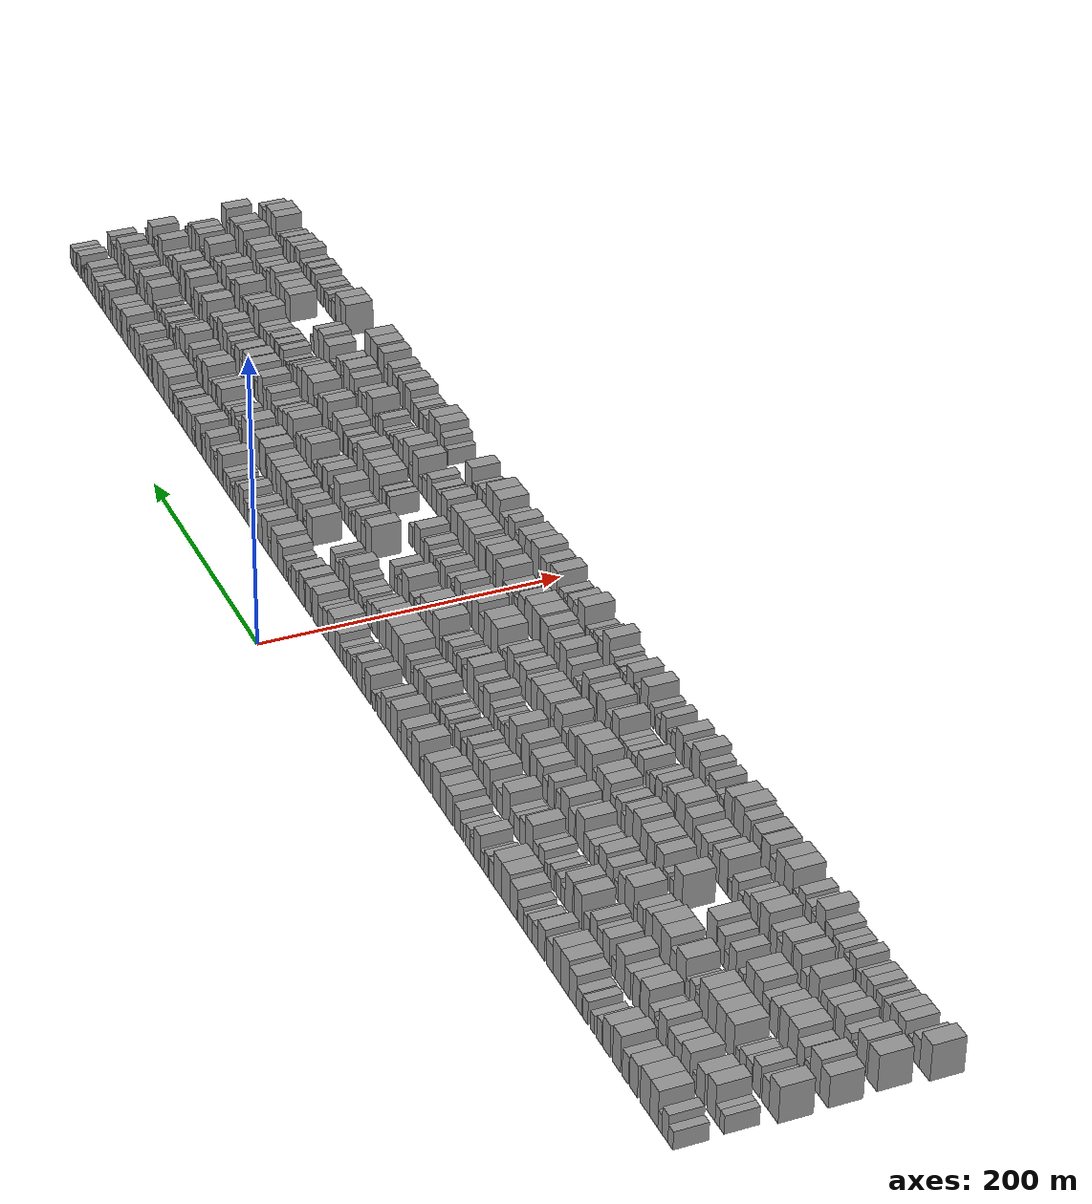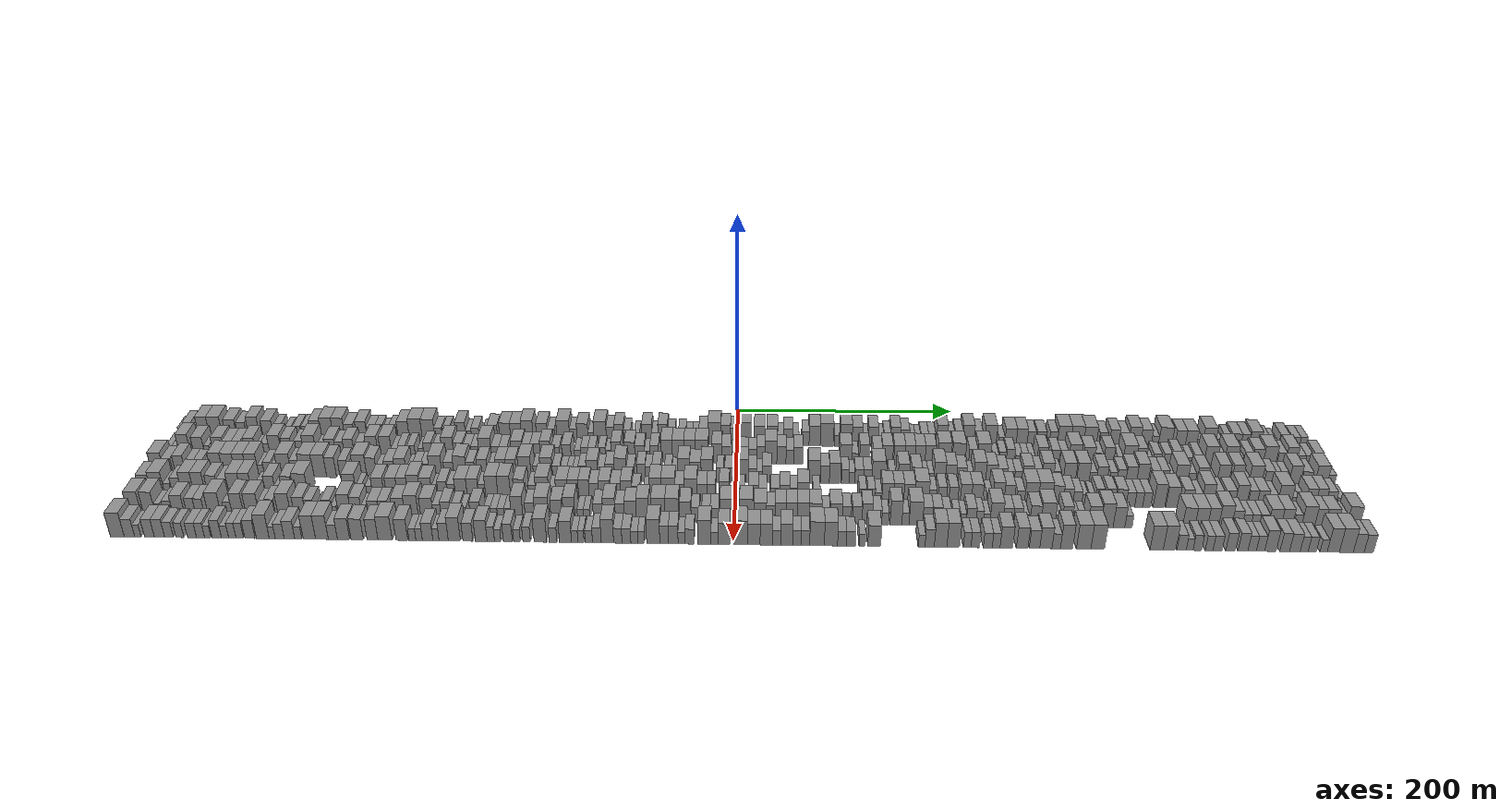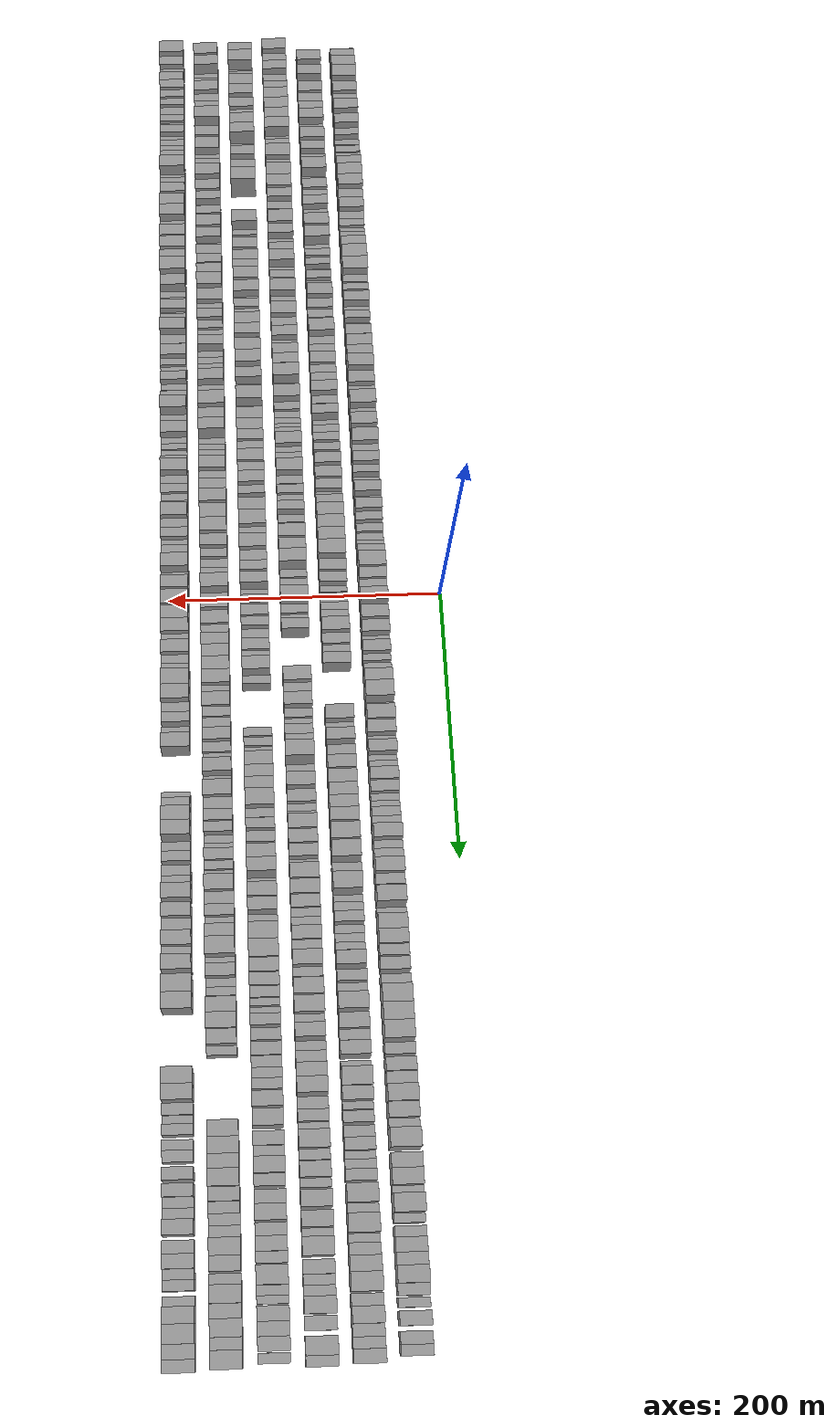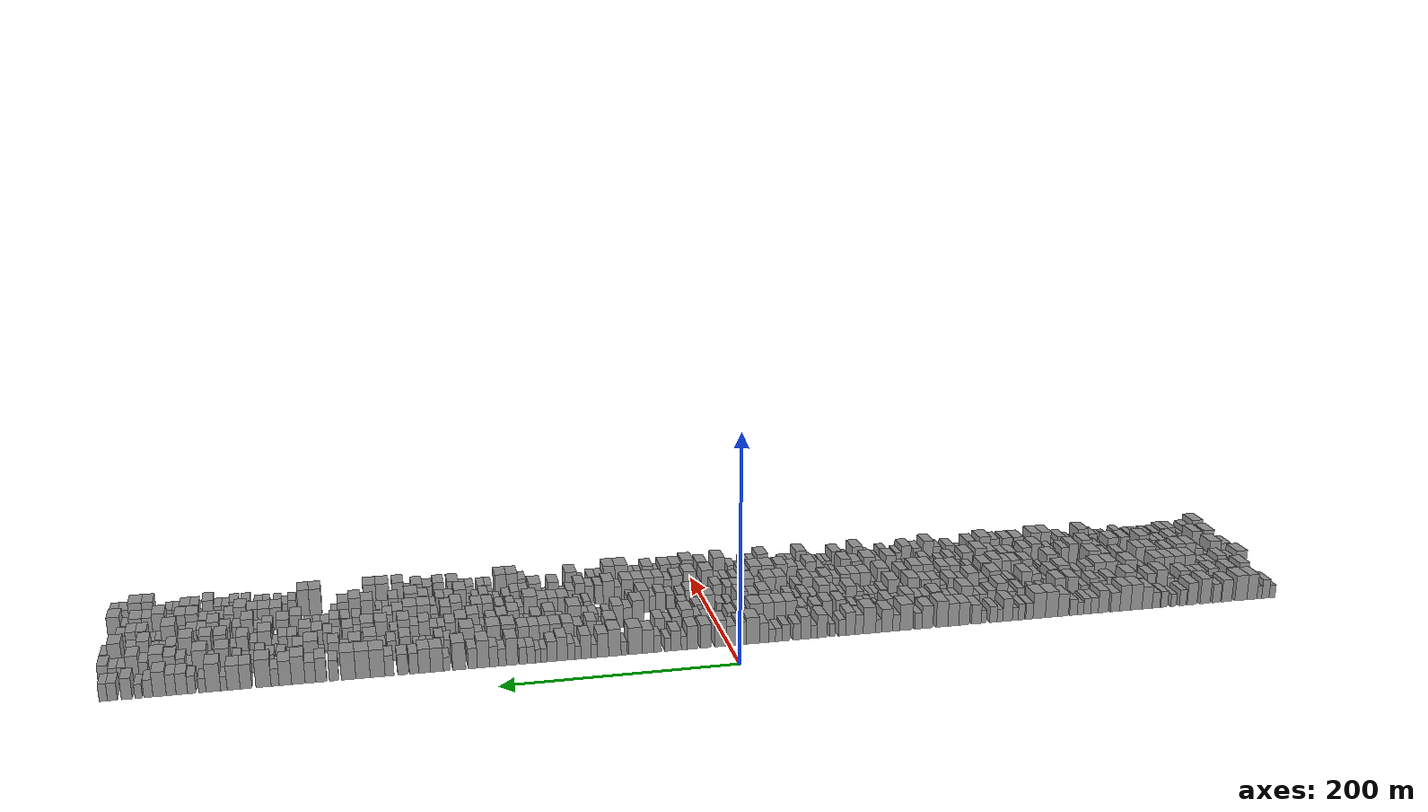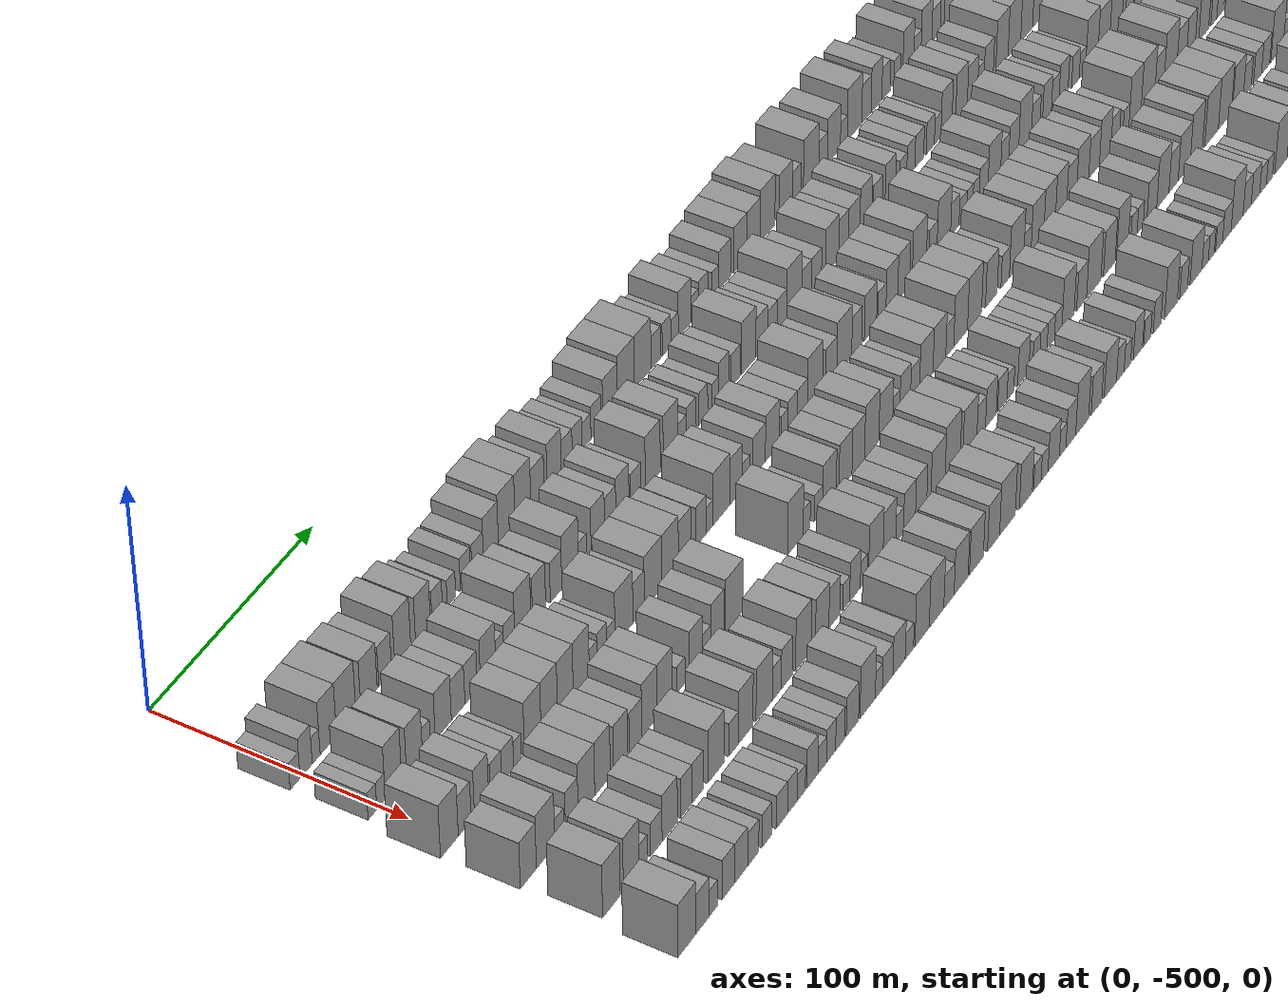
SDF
<sdf version="1.6">
 <world name="default">
  <scene>
   <sky><clouds><speed>12</speed></clouds></sky>
   <ambient>0.4 0.4 0.4 1</ambient>
   <background>0.7 0.7 0.7 1</background>
   <shadows>1</shadows>
  </scene>
  <gravity>0 0 -9.8066</gravity>
  <magnetic_field>6e-06 2.3e-05 -4.2e-05</magnetic_field>
  <physics default="0" name="default_physics" type="ode">
   <ode>
    <solver>
     <type>quick</type>
     <iters>10</iters>
     <sor>1.0</sor>
     <use_dynamic_moi_rescaling>0</use_dynamic_moi_rescaling>
    </solver>
    <constraints>
     <cfm>0</cfm>
     <erp>0.2</erp>
     <contact_max_correcting_vel>100</contact_max_correcting_vel>
     <contact_surface_layer>0.001</contact_surface_layer>
    </constraints>
   </ode>
   <max_step_size>0.004</max_step_size>
   <real_time_factor>1</real_time_factor>
   <real_time_update_rate>250</real_time_update_rate>
  </physics>
  <light name="sun" type="directional">
   <pose>0 0 10 0 0 0</pose>
   <diffuse>0.8 0.8 0.8 1</diffuse>
   <specular>0.2 0.2 0.2 1</specular>
   <attenuation>
    <range>1000</range>
    <constant>0.9</constant>
    <linear>0.01</linear>
    <quadratic>0.001</quadratic>
   </attenuation>
   <direction>-0.5 0.1 -0.9</direction>
  </light>
  <model name="building_1">
   <static>1</static>
   <pose>50.0000 -505.0160 0 0.000000 0.000000 0.000000</pose>
   <link name="link">
    <pose>0 0 6.00 0 0 0</pose>
    <collision name="collision"><geometry><box><size>20.0000 5.9680 12.0000</size></box></geometry></collision>
    <visual name="visual">
     <cast_shadows>0</cast_shadows>
     <geometry><box><size>20.0000 5.9680 12.0000</size></box></geometry>
     <material>
      <script>
       <uri>model://grey_wall/materials/scripts</uri>
       <uri>model://grey_wall/materials/textures</uri>
       <name>vrc/grey_wall</name>
      </script>
     </material>
    </visual>
   </link>
  </model>
  <model name="building_2">
   <static>1</static>
   <pose>50.0000 -498.3636 0 0.000000 0.000000 0.000000</pose>
   <link name="link">
    <pose>0 0 9.00 0 0 0</pose>
    <collision name="collision"><geometry><box><size>20.0000 7.3369 18.0000</size></box></geometry></collision>
    <visual name="visual">
     <cast_shadows>0</cast_shadows>
     <geometry><box><size>20.0000 7.3369 18.0000</size></box></geometry>
     <material>
      <script>
       <uri>model://grey_wall/materials/scripts</uri>
       <uri>model://grey_wall/materials/textures</uri>
       <name>vrc/grey_wall</name>
      </script>
     </material>
    </visual>
   </link>
  </model>
  <model name="building_3">
   <static>1</static>
   <pose>50.0000 -492.2943 0 0.000000 0.000000 0.000000</pose>
   <link name="link">
    <pose>0 0 6.00 0 0 0</pose>
    <collision name="collision"><geometry><box><size>20.0000 4.8018 12.0000</size></box></geometry></collision>
    <visual name="visual">
     <cast_shadows>0</cast_shadows>
     <geometry><box><size>20.0000 4.8018 12.0000</size></box></geometry>
     <material>
      <script>
       <uri>model://grey_wall/materials/scripts</uri>
       <uri>model://grey_wall/materials/textures</uri>
       <name>vrc/grey_wall</name>
      </script>
     </material>
    </visual>
   </link>
  </model>
  <model name="building_4">
   <static>1</static>
   <pose>50.0000 -484.9123 0 0.000000 0.000000 0.000000</pose>
   <link name="link">
    <pose>0 0 12.00 0 0 0</pose>
    <collision name="collision"><geometry><box><size>20.0000 9.9623 24.0000</size></box></geometry></collision>
    <visual name="visual">
     <cast_shadows>0</cast_shadows>
     <geometry><box><size>20.0000 9.9623 24.0000</size></box></geometry>
     <material>
      <script>
       <uri>model://grey_wall/materials/scripts</uri>
       <uri>model://grey_wall/materials/textures</uri>
       <name>vrc/grey_wall</name>
      </script>
     </material>
    </visual>
   </link>
  </model>
  <model name="building_5">
   <static>1</static>
   <pose>50.0000 -474.0198 0 0.000000 0.000000 0.000000</pose>
   <link name="link">
    <pose>0 0 12.00 0 0 0</pose>
    <collision name="collision"><geometry><box><size>20.0000 11.8226 24.0000</size></box></geometry></collision>
    <visual name="visual">
     <cast_shadows>0</cast_shadows>
     <geometry><box><size>20.0000 11.8226 24.0000</size></box></geometry>
     <material>
      <script>
       <uri>model://grey_wall/materials/scripts</uri>
       <uri>model://grey_wall/materials/textures</uri>
       <name>vrc/grey_wall</name>
      </script>
     </material>
    </visual>
   </link>
  </model>
  <model name="building_6">
   <static>1</static>
   <pose>50.0000 -460.0245 0 0.000000 0.000000 0.000000</pose>
   <link name="link">
    <pose>0 0 10.50 0 0 0</pose>
    <collision name="collision"><geometry><box><size>20.0000 10.1681 21.0000</size></box></geometry></collision>
    <visual name="visual">
     <cast_shadows>0</cast_shadows>
     <geometry><box><size>20.0000 10.1681 21.0000</size></box></geometry>
     <material>
      <script>
       <uri>model://grey_wall/materials/scripts</uri>
       <uri>model://grey_wall/materials/textures</uri>
       <name>vrc/grey_wall</name>
      </script>
     </material>
    </visual>
   </link>
  </model>
  <model name="building_7">
   <static>1</static>
   <pose>50.0000 -449.9485 0 0.000000 0.000000 0.000000</pose>
   <link name="link">
    <pose>0 0 9.00 0 0 0</pose>
    <collision name="collision"><geometry><box><size>20.0000 7.9838 18.0000</size></box></geometry></collision>
    <visual name="visual">
     <cast_shadows>0</cast_shadows>
     <geometry><box><size>20.0000 7.9838 18.0000</size></box></geometry>
     <material>
      <script>
       <uri>model://grey_wall/materials/scripts</uri>
       <uri>model://grey_wall/materials/textures</uri>
       <name>vrc/grey_wall</name>
      </script>
     </material>
    </visual>
   </link>
  </model>
  <model name="building_8">
   <static>1</static>
   <pose>50.0000 -438.9323 0 0.000000 0.000000 0.000000</pose>
   <link name="link">
    <pose>0 0 12.00 0 0 0</pose>
    <collision name="collision"><geometry><box><size>20.0000 10.0486 24.0000</size></box></geometry></collision>
    <visual name="visual">
     <cast_shadows>0</cast_shadows>
     <geometry><box><size>20.0000 10.0486 24.0000</size></box></geometry>
     <material>
      <script>
       <uri>model://grey_wall/materials/scripts</uri>
       <uri>model://grey_wall/materials/textures</uri>
       <name>vrc/grey_wall</name>
      </script>
     </material>
    </visual>
   </link>
  </model>
  <model name="building_9">
   <static>1</static>
   <pose>50.0000 -426.1717 0 0.000000 0.000000 0.000000</pose>
   <link name="link">
    <pose>0 0 10.50 0 0 0</pose>
    <collision name="collision"><geometry><box><size>20.0000 9.4726 21.0000</size></box></geometry></collision>
    <visual name="visual">
     <cast_shadows>0</cast_shadows>
     <geometry><box><size>20.0000 9.4726 21.0000</size></box></geometry>
     <material>
      <script>
       <uri>model://grey_wall/materials/scripts</uri>
       <uri>model://grey_wall/materials/textures</uri>
       <name>vrc/grey_wall</name>
      </script>
     </material>
    </visual>
   </link>
  </model>
  <model name="building_10">
   <static>1</static>
   <pose>50.0000 -417.1049 0 0.000000 0.000000 0.000000</pose>
   <link name="link">
    <pose>0 0 7.50 0 0 0</pose>
    <collision name="collision"><geometry><box><size>20.0000 6.6611 15.0000</size></box></geometry></collision>
    <visual name="visual">
     <cast_shadows>0</cast_shadows>
     <geometry><box><size>20.0000 6.6611 15.0000</size></box></geometry>
     <material>
      <script>
       <uri>model://grey_wall/materials/scripts</uri>
       <uri>model://grey_wall/materials/textures</uri>
       <name>vrc/grey_wall</name>
      </script>
     </material>
    </visual>
   </link>
  </model>
  <model name="building_11">
   <static>1</static>
   <pose>50.0000 -408.0522 0 0.000000 0.000000 0.000000</pose>
   <link name="link">
    <pose>0 0 6.00 0 0 0</pose>
    <collision name="collision"><geometry><box><size>20.0000 5.4442 12.0000</size></box></geometry></collision>
    <visual name="visual">
     <cast_shadows>0</cast_shadows>
     <geometry><box><size>20.0000 5.4442 12.0000</size></box></geometry>
     <material>
      <script>
       <uri>model://grey_wall/materials/scripts</uri>
       <uri>model://grey_wall/materials/textures</uri>
       <name>vrc/grey_wall</name>
      </script>
     </material>
    </visual>
   </link>
  </model>
  <model name="building_12">
   <static>1</static>
   <pose>50.0000 -399.0358 0 0.000000 0.000000 0.000000</pose>
   <link name="link">
    <pose>0 0 7.50 0 0 0</pose>
    <collision name="collision"><geometry><box><size>20.0000 6.5886 15.0000</size></box></geometry></collision>
    <visual name="visual">
     <cast_shadows>0</cast_shadows>
     <geometry><box><size>20.0000 6.5886 15.0000</size></box></geometry>
     <material>
      <script>
       <uri>model://grey_wall/materials/scripts</uri>
       <uri>model://grey_wall/materials/textures</uri>
       <name>vrc/grey_wall</name>
      </script>
     </material>
    </visual>
   </link>
  </model>
  <model name="building_13">
   <static>1</static>
   <pose>50.0000 -391.0221 0 0.000000 0.000000 0.000000</pose>
   <link name="link">
    <pose>0 0 7.50 0 0 0</pose>
    <collision name="collision"><geometry><box><size>20.0000 7.4388 15.0000</size></box></geometry></collision>
    <visual name="visual">
     <cast_shadows>0</cast_shadows>
     <geometry><box><size>20.0000 7.4388 15.0000</size></box></geometry>
     <material>
      <script>
       <uri>model://grey_wall/materials/scripts</uri>
       <uri>model://grey_wall/materials/textures</uri>
       <name>vrc/grey_wall</name>
      </script>
     </material>
    </visual>
   </link>
  </model>
  <model name="building_14">
   <static>1</static>
   <pose>50.0000 -382.4483 0 0.000000 0.000000 0.000000</pose>
   <link name="link">
    <pose>0 0 10.50 0 0 0</pose>
    <collision name="collision"><geometry><box><size>20.0000 9.7088 21.0000</size></box></geometry></collision>
    <visual name="visual">
     <cast_shadows>0</cast_shadows>
     <geometry><box><size>20.0000 9.7088 21.0000</size></box></geometry>
     <material>
      <script>
       <uri>model://grey_wall/materials/scripts</uri>
       <uri>model://grey_wall/materials/textures</uri>
       <name>vrc/grey_wall</name>
      </script>
     </material>
    </visual>
   </link>
  </model>
  <model name="building_15">
   <static>1</static>
   <pose>50.0000 -372.0800 0 0.000000 0.000000 0.000000</pose>
   <link name="link">
    <pose>0 0 12.00 0 0 0</pose>
    <collision name="collision"><geometry><box><size>20.0000 11.0279 24.0000</size></box></geometry></collision>
    <visual name="visual">
     <cast_shadows>0</cast_shadows>
     <geometry><box><size>20.0000 11.0279 24.0000</size></box></geometry>
     <material>
      <script>
       <uri>model://grey_wall/materials/scripts</uri>
       <uri>model://grey_wall/materials/textures</uri>
       <name>vrc/grey_wall</name>
      </script>
     </material>
    </visual>
   </link>
  </model>
  <model name="building_16">
   <static>1</static>
   <pose>50.0000 -361.3567 0 0.000000 0.000000 0.000000</pose>
   <link name="link">
    <pose>0 0 12.00 0 0 0</pose>
    <collision name="collision"><geometry><box><size>20.0000 10.4185 24.0000</size></box></geometry></collision>
    <visual name="visual">
     <cast_shadows>0</cast_shadows>
     <geometry><box><size>20.0000 10.4185 24.0000</size></box></geometry>
     <material>
      <script>
       <uri>model://grey_wall/materials/scripts</uri>
       <uri>model://grey_wall/materials/textures</uri>
       <name>vrc/grey_wall</name>
      </script>
     </material>
    </visual>
   </link>
  </model>
  <model name="building_17">
   <static>1</static>
   <pose>50.0000 -351.7194 0 0.000000 0.000000 0.000000</pose>
   <link name="link">
    <pose>0 0 9.00 0 0 0</pose>
    <collision name="collision"><geometry><box><size>20.0000 8.8561 18.0000</size></box></geometry></collision>
    <visual name="visual">
     <cast_shadows>0</cast_shadows>
     <geometry><box><size>20.0000 8.8561 18.0000</size></box></geometry>
     <material>
      <script>
       <uri>model://grey_wall/materials/scripts</uri>
       <uri>model://grey_wall/materials/textures</uri>
       <name>vrc/grey_wall</name>
      </script>
     </material>
    </visual>
   </link>
  </model>
  <model name="building_18">
   <static>1</static>
   <pose>50.0000 -340.5252 0 0.000000 0.000000 0.000000</pose>
   <link name="link">
    <pose>0 0 10.50 0 0 0</pose>
    <collision name="collision"><geometry><box><size>20.0000 9.5323 21.0000</size></box></geometry></collision>
    <visual name="visual">
     <cast_shadows>0</cast_shadows>
     <geometry><box><size>20.0000 9.5323 21.0000</size></box></geometry>
     <material>
      <script>
       <uri>model://grey_wall/materials/scripts</uri>
       <uri>model://grey_wall/materials/textures</uri>
       <name>vrc/grey_wall</name>
      </script>
     </material>
    </visual>
   </link>
  </model>
  <model name="building_19">
   <static>1</static>
   <pose>50.0000 -332.0643 0 0.000000 0.000000 0.000000</pose>
   <link name="link">
    <pose>0 0 7.50 0 0 0</pose>
    <collision name="collision"><geometry><box><size>20.0000 7.3896 15.0000</size></box></geometry></collision>
    <visual name="visual">
     <cast_shadows>0</cast_shadows>
     <geometry><box><size>20.0000 7.3896 15.0000</size></box></geometry>
     <material>
      <script>
       <uri>model://grey_wall/materials/scripts</uri>
       <uri>model://grey_wall/materials/textures</uri>
       <name>vrc/grey_wall</name>
      </script>
     </material>
    </visual>
   </link>
  </model>
  <model name="building_20">
   <static>1</static>
   <pose>50.0000 -324.9953 0 0.000000 0.000000 0.000000</pose>
   <link name="link">
    <pose>0 0 7.50 0 0 0</pose>
    <collision name="collision"><geometry><box><size>20.0000 6.7483 15.0000</size></box></geometry></collision>
    <visual name="visual">
     <cast_shadows>0</cast_shadows>
     <geometry><box><size>20.0000 6.7483 15.0000</size></box></geometry>
     <material>
      <script>
       <uri>model://grey_wall/materials/scripts</uri>
       <uri>model://grey_wall/materials/textures</uri>
       <name>vrc/grey_wall</name>
      </script>
     </material>
    </visual>
   </link>
  </model>
  <model name="building_21">
   <static>1</static>
   <pose>50.0000 -318.6482 0 0.000000 0.000000 0.000000</pose>
   <link name="link">
    <pose>0 0 6.00 0 0 0</pose>
    <collision name="collision"><geometry><box><size>20.0000 5.9460 12.0000</size></box></geometry></collision>
    <visual name="visual">
     <cast_shadows>0</cast_shadows>
     <geometry><box><size>20.0000 5.9460 12.0000</size></box></geometry>
     <material>
      <script>
       <uri>model://grey_wall/materials/scripts</uri>
       <uri>model://grey_wall/materials/textures</uri>
       <name>vrc/grey_wall</name>
      </script>
     </material>
    </visual>
   </link>
  </model>
  <model name="building_22">
   <static>1</static>
   <pose>50.0000 -312.0766 0 0.000000 0.000000 0.000000</pose>
   <link name="link">
    <pose>0 0 7.50 0 0 0</pose>
    <collision name="collision"><geometry><box><size>20.0000 7.1972 15.0000</size></box></geometry></collision>
    <visual name="visual">
     <cast_shadows>0</cast_shadows>
     <geometry><box><size>20.0000 7.1972 15.0000</size></box></geometry>
     <material>
      <script>
       <uri>model://grey_wall/materials/scripts</uri>
       <uri>model://grey_wall/materials/textures</uri>
       <name>vrc/grey_wall</name>
      </script>
     </material>
    </visual>
   </link>
  </model>
  <model name="building_23">
   <static>1</static>
   <pose>50.0000 -302.3935 0 0.000000 0.000000 0.000000</pose>
   <link name="link">
    <pose>0 0 10.50 0 0 0</pose>
    <collision name="collision"><geometry><box><size>20.0000 10.1690 21.0000</size></box></geometry></collision>
    <visual name="visual">
     <cast_shadows>0</cast_shadows>
     <geometry><box><size>20.0000 10.1690 21.0000</size></box></geometry>
     <material>
      <script>
       <uri>model://grey_wall/materials/scripts</uri>
       <uri>model://grey_wall/materials/textures</uri>
       <name>vrc/grey_wall</name>
      </script>
     </material>
    </visual>
   </link>
  </model>
  <model name="building_24">
   <static>1</static>
   <pose>50.0000 -291.4551 0 0.000000 0.000000 0.000000</pose>
   <link name="link">
    <pose>0 0 12.00 0 0 0</pose>
    <collision name="collision"><geometry><box><size>20.0000 11.7078 24.0000</size></box></geometry></collision>
    <visual name="visual">
     <cast_shadows>0</cast_shadows>
     <geometry><box><size>20.0000 11.7078 24.0000</size></box></geometry>
     <material>
      <script>
       <uri>model://grey_wall/materials/scripts</uri>
       <uri>model://grey_wall/materials/textures</uri>
       <name>vrc/grey_wall</name>
      </script>
     </material>
    </visual>
   </link>
  </model>
  <model name="building_25">
   <static>1</static>
   <pose>50.0000 -279.8147 0 0.000000 0.000000 0.000000</pose>
   <link name="link">
    <pose>0 0 12.00 0 0 0</pose>
    <collision name="collision"><geometry><box><size>20.0000 11.5730 24.0000</size></box></geometry></collision>
    <visual name="visual">
     <cast_shadows>0</cast_shadows>
     <geometry><box><size>20.0000 11.5730 24.0000</size></box></geometry>
     <material>
      <script>
       <uri>model://grey_wall/materials/scripts</uri>
       <uri>model://grey_wall/materials/textures</uri>
       <name>vrc/grey_wall</name>
      </script>
     </material>
    </visual>
   </link>
  </model>
  <model name="building_26">
   <static>1</static>
   <pose>50.0000 -270.5870 0 0.000000 0.000000 0.000000</pose>
   <link name="link">
    <pose>0 0 7.50 0 0 0</pose>
    <collision name="collision"><geometry><box><size>20.0000 6.8825 15.0000</size></box></geometry></collision>
    <visual name="visual">
     <cast_shadows>0</cast_shadows>
     <geometry><box><size>20.0000 6.8825 15.0000</size></box></geometry>
     <material>
      <script>
       <uri>model://grey_wall/materials/scripts</uri>
       <uri>model://grey_wall/materials/textures</uri>
       <name>vrc/grey_wall</name>
      </script>
     </material>
    </visual>
   </link>
  </model>
  <model name="building_27">
   <static>1</static>
   <pose>50.0000 -263.1176 0 0.000000 0.000000 0.000000</pose>
   <link name="link">
    <pose>0 0 7.50 0 0 0</pose>
    <collision name="collision"><geometry><box><size>20.0000 6.0564 15.0000</size></box></geometry></collision>
    <visual name="visual">
     <cast_shadows>0</cast_shadows>
     <geometry><box><size>20.0000 6.0564 15.0000</size></box></geometry>
     <material>
      <script>
       <uri>model://grey_wall/materials/scripts</uri>
       <uri>model://grey_wall/materials/textures</uri>
       <name>vrc/grey_wall</name>
      </script>
     </material>
    </visual>
   </link>
  </model>
  <model name="building_28">
   <static>1</static>
   <pose>50.0000 -257.4075 0 0.000000 0.000000 0.000000</pose>
   <link name="link">
    <pose>0 0 6.00 0 0 0</pose>
    <collision name="collision"><geometry><box><size>20.0000 5.3637 12.0000</size></box></geometry></collision>
    <visual name="visual">
     <cast_shadows>0</cast_shadows>
     <geometry><box><size>20.0000 5.3637 12.0000</size></box></geometry>
     <material>
      <script>
       <uri>model://grey_wall/materials/scripts</uri>
       <uri>model://grey_wall/materials/textures</uri>
       <name>vrc/grey_wall</name>
      </script>
     </material>
    </visual>
   </link>
  </model>
  <model name="building_29">
   <static>1</static>
   <pose>50.0000 -250.2518 0 0.000000 0.000000 0.000000</pose>
   <link name="link">
    <pose>0 0 10.50 0 0 0</pose>
    <collision name="collision"><geometry><box><size>20.0000 8.9477 21.0000</size></box></geometry></collision>
    <visual name="visual">
     <cast_shadows>0</cast_shadows>
     <geometry><box><size>20.0000 8.9477 21.0000</size></box></geometry>
     <material>
      <script>
       <uri>model://grey_wall/materials/scripts</uri>
       <uri>model://grey_wall/materials/textures</uri>
       <name>vrc/grey_wall</name>
      </script>
     </material>
    </visual>
   </link>
  </model>
  <model name="building_30">
   <static>1</static>
   <pose>50.0000 -243.1245 0 0.000000 0.000000 0.000000</pose>
   <link name="link">
    <pose>0 0 6.00 0 0 0</pose>
    <collision name="collision"><geometry><box><size>20.0000 5.3070 12.0000</size></box></geometry></collision>
    <visual name="visual">
     <cast_shadows>0</cast_shadows>
     <geometry><box><size>20.0000 5.3070 12.0000</size></box></geometry>
     <material>
      <script>
       <uri>model://grey_wall/materials/scripts</uri>
       <uri>model://grey_wall/materials/textures</uri>
       <name>vrc/grey_wall</name>
      </script>
     </material>
    </visual>
   </link>
  </model>
  <model name="building_31">
   <static>1</static>
   <pose>50.0000 -237.0091 0 0.000000 0.000000 0.000000</pose>
   <link name="link">
    <pose>0 0 7.50 0 0 0</pose>
    <collision name="collision"><geometry><box><size>20.0000 6.9237 15.0000</size></box></geometry></collision>
    <visual name="visual">
     <cast_shadows>0</cast_shadows>
     <geometry><box><size>20.0000 6.9237 15.0000</size></box></geometry>
     <material>
      <script>
       <uri>model://grey_wall/materials/scripts</uri>
       <uri>model://grey_wall/materials/textures</uri>
       <name>vrc/grey_wall</name>
      </script>
     </material>
    </visual>
   </link>
  </model>
  <model name="building_32">
   <static>1</static>
   <pose>50.0000 -228.1364 0 0.000000 0.000000 0.000000</pose>
   <link name="link">
    <pose>0 0 6.00 0 0 0</pose>
    <collision name="collision"><geometry><box><size>20.0000 4.8216 12.0000</size></box></geometry></collision>
    <visual name="visual">
     <cast_shadows>0</cast_shadows>
     <geometry><box><size>20.0000 4.8216 12.0000</size></box></geometry>
     <material>
      <script>
       <uri>model://grey_wall/materials/scripts</uri>
       <uri>model://grey_wall/materials/textures</uri>
       <name>vrc/grey_wall</name>
      </script>
     </material>
    </visual>
   </link>
  </model>
  <model name="building_33">
   <static>1</static>
   <pose>50.0000 -221.2678 0 0.000000 0.000000 0.000000</pose>
   <link name="link">
    <pose>0 0 9.00 0 0 0</pose>
    <collision name="collision"><geometry><box><size>20.0000 8.9158 18.0000</size></box></geometry></collision>
    <visual name="visual">
     <cast_shadows>0</cast_shadows>
     <geometry><box><size>20.0000 8.9158 18.0000</size></box></geometry>
     <material>
      <script>
       <uri>model://grey_wall/materials/scripts</uri>
       <uri>model://grey_wall/materials/textures</uri>
       <name>vrc/grey_wall</name>
      </script>
     </material>
    </visual>
   </link>
  </model>
  <model name="building_34">
   <static>1</static>
   <pose>50.0000 -209.9153 0 0.000000 0.000000 0.000000</pose>
   <link name="link">
    <pose>0 0 10.50 0 0 0</pose>
    <collision name="collision"><geometry><box><size>20.0000 9.7893 21.0000</size></box></geometry></collision>
    <visual name="visual">
     <cast_shadows>0</cast_shadows>
     <geometry><box><size>20.0000 9.7893 21.0000</size></box></geometry>
     <material>
      <script>
       <uri>model://grey_wall/materials/scripts</uri>
       <uri>model://grey_wall/materials/textures</uri>
       <name>vrc/grey_wall</name>
      </script>
     </material>
    </visual>
   </link>
  </model>
  <model name="building_35">
   <static>1</static>
   <pose>50.0000 -200.0415 0 0.000000 0.000000 0.000000</pose>
   <link name="link">
    <pose>0 0 10.50 0 0 0</pose>
    <collision name="collision"><geometry><box><size>20.0000 9.9583 21.0000</size></box></geometry></collision>
    <visual name="visual">
     <cast_shadows>0</cast_shadows>
     <geometry><box><size>20.0000 9.9583 21.0000</size></box></geometry>
     <material>
      <script>
       <uri>model://grey_wall/materials/scripts</uri>
       <uri>model://grey_wall/materials/textures</uri>
       <name>vrc/grey_wall</name>
      </script>
     </material>
    </visual>
   </link>
  </model>
  <model name="building_36">
   <static>1</static>
   <pose>50.0000 -189.6931 0 0.000000 0.000000 0.000000</pose>
   <link name="link">
    <pose>0 0 12.00 0 0 0</pose>
    <collision name="collision"><geometry><box><size>20.0000 10.7384 24.0000</size></box></geometry></collision>
    <visual name="visual">
     <cast_shadows>0</cast_shadows>
     <geometry><box><size>20.0000 10.7384 24.0000</size></box></geometry>
     <material>
      <script>
       <uri>model://grey_wall/materials/scripts</uri>
       <uri>model://grey_wall/materials/textures</uri>
       <name>vrc/grey_wall</name>
      </script>
     </material>
    </visual>
   </link>
  </model>
  <model name="building_37">
   <static>1</static>
   <pose>50.0000 -176.3118 0 0.000000 0.000000 0.000000</pose>
   <link name="link">
    <pose>0 0 10.50 0 0 0</pose>
    <collision name="collision"><geometry><box><size>20.0000 10.0240 21.0000</size></box></geometry></collision>
    <visual name="visual">
     <cast_shadows>0</cast_shadows>
     <geometry><box><size>20.0000 10.0240 21.0000</size></box></geometry>
     <material>
      <script>
       <uri>model://grey_wall/materials/scripts</uri>
       <uri>model://grey_wall/materials/textures</uri>
       <name>vrc/grey_wall</name>
      </script>
     </material>
    </visual>
   </link>
  </model>
  <model name="building_38">
   <static>1</static>
   <pose>50.0000 -168.1040 0 0.000000 0.000000 0.000000</pose>
   <link name="link">
    <pose>0 0 7.50 0 0 0</pose>
    <collision name="collision"><geometry><box><size>20.0000 6.3917 15.0000</size></box></geometry></collision>
    <visual name="visual">
     <cast_shadows>0</cast_shadows>
     <geometry><box><size>20.0000 6.3917 15.0000</size></box></geometry>
     <material>
      <script>
       <uri>model://grey_wall/materials/scripts</uri>
       <uri>model://grey_wall/materials/textures</uri>
       <name>vrc/grey_wall</name>
      </script>
     </material>
    </visual>
   </link>
  </model>
  <model name="building_39">
   <static>1</static>
   <pose>50.0000 -157.1111 0 0.000000 0.000000 0.000000</pose>
   <link name="link">
    <pose>0 0 12.00 0 0 0</pose>
    <collision name="collision"><geometry><box><size>20.0000 11.5940 24.0000</size></box></geometry></collision>
    <visual name="visual">
     <cast_shadows>0</cast_shadows>
     <geometry><box><size>20.0000 11.5940 24.0000</size></box></geometry>
     <material>
      <script>
       <uri>model://grey_wall/materials/scripts</uri>
       <uri>model://grey_wall/materials/textures</uri>
       <name>vrc/grey_wall</name>
      </script>
     </material>
    </visual>
   </link>
  </model>
  <model name="building_40">
   <static>1</static>
   <pose>50.0000 -147.9836 0 0.000000 0.000000 0.000000</pose>
   <link name="link">
    <pose>0 0 7.50 0 0 0</pose>
    <collision name="collision"><geometry><box><size>20.0000 6.6611 15.0000</size></box></geometry></collision>
    <visual name="visual">
     <cast_shadows>0</cast_shadows>
     <geometry><box><size>20.0000 6.6611 15.0000</size></box></geometry>
     <material>
      <script>
       <uri>model://grey_wall/materials/scripts</uri>
       <uri>model://grey_wall/materials/textures</uri>
       <name>vrc/grey_wall</name>
      </script>
     </material>
    </visual>
   </link>
  </model>
  <model name="building_41">
   <static>1</static>
   <pose>50.0000 -139.6642 0 0.000000 0.000000 0.000000</pose>
   <link name="link">
    <pose>0 0 10.50 0 0 0</pose>
    <collision name="collision"><geometry><box><size>20.0000 9.9777 21.0000</size></box></geometry></collision>
    <visual name="visual">
     <cast_shadows>0</cast_shadows>
     <geometry><box><size>20.0000 9.9777 21.0000</size></box></geometry>
     <material>
      <script>
       <uri>model://grey_wall/materials/scripts</uri>
       <uri>model://grey_wall/materials/textures</uri>
       <name>vrc/grey_wall</name>
      </script>
     </material>
    </visual>
   </link>
  </model>
  <model name="building_42">
   <static>1</static>
   <pose>50.0000 -132.0179 0 0.000000 0.000000 0.000000</pose>
   <link name="link">
    <pose>0 0 6.00 0 0 0</pose>
    <collision name="collision"><geometry><box><size>20.0000 5.3148 12.0000</size></box></geometry></collision>
    <visual name="visual">
     <cast_shadows>0</cast_shadows>
     <geometry><box><size>20.0000 5.3148 12.0000</size></box></geometry>
     <material>
      <script>
       <uri>model://grey_wall/materials/scripts</uri>
       <uri>model://grey_wall/materials/textures</uri>
       <name>vrc/grey_wall</name>
      </script>
     </material>
    </visual>
   </link>
  </model>
  <model name="building_43">
   <static>1</static>
   <pose>50.0000 -123.7503 0 0.000000 0.000000 0.000000</pose>
   <link name="link">
    <pose>0 0 12.00 0 0 0</pose>
    <collision name="collision"><geometry><box><size>20.0000 11.2204 24.0000</size></box></geometry></collision>
    <visual name="visual">
     <cast_shadows>0</cast_shadows>
     <geometry><box><size>20.0000 11.2204 24.0000</size></box></geometry>
     <material>
      <script>
       <uri>model://grey_wall/materials/scripts</uri>
       <uri>model://grey_wall/materials/textures</uri>
       <name>vrc/grey_wall</name>
      </script>
     </material>
    </visual>
   </link>
  </model>
  <model name="building_44">
   <static>1</static>
   <pose>50.0000 -114.4987 0 0.000000 0.000000 0.000000</pose>
   <link name="link">
    <pose>0 0 9.00 0 0 0</pose>
    <collision name="collision"><geometry><box><size>20.0000 7.2827 18.0000</size></box></geometry></collision>
    <visual name="visual">
     <cast_shadows>0</cast_shadows>
     <geometry><box><size>20.0000 7.2827 18.0000</size></box></geometry>
     <material>
      <script>
       <uri>model://grey_wall/materials/scripts</uri>
       <uri>model://grey_wall/materials/textures</uri>
       <name>vrc/grey_wall</name>
      </script>
     </material>
    </visual>
   </link>
  </model>
  <model name="building_45">
   <static>1</static>
   <pose>50.0000 -106.6176 0 0.000000 0.000000 0.000000</pose>
   <link name="link">
    <pose>0 0 10.50 0 0 0</pose>
    <collision name="collision"><geometry><box><size>20.0000 8.4797 21.0000</size></box></geometry></collision>
    <visual name="visual">
     <cast_shadows>0</cast_shadows>
     <geometry><box><size>20.0000 8.4797 21.0000</size></box></geometry>
     <material>
      <script>
       <uri>model://grey_wall/materials/scripts</uri>
       <uri>model://grey_wall/materials/textures</uri>
       <name>vrc/grey_wall</name>
      </script>
     </material>
    </visual>
   </link>
  </model>
  <model name="building_46">
   <static>1</static>
   <pose>50.0000 -99.1205 0 0.000000 0.000000 0.000000</pose>
   <link name="link">
    <pose>0 0 7.50 0 0 0</pose>
    <collision name="collision"><geometry><box><size>20.0000 6.5144 15.0000</size></box></geometry></collision>
    <visual name="visual">
     <cast_shadows>0</cast_shadows>
     <geometry><box><size>20.0000 6.5144 15.0000</size></box></geometry>
     <material>
      <script>
       <uri>model://grey_wall/materials/scripts</uri>
       <uri>model://grey_wall/materials/textures</uri>
       <name>vrc/grey_wall</name>
      </script>
     </material>
    </visual>
   </link>
  </model>
  <model name="building_47">
   <static>1</static>
   <pose>50.0000 -90.3728 0 0.000000 0.000000 0.000000</pose>
   <link name="link">
    <pose>0 0 6.00 0 0 0</pose>
    <collision name="collision"><geometry><box><size>20.0000 4.9810 12.0000</size></box></geometry></collision>
    <visual name="visual">
     <cast_shadows>0</cast_shadows>
     <geometry><box><size>20.0000 4.9810 12.0000</size></box></geometry>
     <material>
      <script>
       <uri>model://grey_wall/materials/scripts</uri>
       <uri>model://grey_wall/materials/textures</uri>
       <name>vrc/grey_wall</name>
      </script>
     </material>
    </visual>
   </link>
  </model>
  <model name="building_48">
   <static>1</static>
   <pose>50.0000 -81.4564 0 0.000000 0.000000 0.000000</pose>
   <link name="link">
    <pose>0 0 10.50 0 0 0</pose>
    <collision name="collision"><geometry><box><size>20.0000 8.8519 21.0000</size></box></geometry></collision>
    <visual name="visual">
     <cast_shadows>0</cast_shadows>
     <geometry><box><size>20.0000 8.8519 21.0000</size></box></geometry>
     <material>
      <script>
       <uri>model://grey_wall/materials/scripts</uri>
       <uri>model://grey_wall/materials/textures</uri>
       <name>vrc/grey_wall</name>
      </script>
     </material>
    </visual>
   </link>
  </model>
  <model name="building_49">
   <static>1</static>
   <pose>50.0000 -74.1553 0 0.000000 0.000000 0.000000</pose>
   <link name="link">
    <pose>0 0 6.00 0 0 0</pose>
    <collision name="collision"><geometry><box><size>20.0000 5.7502 12.0000</size></box></geometry></collision>
    <visual name="visual">
     <cast_shadows>0</cast_shadows>
     <geometry><box><size>20.0000 5.7502 12.0000</size></box></geometry>
     <material>
      <script>
       <uri>model://grey_wall/materials/scripts</uri>
       <uri>model://grey_wall/materials/textures</uri>
       <name>vrc/grey_wall</name>
      </script>
     </material>
    </visual>
   </link>
  </model>
  <model name="building_50">
   <static>1</static>
   <pose>50.0000 -66.9505 0 0.000000 0.000000 0.000000</pose>
   <link name="link">
    <pose>0 0 10.50 0 0 0</pose>
    <collision name="collision"><geometry><box><size>20.0000 8.6593 21.0000</size></box></geometry></collision>
    <visual name="visual">
     <cast_shadows>0</cast_shadows>
     <geometry><box><size>20.0000 8.6593 21.0000</size></box></geometry>
     <material>
      <script>
       <uri>model://grey_wall/materials/scripts</uri>
       <uri>model://grey_wall/materials/textures</uri>
       <name>vrc/grey_wall</name>
      </script>
     </material>
    </visual>
   </link>
  </model>
  <model name="building_51">
   <static>1</static>
   <pose>50.0000 -59.1784 0 0.000000 0.000000 0.000000</pose>
   <link name="link">
    <pose>0 0 7.50 0 0 0</pose>
    <collision name="collision"><geometry><box><size>20.0000 6.8849 15.0000</size></box></geometry></collision>
    <visual name="visual">
     <cast_shadows>0</cast_shadows>
     <geometry><box><size>20.0000 6.8849 15.0000</size></box></geometry>
     <material>
      <script>
       <uri>model://grey_wall/materials/scripts</uri>
       <uri>model://grey_wall/materials/textures</uri>
       <name>vrc/grey_wall</name>
      </script>
     </material>
    </visual>
   </link>
  </model>
  <model name="building_52">
   <static>1</static>
   <pose>50.0000 -49.3642 0 0.000000 0.000000 0.000000</pose>
   <link name="link">
    <pose>0 0 7.50 0 0 0</pose>
    <collision name="collision"><geometry><box><size>20.0000 6.7436 15.0000</size></box></geometry></collision>
    <visual name="visual">
     <cast_shadows>0</cast_shadows>
     <geometry><box><size>20.0000 6.7436 15.0000</size></box></geometry>
     <material>
      <script>
       <uri>model://grey_wall/materials/scripts</uri>
       <uri>model://grey_wall/materials/textures</uri>
       <name>vrc/grey_wall</name>
      </script>
     </material>
    </visual>
   </link>
  </model>
  <model name="building_53">
   <static>1</static>
   <pose>50.0000 -43.0074 0 0.000000 0.000000 0.000000</pose>
   <link name="link">
    <pose>0 0 6.00 0 0 0</pose>
    <collision name="collision"><geometry><box><size>20.0000 5.9699 12.0000</size></box></geometry></collision>
    <visual name="visual">
     <cast_shadows>0</cast_shadows>
     <geometry><box><size>20.0000 5.9699 12.0000</size></box></geometry>
     <material>
      <script>
       <uri>model://grey_wall/materials/scripts</uri>
       <uri>model://grey_wall/materials/textures</uri>
       <name>vrc/grey_wall</name>
      </script>
     </material>
    </visual>
   </link>
  </model>
  <model name="building_54">
   <static>1</static>
   <pose>50.0000 -37.0977 0 0.000000 0.000000 0.000000</pose>
   <link name="link">
    <pose>0 0 6.00 0 0 0</pose>
    <collision name="collision"><geometry><box><size>20.0000 5.8495 12.0000</size></box></geometry></collision>
    <visual name="visual">
     <cast_shadows>0</cast_shadows>
     <geometry><box><size>20.0000 5.8495 12.0000</size></box></geometry>
     <material>
      <script>
       <uri>model://grey_wall/materials/scripts</uri>
       <uri>model://grey_wall/materials/textures</uri>
       <name>vrc/grey_wall</name>
      </script>
     </material>
    </visual>
   </link>
  </model>
  <model name="building_55">
   <static>1</static>
   <pose>50.0000 -30.1137 0 0.000000 0.000000 0.000000</pose>
   <link name="link">
    <pose>0 0 9.00 0 0 0</pose>
    <collision name="collision"><geometry><box><size>20.0000 8.1184 18.0000</size></box></geometry></collision>
    <visual name="visual">
     <cast_shadows>0</cast_shadows>
     <geometry><box><size>20.0000 8.1184 18.0000</size></box></geometry>
     <material>
      <script>
       <uri>model://grey_wall/materials/scripts</uri>
       <uri>model://grey_wall/materials/textures</uri>
       <name>vrc/grey_wall</name>
      </script>
     </material>
    </visual>
   </link>
  </model>
  <model name="building_56">
   <static>1</static>
   <pose>50.0000 -20.2414 0 0.000000 0.000000 0.000000</pose>
   <link name="link">
    <pose>0 0 12.00 0 0 0</pose>
    <collision name="collision"><geometry><box><size>20.0000 11.6262 24.0000</size></box></geometry></collision>
    <visual name="visual">
     <cast_shadows>0</cast_shadows>
     <geometry><box><size>20.0000 11.6262 24.0000</size></box></geometry>
     <material>
      <script>
       <uri>model://grey_wall/materials/scripts</uri>
       <uri>model://grey_wall/materials/textures</uri>
       <name>vrc/grey_wall</name>
      </script>
     </material>
    </visual>
   </link>
  </model>
  <model name="building_57">
   <static>1</static>
   <pose>50.0000 -10.1097 0 0.000000 0.000000 0.000000</pose>
   <link name="link">
    <pose>0 0 10.50 0 0 0</pose>
    <collision name="collision"><geometry><box><size>20.0000 8.6371 21.0000</size></box></geometry></collision>
    <visual name="visual">
     <cast_shadows>0</cast_shadows>
     <geometry><box><size>20.0000 8.6371 21.0000</size></box></geometry>
     <material>
      <script>
       <uri>model://grey_wall/materials/scripts</uri>
       <uri>model://grey_wall/materials/textures</uri>
       <name>vrc/grey_wall</name>
      </script>
     </material>
    </visual>
   </link>
  </model>
  <model name="building_58">
   <static>1</static>
   <pose>50.0000 -1.4658 0 0.000000 0.000000 0.000000</pose>
   <link name="link">
    <pose>0 0 9.00 0 0 0</pose>
    <collision name="collision"><geometry><box><size>20.0000 8.6507 18.0000</size></box></geometry></collision>
    <visual name="visual">
     <cast_shadows>0</cast_shadows>
     <geometry><box><size>20.0000 8.6507 18.0000</size></box></geometry>
     <material>
      <script>
       <uri>model://grey_wall/materials/scripts</uri>
       <uri>model://grey_wall/materials/textures</uri>
       <name>vrc/grey_wall</name>
      </script>
     </material>
    </visual>
   </link>
  </model>
  <model name="building_59">
   <static>1</static>
   <pose>50.0000 7.7913 0 0.000000 0.000000 0.000000</pose>
   <link name="link">
    <pose>0 0 12.00 0 0 0</pose>
    <collision name="collision"><geometry><box><size>20.0000 9.8635 24.0000</size></box></geometry></collision>
    <visual name="visual">
     <cast_shadows>0</cast_shadows>
     <geometry><box><size>20.0000 9.8635 24.0000</size></box></geometry>
     <material>
      <script>
       <uri>model://grey_wall/materials/scripts</uri>
       <uri>model://grey_wall/materials/textures</uri>
       <name>vrc/grey_wall</name>
      </script>
     </material>
    </visual>
   </link>
  </model>
  <model name="building_60">
   <static>1</static>
   <pose>50.0000 20.5481 0 0.000000 0.000000 0.000000</pose>
   <link name="link">
    <pose>0 0 10.50 0 0 0</pose>
    <collision name="collision"><geometry><box><size>20.0000 9.6502 21.0000</size></box></geometry></collision>
    <visual name="visual">
     <cast_shadows>0</cast_shadows>
     <geometry><box><size>20.0000 9.6502 21.0000</size></box></geometry>
     <material>
      <script>
       <uri>model://grey_wall/materials/scripts</uri>
       <uri>model://grey_wall/materials/textures</uri>
       <name>vrc/grey_wall</name>
      </script>
     </material>
    </visual>
   </link>
  </model>
  <model name="building_61">
   <static>1</static>
   <pose>50.0000 32.0184 0 0.000000 0.000000 0.000000</pose>
   <link name="link">
    <pose>0 0 10.50 0 0 0</pose>
    <collision name="collision"><geometry><box><size>20.0000 9.2904 21.0000</size></box></geometry></collision>
    <visual name="visual">
     <cast_shadows>0</cast_shadows>
     <geometry><box><size>20.0000 9.2904 21.0000</size></box></geometry>
     <material>
      <script>
       <uri>model://grey_wall/materials/scripts</uri>
       <uri>model://grey_wall/materials/textures</uri>
       <name>vrc/grey_wall</name>
      </script>
     </material>
    </visual>
   </link>
  </model>
  <model name="building_62">
   <static>1</static>
   <pose>50.0000 39.3033 0 0.000000 0.000000 0.000000</pose>
   <link name="link">
    <pose>0 0 6.00 0 0 0</pose>
    <collision name="collision"><geometry><box><size>20.0000 5.2794 12.0000</size></box></geometry></collision>
    <visual name="visual">
     <cast_shadows>0</cast_shadows>
     <geometry><box><size>20.0000 5.2794 12.0000</size></box></geometry>
     <material>
      <script>
       <uri>model://grey_wall/materials/scripts</uri>
       <uri>model://grey_wall/materials/textures</uri>
       <name>vrc/grey_wall</name>
      </script>
     </material>
    </visual>
   </link>
  </model>
  <model name="building_63">
   <static>1</static>
   <pose>50.0000 46.2925 0 0.000000 0.000000 0.000000</pose>
   <link name="link">
    <pose>0 0 9.00 0 0 0</pose>
    <collision name="collision"><geometry><box><size>20.0000 8.6988 18.0000</size></box></geometry></collision>
    <visual name="visual">
     <cast_shadows>0</cast_shadows>
     <geometry><box><size>20.0000 8.6988 18.0000</size></box></geometry>
     <material>
      <script>
       <uri>model://grey_wall/materials/scripts</uri>
       <uri>model://grey_wall/materials/textures</uri>
       <name>vrc/grey_wall</name>
      </script>
     </material>
    </visual>
   </link>
  </model>
  <model name="building_64">
   <static>1</static>
   <pose>50.0000 53.2719 0 0.000000 0.000000 0.000000</pose>
   <link name="link">
    <pose>0 0 6.00 0 0 0</pose>
    <collision name="collision"><geometry><box><size>20.0000 5.2601 12.0000</size></box></geometry></collision>
    <visual name="visual">
     <cast_shadows>0</cast_shadows>
     <geometry><box><size>20.0000 5.2601 12.0000</size></box></geometry>
     <material>
      <script>
       <uri>model://grey_wall/materials/scripts</uri>
       <uri>model://grey_wall/materials/textures</uri>
       <name>vrc/grey_wall</name>
      </script>
     </material>
    </visual>
   </link>
  </model>
  <model name="building_65">
   <static>1</static>
   <pose>50.0000 62.0381 0 0.000000 0.000000 0.000000</pose>
   <link name="link">
    <pose>0 0 7.50 0 0 0</pose>
    <collision name="collision"><geometry><box><size>20.0000 6.2723 15.0000</size></box></geometry></collision>
    <visual name="visual">
     <cast_shadows>0</cast_shadows>
     <geometry><box><size>20.0000 6.2723 15.0000</size></box></geometry>
     <material>
      <script>
       <uri>model://grey_wall/materials/scripts</uri>
       <uri>model://grey_wall/materials/textures</uri>
       <name>vrc/grey_wall</name>
      </script>
     </material>
    </visual>
   </link>
  </model>
  <model name="building_66">
   <static>1</static>
   <pose>50.0000 70.2058 0 0.000000 0.000000 0.000000</pose>
   <link name="link">
    <pose>0 0 10.50 0 0 0</pose>
    <collision name="collision"><geometry><box><size>20.0000 10.0632 21.0000</size></box></geometry></collision>
    <visual name="visual">
     <cast_shadows>0</cast_shadows>
     <geometry><box><size>20.0000 10.0632 21.0000</size></box></geometry>
     <material>
      <script>
       <uri>model://grey_wall/materials/scripts</uri>
       <uri>model://grey_wall/materials/textures</uri>
       <name>vrc/grey_wall</name>
      </script>
     </material>
    </visual>
   </link>
  </model>
  <model name="building_67">
   <static>1</static>
   <pose>50.0000 81.1623 0 0.000000 0.000000 0.000000</pose>
   <link name="link">
    <pose>0 0 12.00 0 0 0</pose>
    <collision name="collision"><geometry><box><size>20.0000 11.8498 24.0000</size></box></geometry></collision>
    <visual name="visual">
     <cast_shadows>0</cast_shadows>
     <geometry><box><size>20.0000 11.8498 24.0000</size></box></geometry>
     <material>
      <script>
       <uri>model://grey_wall/materials/scripts</uri>
       <uri>model://grey_wall/materials/textures</uri>
       <name>vrc/grey_wall</name>
      </script>
     </material>
    </visual>
   </link>
  </model>
  <model name="building_68">
   <static>1</static>
   <pose>50.0000 90.6826 0 0.000000 0.000000 0.000000</pose>
   <link name="link">
    <pose>0 0 6.00 0 0 0</pose>
    <collision name="collision"><geometry><box><size>20.0000 5.1908 12.0000</size></box></geometry></collision>
    <visual name="visual">
     <cast_shadows>0</cast_shadows>
     <geometry><box><size>20.0000 5.1908 12.0000</size></box></geometry>
     <material>
      <script>
       <uri>model://grey_wall/materials/scripts</uri>
       <uri>model://grey_wall/materials/textures</uri>
       <name>vrc/grey_wall</name>
      </script>
     </material>
    </visual>
   </link>
  </model>
  <model name="building_69">
   <static>1</static>
   <pose>50.0000 98.5675 0 0.000000 0.000000 0.000000</pose>
   <link name="link">
    <pose>0 0 12.00 0 0 0</pose>
    <collision name="collision"><geometry><box><size>20.0000 10.5790 24.0000</size></box></geometry></collision>
    <visual name="visual">
     <cast_shadows>0</cast_shadows>
     <geometry><box><size>20.0000 10.5790 24.0000</size></box></geometry>
     <material>
      <script>
       <uri>model://grey_wall/materials/scripts</uri>
       <uri>model://grey_wall/materials/textures</uri>
       <name>vrc/grey_wall</name>
      </script>
     </material>
    </visual>
   </link>
  </model>
  <model name="building_70">
   <static>1</static>
   <pose>50.0000 108.4797 0 0.000000 0.000000 0.000000</pose>
   <link name="link">
    <pose>0 0 10.50 0 0 0</pose>
    <collision name="collision"><geometry><box><size>20.0000 9.2453 21.0000</size></box></geometry></collision>
    <visual name="visual">
     <cast_shadows>0</cast_shadows>
     <geometry><box><size>20.0000 9.2453 21.0000</size></box></geometry>
     <material>
      <script>
       <uri>model://grey_wall/materials/scripts</uri>
       <uri>model://grey_wall/materials/textures</uri>
       <name>vrc/grey_wall</name>
      </script>
     </material>
    </visual>
   </link>
  </model>
  <model name="building_71">
   <static>1</static>
   <pose>50.0000 115.8319 0 0.000000 0.000000 0.000000</pose>
   <link name="link">
    <pose>0 0 6.00 0 0 0</pose>
    <collision name="collision"><geometry><box><size>20.0000 5.4591 12.0000</size></box></geometry></collision>
    <visual name="visual">
     <cast_shadows>0</cast_shadows>
     <geometry><box><size>20.0000 5.4591 12.0000</size></box></geometry>
     <material>
      <script>
       <uri>model://grey_wall/materials/scripts</uri>
       <uri>model://grey_wall/materials/textures</uri>
       <name>vrc/grey_wall</name>
      </script>
     </material>
    </visual>
   </link>
  </model>
  <model name="building_72">
   <static>1</static>
   <pose>50.0000 122.8837 0 0.000000 0.000000 0.000000</pose>
   <link name="link">
    <pose>0 0 10.50 0 0 0</pose>
    <collision name="collision"><geometry><box><size>20.0000 8.6444 21.0000</size></box></geometry></collision>
    <visual name="visual">
     <cast_shadows>0</cast_shadows>
     <geometry><box><size>20.0000 8.6444 21.0000</size></box></geometry>
     <material>
      <script>
       <uri>model://grey_wall/materials/scripts</uri>
       <uri>model://grey_wall/materials/textures</uri>
       <name>vrc/grey_wall</name>
      </script>
     </material>
    </visual>
   </link>
  </model>
  <model name="building_73">
   <static>1</static>
   <pose>50.0000 129.7595 0 0.000000 0.000000 0.000000</pose>
   <link name="link">
    <pose>0 0 6.00 0 0 0</pose>
    <collision name="collision"><geometry><box><size>20.0000 5.1073 12.0000</size></box></geometry></collision>
    <visual name="visual">
     <cast_shadows>0</cast_shadows>
     <geometry><box><size>20.0000 5.1073 12.0000</size></box></geometry>
     <material>
      <script>
       <uri>model://grey_wall/materials/scripts</uri>
       <uri>model://grey_wall/materials/textures</uri>
       <name>vrc/grey_wall</name>
      </script>
     </material>
    </visual>
   </link>
  </model>
  <model name="building_74">
   <static>1</static>
   <pose>50.0000 135.3687 0 0.000000 0.000000 0.000000</pose>
   <link name="link">
    <pose>0 0 7.50 0 0 0</pose>
    <collision name="collision"><geometry><box><size>20.0000 6.1111 15.0000</size></box></geometry></collision>
    <visual name="visual">
     <cast_shadows>0</cast_shadows>
     <geometry><box><size>20.0000 6.1111 15.0000</size></box></geometry>
     <material>
      <script>
       <uri>model://grey_wall/materials/scripts</uri>
       <uri>model://grey_wall/materials/textures</uri>
       <name>vrc/grey_wall</name>
      </script>
     </material>
    </visual>
   </link>
  </model>
  <model name="building_75">
   <static>1</static>
   <pose>50.0000 142.8387 0 0.000000 0.000000 0.000000</pose>
   <link name="link">
    <pose>0 0 10.50 0 0 0</pose>
    <collision name="collision"><geometry><box><size>20.0000 8.8288 21.0000</size></box></geometry></collision>
    <visual name="visual">
     <cast_shadows>0</cast_shadows>
     <geometry><box><size>20.0000 8.8288 21.0000</size></box></geometry>
     <material>
      <script>
       <uri>model://grey_wall/materials/scripts</uri>
       <uri>model://grey_wall/materials/textures</uri>
       <name>vrc/grey_wall</name>
      </script>
     </material>
    </visual>
   </link>
  </model>
  <model name="building_76">
   <static>1</static>
   <pose>50.0000 151.2692 0 0.000000 0.000000 0.000000</pose>
   <link name="link">
    <pose>0 0 9.00 0 0 0</pose>
    <collision name="collision"><geometry><box><size>20.0000 8.0323 18.0000</size></box></geometry></collision>
    <visual name="visual">
     <cast_shadows>0</cast_shadows>
     <geometry><box><size>20.0000 8.0323 18.0000</size></box></geometry>
     <material>
      <script>
       <uri>model://grey_wall/materials/scripts</uri>
       <uri>model://grey_wall/materials/textures</uri>
       <name>vrc/grey_wall</name>
      </script>
     </material>
    </visual>
   </link>
  </model>
  <model name="building_77">
   <static>1</static>
   <pose>50.0000 157.8927 0 0.000000 0.000000 0.000000</pose>
   <link name="link">
    <pose>0 0 6.00 0 0 0</pose>
    <collision name="collision"><geometry><box><size>20.0000 5.2147 12.0000</size></box></geometry></collision>
    <visual name="visual">
     <cast_shadows>0</cast_shadows>
     <geometry><box><size>20.0000 5.2147 12.0000</size></box></geometry>
     <material>
      <script>
       <uri>model://grey_wall/materials/scripts</uri>
       <uri>model://grey_wall/materials/textures</uri>
       <name>vrc/grey_wall</name>
      </script>
     </material>
    </visual>
   </link>
  </model>
  <model name="building_78">
   <static>1</static>
   <pose>50.0000 162.9480 0 0.000000 0.000000 0.000000</pose>
   <link name="link">
    <pose>0 0 6.00 0 0 0</pose>
    <collision name="collision"><geometry><box><size>20.0000 4.8960 12.0000</size></box></geometry></collision>
    <visual name="visual">
     <cast_shadows>0</cast_shadows>
     <geometry><box><size>20.0000 4.8960 12.0000</size></box></geometry>
     <material>
      <script>
       <uri>model://grey_wall/materials/scripts</uri>
       <uri>model://grey_wall/materials/textures</uri>
       <name>vrc/grey_wall</name>
      </script>
     </material>
    </visual>
   </link>
  </model>
  <model name="building_79">
   <static>1</static>
   <pose>50.0000 168.7888 0 0.000000 0.000000 0.000000</pose>
   <link name="link">
    <pose>0 0 7.50 0 0 0</pose>
    <collision name="collision"><geometry><box><size>20.0000 6.7857 15.0000</size></box></geometry></collision>
    <visual name="visual">
     <cast_shadows>0</cast_shadows>
     <geometry><box><size>20.0000 6.7857 15.0000</size></box></geometry>
     <material>
      <script>
       <uri>model://grey_wall/materials/scripts</uri>
       <uri>model://grey_wall/materials/textures</uri>
       <name>vrc/grey_wall</name>
      </script>
     </material>
    </visual>
   </link>
  </model>
  <model name="building_80">
   <static>1</static>
   <pose>50.0000 175.4133 0 0.000000 0.000000 0.000000</pose>
   <link name="link">
    <pose>0 0 7.50 0 0 0</pose>
    <collision name="collision"><geometry><box><size>20.0000 6.4632 15.0000</size></box></geometry></collision>
    <visual name="visual">
     <cast_shadows>0</cast_shadows>
     <geometry><box><size>20.0000 6.4632 15.0000</size></box></geometry>
     <material>
      <script>
       <uri>model://grey_wall/materials/scripts</uri>
       <uri>model://grey_wall/materials/textures</uri>
       <name>vrc/grey_wall</name>
      </script>
     </material>
    </visual>
   </link>
  </model>
  <model name="building_81">
   <static>1</static>
   <pose>50.0000 184.4984 0 0.000000 0.000000 0.000000</pose>
   <link name="link">
    <pose>0 0 12.00 0 0 0</pose>
    <collision name="collision"><geometry><box><size>20.0000 9.7070 24.0000</size></box></geometry></collision>
    <visual name="visual">
     <cast_shadows>0</cast_shadows>
     <geometry><box><size>20.0000 9.7070 24.0000</size></box></geometry>
     <material>
      <script>
       <uri>model://grey_wall/materials/scripts</uri>
       <uri>model://grey_wall/materials/textures</uri>
       <name>vrc/grey_wall</name>
      </script>
     </material>
    </visual>
   </link>
  </model>
  <model name="building_82">
   <static>1</static>
   <pose>50.0000 192.6373 0 0.000000 0.000000 0.000000</pose>
   <link name="link">
    <pose>0 0 7.50 0 0 0</pose>
    <collision name="collision"><geometry><box><size>20.0000 6.5709 15.0000</size></box></geometry></collision>
    <visual name="visual">
     <cast_shadows>0</cast_shadows>
     <geometry><box><size>20.0000 6.5709 15.0000</size></box></geometry>
     <material>
      <script>
       <uri>model://grey_wall/materials/scripts</uri>
       <uri>model://grey_wall/materials/textures</uri>
       <name>vrc/grey_wall</name>
      </script>
     </material>
    </visual>
   </link>
  </model>
  <model name="building_83">
   <static>1</static>
   <pose>50.0000 199.5949 0 0.000000 0.000000 0.000000</pose>
   <link name="link">
    <pose>0 0 9.00 0 0 0</pose>
    <collision name="collision"><geometry><box><size>20.0000 7.3442 18.0000</size></box></geometry></collision>
    <visual name="visual">
     <cast_shadows>0</cast_shadows>
     <geometry><box><size>20.0000 7.3442 18.0000</size></box></geometry>
     <material>
      <script>
       <uri>model://grey_wall/materials/scripts</uri>
       <uri>model://grey_wall/materials/textures</uri>
       <name>vrc/grey_wall</name>
      </script>
     </material>
    </visual>
   </link>
  </model>
  <model name="building_84">
   <static>1</static>
   <pose>50.0000 208.2229 0 0.000000 0.000000 0.000000</pose>
   <link name="link">
    <pose>0 0 12.00 0 0 0</pose>
    <collision name="collision"><geometry><box><size>20.0000 9.9118 24.0000</size></box></geometry></collision>
    <visual name="visual">
     <cast_shadows>0</cast_shadows>
     <geometry><box><size>20.0000 9.9118 24.0000</size></box></geometry>
     <material>
      <script>
       <uri>model://grey_wall/materials/scripts</uri>
       <uri>model://grey_wall/materials/textures</uri>
       <name>vrc/grey_wall</name>
      </script>
     </material>
    </visual>
   </link>
  </model>
  <model name="building_85">
   <static>1</static>
   <pose>50.0000 216.9162 0 0.000000 0.000000 0.000000</pose>
   <link name="link">
    <pose>0 0 9.00 0 0 0</pose>
    <collision name="collision"><geometry><box><size>20.0000 7.4749 18.0000</size></box></geometry></collision>
    <visual name="visual">
     <cast_shadows>0</cast_shadows>
     <geometry><box><size>20.0000 7.4749 18.0000</size></box></geometry>
     <material>
      <script>
       <uri>model://grey_wall/materials/scripts</uri>
       <uri>model://grey_wall/materials/textures</uri>
       <name>vrc/grey_wall</name>
      </script>
     </material>
    </visual>
   </link>
  </model>
  <model name="building_86">
   <static>1</static>
   <pose>50.0000 228.0209 0 0.000000 0.000000 0.000000</pose>
   <link name="link">
    <pose>0 0 12.00 0 0 0</pose>
    <collision name="collision"><geometry><box><size>20.0000 10.7344 24.0000</size></box></geometry></collision>
    <visual name="visual">
     <cast_shadows>0</cast_shadows>
     <geometry><box><size>20.0000 10.7344 24.0000</size></box></geometry>
     <material>
      <script>
       <uri>model://grey_wall/materials/scripts</uri>
       <uri>model://grey_wall/materials/textures</uri>
       <name>vrc/grey_wall</name>
      </script>
     </material>
    </visual>
   </link>
  </model>
  <model name="building_87">
   <static>1</static>
   <pose>50.0000 238.1948 0 0.000000 0.000000 0.000000</pose>
   <link name="link">
    <pose>0 0 6.00 0 0 0</pose>
    <collision name="collision"><geometry><box><size>20.0000 5.6133 12.0000</size></box></geometry></collision>
    <visual name="visual">
     <cast_shadows>0</cast_shadows>
     <geometry><box><size>20.0000 5.6133 12.0000</size></box></geometry>
     <material>
      <script>
       <uri>model://grey_wall/materials/scripts</uri>
       <uri>model://grey_wall/materials/textures</uri>
       <name>vrc/grey_wall</name>
      </script>
     </material>
    </visual>
   </link>
  </model>
  <model name="building_88">
   <static>1</static>
   <pose>50.0000 246.1663 0 0.000000 0.000000 0.000000</pose>
   <link name="link">
    <pose>0 0 10.50 0 0 0</pose>
    <collision name="collision"><geometry><box><size>20.0000 10.3297 21.0000</size></box></geometry></collision>
    <visual name="visual">
     <cast_shadows>0</cast_shadows>
     <geometry><box><size>20.0000 10.3297 21.0000</size></box></geometry>
     <material>
      <script>
       <uri>model://grey_wall/materials/scripts</uri>
       <uri>model://grey_wall/materials/textures</uri>
       <name>vrc/grey_wall</name>
      </script>
     </material>
    </visual>
   </link>
  </model>
  <model name="building_89">
   <static>1</static>
   <pose>50.0000 256.2090 0 0.000000 0.000000 0.000000</pose>
   <link name="link">
    <pose>0 0 10.50 0 0 0</pose>
    <collision name="collision"><geometry><box><size>20.0000 9.7558 21.0000</size></box></geometry></collision>
    <visual name="visual">
     <cast_shadows>0</cast_shadows>
     <geometry><box><size>20.0000 9.7558 21.0000</size></box></geometry>
     <material>
      <script>
       <uri>model://grey_wall/materials/scripts</uri>
       <uri>model://grey_wall/materials/textures</uri>
       <name>vrc/grey_wall</name>
      </script>
     </material>
    </visual>
   </link>
  </model>
  <model name="building_90">
   <static>1</static>
   <pose>50.0000 264.7991 0 0.000000 0.000000 0.000000</pose>
   <link name="link">
    <pose>0 0 9.00 0 0 0</pose>
    <collision name="collision"><geometry><box><size>20.0000 7.4243 18.0000</size></box></geometry></collision>
    <visual name="visual">
     <cast_shadows>0</cast_shadows>
     <geometry><box><size>20.0000 7.4243 18.0000</size></box></geometry>
     <material>
      <script>
       <uri>model://grey_wall/materials/scripts</uri>
       <uri>model://grey_wall/materials/textures</uri>
       <name>vrc/grey_wall</name>
      </script>
     </material>
    </visual>
   </link>
  </model>
  <model name="building_91">
   <static>1</static>
   <pose>50.0000 273.7205 0 0.000000 0.000000 0.000000</pose>
   <link name="link">
    <pose>0 0 9.00 0 0 0</pose>
    <collision name="collision"><geometry><box><size>20.0000 8.4185 18.0000</size></box></geometry></collision>
    <visual name="visual">
     <cast_shadows>0</cast_shadows>
     <geometry><box><size>20.0000 8.4185 18.0000</size></box></geometry>
     <material>
      <script>
       <uri>model://grey_wall/materials/scripts</uri>
       <uri>model://grey_wall/materials/textures</uri>
       <name>vrc/grey_wall</name>
      </script>
     </material>
    </visual>
   </link>
  </model>
  <model name="building_92">
   <static>1</static>
   <pose>50.0000 284.5388 0 0.000000 0.000000 0.000000</pose>
   <link name="link">
    <pose>0 0 9.00 0 0 0</pose>
    <collision name="collision"><geometry><box><size>20.0000 7.2180 18.0000</size></box></geometry></collision>
    <visual name="visual">
     <cast_shadows>0</cast_shadows>
     <geometry><box><size>20.0000 7.2180 18.0000</size></box></geometry>
     <material>
      <script>
       <uri>model://grey_wall/materials/scripts</uri>
       <uri>model://grey_wall/materials/textures</uri>
       <name>vrc/grey_wall</name>
      </script>
     </material>
    </visual>
   </link>
  </model>
  <model name="building_93">
   <static>1</static>
   <pose>50.0000 294.1135 0 0.000000 0.000000 0.000000</pose>
   <link name="link">
    <pose>0 0 12.00 0 0 0</pose>
    <collision name="collision"><geometry><box><size>20.0000 11.9313 24.0000</size></box></geometry></collision>
    <visual name="visual">
     <cast_shadows>0</cast_shadows>
     <geometry><box><size>20.0000 11.9313 24.0000</size></box></geometry>
     <material>
      <script>
       <uri>model://grey_wall/materials/scripts</uri>
       <uri>model://grey_wall/materials/textures</uri>
       <name>vrc/grey_wall</name>
      </script>
     </material>
    </visual>
   </link>
  </model>
  <model name="building_94">
   <static>1</static>
   <pose>50.0000 305.8453 0 0.000000 0.000000 0.000000</pose>
   <link name="link">
    <pose>0 0 12.00 0 0 0</pose>
    <collision name="collision"><geometry><box><size>20.0000 11.5323 24.0000</size></box></geometry></collision>
    <visual name="visual">
     <cast_shadows>0</cast_shadows>
     <geometry><box><size>20.0000 11.5323 24.0000</size></box></geometry>
     <material>
      <script>
       <uri>model://grey_wall/materials/scripts</uri>
       <uri>model://grey_wall/materials/textures</uri>
       <name>vrc/grey_wall</name>
      </script>
     </material>
    </visual>
   </link>
  </model>
  <model name="building_95">
   <static>1</static>
   <pose>50.0000 317.3767 0 0.000000 0.000000 0.000000</pose>
   <link name="link">
    <pose>0 0 12.00 0 0 0</pose>
    <collision name="collision"><geometry><box><size>20.0000 11.5306 24.0000</size></box></geometry></collision>
    <visual name="visual">
     <cast_shadows>0</cast_shadows>
     <geometry><box><size>20.0000 11.5306 24.0000</size></box></geometry>
     <material>
      <script>
       <uri>model://grey_wall/materials/scripts</uri>
       <uri>model://grey_wall/materials/textures</uri>
       <name>vrc/grey_wall</name>
      </script>
     </material>
    </visual>
   </link>
  </model>
  <model name="building_96">
   <static>1</static>
   <pose>50.0000 328.8717 0 0.000000 0.000000 0.000000</pose>
   <link name="link">
    <pose>0 0 9.00 0 0 0</pose>
    <collision name="collision"><geometry><box><size>20.0000 7.4594 18.0000</size></box></geometry></collision>
    <visual name="visual">
     <cast_shadows>0</cast_shadows>
     <geometry><box><size>20.0000 7.4594 18.0000</size></box></geometry>
     <material>
      <script>
       <uri>model://grey_wall/materials/scripts</uri>
       <uri>model://grey_wall/materials/textures</uri>
       <name>vrc/grey_wall</name>
      </script>
     </material>
    </visual>
   </link>
  </model>
  <model name="building_97">
   <static>1</static>
   <pose>50.0000 338.9504 0 0.000000 0.000000 0.000000</pose>
   <link name="link">
    <pose>0 0 10.50 0 0 0</pose>
    <collision name="collision"><geometry><box><size>20.0000 8.6980 21.0000</size></box></geometry></collision>
    <visual name="visual">
     <cast_shadows>0</cast_shadows>
     <geometry><box><size>20.0000 8.6980 21.0000</size></box></geometry>
     <material>
      <script>
       <uri>model://grey_wall/materials/scripts</uri>
       <uri>model://grey_wall/materials/textures</uri>
       <name>vrc/grey_wall</name>
      </script>
     </material>
    </visual>
   </link>
  </model>
  <model name="building_98">
   <static>1</static>
   <pose>50.0000 347.5077 0 0.000000 0.000000 0.000000</pose>
   <link name="link">
    <pose>0 0 9.00 0 0 0</pose>
    <collision name="collision"><geometry><box><size>20.0000 8.4166 18.0000</size></box></geometry></collision>
    <visual name="visual">
     <cast_shadows>0</cast_shadows>
     <geometry><box><size>20.0000 8.4166 18.0000</size></box></geometry>
     <material>
      <script>
       <uri>model://grey_wall/materials/scripts</uri>
       <uri>model://grey_wall/materials/textures</uri>
       <name>vrc/grey_wall</name>
      </script>
     </material>
    </visual>
   </link>
  </model>
  <model name="building_99">
   <static>1</static>
   <pose>50.0000 357.0452 0 0.000000 0.000000 0.000000</pose>
   <link name="link">
    <pose>0 0 12.00 0 0 0</pose>
    <collision name="collision"><geometry><box><size>20.0000 10.6584 24.0000</size></box></geometry></collision>
    <visual name="visual">
     <cast_shadows>0</cast_shadows>
     <geometry><box><size>20.0000 10.6584 24.0000</size></box></geometry>
     <material>
      <script>
       <uri>model://grey_wall/materials/scripts</uri>
       <uri>model://grey_wall/materials/textures</uri>
       <name>vrc/grey_wall</name>
      </script>
     </material>
    </visual>
   </link>
  </model>
  <model name="building_100">
   <static>1</static>
   <pose>50.0000 367.2842 0 0.000000 0.000000 0.000000</pose>
   <link name="link">
    <pose>0 0 10.50 0 0 0</pose>
    <collision name="collision"><geometry><box><size>20.0000 9.8195 21.0000</size></box></geometry></collision>
    <visual name="visual">
     <cast_shadows>0</cast_shadows>
     <geometry><box><size>20.0000 9.8195 21.0000</size></box></geometry>
     <material>
      <script>
       <uri>model://grey_wall/materials/scripts</uri>
       <uri>model://grey_wall/materials/textures</uri>
       <name>vrc/grey_wall</name>
      </script>
     </material>
    </visual>
   </link>
  </model>
  <model name="building_101">
   <static>1</static>
   <pose>50.0000 375.3558 0 0.000000 0.000000 0.000000</pose>
   <link name="link">
    <pose>0 0 7.50 0 0 0</pose>
    <collision name="collision"><geometry><box><size>20.0000 6.3237 15.0000</size></box></geometry></collision>
    <visual name="visual">
     <cast_shadows>0</cast_shadows>
     <geometry><box><size>20.0000 6.3237 15.0000</size></box></geometry>
     <material>
      <script>
       <uri>model://grey_wall/materials/scripts</uri>
       <uri>model://grey_wall/materials/textures</uri>
       <name>vrc/grey_wall</name>
      </script>
     </material>
    </visual>
   </link>
  </model>
  <model name="building_102">
   <static>1</static>
   <pose>50.0000 384.4923 0 0.000000 0.000000 0.000000</pose>
   <link name="link">
    <pose>0 0 12.00 0 0 0</pose>
    <collision name="collision"><geometry><box><size>20.0000 11.9492 24.0000</size></box></geometry></collision>
    <visual name="visual">
     <cast_shadows>0</cast_shadows>
     <geometry><box><size>20.0000 11.9492 24.0000</size></box></geometry>
     <material>
      <script>
       <uri>model://grey_wall/materials/scripts</uri>
       <uri>model://grey_wall/materials/textures</uri>
       <name>vrc/grey_wall</name>
      </script>
     </material>
    </visual>
   </link>
  </model>
  <model name="building_103">
   <static>1</static>
   <pose>50.0000 398.0509 0 0.000000 0.000000 0.000000</pose>
   <link name="link">
    <pose>0 0 10.50 0 0 0</pose>
    <collision name="collision"><geometry><box><size>20.0000 9.1679 21.0000</size></box></geometry></collision>
    <visual name="visual">
     <cast_shadows>0</cast_shadows>
     <geometry><box><size>20.0000 9.1679 21.0000</size></box></geometry>
     <material>
      <script>
       <uri>model://grey_wall/materials/scripts</uri>
       <uri>model://grey_wall/materials/textures</uri>
       <name>vrc/grey_wall</name>
      </script>
     </material>
    </visual>
   </link>
  </model>
  <model name="building_104">
   <static>1</static>
   <pose>50.0000 407.6872 0 0.000000 0.000000 0.000000</pose>
   <link name="link">
    <pose>0 0 10.50 0 0 0</pose>
    <collision name="collision"><geometry><box><size>20.0000 10.1046 21.0000</size></box></geometry></collision>
    <visual name="visual">
     <cast_shadows>0</cast_shadows>
     <geometry><box><size>20.0000 10.1046 21.0000</size></box></geometry>
     <material>
      <script>
       <uri>model://grey_wall/materials/scripts</uri>
       <uri>model://grey_wall/materials/textures</uri>
       <name>vrc/grey_wall</name>
      </script>
     </material>
    </visual>
   </link>
  </model>
  <model name="building_105">
   <static>1</static>
   <pose>50.0000 415.2380 0 0.000000 0.000000 0.000000</pose>
   <link name="link">
    <pose>0 0 6.00 0 0 0</pose>
    <collision name="collision"><geometry><box><size>20.0000 4.9970 12.0000</size></box></geometry></collision>
    <visual name="visual">
     <cast_shadows>0</cast_shadows>
     <geometry><box><size>20.0000 4.9970 12.0000</size></box></geometry>
     <material>
      <script>
       <uri>model://grey_wall/materials/scripts</uri>
       <uri>model://grey_wall/materials/textures</uri>
       <name>vrc/grey_wall</name>
      </script>
     </material>
    </visual>
   </link>
  </model>
  <model name="building_106">
   <static>1</static>
   <pose>50.0000 423.4185 0 0.000000 0.000000 0.000000</pose>
   <link name="link">
    <pose>0 0 12.00 0 0 0</pose>
    <collision name="collision"><geometry><box><size>20.0000 11.3640 24.0000</size></box></geometry></collision>
    <visual name="visual">
     <cast_shadows>0</cast_shadows>
     <geometry><box><size>20.0000 11.3640 24.0000</size></box></geometry>
     <material>
      <script>
       <uri>model://grey_wall/materials/scripts</uri>
       <uri>model://grey_wall/materials/textures</uri>
       <name>vrc/grey_wall</name>
      </script>
     </material>
    </visual>
   </link>
  </model>
  <model name="building_107">
   <static>1</static>
   <pose>50.0000 431.9391 0 0.000000 0.000000 0.000000</pose>
   <link name="link">
    <pose>0 0 6.00 0 0 0</pose>
    <collision name="collision"><geometry><box><size>20.0000 5.6773 12.0000</size></box></geometry></collision>
    <visual name="visual">
     <cast_shadows>0</cast_shadows>
     <geometry><box><size>20.0000 5.6773 12.0000</size></box></geometry>
     <material>
      <script>
       <uri>model://grey_wall/materials/scripts</uri>
       <uri>model://grey_wall/materials/textures</uri>
       <name>vrc/grey_wall</name>
      </script>
     </material>
    </visual>
   </link>
  </model>
  <model name="building_108">
   <static>1</static>
   <pose>50.0000 440.0176 0 0.000000 0.000000 0.000000</pose>
   <link name="link">
    <pose>0 0 7.50 0 0 0</pose>
    <collision name="collision"><geometry><box><size>20.0000 6.4796 15.0000</size></box></geometry></collision>
    <visual name="visual">
     <cast_shadows>0</cast_shadows>
     <geometry><box><size>20.0000 6.4796 15.0000</size></box></geometry>
     <material>
      <script>
       <uri>model://grey_wall/materials/scripts</uri>
       <uri>model://grey_wall/materials/textures</uri>
       <name>vrc/grey_wall</name>
      </script>
     </material>
    </visual>
   </link>
  </model>
  <model name="building_109">
   <static>1</static>
   <pose>50.0000 447.6348 0 0.000000 0.000000 0.000000</pose>
   <link name="link">
    <pose>0 0 9.00 0 0 0</pose>
    <collision name="collision"><geometry><box><size>20.0000 8.7548 18.0000</size></box></geometry></collision>
    <visual name="visual">
     <cast_shadows>0</cast_shadows>
     <geometry><box><size>20.0000 8.7548 18.0000</size></box></geometry>
     <material>
      <script>
       <uri>model://grey_wall/materials/scripts</uri>
       <uri>model://grey_wall/materials/textures</uri>
       <name>vrc/grey_wall</name>
      </script>
     </material>
    </visual>
   </link>
  </model>
  <model name="building_110">
   <static>1</static>
   <pose>50.0000 455.7867 0 0.000000 0.000000 0.000000</pose>
   <link name="link">
    <pose>0 0 9.00 0 0 0</pose>
    <collision name="collision"><geometry><box><size>20.0000 7.5490 18.0000</size></box></geometry></collision>
    <visual name="visual">
     <cast_shadows>0</cast_shadows>
     <geometry><box><size>20.0000 7.5490 18.0000</size></box></geometry>
     <material>
      <script>
       <uri>model://grey_wall/materials/scripts</uri>
       <uri>model://grey_wall/materials/textures</uri>
       <name>vrc/grey_wall</name>
      </script>
     </material>
    </visual>
   </link>
  </model>
  <model name="building_111">
   <static>1</static>
   <pose>50.0000 464.6653 0 0.000000 0.000000 0.000000</pose>
   <link name="link">
    <pose>0 0 10.50 0 0 0</pose>
    <collision name="collision"><geometry><box><size>20.0000 10.2081 21.0000</size></box></geometry></collision>
    <visual name="visual">
     <cast_shadows>0</cast_shadows>
     <geometry><box><size>20.0000 10.2081 21.0000</size></box></geometry>
     <material>
      <script>
       <uri>model://grey_wall/materials/scripts</uri>
       <uri>model://grey_wall/materials/textures</uri>
       <name>vrc/grey_wall</name>
      </script>
     </material>
    </visual>
   </link>
  </model>
  <model name="building_112">
   <static>1</static>
   <pose>50.0000 473.3105 0 0.000000 0.000000 0.000000</pose>
   <link name="link">
    <pose>0 0 7.50 0 0 0</pose>
    <collision name="collision"><geometry><box><size>20.0000 7.0825 15.0000</size></box></geometry></collision>
    <visual name="visual">
     <cast_shadows>0</cast_shadows>
     <geometry><box><size>20.0000 7.0825 15.0000</size></box></geometry>
     <material>
      <script>
       <uri>model://grey_wall/materials/scripts</uri>
       <uri>model://grey_wall/materials/textures</uri>
       <name>vrc/grey_wall</name>
      </script>
     </material>
    </visual>
   </link>
  </model>
  <model name="building_113">
   <static>1</static>
   <pose>50.0000 480.6647 0 0.000000 0.000000 0.000000</pose>
   <link name="link">
    <pose>0 0 6.00 0 0 0</pose>
    <collision name="collision"><geometry><box><size>20.0000 5.6259 12.0000</size></box></geometry></collision>
    <visual name="visual">
     <cast_shadows>0</cast_shadows>
     <geometry><box><size>20.0000 5.6259 12.0000</size></box></geometry>
     <material>
      <script>
       <uri>model://grey_wall/materials/scripts</uri>
       <uri>model://grey_wall/materials/textures</uri>
       <name>vrc/grey_wall</name>
      </script>
     </material>
    </visual>
   </link>
  </model>
  <model name="building_114">
   <static>1</static>
   <pose>50.0000 489.6404 0 0.000000 0.000000 0.000000</pose>
   <link name="link">
    <pose>0 0 9.00 0 0 0</pose>
    <collision name="collision"><geometry><box><size>20.0000 8.3254 18.0000</size></box></geometry></collision>
    <visual name="visual">
     <cast_shadows>0</cast_shadows>
     <geometry><box><size>20.0000 8.3254 18.0000</size></box></geometry>
     <material>
      <script>
       <uri>model://grey_wall/materials/scripts</uri>
       <uri>model://grey_wall/materials/textures</uri>
       <name>vrc/grey_wall</name>
      </script>
     </material>
    </visual>
   </link>
  </model>
  <model name="building_115">
   <static>1</static>
   <pose>50.0000 500.5345 0 0.000000 0.000000 0.000000</pose>
   <link name="link">
    <pose>0 0 7.50 0 0 0</pose>
    <collision name="collision"><geometry><box><size>20.0000 7.4629 15.0000</size></box></geometry></collision>
    <visual name="visual">
     <cast_shadows>0</cast_shadows>
     <geometry><box><size>20.0000 7.4629 15.0000</size></box></geometry>
     <material>
      <script>
       <uri>model://grey_wall/materials/scripts</uri>
       <uri>model://grey_wall/materials/textures</uri>
       <name>vrc/grey_wall</name>
      </script>
     </material>
    </visual>
   </link>
  </model>
  <model name="building_116">
   <static>1</static>
   <pose>50.0000 507.4129 0 0.000000 0.000000 0.000000</pose>
   <link name="link">
    <pose>0 0 7.50 0 0 0</pose>
    <collision name="collision"><geometry><box><size>20.0000 6.2939 15.0000</size></box></geometry></collision>
    <visual name="visual">
     <cast_shadows>0</cast_shadows>
     <geometry><box><size>20.0000 6.2939 15.0000</size></box></geometry>
     <material>
      <script>
       <uri>model://grey_wall/materials/scripts</uri>
       <uri>model://grey_wall/materials/textures</uri>
       <name>vrc/grey_wall</name>
      </script>
     </material>
    </visual>
   </link>
  </model>
  <model name="building_117">
   <static>1</static>
   <pose>79.0000 -504.3518 0 0.000000 0.000000 0.000000</pose>
   <link name="link">
    <pose>0 0 6.00 0 0 0</pose>
    <collision name="collision"><geometry><box><size>20.0000 5.2963 12.0000</size></box></geometry></collision>
    <visual name="visual">
     <cast_shadows>0</cast_shadows>
     <geometry><box><size>20.0000 5.2963 12.0000</size></box></geometry>
     <material>
      <script>
       <uri>model://grey_wall/materials/scripts</uri>
       <uri>model://grey_wall/materials/textures</uri>
       <name>vrc/grey_wall</name>
      </script>
     </material>
    </visual>
   </link>
  </model>
  <model name="building_118">
   <static>1</static>
   <pose>79.0000 -499.1225 0 0.000000 0.000000 0.000000</pose>
   <link name="link">
    <pose>0 0 6.00 0 0 0</pose>
    <collision name="collision"><geometry><box><size>20.0000 5.1624 12.0000</size></box></geometry></collision>
    <visual name="visual">
     <cast_shadows>0</cast_shadows>
     <geometry><box><size>20.0000 5.1624 12.0000</size></box></geometry>
     <material>
      <script>
       <uri>model://grey_wall/materials/scripts</uri>
       <uri>model://grey_wall/materials/textures</uri>
       <name>vrc/grey_wall</name>
      </script>
     </material>
    </visual>
   </link>
  </model>
  <model name="building_119">
   <static>1</static>
   <pose>79.0000 -491.5424 0 0.000000 0.000000 0.000000</pose>
   <link name="link">
    <pose>0 0 12.00 0 0 0</pose>
    <collision name="collision"><geometry><box><size>20.0000 9.9978 24.0000</size></box></geometry></collision>
    <visual name="visual">
     <cast_shadows>0</cast_shadows>
     <geometry><box><size>20.0000 9.9978 24.0000</size></box></geometry>
     <material>
      <script>
       <uri>model://grey_wall/materials/scripts</uri>
       <uri>model://grey_wall/materials/textures</uri>
       <name>vrc/grey_wall</name>
      </script>
     </material>
    </visual>
   </link>
  </model>
  <model name="building_120">
   <static>1</static>
   <pose>79.0000 -478.6621 0 0.000000 0.000000 0.000000</pose>
   <link name="link">
    <pose>0 0 10.50 0 0 0</pose>
    <collision name="collision"><geometry><box><size>20.0000 9.7629 21.0000</size></box></geometry></collision>
    <visual name="visual">
     <cast_shadows>0</cast_shadows>
     <geometry><box><size>20.0000 9.7629 21.0000</size></box></geometry>
     <material>
      <script>
       <uri>model://grey_wall/materials/scripts</uri>
       <uri>model://grey_wall/materials/textures</uri>
       <name>vrc/grey_wall</name>
      </script>
     </material>
    </visual>
   </link>
  </model>
  <model name="building_121">
   <static>1</static>
   <pose>79.0000 -471.2783 0 0.000000 0.000000 0.000000</pose>
   <link name="link">
    <pose>0 0 6.00 0 0 0</pose>
    <collision name="collision"><geometry><box><size>20.0000 5.0046 12.0000</size></box></geometry></collision>
    <visual name="visual">
     <cast_shadows>0</cast_shadows>
     <geometry><box><size>20.0000 5.0046 12.0000</size></box></geometry>
     <material>
      <script>
       <uri>model://grey_wall/materials/scripts</uri>
       <uri>model://grey_wall/materials/textures</uri>
       <name>vrc/grey_wall</name>
      </script>
     </material>
    </visual>
   </link>
  </model>
  <model name="building_122">
   <static>1</static>
   <pose>79.0000 -460.7591 0 0.000000 0.000000 0.000000</pose>
   <link name="link">
    <pose>0 0 10.50 0 0 0</pose>
    <collision name="collision"><geometry><box><size>20.0000 10.0338 21.0000</size></box></geometry></collision>
    <visual name="visual">
     <cast_shadows>0</cast_shadows>
     <geometry><box><size>20.0000 10.0338 21.0000</size></box></geometry>
     <material>
      <script>
       <uri>model://grey_wall/materials/scripts</uri>
       <uri>model://grey_wall/materials/textures</uri>
       <name>vrc/grey_wall</name>
      </script>
     </material>
    </visual>
   </link>
  </model>
  <model name="building_123">
   <static>1</static>
   <pose>79.0000 -451.4577 0 0.000000 0.000000 0.000000</pose>
   <link name="link">
    <pose>0 0 9.00 0 0 0</pose>
    <collision name="collision"><geometry><box><size>20.0000 8.5689 18.0000</size></box></geometry></collision>
    <visual name="visual">
     <cast_shadows>0</cast_shadows>
     <geometry><box><size>20.0000 8.5689 18.0000</size></box></geometry>
     <material>
      <script>
       <uri>model://grey_wall/materials/scripts</uri>
       <uri>model://grey_wall/materials/textures</uri>
       <name>vrc/grey_wall</name>
      </script>
     </material>
    </visual>
   </link>
  </model>
  <model name="building_124">
   <static>1</static>
   <pose>79.0000 -443.2523 0 0.000000 0.000000 0.000000</pose>
   <link name="link">
    <pose>0 0 9.00 0 0 0</pose>
    <collision name="collision"><geometry><box><size>20.0000 7.8421 18.0000</size></box></geometry></collision>
    <visual name="visual">
     <cast_shadows>0</cast_shadows>
     <geometry><box><size>20.0000 7.8421 18.0000</size></box></geometry>
     <material>
      <script>
       <uri>model://grey_wall/materials/scripts</uri>
       <uri>model://grey_wall/materials/textures</uri>
       <name>vrc/grey_wall</name>
      </script>
     </material>
    </visual>
   </link>
  </model>
  <model name="building_125">
   <static>1</static>
   <pose>79.0000 -432.4497 0 0.000000 0.000000 0.000000</pose>
   <link name="link">
    <pose>0 0 10.50 0 0 0</pose>
    <collision name="collision"><geometry><box><size>20.0000 9.7631 21.0000</size></box></geometry></collision>
    <visual name="visual">
     <cast_shadows>0</cast_shadows>
     <geometry><box><size>20.0000 9.7631 21.0000</size></box></geometry>
     <material>
      <script>
       <uri>model://grey_wall/materials/scripts</uri>
       <uri>model://grey_wall/materials/textures</uri>
       <name>vrc/grey_wall</name>
      </script>
     </material>
    </visual>
   </link>
  </model>
  <model name="building_126">
   <static>1</static>
   <pose>79.0000 -425.0778 0 0.000000 0.000000 0.000000</pose>
   <link name="link">
    <pose>0 0 6.00 0 0 0</pose>
    <collision name="collision"><geometry><box><size>20.0000 4.9808 12.0000</size></box></geometry></collision>
    <visual name="visual">
     <cast_shadows>0</cast_shadows>
     <geometry><box><size>20.0000 4.9808 12.0000</size></box></geometry>
     <material>
      <script>
       <uri>model://grey_wall/materials/scripts</uri>
       <uri>model://grey_wall/materials/textures</uri>
       <name>vrc/grey_wall</name>
      </script>
     </material>
    </visual>
   </link>
  </model>
  <model name="building_127">
   <static>1</static>
   <pose>79.0000 -418.9223 0 0.000000 0.000000 0.000000</pose>
   <link name="link">
    <pose>0 0 7.50 0 0 0</pose>
    <collision name="collision"><geometry><box><size>20.0000 7.3301 15.0000</size></box></geometry></collision>
    <visual name="visual">
     <cast_shadows>0</cast_shadows>
     <geometry><box><size>20.0000 7.3301 15.0000</size></box></geometry>
     <material>
      <script>
       <uri>model://grey_wall/materials/scripts</uri>
       <uri>model://grey_wall/materials/textures</uri>
       <name>vrc/grey_wall</name>
      </script>
     </material>
    </visual>
   </link>
  </model>
  <model name="building_128">
   <static>1</static>
   <pose>79.0000 -410.0112 0 0.000000 0.000000 0.000000</pose>
   <link name="link">
    <pose>0 0 12.00 0 0 0</pose>
    <collision name="collision"><geometry><box><size>20.0000 10.4921 24.0000</size></box></geometry></collision>
    <visual name="visual">
     <cast_shadows>0</cast_shadows>
     <geometry><box><size>20.0000 10.4921 24.0000</size></box></geometry>
     <material>
      <script>
       <uri>model://grey_wall/materials/scripts</uri>
       <uri>model://grey_wall/materials/textures</uri>
       <name>vrc/grey_wall</name>
      </script>
     </material>
    </visual>
   </link>
  </model>
  <model name="building_129">
   <static>1</static>
   <pose>79.0000 -399.5034 0 0.000000 0.000000 0.000000</pose>
   <link name="link">
    <pose>0 0 10.50 0 0 0</pose>
    <collision name="collision"><geometry><box><size>20.0000 8.5235 21.0000</size></box></geometry></collision>
    <visual name="visual">
     <cast_shadows>0</cast_shadows>
     <geometry><box><size>20.0000 8.5235 21.0000</size></box></geometry>
     <material>
      <script>
       <uri>model://grey_wall/materials/scripts</uri>
       <uri>model://grey_wall/materials/textures</uri>
       <name>vrc/grey_wall</name>
      </script>
     </material>
    </visual>
   </link>
  </model>
  <model name="building_130">
   <static>1</static>
   <pose>79.0000 -388.4443 0 0.000000 0.000000 0.000000</pose>
   <link name="link">
    <pose>0 0 9.00 0 0 0</pose>
    <collision name="collision"><geometry><box><size>20.0000 7.5946 18.0000</size></box></geometry></collision>
    <visual name="visual">
     <cast_shadows>0</cast_shadows>
     <geometry><box><size>20.0000 7.5946 18.0000</size></box></geometry>
     <material>
      <script>
       <uri>model://grey_wall/materials/scripts</uri>
       <uri>model://grey_wall/materials/textures</uri>
       <name>vrc/grey_wall</name>
      </script>
     </material>
    </visual>
   </link>
  </model>
  <model name="building_131">
   <static>1</static>
   <pose>79.0000 -379.1052 0 0.000000 0.000000 0.000000</pose>
   <link name="link">
    <pose>0 0 12.00 0 0 0</pose>
    <collision name="collision"><geometry><box><size>20.0000 11.0837 24.0000</size></box></geometry></collision>
    <visual name="visual">
     <cast_shadows>0</cast_shadows>
     <geometry><box><size>20.0000 11.0837 24.0000</size></box></geometry>
     <material>
      <script>
       <uri>model://grey_wall/materials/scripts</uri>
       <uri>model://grey_wall/materials/textures</uri>
       <name>vrc/grey_wall</name>
      </script>
     </material>
    </visual>
   </link>
  </model>
  <model name="building_132">
   <static>1</static>
   <pose>79.0000 -370.8885 0 0.000000 0.000000 0.000000</pose>
   <link name="link">
    <pose>0 0 6.00 0 0 0</pose>
    <collision name="collision"><geometry><box><size>20.0000 5.3498 12.0000</size></box></geometry></collision>
    <visual name="visual">
     <cast_shadows>0</cast_shadows>
     <geometry><box><size>20.0000 5.3498 12.0000</size></box></geometry>
     <material>
      <script>
       <uri>model://grey_wall/materials/scripts</uri>
       <uri>model://grey_wall/materials/textures</uri>
       <name>vrc/grey_wall</name>
      </script>
     </material>
    </visual>
   </link>
  </model>
  <model name="building_133">
   <static>1</static>
   <pose>79.0000 -360.6384 0 0.000000 0.000000 0.000000</pose>
   <link name="link">
    <pose>0 0 10.50 0 0 0</pose>
    <collision name="collision"><geometry><box><size>20.0000 9.1504 21.0000</size></box></geometry></collision>
    <visual name="visual">
     <cast_shadows>0</cast_shadows>
     <geometry><box><size>20.0000 9.1504 21.0000</size></box></geometry>
     <material>
      <script>
       <uri>model://grey_wall/materials/scripts</uri>
       <uri>model://grey_wall/materials/textures</uri>
       <name>vrc/grey_wall</name>
      </script>
     </material>
    </visual>
   </link>
  </model>
  <model name="building_134">
   <static>1</static>
   <pose>79.0000 -352.2799 0 0.000000 0.000000 0.000000</pose>
   <link name="link">
    <pose>0 0 9.00 0 0 0</pose>
    <collision name="collision"><geometry><box><size>20.0000 7.5666 18.0000</size></box></geometry></collision>
    <visual name="visual">
     <cast_shadows>0</cast_shadows>
     <geometry><box><size>20.0000 7.5666 18.0000</size></box></geometry>
     <material>
      <script>
       <uri>model://grey_wall/materials/scripts</uri>
       <uri>model://grey_wall/materials/textures</uri>
       <name>vrc/grey_wall</name>
      </script>
     </material>
    </visual>
   </link>
  </model>
  <model name="building_135">
   <static>1</static>
   <pose>79.0000 -344.0554 0 0.000000 0.000000 0.000000</pose>
   <link name="link">
    <pose>0 0 10.50 0 0 0</pose>
    <collision name="collision"><geometry><box><size>20.0000 8.8823 21.0000</size></box></geometry></collision>
    <visual name="visual">
     <cast_shadows>0</cast_shadows>
     <geometry><box><size>20.0000 8.8823 21.0000</size></box></geometry>
     <material>
      <script>
       <uri>model://grey_wall/materials/scripts</uri>
       <uri>model://grey_wall/materials/textures</uri>
       <name>vrc/grey_wall</name>
      </script>
     </material>
    </visual>
   </link>
  </model>
  <model name="building_136">
   <static>1</static>
   <pose>79.0000 -335.0588 0 0.000000 0.000000 0.000000</pose>
   <link name="link">
    <pose>0 0 7.50 0 0 0</pose>
    <collision name="collision"><geometry><box><size>20.0000 7.1111 15.0000</size></box></geometry></collision>
    <visual name="visual">
     <cast_shadows>0</cast_shadows>
     <geometry><box><size>20.0000 7.1111 15.0000</size></box></geometry>
     <material>
      <script>
       <uri>model://grey_wall/materials/scripts</uri>
       <uri>model://grey_wall/materials/textures</uri>
       <name>vrc/grey_wall</name>
      </script>
     </material>
    </visual>
   </link>
  </model>
  <model name="building_137">
   <static>1</static>
   <pose>79.0000 -323.3346 0 0.000000 0.000000 0.000000</pose>
   <link name="link">
    <pose>0 0 12.00 0 0 0</pose>
    <collision name="collision"><geometry><box><size>20.0000 10.3372 24.0000</size></box></geometry></collision>
    <visual name="visual">
     <cast_shadows>0</cast_shadows>
     <geometry><box><size>20.0000 10.3372 24.0000</size></box></geometry>
     <material>
      <script>
       <uri>model://grey_wall/materials/scripts</uri>
       <uri>model://grey_wall/materials/textures</uri>
       <name>vrc/grey_wall</name>
      </script>
     </material>
    </visual>
   </link>
  </model>
  <model name="building_138">
   <static>1</static>
   <pose>79.0000 -311.0484 0 0.000000 0.000000 0.000000</pose>
   <link name="link">
    <pose>0 0 12.00 0 0 0</pose>
    <collision name="collision"><geometry><box><size>20.0000 10.2352 24.0000</size></box></geometry></collision>
    <visual name="visual">
     <cast_shadows>0</cast_shadows>
     <geometry><box><size>20.0000 10.2352 24.0000</size></box></geometry>
     <material>
      <script>
       <uri>model://grey_wall/materials/scripts</uri>
       <uri>model://grey_wall/materials/textures</uri>
       <name>vrc/grey_wall</name>
      </script>
     </material>
    </visual>
   </link>
  </model>
  <model name="building_139">
   <static>1</static>
   <pose>79.0000 -303.0020 0 0.000000 0.000000 0.000000</pose>
   <link name="link">
    <pose>0 0 6.00 0 0 0</pose>
    <collision name="collision"><geometry><box><size>20.0000 5.8576 12.0000</size></box></geometry></collision>
    <visual name="visual">
     <cast_shadows>0</cast_shadows>
     <geometry><box><size>20.0000 5.8576 12.0000</size></box></geometry>
     <material>
      <script>
       <uri>model://grey_wall/materials/scripts</uri>
       <uri>model://grey_wall/materials/textures</uri>
       <name>vrc/grey_wall</name>
      </script>
     </material>
    </visual>
   </link>
  </model>
  <model name="building_140">
   <static>1</static>
   <pose>79.0000 -296.7971 0 0.000000 0.000000 0.000000</pose>
   <link name="link">
    <pose>0 0 7.50 0 0 0</pose>
    <collision name="collision"><geometry><box><size>20.0000 6.5523 15.0000</size></box></geometry></collision>
    <visual name="visual">
     <cast_shadows>0</cast_shadows>
     <geometry><box><size>20.0000 6.5523 15.0000</size></box></geometry>
     <material>
      <script>
       <uri>model://grey_wall/materials/scripts</uri>
       <uri>model://grey_wall/materials/textures</uri>
       <name>vrc/grey_wall</name>
      </script>
     </material>
    </visual>
   </link>
  </model>
  <model name="building_141">
   <static>1</static>
   <pose>79.0000 -288.3444 0 0.000000 0.000000 0.000000</pose>
   <link name="link">
    <pose>0 0 7.50 0 0 0</pose>
    <collision name="collision"><geometry><box><size>20.0000 6.3531 15.0000</size></box></geometry></collision>
    <visual name="visual">
     <cast_shadows>0</cast_shadows>
     <geometry><box><size>20.0000 6.3531 15.0000</size></box></geometry>
     <material>
      <script>
       <uri>model://grey_wall/materials/scripts</uri>
       <uri>model://grey_wall/materials/textures</uri>
       <name>vrc/grey_wall</name>
      </script>
     </material>
    </visual>
   </link>
  </model>
  <model name="building_142">
   <static>1</static>
   <pose>79.0000 -279.7513 0 0.000000 0.000000 0.000000</pose>
   <link name="link">
    <pose>0 0 6.00 0 0 0</pose>
    <collision name="collision"><geometry><box><size>20.0000 4.8330 12.0000</size></box></geometry></collision>
    <visual name="visual">
     <cast_shadows>0</cast_shadows>
     <geometry><box><size>20.0000 4.8330 12.0000</size></box></geometry>
     <material>
      <script>
       <uri>model://grey_wall/materials/scripts</uri>
       <uri>model://grey_wall/materials/textures</uri>
       <name>vrc/grey_wall</name>
      </script>
     </material>
    </visual>
   </link>
  </model>
  <model name="building_143">
   <static>1</static>
   <pose>79.0000 -273.6751 0 0.000000 0.000000 0.000000</pose>
   <link name="link">
    <pose>0 0 9.00 0 0 0</pose>
    <collision name="collision"><geometry><box><size>20.0000 7.3194 18.0000</size></box></geometry></collision>
    <visual name="visual">
     <cast_shadows>0</cast_shadows>
     <geometry><box><size>20.0000 7.3194 18.0000</size></box></geometry>
     <material>
      <script>
       <uri>model://grey_wall/materials/scripts</uri>
       <uri>model://grey_wall/materials/textures</uri>
       <name>vrc/grey_wall</name>
      </script>
     </material>
    </visual>
   </link>
  </model>
  <model name="building_144">
   <static>1</static>
   <pose>79.0000 -265.5273 0 0.000000 0.000000 0.000000</pose>
   <link name="link">
    <pose>0 0 7.50 0 0 0</pose>
    <collision name="collision"><geometry><box><size>20.0000 6.9761 15.0000</size></box></geometry></collision>
    <visual name="visual">
     <cast_shadows>0</cast_shadows>
     <geometry><box><size>20.0000 6.9761 15.0000</size></box></geometry>
     <material>
      <script>
       <uri>model://grey_wall/materials/scripts</uri>
       <uri>model://grey_wall/materials/textures</uri>
       <name>vrc/grey_wall</name>
      </script>
     </material>
    </visual>
   </link>
  </model>
  <model name="building_145">
   <static>1</static>
   <pose>79.0000 -255.8874 0 0.000000 0.000000 0.000000</pose>
   <link name="link">
    <pose>0 0 12.00 0 0 0</pose>
    <collision name="collision"><geometry><box><size>20.0000 10.3038 24.0000</size></box></geometry></collision>
    <visual name="visual">
     <cast_shadows>0</cast_shadows>
     <geometry><box><size>20.0000 10.3038 24.0000</size></box></geometry>
     <material>
      <script>
       <uri>model://grey_wall/materials/scripts</uri>
       <uri>model://grey_wall/materials/textures</uri>
       <name>vrc/grey_wall</name>
      </script>
     </material>
    </visual>
   </link>
  </model>
  <model name="building_146">
   <static>1</static>
   <pose>79.0000 -246.4795 0 0.000000 0.000000 0.000000</pose>
   <link name="link">
    <pose>0 0 9.00 0 0 0</pose>
    <collision name="collision"><geometry><box><size>20.0000 8.5119 18.0000</size></box></geometry></collision>
    <visual name="visual">
     <cast_shadows>0</cast_shadows>
     <geometry><box><size>20.0000 8.5119 18.0000</size></box></geometry>
     <material>
      <script>
       <uri>model://grey_wall/materials/scripts</uri>
       <uri>model://grey_wall/materials/textures</uri>
       <name>vrc/grey_wall</name>
      </script>
     </material>
    </visual>
   </link>
  </model>
  <model name="building_147">
   <static>1</static>
   <pose>79.0000 -238.5773 0 0.000000 0.000000 0.000000</pose>
   <link name="link">
    <pose>0 0 7.50 0 0 0</pose>
    <collision name="collision"><geometry><box><size>20.0000 7.2926 15.0000</size></box></geometry></collision>
    <visual name="visual">
     <cast_shadows>0</cast_shadows>
     <geometry><box><size>20.0000 7.2926 15.0000</size></box></geometry>
     <material>
      <script>
       <uri>model://grey_wall/materials/scripts</uri>
       <uri>model://grey_wall/materials/textures</uri>
       <name>vrc/grey_wall</name>
      </script>
     </material>
    </visual>
   </link>
  </model>
  <model name="building_148">
   <static>1</static>
   <pose>79.0000 -231.5501 0 0.000000 0.000000 0.000000</pose>
   <link name="link">
    <pose>0 0 7.50 0 0 0</pose>
    <collision name="collision"><geometry><box><size>20.0000 6.7620 15.0000</size></box></geometry></collision>
    <visual name="visual">
     <cast_shadows>0</cast_shadows>
     <geometry><box><size>20.0000 6.7620 15.0000</size></box></geometry>
     <material>
      <script>
       <uri>model://grey_wall/materials/scripts</uri>
       <uri>model://grey_wall/materials/textures</uri>
       <name>vrc/grey_wall</name>
      </script>
     </material>
    </visual>
   </link>
  </model>
  <model name="building_149">
   <static>1</static>
   <pose>79.0000 -222.6835 0 0.000000 0.000000 0.000000</pose>
   <link name="link">
    <pose>0 0 12.00 0 0 0</pose>
    <collision name="collision"><geometry><box><size>20.0000 10.9712 24.0000</size></box></geometry></collision>
    <visual name="visual">
     <cast_shadows>0</cast_shadows>
     <geometry><box><size>20.0000 10.9712 24.0000</size></box></geometry>
     <material>
      <script>
       <uri>model://grey_wall/materials/scripts</uri>
       <uri>model://grey_wall/materials/textures</uri>
       <name>vrc/grey_wall</name>
      </script>
     </material>
    </visual>
   </link>
  </model>
  <model name="building_150">
   <static>1</static>
   <pose>79.0000 -213.5568 0 0.000000 0.000000 0.000000</pose>
   <link name="link">
    <pose>0 0 7.50 0 0 0</pose>
    <collision name="collision"><geometry><box><size>20.0000 7.2820 15.0000</size></box></geometry></collision>
    <visual name="visual">
     <cast_shadows>0</cast_shadows>
     <geometry><box><size>20.0000 7.2820 15.0000</size></box></geometry>
     <material>
      <script>
       <uri>model://grey_wall/materials/scripts</uri>
       <uri>model://grey_wall/materials/textures</uri>
       <name>vrc/grey_wall</name>
      </script>
     </material>
    </visual>
   </link>
  </model>
  <model name="building_151">
   <static>1</static>
   <pose>79.0000 -206.2512 0 0.000000 0.000000 0.000000</pose>
   <link name="link">
    <pose>0 0 7.50 0 0 0</pose>
    <collision name="collision"><geometry><box><size>20.0000 7.3293 15.0000</size></box></geometry></collision>
    <visual name="visual">
     <cast_shadows>0</cast_shadows>
     <geometry><box><size>20.0000 7.3293 15.0000</size></box></geometry>
     <material>
      <script>
       <uri>model://grey_wall/materials/scripts</uri>
       <uri>model://grey_wall/materials/textures</uri>
       <name>vrc/grey_wall</name>
      </script>
     </material>
    </visual>
   </link>
  </model>
  <model name="building_152">
   <static>1</static>
   <pose>79.0000 -194.5853 0 0.000000 0.000000 0.000000</pose>
   <link name="link">
    <pose>0 0 10.50 0 0 0</pose>
    <collision name="collision"><geometry><box><size>20.0000 10.0024 21.0000</size></box></geometry></collision>
    <visual name="visual">
     <cast_shadows>0</cast_shadows>
     <geometry><box><size>20.0000 10.0024 21.0000</size></box></geometry>
     <material>
      <script>
       <uri>model://grey_wall/materials/scripts</uri>
       <uri>model://grey_wall/materials/textures</uri>
       <name>vrc/grey_wall</name>
      </script>
     </material>
    </visual>
   </link>
  </model>
  <model name="building_153">
   <static>1</static>
   <pose>79.0000 -185.9351 0 0.000000 0.000000 0.000000</pose>
   <link name="link">
    <pose>0 0 9.00 0 0 0</pose>
    <collision name="collision"><geometry><box><size>20.0000 7.2979 18.0000</size></box></geometry></collision>
    <visual name="visual">
     <cast_shadows>0</cast_shadows>
     <geometry><box><size>20.0000 7.2979 18.0000</size></box></geometry>
     <material>
      <script>
       <uri>model://grey_wall/materials/scripts</uri>
       <uri>model://grey_wall/materials/textures</uri>
       <name>vrc/grey_wall</name>
      </script>
     </material>
    </visual>
   </link>
  </model>
  <model name="building_154">
   <static>1</static>
   <pose>79.0000 -177.9719 0 0.000000 0.000000 0.000000</pose>
   <link name="link">
    <pose>0 0 9.00 0 0 0</pose>
    <collision name="collision"><geometry><box><size>20.0000 8.6286 18.0000</size></box></geometry></collision>
    <visual name="visual">
     <cast_shadows>0</cast_shadows>
     <geometry><box><size>20.0000 8.6286 18.0000</size></box></geometry>
     <material>
      <script>
       <uri>model://grey_wall/materials/scripts</uri>
       <uri>model://grey_wall/materials/textures</uri>
       <name>vrc/grey_wall</name>
      </script>
     </material>
    </visual>
   </link>
  </model>
  <model name="building_155">
   <static>1</static>
   <pose>79.0000 -169.1197 0 0.000000 0.000000 0.000000</pose>
   <link name="link">
    <pose>0 0 10.50 0 0 0</pose>
    <collision name="collision"><geometry><box><size>20.0000 9.0757 21.0000</size></box></geometry></collision>
    <visual name="visual">
     <cast_shadows>0</cast_shadows>
     <geometry><box><size>20.0000 9.0757 21.0000</size></box></geometry>
     <material>
      <script>
       <uri>model://grey_wall/materials/scripts</uri>
       <uri>model://grey_wall/materials/textures</uri>
       <name>vrc/grey_wall</name>
      </script>
     </material>
    </visual>
   </link>
  </model>
  <model name="building_156">
   <static>1</static>
   <pose>79.0000 -159.9670 0 0.000000 0.000000 0.000000</pose>
   <link name="link">
    <pose>0 0 7.50 0 0 0</pose>
    <collision name="collision"><geometry><box><size>20.0000 7.2298 15.0000</size></box></geometry></collision>
    <visual name="visual">
     <cast_shadows>0</cast_shadows>
     <geometry><box><size>20.0000 7.2298 15.0000</size></box></geometry>
     <material>
      <script>
       <uri>model://grey_wall/materials/scripts</uri>
       <uri>model://grey_wall/materials/textures</uri>
       <name>vrc/grey_wall</name>
      </script>
     </material>
    </visual>
   </link>
  </model>
  <model name="building_157">
   <static>1</static>
   <pose>79.0000 -150.3492 0 0.000000 0.000000 0.000000</pose>
   <link name="link">
    <pose>0 0 9.00 0 0 0</pose>
    <collision name="collision"><geometry><box><size>20.0000 8.0058 18.0000</size></box></geometry></collision>
    <visual name="visual">
     <cast_shadows>0</cast_shadows>
     <geometry><box><size>20.0000 8.0058 18.0000</size></box></geometry>
     <material>
      <script>
       <uri>model://grey_wall/materials/scripts</uri>
       <uri>model://grey_wall/materials/textures</uri>
       <name>vrc/grey_wall</name>
      </script>
     </material>
    </visual>
   </link>
  </model>
  <model name="building_158">
   <static>1</static>
   <pose>79.0000 -140.4875 0 0.000000 0.000000 0.000000</pose>
   <link name="link">
    <pose>0 0 6.00 0 0 0</pose>
    <collision name="collision"><geometry><box><size>20.0000 5.7177 12.0000</size></box></geometry></collision>
    <visual name="visual">
     <cast_shadows>0</cast_shadows>
     <geometry><box><size>20.0000 5.7177 12.0000</size></box></geometry>
     <material>
      <script>
       <uri>model://grey_wall/materials/scripts</uri>
       <uri>model://grey_wall/materials/textures</uri>
       <name>vrc/grey_wall</name>
      </script>
     </material>
    </visual>
   </link>
  </model>
  <model name="building_159">
   <static>1</static>
   <pose>79.0000 -134.4205 0 0.000000 0.000000 0.000000</pose>
   <link name="link">
    <pose>0 0 7.50 0 0 0</pose>
    <collision name="collision"><geometry><box><size>20.0000 6.4163 15.0000</size></box></geometry></collision>
    <visual name="visual">
     <cast_shadows>0</cast_shadows>
     <geometry><box><size>20.0000 6.4163 15.0000</size></box></geometry>
     <material>
      <script>
       <uri>model://grey_wall/materials/scripts</uri>
       <uri>model://grey_wall/materials/textures</uri>
       <name>vrc/grey_wall</name>
      </script>
     </material>
    </visual>
   </link>
  </model>
  <model name="building_160">
   <static>1</static>
   <pose>79.0000 -127.7711 0 0.000000 0.000000 0.000000</pose>
   <link name="link">
    <pose>0 0 7.50 0 0 0</pose>
    <collision name="collision"><geometry><box><size>20.0000 6.8824 15.0000</size></box></geometry></collision>
    <visual name="visual">
     <cast_shadows>0</cast_shadows>
     <geometry><box><size>20.0000 6.8824 15.0000</size></box></geometry>
     <material>
      <script>
       <uri>model://grey_wall/materials/scripts</uri>
       <uri>model://grey_wall/materials/textures</uri>
       <name>vrc/grey_wall</name>
      </script>
     </material>
    </visual>
   </link>
  </model>
  <model name="building_161">
   <static>1</static>
   <pose>79.0000 -119.1075 0 0.000000 0.000000 0.000000</pose>
   <link name="link">
    <pose>0 0 7.50 0 0 0</pose>
    <collision name="collision"><geometry><box><size>20.0000 6.4448 15.0000</size></box></geometry></collision>
    <visual name="visual">
     <cast_shadows>0</cast_shadows>
     <geometry><box><size>20.0000 6.4448 15.0000</size></box></geometry>
     <material>
      <script>
       <uri>model://grey_wall/materials/scripts</uri>
       <uri>model://grey_wall/materials/textures</uri>
       <name>vrc/grey_wall</name>
      </script>
     </material>
    </visual>
   </link>
  </model>
  <model name="building_162">
   <static>1</static>
   <pose>79.0000 -113.2965 0 0.000000 0.000000 0.000000</pose>
   <link name="link">
    <pose>0 0 6.00 0 0 0</pose>
    <collision name="collision"><geometry><box><size>20.0000 5.1772 12.0000</size></box></geometry></collision>
    <visual name="visual">
     <cast_shadows>0</cast_shadows>
     <geometry><box><size>20.0000 5.1772 12.0000</size></box></geometry>
     <material>
      <script>
       <uri>model://grey_wall/materials/scripts</uri>
       <uri>model://grey_wall/materials/textures</uri>
       <name>vrc/grey_wall</name>
      </script>
     </material>
    </visual>
   </link>
  </model>
  <model name="building_163">
   <static>1</static>
   <pose>79.0000 -106.3267 0 0.000000 0.000000 0.000000</pose>
   <link name="link">
    <pose>0 0 10.50 0 0 0</pose>
    <collision name="collision"><geometry><box><size>20.0000 8.7623 21.0000</size></box></geometry></collision>
    <visual name="visual">
     <cast_shadows>0</cast_shadows>
     <geometry><box><size>20.0000 8.7623 21.0000</size></box></geometry>
     <material>
      <script>
       <uri>model://grey_wall/materials/scripts</uri>
       <uri>model://grey_wall/materials/textures</uri>
       <name>vrc/grey_wall</name>
      </script>
     </material>
    </visual>
   </link>
  </model>
  <model name="building_164">
   <static>1</static>
   <pose>79.0000 -94.3277 0 0.000000 0.000000 0.000000</pose>
   <link name="link">
    <pose>0 0 10.50 0 0 0</pose>
    <collision name="collision"><geometry><box><size>20.0000 9.2357 21.0000</size></box></geometry></collision>
    <visual name="visual">
     <cast_shadows>0</cast_shadows>
     <geometry><box><size>20.0000 9.2357 21.0000</size></box></geometry>
     <material>
      <script>
       <uri>model://grey_wall/materials/scripts</uri>
       <uri>model://grey_wall/materials/textures</uri>
       <name>vrc/grey_wall</name>
      </script>
     </material>
    </visual>
   </link>
  </model>
  <model name="building_165">
   <static>1</static>
   <pose>79.0000 -85.5269 0 0.000000 0.000000 0.000000</pose>
   <link name="link">
    <pose>0 0 9.00 0 0 0</pose>
    <collision name="collision"><geometry><box><size>20.0000 8.3660 18.0000</size></box></geometry></collision>
    <visual name="visual">
     <cast_shadows>0</cast_shadows>
     <geometry><box><size>20.0000 8.3660 18.0000</size></box></geometry>
     <material>
      <script>
       <uri>model://grey_wall/materials/scripts</uri>
       <uri>model://grey_wall/materials/textures</uri>
       <name>vrc/grey_wall</name>
      </script>
     </material>
    </visual>
   </link>
  </model>
  <model name="building_166">
   <static>1</static>
   <pose>79.0000 -78.8418 0 0.000000 0.000000 0.000000</pose>
   <link name="link">
    <pose>0 0 6.00 0 0 0</pose>
    <collision name="collision"><geometry><box><size>20.0000 5.0042 12.0000</size></box></geometry></collision>
    <visual name="visual">
     <cast_shadows>0</cast_shadows>
     <geometry><box><size>20.0000 5.0042 12.0000</size></box></geometry>
     <material>
      <script>
       <uri>model://grey_wall/materials/scripts</uri>
       <uri>model://grey_wall/materials/textures</uri>
       <name>vrc/grey_wall</name>
      </script>
     </material>
    </visual>
   </link>
  </model>
  <model name="building_167">
   <static>1</static>
   <pose>79.0000 -72.4954 0 0.000000 0.000000 0.000000</pose>
   <link name="link">
    <pose>0 0 9.00 0 0 0</pose>
    <collision name="collision"><geometry><box><size>20.0000 7.6885 18.0000</size></box></geometry></collision>
    <visual name="visual">
     <cast_shadows>0</cast_shadows>
     <geometry><box><size>20.0000 7.6885 18.0000</size></box></geometry>
     <material>
      <script>
       <uri>model://grey_wall/materials/scripts</uri>
       <uri>model://grey_wall/materials/textures</uri>
       <name>vrc/grey_wall</name>
      </script>
     </material>
    </visual>
   </link>
  </model>
  <model name="building_168">
   <static>1</static>
   <pose>79.0000 -61.6545 0 0.000000 0.000000 0.000000</pose>
   <link name="link">
    <pose>0 0 12.00 0 0 0</pose>
    <collision name="collision"><geometry><box><size>20.0000 9.9933 24.0000</size></box></geometry></collision>
    <visual name="visual">
     <cast_shadows>0</cast_shadows>
     <geometry><box><size>20.0000 9.9933 24.0000</size></box></geometry>
     <material>
      <script>
       <uri>model://grey_wall/materials/scripts</uri>
       <uri>model://grey_wall/materials/textures</uri>
       <name>vrc/grey_wall</name>
      </script>
     </material>
    </visual>
   </link>
  </model>
  <model name="building_169">
   <static>1</static>
   <pose>79.0000 -51.4443 0 0.000000 0.000000 0.000000</pose>
   <link name="link">
    <pose>0 0 12.00 0 0 0</pose>
    <collision name="collision"><geometry><box><size>20.0000 10.4271 24.0000</size></box></geometry></collision>
    <visual name="visual">
     <cast_shadows>0</cast_shadows>
     <geometry><box><size>20.0000 10.4271 24.0000</size></box></geometry>
     <material>
      <script>
       <uri>model://grey_wall/materials/scripts</uri>
       <uri>model://grey_wall/materials/textures</uri>
       <name>vrc/grey_wall</name>
      </script>
     </material>
    </visual>
   </link>
  </model>
  <model name="building_170">
   <static>1</static>
   <pose>79.0000 -41.3080 0 0.000000 0.000000 0.000000</pose>
   <link name="link">
    <pose>0 0 12.00 0 0 0</pose>
    <collision name="collision"><geometry><box><size>20.0000 9.8457 24.0000</size></box></geometry></collision>
    <visual name="visual">
     <cast_shadows>0</cast_shadows>
     <geometry><box><size>20.0000 9.8457 24.0000</size></box></geometry>
     <material>
      <script>
       <uri>model://grey_wall/materials/scripts</uri>
       <uri>model://grey_wall/materials/textures</uri>
       <name>vrc/grey_wall</name>
      </script>
     </material>
    </visual>
   </link>
  </model>
  <model name="building_171">
   <static>1</static>
   <pose>79.0000 -30.5276 0 0.000000 0.000000 0.000000</pose>
   <link name="link">
    <pose>0 0 12.00 0 0 0</pose>
    <collision name="collision"><geometry><box><size>20.0000 11.7151 24.0000</size></box></geometry></collision>
    <visual name="visual">
     <cast_shadows>0</cast_shadows>
     <geometry><box><size>20.0000 11.7151 24.0000</size></box></geometry>
     <material>
      <script>
       <uri>model://grey_wall/materials/scripts</uri>
       <uri>model://grey_wall/materials/textures</uri>
       <name>vrc/grey_wall</name>
      </script>
     </material>
    </visual>
   </link>
  </model>
  <model name="building_172">
   <static>1</static>
   <pose>79.0000 -17.2524 0 0.000000 0.000000 0.000000</pose>
   <link name="link">
    <pose>0 0 10.50 0 0 0</pose>
    <collision name="collision"><geometry><box><size>20.0000 8.8352 21.0000</size></box></geometry></collision>
    <visual name="visual">
     <cast_shadows>0</cast_shadows>
     <geometry><box><size>20.0000 8.8352 21.0000</size></box></geometry>
     <material>
      <script>
       <uri>model://grey_wall/materials/scripts</uri>
       <uri>model://grey_wall/materials/textures</uri>
       <name>vrc/grey_wall</name>
      </script>
     </material>
    </visual>
   </link>
  </model>
  <model name="building_173">
   <static>1</static>
   <pose>79.0000 -8.8095 0 0.000000 0.000000 0.000000</pose>
   <link name="link">
    <pose>0 0 9.00 0 0 0</pose>
    <collision name="collision"><geometry><box><size>20.0000 8.0505 18.0000</size></box></geometry></collision>
    <visual name="visual">
     <cast_shadows>0</cast_shadows>
     <geometry><box><size>20.0000 8.0505 18.0000</size></box></geometry>
     <material>
      <script>
       <uri>model://grey_wall/materials/scripts</uri>
       <uri>model://grey_wall/materials/textures</uri>
       <name>vrc/grey_wall</name>
      </script>
     </material>
    </visual>
   </link>
  </model>
  <model name="building_174">
   <static>1</static>
   <pose>79.0000 -1.3355 0 0.000000 0.000000 0.000000</pose>
   <link name="link">
    <pose>0 0 6.00 0 0 0</pose>
    <collision name="collision"><geometry><box><size>20.0000 4.8977 12.0000</size></box></geometry></collision>
    <visual name="visual">
     <cast_shadows>0</cast_shadows>
     <geometry><box><size>20.0000 4.8977 12.0000</size></box></geometry>
     <material>
      <script>
       <uri>model://grey_wall/materials/scripts</uri>
       <uri>model://grey_wall/materials/textures</uri>
       <name>vrc/grey_wall</name>
      </script>
     </material>
    </visual>
   </link>
  </model>
  <model name="building_175">
   <static>1</static>
   <pose>79.0000 6.7716 0 0.000000 0.000000 0.000000</pose>
   <link name="link">
    <pose>0 0 7.50 0 0 0</pose>
    <collision name="collision"><geometry><box><size>20.0000 7.3166 15.0000</size></box></geometry></collision>
    <visual name="visual">
     <cast_shadows>0</cast_shadows>
     <geometry><box><size>20.0000 7.3166 15.0000</size></box></geometry>
     <material>
      <script>
       <uri>model://grey_wall/materials/scripts</uri>
       <uri>model://grey_wall/materials/textures</uri>
       <name>vrc/grey_wall</name>
      </script>
     </material>
    </visual>
   </link>
  </model>
  <model name="building_176">
   <static>1</static>
   <pose>79.0000 14.1439 0 0.000000 0.000000 0.000000</pose>
   <link name="link">
    <pose>0 0 7.50 0 0 0</pose>
    <collision name="collision"><geometry><box><size>20.0000 7.4280 15.0000</size></box></geometry></collision>
    <visual name="visual">
     <cast_shadows>0</cast_shadows>
     <geometry><box><size>20.0000 7.4280 15.0000</size></box></geometry>
     <material>
      <script>
       <uri>model://grey_wall/materials/scripts</uri>
       <uri>model://grey_wall/materials/textures</uri>
       <name>vrc/grey_wall</name>
      </script>
     </material>
    </visual>
   </link>
  </model>
  <model name="building_177">
   <static>1</static>
   <pose>79.0000 21.7420 0 0.000000 0.000000 0.000000</pose>
   <link name="link">
    <pose>0 0 9.00 0 0 0</pose>
    <collision name="collision"><geometry><box><size>20.0000 7.7682 18.0000</size></box></geometry></collision>
    <visual name="visual">
     <cast_shadows>0</cast_shadows>
     <geometry><box><size>20.0000 7.7682 18.0000</size></box></geometry>
     <material>
      <script>
       <uri>model://grey_wall/materials/scripts</uri>
       <uri>model://grey_wall/materials/textures</uri>
       <name>vrc/grey_wall</name>
      </script>
     </material>
    </visual>
   </link>
  </model>
  <model name="building_178">
   <static>1</static>
   <pose>79.0000 30.7493 0 0.000000 0.000000 0.000000</pose>
   <link name="link">
    <pose>0 0 12.00 0 0 0</pose>
    <collision name="collision"><geometry><box><size>20.0000 10.2464 24.0000</size></box></geometry></collision>
    <visual name="visual">
     <cast_shadows>0</cast_shadows>
     <geometry><box><size>20.0000 10.2464 24.0000</size></box></geometry>
     <material>
      <script>
       <uri>model://grey_wall/materials/scripts</uri>
       <uri>model://grey_wall/materials/textures</uri>
       <name>vrc/grey_wall</name>
      </script>
     </material>
    </visual>
   </link>
  </model>
  <model name="building_179">
   <static>1</static>
   <pose>79.0000 39.9305 0 0.000000 0.000000 0.000000</pose>
   <link name="link">
    <pose>0 0 9.00 0 0 0</pose>
    <collision name="collision"><geometry><box><size>20.0000 8.1161 18.0000</size></box></geometry></collision>
    <visual name="visual">
     <cast_shadows>0</cast_shadows>
     <geometry><box><size>20.0000 8.1161 18.0000</size></box></geometry>
     <material>
      <script>
       <uri>model://grey_wall/materials/scripts</uri>
       <uri>model://grey_wall/materials/textures</uri>
       <name>vrc/grey_wall</name>
      </script>
     </material>
    </visual>
   </link>
  </model>
  <model name="building_180">
   <static>1</static>
   <pose>79.0000 47.3408 0 0.000000 0.000000 0.000000</pose>
   <link name="link">
    <pose>0 0 7.50 0 0 0</pose>
    <collision name="collision"><geometry><box><size>20.0000 6.7044 15.0000</size></box></geometry></collision>
    <visual name="visual">
     <cast_shadows>0</cast_shadows>
     <geometry><box><size>20.0000 6.7044 15.0000</size></box></geometry>
     <material>
      <script>
       <uri>model://grey_wall/materials/scripts</uri>
       <uri>model://grey_wall/materials/textures</uri>
       <name>vrc/grey_wall</name>
      </script>
     </material>
    </visual>
   </link>
  </model>
  <model name="building_181">
   <static>1</static>
   <pose>79.0000 54.9197 0 0.000000 0.000000 0.000000</pose>
   <link name="link">
    <pose>0 0 9.00 0 0 0</pose>
    <collision name="collision"><geometry><box><size>20.0000 8.4533 18.0000</size></box></geometry></collision>
    <visual name="visual">
     <cast_shadows>0</cast_shadows>
     <geometry><box><size>20.0000 8.4533 18.0000</size></box></geometry>
     <material>
      <script>
       <uri>model://grey_wall/materials/scripts</uri>
       <uri>model://grey_wall/materials/textures</uri>
       <name>vrc/grey_wall</name>
      </script>
     </material>
    </visual>
   </link>
  </model>
  <model name="building_182">
   <static>1</static>
   <pose>79.0000 96.8794 0 0.000000 0.000000 0.000000</pose>
   <link name="link">
    <pose>0 0 10.50 0 0 0</pose>
    <collision name="collision"><geometry><box><size>20.0000 10.4888 21.0000</size></box></geometry></collision>
    <visual name="visual">
     <cast_shadows>0</cast_shadows>
     <geometry><box><size>20.0000 10.4888 21.0000</size></box></geometry>
     <material>
      <script>
       <uri>model://grey_wall/materials/scripts</uri>
       <uri>model://grey_wall/materials/textures</uri>
       <name>vrc/grey_wall</name>
      </script>
     </material>
    </visual>
   </link>
  </model>
  <model name="building_183">
   <static>1</static>
   <pose>79.0000 105.0208 0 0.000000 0.000000 0.000000</pose>
   <link name="link">
    <pose>0 0 6.00 0 0 0</pose>
    <collision name="collision"><geometry><box><size>20.0000 5.7940 12.0000</size></box></geometry></collision>
    <visual name="visual">
     <cast_shadows>0</cast_shadows>
     <geometry><box><size>20.0000 5.7940 12.0000</size></box></geometry>
     <material>
      <script>
       <uri>model://grey_wall/materials/scripts</uri>
       <uri>model://grey_wall/materials/textures</uri>
       <name>vrc/grey_wall</name>
      </script>
     </material>
    </visual>
   </link>
  </model>
  <model name="building_184">
   <static>1</static>
   <pose>79.0000 113.2284 0 0.000000 0.000000 0.000000</pose>
   <link name="link">
    <pose>0 0 10.50 0 0 0</pose>
    <collision name="collision"><geometry><box><size>20.0000 8.6211 21.0000</size></box></geometry></collision>
    <visual name="visual">
     <cast_shadows>0</cast_shadows>
     <geometry><box><size>20.0000 8.6211 21.0000</size></box></geometry>
     <material>
      <script>
       <uri>model://grey_wall/materials/scripts</uri>
       <uri>model://grey_wall/materials/textures</uri>
       <name>vrc/grey_wall</name>
      </script>
     </material>
    </visual>
   </link>
  </model>
  <model name="building_185">
   <static>1</static>
   <pose>79.0000 124.6637 0 0.000000 0.000000 0.000000</pose>
   <link name="link">
    <pose>0 0 9.00 0 0 0</pose>
    <collision name="collision"><geometry><box><size>20.0000 8.2496 18.0000</size></box></geometry></collision>
    <visual name="visual">
     <cast_shadows>0</cast_shadows>
     <geometry><box><size>20.0000 8.2496 18.0000</size></box></geometry>
     <material>
      <script>
       <uri>model://grey_wall/materials/scripts</uri>
       <uri>model://grey_wall/materials/textures</uri>
       <name>vrc/grey_wall</name>
      </script>
     </material>
    </visual>
   </link>
  </model>
  <model name="building_186">
   <static>1</static>
   <pose>79.0000 133.4465 0 0.000000 0.000000 0.000000</pose>
   <link name="link">
    <pose>0 0 10.50 0 0 0</pose>
    <collision name="collision"><geometry><box><size>20.0000 9.3159 21.0000</size></box></geometry></collision>
    <visual name="visual">
     <cast_shadows>0</cast_shadows>
     <geometry><box><size>20.0000 9.3159 21.0000</size></box></geometry>
     <material>
      <script>
       <uri>model://grey_wall/materials/scripts</uri>
       <uri>model://grey_wall/materials/textures</uri>
       <name>vrc/grey_wall</name>
      </script>
     </material>
    </visual>
   </link>
  </model>
  <model name="building_187">
   <static>1</static>
   <pose>79.0000 143.9744 0 0.000000 0.000000 0.000000</pose>
   <link name="link">
    <pose>0 0 10.50 0 0 0</pose>
    <collision name="collision"><geometry><box><size>20.0000 9.7400 21.0000</size></box></geometry></collision>
    <visual name="visual">
     <cast_shadows>0</cast_shadows>
     <geometry><box><size>20.0000 9.7400 21.0000</size></box></geometry>
     <material>
      <script>
       <uri>model://grey_wall/materials/scripts</uri>
       <uri>model://grey_wall/materials/textures</uri>
       <name>vrc/grey_wall</name>
      </script>
     </material>
    </visual>
   </link>
  </model>
  <model name="building_188">
   <static>1</static>
   <pose>79.0000 153.3531 0 0.000000 0.000000 0.000000</pose>
   <link name="link">
    <pose>0 0 10.50 0 0 0</pose>
    <collision name="collision"><geometry><box><size>20.0000 9.0175 21.0000</size></box></geometry></collision>
    <visual name="visual">
     <cast_shadows>0</cast_shadows>
     <geometry><box><size>20.0000 9.0175 21.0000</size></box></geometry>
     <material>
      <script>
       <uri>model://grey_wall/materials/scripts</uri>
       <uri>model://grey_wall/materials/textures</uri>
       <name>vrc/grey_wall</name>
      </script>
     </material>
    </visual>
   </link>
  </model>
  <model name="building_189">
   <static>1</static>
   <pose>79.0000 162.2272 0 0.000000 0.000000 0.000000</pose>
   <link name="link">
    <pose>0 0 10.50 0 0 0</pose>
    <collision name="collision"><geometry><box><size>20.0000 8.7307 21.0000</size></box></geometry></collision>
    <visual name="visual">
     <cast_shadows>0</cast_shadows>
     <geometry><box><size>20.0000 8.7307 21.0000</size></box></geometry>
     <material>
      <script>
       <uri>model://grey_wall/materials/scripts</uri>
       <uri>model://grey_wall/materials/textures</uri>
       <name>vrc/grey_wall</name>
      </script>
     </material>
    </visual>
   </link>
  </model>
  <model name="building_190">
   <static>1</static>
   <pose>79.0000 171.2394 0 0.000000 0.000000 0.000000</pose>
   <link name="link">
    <pose>0 0 10.50 0 0 0</pose>
    <collision name="collision"><geometry><box><size>20.0000 9.2937 21.0000</size></box></geometry></collision>
    <visual name="visual">
     <cast_shadows>0</cast_shadows>
     <geometry><box><size>20.0000 9.2937 21.0000</size></box></geometry>
     <material>
      <script>
       <uri>model://grey_wall/materials/scripts</uri>
       <uri>model://grey_wall/materials/textures</uri>
       <name>vrc/grey_wall</name>
      </script>
     </material>
    </visual>
   </link>
  </model>
  <model name="building_191">
   <static>1</static>
   <pose>79.0000 183.6266 0 0.000000 0.000000 0.000000</pose>
   <link name="link">
    <pose>0 0 12.00 0 0 0</pose>
    <collision name="collision"><geometry><box><size>20.0000 11.4806 24.0000</size></box></geometry></collision>
    <visual name="visual">
     <cast_shadows>0</cast_shadows>
     <geometry><box><size>20.0000 11.4806 24.0000</size></box></geometry>
     <material>
      <script>
       <uri>model://grey_wall/materials/scripts</uri>
       <uri>model://grey_wall/materials/textures</uri>
       <name>vrc/grey_wall</name>
      </script>
     </material>
    </visual>
   </link>
  </model>
  <model name="building_192">
   <static>1</static>
   <pose>79.0000 196.1666 0 0.000000 0.000000 0.000000</pose>
   <link name="link">
    <pose>0 0 12.00 0 0 0</pose>
    <collision name="collision"><geometry><box><size>20.0000 11.5995 24.0000</size></box></geometry></collision>
    <visual name="visual">
     <cast_shadows>0</cast_shadows>
     <geometry><box><size>20.0000 11.5995 24.0000</size></box></geometry>
     <material>
      <script>
       <uri>model://grey_wall/materials/scripts</uri>
       <uri>model://grey_wall/materials/textures</uri>
       <name>vrc/grey_wall</name>
      </script>
     </material>
    </visual>
   </link>
  </model>
  <model name="building_193">
   <static>1</static>
   <pose>79.0000 208.6754 0 0.000000 0.000000 0.000000</pose>
   <link name="link">
    <pose>0 0 9.00 0 0 0</pose>
    <collision name="collision"><geometry><box><size>20.0000 7.4181 18.0000</size></box></geometry></collision>
    <visual name="visual">
     <cast_shadows>0</cast_shadows>
     <geometry><box><size>20.0000 7.4181 18.0000</size></box></geometry>
     <material>
      <script>
       <uri>model://grey_wall/materials/scripts</uri>
       <uri>model://grey_wall/materials/textures</uri>
       <name>vrc/grey_wall</name>
      </script>
     </material>
    </visual>
   </link>
  </model>
  <model name="building_194">
   <static>1</static>
   <pose>79.0000 218.1799 0 0.000000 0.000000 0.000000</pose>
   <link name="link">
    <pose>0 0 12.00 0 0 0</pose>
    <collision name="collision"><geometry><box><size>20.0000 11.5909 24.0000</size></box></geometry></collision>
    <visual name="visual">
     <cast_shadows>0</cast_shadows>
     <geometry><box><size>20.0000 11.5909 24.0000</size></box></geometry>
     <material>
      <script>
       <uri>model://grey_wall/materials/scripts</uri>
       <uri>model://grey_wall/materials/textures</uri>
       <name>vrc/grey_wall</name>
      </script>
     </material>
    </visual>
   </link>
  </model>
  <model name="building_195">
   <static>1</static>
   <pose>79.0000 228.6449 0 0.000000 0.000000 0.000000</pose>
   <link name="link">
    <pose>0 0 6.00 0 0 0</pose>
    <collision name="collision"><geometry><box><size>20.0000 5.3390 12.0000</size></box></geometry></collision>
    <visual name="visual">
     <cast_shadows>0</cast_shadows>
     <geometry><box><size>20.0000 5.3390 12.0000</size></box></geometry>
     <material>
      <script>
       <uri>model://grey_wall/materials/scripts</uri>
       <uri>model://grey_wall/materials/textures</uri>
       <name>vrc/grey_wall</name>
      </script>
     </material>
    </visual>
   </link>
  </model>
  <model name="building_196">
   <static>1</static>
   <pose>79.0000 234.5920 0 0.000000 0.000000 0.000000</pose>
   <link name="link">
    <pose>0 0 7.50 0 0 0</pose>
    <collision name="collision"><geometry><box><size>20.0000 6.5551 15.0000</size></box></geometry></collision>
    <visual name="visual">
     <cast_shadows>0</cast_shadows>
     <geometry><box><size>20.0000 6.5551 15.0000</size></box></geometry>
     <material>
      <script>
       <uri>model://grey_wall/materials/scripts</uri>
       <uri>model://grey_wall/materials/textures</uri>
       <name>vrc/grey_wall</name>
      </script>
     </material>
    </visual>
   </link>
  </model>
  <model name="building_197">
   <static>1</static>
   <pose>79.0000 241.4972 0 0.000000 0.000000 0.000000</pose>
   <link name="link">
    <pose>0 0 9.00 0 0 0</pose>
    <collision name="collision"><geometry><box><size>20.0000 7.2553 18.0000</size></box></geometry></collision>
    <visual name="visual">
     <cast_shadows>0</cast_shadows>
     <geometry><box><size>20.0000 7.2553 18.0000</size></box></geometry>
     <material>
      <script>
       <uri>model://grey_wall/materials/scripts</uri>
       <uri>model://grey_wall/materials/textures</uri>
       <name>vrc/grey_wall</name>
      </script>
     </material>
    </visual>
   </link>
  </model>
  <model name="building_198">
   <static>1</static>
   <pose>79.0000 249.0395 0 0.000000 0.000000 0.000000</pose>
   <link name="link">
    <pose>0 0 6.00 0 0 0</pose>
    <collision name="collision"><geometry><box><size>20.0000 5.8294 12.0000</size></box></geometry></collision>
    <visual name="visual">
     <cast_shadows>0</cast_shadows>
     <geometry><box><size>20.0000 5.8294 12.0000</size></box></geometry>
     <material>
      <script>
       <uri>model://grey_wall/materials/scripts</uri>
       <uri>model://grey_wall/materials/textures</uri>
       <name>vrc/grey_wall</name>
      </script>
     </material>
    </visual>
   </link>
  </model>
  <model name="building_199">
   <static>1</static>
   <pose>79.0000 254.8844 0 0.000000 0.000000 0.000000</pose>
   <link name="link">
    <pose>0 0 6.00 0 0 0</pose>
    <collision name="collision"><geometry><box><size>20.0000 5.8604 12.0000</size></box></geometry></collision>
    <visual name="visual">
     <cast_shadows>0</cast_shadows>
     <geometry><box><size>20.0000 5.8604 12.0000</size></box></geometry>
     <material>
      <script>
       <uri>model://grey_wall/materials/scripts</uri>
       <uri>model://grey_wall/materials/textures</uri>
       <name>vrc/grey_wall</name>
      </script>
     </material>
    </visual>
   </link>
  </model>
  <model name="building_200">
   <static>1</static>
   <pose>79.0000 260.3402 0 0.000000 0.000000 0.000000</pose>
   <link name="link">
    <pose>0 0 6.00 0 0 0</pose>
    <collision name="collision"><geometry><box><size>20.0000 5.0512 12.0000</size></box></geometry></collision>
    <visual name="visual">
     <cast_shadows>0</cast_shadows>
     <geometry><box><size>20.0000 5.0512 12.0000</size></box></geometry>
     <material>
      <script>
       <uri>model://grey_wall/materials/scripts</uri>
       <uri>model://grey_wall/materials/textures</uri>
       <name>vrc/grey_wall</name>
      </script>
     </material>
    </visual>
   </link>
  </model>
  <model name="building_201">
   <static>1</static>
   <pose>79.0000 269.4743 0 0.000000 0.000000 0.000000</pose>
   <link name="link">
    <pose>0 0 10.50 0 0 0</pose>
    <collision name="collision"><geometry><box><size>20.0000 9.2170 21.0000</size></box></geometry></collision>
    <visual name="visual">
     <cast_shadows>0</cast_shadows>
     <geometry><box><size>20.0000 9.2170 21.0000</size></box></geometry>
     <material>
      <script>
       <uri>model://grey_wall/materials/scripts</uri>
       <uri>model://grey_wall/materials/textures</uri>
       <name>vrc/grey_wall</name>
      </script>
     </material>
    </visual>
   </link>
  </model>
  <model name="building_202">
   <static>1</static>
   <pose>79.0000 280.7610 0 0.000000 0.000000 0.000000</pose>
   <link name="link">
    <pose>0 0 9.00 0 0 0</pose>
    <collision name="collision"><geometry><box><size>20.0000 7.3566 18.0000</size></box></geometry></collision>
    <visual name="visual">
     <cast_shadows>0</cast_shadows>
     <geometry><box><size>20.0000 7.3566 18.0000</size></box></geometry>
     <material>
      <script>
       <uri>model://grey_wall/materials/scripts</uri>
       <uri>model://grey_wall/materials/textures</uri>
       <name>vrc/grey_wall</name>
      </script>
     </material>
    </visual>
   </link>
  </model>
  <model name="building_203">
   <static>1</static>
   <pose>79.0000 288.9813 0 0.000000 0.000000 0.000000</pose>
   <link name="link">
    <pose>0 0 7.50 0 0 0</pose>
    <collision name="collision"><geometry><box><size>20.0000 7.0840 15.0000</size></box></geometry></collision>
    <visual name="visual">
     <cast_shadows>0</cast_shadows>
     <geometry><box><size>20.0000 7.0840 15.0000</size></box></geometry>
     <material>
      <script>
       <uri>model://grey_wall/materials/scripts</uri>
       <uri>model://grey_wall/materials/textures</uri>
       <name>vrc/grey_wall</name>
      </script>
     </material>
    </visual>
   </link>
  </model>
  <model name="building_204">
   <static>1</static>
   <pose>79.0000 297.9540 0 0.000000 0.000000 0.000000</pose>
   <link name="link">
    <pose>0 0 12.00 0 0 0</pose>
    <collision name="collision"><geometry><box><size>20.0000 10.8613 24.0000</size></box></geometry></collision>
    <visual name="visual">
     <cast_shadows>0</cast_shadows>
     <geometry><box><size>20.0000 10.8613 24.0000</size></box></geometry>
     <material>
      <script>
       <uri>model://grey_wall/materials/scripts</uri>
       <uri>model://grey_wall/materials/textures</uri>
       <name>vrc/grey_wall</name>
      </script>
     </material>
    </visual>
   </link>
  </model>
  <model name="building_205">
   <static>1</static>
   <pose>79.0000 310.3971 0 0.000000 0.000000 0.000000</pose>
   <link name="link">
    <pose>0 0 10.50 0 0 0</pose>
    <collision name="collision"><geometry><box><size>20.0000 10.0249 21.0000</size></box></geometry></collision>
    <visual name="visual">
     <cast_shadows>0</cast_shadows>
     <geometry><box><size>20.0000 10.0249 21.0000</size></box></geometry>
     <material>
      <script>
       <uri>model://grey_wall/materials/scripts</uri>
       <uri>model://grey_wall/materials/textures</uri>
       <name>vrc/grey_wall</name>
      </script>
     </material>
    </visual>
   </link>
  </model>
  <model name="building_206">
   <static>1</static>
   <pose>79.0000 318.8785 0 0.000000 0.000000 0.000000</pose>
   <link name="link">
    <pose>0 0 7.50 0 0 0</pose>
    <collision name="collision"><geometry><box><size>20.0000 6.9378 15.0000</size></box></geometry></collision>
    <visual name="visual">
     <cast_shadows>0</cast_shadows>
     <geometry><box><size>20.0000 6.9378 15.0000</size></box></geometry>
     <material>
      <script>
       <uri>model://grey_wall/materials/scripts</uri>
       <uri>model://grey_wall/materials/textures</uri>
       <name>vrc/grey_wall</name>
      </script>
     </material>
    </visual>
   </link>
  </model>
  <model name="building_207">
   <static>1</static>
   <pose>79.0000 327.7746 0 0.000000 0.000000 0.000000</pose>
   <link name="link">
    <pose>0 0 10.50 0 0 0</pose>
    <collision name="collision"><geometry><box><size>20.0000 8.8544 21.0000</size></box></geometry></collision>
    <visual name="visual">
     <cast_shadows>0</cast_shadows>
     <geometry><box><size>20.0000 8.8544 21.0000</size></box></geometry>
     <material>
      <script>
       <uri>model://grey_wall/materials/scripts</uri>
       <uri>model://grey_wall/materials/textures</uri>
       <name>vrc/grey_wall</name>
      </script>
     </material>
    </visual>
   </link>
  </model>
  <model name="building_208">
   <static>1</static>
   <pose>79.0000 337.6482 0 0.000000 0.000000 0.000000</pose>
   <link name="link">
    <pose>0 0 6.00 0 0 0</pose>
    <collision name="collision"><geometry><box><size>20.0000 4.8928 12.0000</size></box></geometry></collision>
    <visual name="visual">
     <cast_shadows>0</cast_shadows>
     <geometry><box><size>20.0000 4.8928 12.0000</size></box></geometry>
     <material>
      <script>
       <uri>model://grey_wall/materials/scripts</uri>
       <uri>model://grey_wall/materials/textures</uri>
       <name>vrc/grey_wall</name>
      </script>
     </material>
    </visual>
   </link>
  </model>
  <model name="building_209">
   <static>1</static>
   <pose>79.0000 345.9534 0 0.000000 0.000000 0.000000</pose>
   <link name="link">
    <pose>0 0 12.00 0 0 0</pose>
    <collision name="collision"><geometry><box><size>20.0000 11.7176 24.0000</size></box></geometry></collision>
    <visual name="visual">
     <cast_shadows>0</cast_shadows>
     <geometry><box><size>20.0000 11.7176 24.0000</size></box></geometry>
     <material>
      <script>
       <uri>model://grey_wall/materials/scripts</uri>
       <uri>model://grey_wall/materials/textures</uri>
       <name>vrc/grey_wall</name>
      </script>
     </material>
    </visual>
   </link>
  </model>
  <model name="building_210">
   <static>1</static>
   <pose>79.0000 356.1618 0 0.000000 0.000000 0.000000</pose>
   <link name="link">
    <pose>0 0 10.50 0 0 0</pose>
    <collision name="collision"><geometry><box><size>20.0000 8.6993 21.0000</size></box></geometry></collision>
    <visual name="visual">
     <cast_shadows>0</cast_shadows>
     <geometry><box><size>20.0000 8.6993 21.0000</size></box></geometry>
     <material>
      <script>
       <uri>model://grey_wall/materials/scripts</uri>
       <uri>model://grey_wall/materials/textures</uri>
       <name>vrc/grey_wall</name>
      </script>
     </material>
    </visual>
   </link>
  </model>
  <model name="building_211">
   <static>1</static>
   <pose>79.0000 363.0299 0 0.000000 0.000000 0.000000</pose>
   <link name="link">
    <pose>0 0 6.00 0 0 0</pose>
    <collision name="collision"><geometry><box><size>20.0000 5.0368 12.0000</size></box></geometry></collision>
    <visual name="visual">
     <cast_shadows>0</cast_shadows>
     <geometry><box><size>20.0000 5.0368 12.0000</size></box></geometry>
     <material>
      <script>
       <uri>model://grey_wall/materials/scripts</uri>
       <uri>model://grey_wall/materials/textures</uri>
       <name>vrc/grey_wall</name>
      </script>
     </material>
    </visual>
   </link>
  </model>
  <model name="building_212">
   <static>1</static>
   <pose>79.0000 370.1549 0 0.000000 0.000000 0.000000</pose>
   <link name="link">
    <pose>0 0 7.50 0 0 0</pose>
    <collision name="collision"><geometry><box><size>20.0000 7.2132 15.0000</size></box></geometry></collision>
    <visual name="visual">
     <cast_shadows>0</cast_shadows>
     <geometry><box><size>20.0000 7.2132 15.0000</size></box></geometry>
     <material>
      <script>
       <uri>model://grey_wall/materials/scripts</uri>
       <uri>model://grey_wall/materials/textures</uri>
       <name>vrc/grey_wall</name>
      </script>
     </material>
    </visual>
   </link>
  </model>
  <model name="building_213">
   <static>1</static>
   <pose>79.0000 379.4140 0 0.000000 0.000000 0.000000</pose>
   <link name="link">
    <pose>0 0 7.50 0 0 0</pose>
    <collision name="collision"><geometry><box><size>20.0000 7.3052 15.0000</size></box></geometry></collision>
    <visual name="visual">
     <cast_shadows>0</cast_shadows>
     <geometry><box><size>20.0000 7.3052 15.0000</size></box></geometry>
     <material>
      <script>
       <uri>model://grey_wall/materials/scripts</uri>
       <uri>model://grey_wall/materials/textures</uri>
       <name>vrc/grey_wall</name>
      </script>
     </material>
    </visual>
   </link>
  </model>
  <model name="building_214">
   <static>1</static>
   <pose>79.0000 387.0411 0 0.000000 0.000000 0.000000</pose>
   <link name="link">
    <pose>0 0 9.00 0 0 0</pose>
    <collision name="collision"><geometry><box><size>20.0000 7.9490 18.0000</size></box></geometry></collision>
    <visual name="visual">
     <cast_shadows>0</cast_shadows>
     <geometry><box><size>20.0000 7.9490 18.0000</size></box></geometry>
     <material>
      <script>
       <uri>model://grey_wall/materials/scripts</uri>
       <uri>model://grey_wall/materials/textures</uri>
       <name>vrc/grey_wall</name>
      </script>
     </material>
    </visual>
   </link>
  </model>
  <model name="building_215">
   <static>1</static>
   <pose>79.0000 393.4837 0 0.000000 0.000000 0.000000</pose>
   <link name="link">
    <pose>0 0 6.00 0 0 0</pose>
    <collision name="collision"><geometry><box><size>20.0000 4.9362 12.0000</size></box></geometry></collision>
    <visual name="visual">
     <cast_shadows>0</cast_shadows>
     <geometry><box><size>20.0000 4.9362 12.0000</size></box></geometry>
     <material>
      <script>
       <uri>model://grey_wall/materials/scripts</uri>
       <uri>model://grey_wall/materials/textures</uri>
       <name>vrc/grey_wall</name>
      </script>
     </material>
    </visual>
   </link>
  </model>
  <model name="building_216">
   <static>1</static>
   <pose>79.0000 398.9422 0 0.000000 0.000000 0.000000</pose>
   <link name="link">
    <pose>0 0 6.00 0 0 0</pose>
    <collision name="collision"><geometry><box><size>20.0000 5.9808 12.0000</size></box></geometry></collision>
    <visual name="visual">
     <cast_shadows>0</cast_shadows>
     <geometry><box><size>20.0000 5.9808 12.0000</size></box></geometry>
     <material>
      <script>
       <uri>model://grey_wall/materials/scripts</uri>
       <uri>model://grey_wall/materials/textures</uri>
       <name>vrc/grey_wall</name>
      </script>
     </material>
    </visual>
   </link>
  </model>
  <model name="building_217">
   <static>1</static>
   <pose>79.0000 405.4830 0 0.000000 0.000000 0.000000</pose>
   <link name="link">
    <pose>0 0 7.50 0 0 0</pose>
    <collision name="collision"><geometry><box><size>20.0000 7.1008 15.0000</size></box></geometry></collision>
    <visual name="visual">
     <cast_shadows>0</cast_shadows>
     <geometry><box><size>20.0000 7.1008 15.0000</size></box></geometry>
     <material>
      <script>
       <uri>model://grey_wall/materials/scripts</uri>
       <uri>model://grey_wall/materials/textures</uri>
       <name>vrc/grey_wall</name>
      </script>
     </material>
    </visual>
   </link>
  </model>
  <model name="building_218">
   <static>1</static>
   <pose>79.0000 416.7580 0 0.000000 0.000000 0.000000</pose>
   <link name="link">
    <pose>0 0 12.00 0 0 0</pose>
    <collision name="collision"><geometry><box><size>20.0000 11.4493 24.0000</size></box></geometry></collision>
    <visual name="visual">
     <cast_shadows>0</cast_shadows>
     <geometry><box><size>20.0000 11.4493 24.0000</size></box></geometry>
     <material>
      <script>
       <uri>model://grey_wall/materials/scripts</uri>
       <uri>model://grey_wall/materials/textures</uri>
       <name>vrc/grey_wall</name>
      </script>
     </material>
    </visual>
   </link>
  </model>
  <model name="building_219">
   <static>1</static>
   <pose>79.0000 425.5563 0 0.000000 0.000000 0.000000</pose>
   <link name="link">
    <pose>0 0 7.50 0 0 0</pose>
    <collision name="collision"><geometry><box><size>20.0000 6.1472 15.0000</size></box></geometry></collision>
    <visual name="visual">
     <cast_shadows>0</cast_shadows>
     <geometry><box><size>20.0000 6.1472 15.0000</size></box></geometry>
     <material>
      <script>
       <uri>model://grey_wall/materials/scripts</uri>
       <uri>model://grey_wall/materials/textures</uri>
       <name>vrc/grey_wall</name>
      </script>
     </material>
    </visual>
   </link>
  </model>
  <model name="building_220">
   <static>1</static>
   <pose>79.0000 434.3610 0 0.000000 0.000000 0.000000</pose>
   <link name="link">
    <pose>0 0 12.00 0 0 0</pose>
    <collision name="collision"><geometry><box><size>20.0000 11.4622 24.0000</size></box></geometry></collision>
    <visual name="visual">
     <cast_shadows>0</cast_shadows>
     <geometry><box><size>20.0000 11.4622 24.0000</size></box></geometry>
     <material>
      <script>
       <uri>model://grey_wall/materials/scripts</uri>
       <uri>model://grey_wall/materials/textures</uri>
       <name>vrc/grey_wall</name>
      </script>
     </material>
    </visual>
   </link>
  </model>
  <model name="building_221">
   <static>1</static>
   <pose>79.0000 442.8890 0 0.000000 0.000000 0.000000</pose>
   <link name="link">
    <pose>0 0 6.00 0 0 0</pose>
    <collision name="collision"><geometry><box><size>20.0000 5.5937 12.0000</size></box></geometry></collision>
    <visual name="visual">
     <cast_shadows>0</cast_shadows>
     <geometry><box><size>20.0000 5.5937 12.0000</size></box></geometry>
     <material>
      <script>
       <uri>model://grey_wall/materials/scripts</uri>
       <uri>model://grey_wall/materials/textures</uri>
       <name>vrc/grey_wall</name>
      </script>
     </material>
    </visual>
   </link>
  </model>
  <model name="building_222">
   <static>1</static>
   <pose>79.0000 449.3753 0 0.000000 0.000000 0.000000</pose>
   <link name="link">
    <pose>0 0 9.00 0 0 0</pose>
    <collision name="collision"><geometry><box><size>20.0000 7.3790 18.0000</size></box></geometry></collision>
    <visual name="visual">
     <cast_shadows>0</cast_shadows>
     <geometry><box><size>20.0000 7.3790 18.0000</size></box></geometry>
     <material>
      <script>
       <uri>model://grey_wall/materials/scripts</uri>
       <uri>model://grey_wall/materials/textures</uri>
       <name>vrc/grey_wall</name>
      </script>
     </material>
    </visual>
   </link>
  </model>
  <model name="building_223">
   <static>1</static>
   <pose>79.0000 457.7727 0 0.000000 0.000000 0.000000</pose>
   <link name="link">
    <pose>0 0 10.50 0 0 0</pose>
    <collision name="collision"><geometry><box><size>20.0000 9.4157 21.0000</size></box></geometry></collision>
    <visual name="visual">
     <cast_shadows>0</cast_shadows>
     <geometry><box><size>20.0000 9.4157 21.0000</size></box></geometry>
     <material>
      <script>
       <uri>model://grey_wall/materials/scripts</uri>
       <uri>model://grey_wall/materials/textures</uri>
       <name>vrc/grey_wall</name>
      </script>
     </material>
    </visual>
   </link>
  </model>
  <model name="building_224">
   <static>1</static>
   <pose>79.0000 468.1235 0 0.000000 0.000000 0.000000</pose>
   <link name="link">
    <pose>0 0 12.00 0 0 0</pose>
    <collision name="collision"><geometry><box><size>20.0000 11.2860 24.0000</size></box></geometry></collision>
    <visual name="visual">
     <cast_shadows>0</cast_shadows>
     <geometry><box><size>20.0000 11.2860 24.0000</size></box></geometry>
     <material>
      <script>
       <uri>model://grey_wall/materials/scripts</uri>
       <uri>model://grey_wall/materials/textures</uri>
       <name>vrc/grey_wall</name>
      </script>
     </material>
    </visual>
   </link>
  </model>
  <model name="building_225">
   <static>1</static>
   <pose>79.0000 478.3700 0 0.000000 0.000000 0.000000</pose>
   <link name="link">
    <pose>0 0 9.00 0 0 0</pose>
    <collision name="collision"><geometry><box><size>20.0000 7.2070 18.0000</size></box></geometry></collision>
    <visual name="visual">
     <cast_shadows>0</cast_shadows>
     <geometry><box><size>20.0000 7.2070 18.0000</size></box></geometry>
     <material>
      <script>
       <uri>model://grey_wall/materials/scripts</uri>
       <uri>model://grey_wall/materials/textures</uri>
       <name>vrc/grey_wall</name>
      </script>
     </material>
    </visual>
   </link>
  </model>
  <model name="building_226">
   <static>1</static>
   <pose>79.0000 486.8627 0 0.000000 0.000000 0.000000</pose>
   <link name="link">
    <pose>0 0 12.00 0 0 0</pose>
    <collision name="collision"><geometry><box><size>20.0000 9.7782 24.0000</size></box></geometry></collision>
    <visual name="visual">
     <cast_shadows>0</cast_shadows>
     <geometry><box><size>20.0000 9.7782 24.0000</size></box></geometry>
     <material>
      <script>
       <uri>model://grey_wall/materials/scripts</uri>
       <uri>model://grey_wall/materials/textures</uri>
       <name>vrc/grey_wall</name>
      </script>
     </material>
    </visual>
   </link>
  </model>
  <model name="building_227">
   <static>1</static>
   <pose>79.0000 495.4021 0 0.000000 0.000000 0.000000</pose>
   <link name="link">
    <pose>0 0 7.50 0 0 0</pose>
    <collision name="collision"><geometry><box><size>20.0000 7.3007 15.0000</size></box></geometry></collision>
    <visual name="visual">
     <cast_shadows>0</cast_shadows>
     <geometry><box><size>20.0000 7.3007 15.0000</size></box></geometry>
     <material>
      <script>
       <uri>model://grey_wall/materials/scripts</uri>
       <uri>model://grey_wall/materials/textures</uri>
       <name>vrc/grey_wall</name>
      </script>
     </material>
    </visual>
   </link>
  </model>
  <model name="building_228">
   <static>1</static>
   <pose>79.0000 502.3948 0 0.000000 0.000000 0.000000</pose>
   <link name="link">
    <pose>0 0 7.50 0 0 0</pose>
    <collision name="collision"><geometry><box><size>20.0000 6.6848 15.0000</size></box></geometry></collision>
    <visual name="visual">
     <cast_shadows>0</cast_shadows>
     <geometry><box><size>20.0000 6.6848 15.0000</size></box></geometry>
     <material>
      <script>
       <uri>model://grey_wall/materials/scripts</uri>
       <uri>model://grey_wall/materials/textures</uri>
       <name>vrc/grey_wall</name>
      </script>
     </material>
    </visual>
   </link>
  </model>
  <model name="building_229">
   <static>1</static>
   <pose>79.0000 509.8208 0 0.000000 0.000000 0.000000</pose>
   <link name="link">
    <pose>0 0 9.00 0 0 0</pose>
    <collision name="collision"><geometry><box><size>20.0000 8.1672 18.0000</size></box></geometry></collision>
    <visual name="visual">
     <cast_shadows>0</cast_shadows>
     <geometry><box><size>20.0000 8.1672 18.0000</size></box></geometry>
     <material>
      <script>
       <uri>model://grey_wall/materials/scripts</uri>
       <uri>model://grey_wall/materials/textures</uri>
       <name>vrc/grey_wall</name>
      </script>
     </material>
    </visual>
   </link>
  </model>
  <model name="building_230">
   <static>1</static>
   <pose>108.0000 -504.5432 0 0.000000 0.000000 0.000000</pose>
   <link name="link">
    <pose>0 0 12.00 0 0 0</pose>
    <collision name="collision"><geometry><box><size>20.0000 10.9135 24.0000</size></box></geometry></collision>
    <visual name="visual">
     <cast_shadows>0</cast_shadows>
     <geometry><box><size>20.0000 10.9135 24.0000</size></box></geometry>
     <material>
      <script>
       <uri>model://grey_wall/materials/scripts</uri>
       <uri>model://grey_wall/materials/textures</uri>
       <name>vrc/grey_wall</name>
      </script>
     </material>
    </visual>
   </link>
  </model>
  <model name="building_231">
   <static>1</static>
   <pose>108.0000 -495.0894 0 0.000000 0.000000 0.000000</pose>
   <link name="link">
    <pose>0 0 9.00 0 0 0</pose>
    <collision name="collision"><geometry><box><size>20.0000 7.9941 18.0000</size></box></geometry></collision>
    <visual name="visual">
     <cast_shadows>0</cast_shadows>
     <geometry><box><size>20.0000 7.9941 18.0000</size></box></geometry>
     <material>
      <script>
       <uri>model://grey_wall/materials/scripts</uri>
       <uri>model://grey_wall/materials/textures</uri>
       <name>vrc/grey_wall</name>
      </script>
     </material>
    </visual>
   </link>
  </model>
  <model name="building_232">
   <static>1</static>
   <pose>108.0000 -484.6208 0 0.000000 0.000000 0.000000</pose>
   <link name="link">
    <pose>0 0 10.50 0 0 0</pose>
    <collision name="collision"><geometry><box><size>20.0000 8.9432 21.0000</size></box></geometry></collision>
    <visual name="visual">
     <cast_shadows>0</cast_shadows>
     <geometry><box><size>20.0000 8.9432 21.0000</size></box></geometry>
     <material>
      <script>
       <uri>model://grey_wall/materials/scripts</uri>
       <uri>model://grey_wall/materials/textures</uri>
       <name>vrc/grey_wall</name>
      </script>
     </material>
    </visual>
   </link>
  </model>
  <model name="building_233">
   <static>1</static>
   <pose>108.0000 -475.5964 0 0.000000 0.000000 0.000000</pose>
   <link name="link">
    <pose>0 0 7.50 0 0 0</pose>
    <collision name="collision"><geometry><box><size>20.0000 7.1057 15.0000</size></box></geometry></collision>
    <visual name="visual">
     <cast_shadows>0</cast_shadows>
     <geometry><box><size>20.0000 7.1057 15.0000</size></box></geometry>
     <material>
      <script>
       <uri>model://grey_wall/materials/scripts</uri>
       <uri>model://grey_wall/materials/textures</uri>
       <name>vrc/grey_wall</name>
      </script>
     </material>
    </visual>
   </link>
  </model>
  <model name="building_234">
   <static>1</static>
   <pose>108.0000 -468.3089 0 0.000000 0.000000 0.000000</pose>
   <link name="link">
    <pose>0 0 7.50 0 0 0</pose>
    <collision name="collision"><geometry><box><size>20.0000 7.4692 15.0000</size></box></geometry></collision>
    <visual name="visual">
     <cast_shadows>0</cast_shadows>
     <geometry><box><size>20.0000 7.4692 15.0000</size></box></geometry>
     <material>
      <script>
       <uri>model://grey_wall/materials/scripts</uri>
       <uri>model://grey_wall/materials/textures</uri>
       <name>vrc/grey_wall</name>
      </script>
     </material>
    </visual>
   </link>
  </model>
  <model name="building_235">
   <static>1</static>
   <pose>108.0000 -462.1326 0 0.000000 0.000000 0.000000</pose>
   <link name="link">
    <pose>0 0 6.00 0 0 0</pose>
    <collision name="collision"><geometry><box><size>20.0000 4.8836 12.0000</size></box></geometry></collision>
    <visual name="visual">
     <cast_shadows>0</cast_shadows>
     <geometry><box><size>20.0000 4.8836 12.0000</size></box></geometry>
     <material>
      <script>
       <uri>model://grey_wall/materials/scripts</uri>
       <uri>model://grey_wall/materials/textures</uri>
       <name>vrc/grey_wall</name>
      </script>
     </material>
    </visual>
   </link>
  </model>
  <model name="building_236">
   <static>1</static>
   <pose>108.0000 -452.4264 0 0.000000 0.000000 0.000000</pose>
   <link name="link">
    <pose>0 0 12.00 0 0 0</pose>
    <collision name="collision"><geometry><box><size>20.0000 10.5286 24.0000</size></box></geometry></collision>
    <visual name="visual">
     <cast_shadows>0</cast_shadows>
     <geometry><box><size>20.0000 10.5286 24.0000</size></box></geometry>
     <material>
      <script>
       <uri>model://grey_wall/materials/scripts</uri>
       <uri>model://grey_wall/materials/textures</uri>
       <name>vrc/grey_wall</name>
      </script>
     </material>
    </visual>
   </link>
  </model>
  <model name="building_237">
   <static>1</static>
   <pose>108.0000 -441.8584 0 0.000000 0.000000 0.000000</pose>
   <link name="link">
    <pose>0 0 12.00 0 0 0</pose>
    <collision name="collision"><geometry><box><size>20.0000 10.6075 24.0000</size></box></geometry></collision>
    <visual name="visual">
     <cast_shadows>0</cast_shadows>
     <geometry><box><size>20.0000 10.6075 24.0000</size></box></geometry>
     <material>
      <script>
       <uri>model://grey_wall/materials/scripts</uri>
       <uri>model://grey_wall/materials/textures</uri>
       <name>vrc/grey_wall</name>
      </script>
     </material>
    </visual>
   </link>
  </model>
  <model name="building_238">
   <static>1</static>
   <pose>108.0000 -431.5126 0 0.000000 0.000000 0.000000</pose>
   <link name="link">
    <pose>0 0 12.00 0 0 0</pose>
    <collision name="collision"><geometry><box><size>20.0000 10.0840 24.0000</size></box></geometry></collision>
    <visual name="visual">
     <cast_shadows>0</cast_shadows>
     <geometry><box><size>20.0000 10.0840 24.0000</size></box></geometry>
     <material>
      <script>
       <uri>model://grey_wall/materials/scripts</uri>
       <uri>model://grey_wall/materials/textures</uri>
       <name>vrc/grey_wall</name>
      </script>
     </material>
    </visual>
   </link>
  </model>
  <model name="building_239">
   <static>1</static>
   <pose>108.0000 -421.2547 0 0.000000 0.000000 0.000000</pose>
   <link name="link">
    <pose>0 0 12.00 0 0 0</pose>
    <collision name="collision"><geometry><box><size>20.0000 10.4318 24.0000</size></box></geometry></collision>
    <visual name="visual">
     <cast_shadows>0</cast_shadows>
     <geometry><box><size>20.0000 10.4318 24.0000</size></box></geometry>
     <material>
      <script>
       <uri>model://grey_wall/materials/scripts</uri>
       <uri>model://grey_wall/materials/textures</uri>
       <name>vrc/grey_wall</name>
      </script>
     </material>
    </visual>
   </link>
  </model>
  <model name="building_240">
   <static>1</static>
   <pose>108.0000 -413.5154 0 0.000000 0.000000 0.000000</pose>
   <link name="link">
    <pose>0 0 6.00 0 0 0</pose>
    <collision name="collision"><geometry><box><size>20.0000 5.0469 12.0000</size></box></geometry></collision>
    <visual name="visual">
     <cast_shadows>0</cast_shadows>
     <geometry><box><size>20.0000 5.0469 12.0000</size></box></geometry>
     <material>
      <script>
       <uri>model://grey_wall/materials/scripts</uri>
       <uri>model://grey_wall/materials/textures</uri>
       <name>vrc/grey_wall</name>
      </script>
     </material>
    </visual>
   </link>
  </model>
  <model name="building_241">
   <static>1</static>
   <pose>108.0000 -407.6738 0 0.000000 0.000000 0.000000</pose>
   <link name="link">
    <pose>0 0 7.50 0 0 0</pose>
    <collision name="collision"><geometry><box><size>20.0000 6.6363 15.0000</size></box></geometry></collision>
    <visual name="visual">
     <cast_shadows>0</cast_shadows>
     <geometry><box><size>20.0000 6.6363 15.0000</size></box></geometry>
     <material>
      <script>
       <uri>model://grey_wall/materials/scripts</uri>
       <uri>model://grey_wall/materials/textures</uri>
       <name>vrc/grey_wall</name>
      </script>
     </material>
    </visual>
   </link>
  </model>
  <model name="building_242">
   <static>1</static>
   <pose>108.0000 -401.7204 0 0.000000 0.000000 0.000000</pose>
   <link name="link">
    <pose>0 0 6.00 0 0 0</pose>
    <collision name="collision"><geometry><box><size>20.0000 5.2705 12.0000</size></box></geometry></collision>
    <visual name="visual">
     <cast_shadows>0</cast_shadows>
     <geometry><box><size>20.0000 5.2705 12.0000</size></box></geometry>
     <material>
      <script>
       <uri>model://grey_wall/materials/scripts</uri>
       <uri>model://grey_wall/materials/textures</uri>
       <name>vrc/grey_wall</name>
      </script>
     </material>
    </visual>
   </link>
  </model>
  <model name="building_243">
   <static>1</static>
   <pose>108.0000 -393.1576 0 0.000000 0.000000 0.000000</pose>
   <link name="link">
    <pose>0 0 12.00 0 0 0</pose>
    <collision name="collision"><geometry><box><size>20.0000 11.8551 24.0000</size></box></geometry></collision>
    <visual name="visual">
     <cast_shadows>0</cast_shadows>
     <geometry><box><size>20.0000 11.8551 24.0000</size></box></geometry>
     <material>
      <script>
       <uri>model://grey_wall/materials/scripts</uri>
       <uri>model://grey_wall/materials/textures</uri>
       <name>vrc/grey_wall</name>
      </script>
     </material>
    </visual>
   </link>
  </model>
  <model name="building_244">
   <static>1</static>
   <pose>108.0000 -383.4265 0 0.000000 0.000000 0.000000</pose>
   <link name="link">
    <pose>0 0 9.00 0 0 0</pose>
    <collision name="collision"><geometry><box><size>20.0000 7.6070 18.0000</size></box></geometry></collision>
    <visual name="visual">
     <cast_shadows>0</cast_shadows>
     <geometry><box><size>20.0000 7.6070 18.0000</size></box></geometry>
     <material>
      <script>
       <uri>model://grey_wall/materials/scripts</uri>
       <uri>model://grey_wall/materials/textures</uri>
       <name>vrc/grey_wall</name>
      </script>
     </material>
    </visual>
   </link>
  </model>
  <model name="building_245">
   <static>1</static>
   <pose>108.0000 -373.8133 0 0.000000 0.000000 0.000000</pose>
   <link name="link">
    <pose>0 0 12.00 0 0 0</pose>
    <collision name="collision"><geometry><box><size>20.0000 11.6195 24.0000</size></box></geometry></collision>
    <visual name="visual">
     <cast_shadows>0</cast_shadows>
     <geometry><box><size>20.0000 11.6195 24.0000</size></box></geometry>
     <material>
      <script>
       <uri>model://grey_wall/materials/scripts</uri>
       <uri>model://grey_wall/materials/textures</uri>
       <name>vrc/grey_wall</name>
      </script>
     </material>
    </visual>
   </link>
  </model>
  <model name="building_246">
   <static>1</static>
   <pose>108.0000 -362.3462 0 0.000000 0.000000 0.000000</pose>
   <link name="link">
    <pose>0 0 12.00 0 0 0</pose>
    <collision name="collision"><geometry><box><size>20.0000 11.3146 24.0000</size></box></geometry></collision>
    <visual name="visual">
     <cast_shadows>0</cast_shadows>
     <geometry><box><size>20.0000 11.3146 24.0000</size></box></geometry>
     <material>
      <script>
       <uri>model://grey_wall/materials/scripts</uri>
       <uri>model://grey_wall/materials/textures</uri>
       <name>vrc/grey_wall</name>
      </script>
     </material>
    </visual>
   </link>
  </model>
  <model name="building_247">
   <static>1</static>
   <pose>108.0000 -352.3425 0 0.000000 0.000000 0.000000</pose>
   <link name="link">
    <pose>0 0 10.50 0 0 0</pose>
    <collision name="collision"><geometry><box><size>20.0000 8.6928 21.0000</size></box></geometry></collision>
    <visual name="visual">
     <cast_shadows>0</cast_shadows>
     <geometry><box><size>20.0000 8.6928 21.0000</size></box></geometry>
     <material>
      <script>
       <uri>model://grey_wall/materials/scripts</uri>
       <uri>model://grey_wall/materials/textures</uri>
       <name>vrc/grey_wall</name>
      </script>
     </material>
    </visual>
   </link>
  </model>
  <model name="building_248">
   <static>1</static>
   <pose>108.0000 -341.3322 0 0.000000 0.000000 0.000000</pose>
   <link name="link">
    <pose>0 0 9.00 0 0 0</pose>
    <collision name="collision"><geometry><box><size>20.0000 7.3279 18.0000</size></box></geometry></collision>
    <visual name="visual">
     <cast_shadows>0</cast_shadows>
     <geometry><box><size>20.0000 7.3279 18.0000</size></box></geometry>
     <material>
      <script>
       <uri>model://grey_wall/materials/scripts</uri>
       <uri>model://grey_wall/materials/textures</uri>
       <name>vrc/grey_wall</name>
      </script>
     </material>
    </visual>
   </link>
  </model>
  <model name="building_249">
   <static>1</static>
   <pose>108.0000 -335.2415 0 0.000000 0.000000 0.000000</pose>
   <link name="link">
    <pose>0 0 6.00 0 0 0</pose>
    <collision name="collision"><geometry><box><size>20.0000 4.8535 12.0000</size></box></geometry></collision>
    <visual name="visual">
     <cast_shadows>0</cast_shadows>
     <geometry><box><size>20.0000 4.8535 12.0000</size></box></geometry>
     <material>
      <script>
       <uri>model://grey_wall/materials/scripts</uri>
       <uri>model://grey_wall/materials/textures</uri>
       <name>vrc/grey_wall</name>
      </script>
     </material>
    </visual>
   </link>
  </model>
  <model name="building_250">
   <static>1</static>
   <pose>108.0000 -327.0303 0 0.000000 0.000000 0.000000</pose>
   <link name="link">
    <pose>0 0 12.00 0 0 0</pose>
    <collision name="collision"><geometry><box><size>20.0000 11.5688 24.0000</size></box></geometry></collision>
    <visual name="visual">
     <cast_shadows>0</cast_shadows>
     <geometry><box><size>20.0000 11.5688 24.0000</size></box></geometry>
     <material>
      <script>
       <uri>model://grey_wall/materials/scripts</uri>
       <uri>model://grey_wall/materials/textures</uri>
       <name>vrc/grey_wall</name>
      </script>
     </material>
    </visual>
   </link>
  </model>
  <model name="building_251">
   <static>1</static>
   <pose>108.0000 -316.8355 0 0.000000 0.000000 0.000000</pose>
   <link name="link">
    <pose>0 0 10.50 0 0 0</pose>
    <collision name="collision"><geometry><box><size>20.0000 8.8208 21.0000</size></box></geometry></collision>
    <visual name="visual">
     <cast_shadows>0</cast_shadows>
     <geometry><box><size>20.0000 8.8208 21.0000</size></box></geometry>
     <material>
      <script>
       <uri>model://grey_wall/materials/scripts</uri>
       <uri>model://grey_wall/materials/textures</uri>
       <name>vrc/grey_wall</name>
      </script>
     </material>
    </visual>
   </link>
  </model>
  <model name="building_252">
   <static>1</static>
   <pose>108.0000 -309.8223 0 0.000000 0.000000 0.000000</pose>
   <link name="link">
    <pose>0 0 6.00 0 0 0</pose>
    <collision name="collision"><geometry><box><size>20.0000 5.2057 12.0000</size></box></geometry></collision>
    <visual name="visual">
     <cast_shadows>0</cast_shadows>
     <geometry><box><size>20.0000 5.2057 12.0000</size></box></geometry>
     <material>
      <script>
       <uri>model://grey_wall/materials/scripts</uri>
       <uri>model://grey_wall/materials/textures</uri>
       <name>vrc/grey_wall</name>
      </script>
     </material>
    </visual>
   </link>
  </model>
  <model name="building_253">
   <static>1</static>
   <pose>108.0000 -300.7276 0 0.000000 0.000000 0.000000</pose>
   <link name="link">
    <pose>0 0 9.00 0 0 0</pose>
    <collision name="collision"><geometry><box><size>20.0000 8.9836 18.0000</size></box></geometry></collision>
    <visual name="visual">
     <cast_shadows>0</cast_shadows>
     <geometry><box><size>20.0000 8.9836 18.0000</size></box></geometry>
     <material>
      <script>
       <uri>model://grey_wall/materials/scripts</uri>
       <uri>model://grey_wall/materials/textures</uri>
       <name>vrc/grey_wall</name>
      </script>
     </material>
    </visual>
   </link>
  </model>
  <model name="building_254">
   <static>1</static>
   <pose>108.0000 -291.2330 0 0.000000 0.000000 0.000000</pose>
   <link name="link">
    <pose>0 0 10.50 0 0 0</pose>
    <collision name="collision"><geometry><box><size>20.0000 10.0057 21.0000</size></box></geometry></collision>
    <visual name="visual">
     <cast_shadows>0</cast_shadows>
     <geometry><box><size>20.0000 10.0057 21.0000</size></box></geometry>
     <material>
      <script>
       <uri>model://grey_wall/materials/scripts</uri>
       <uri>model://grey_wall/materials/textures</uri>
       <name>vrc/grey_wall</name>
      </script>
     </material>
    </visual>
   </link>
  </model>
  <model name="building_255">
   <static>1</static>
   <pose>108.0000 -282.7687 0 0.000000 0.000000 0.000000</pose>
   <link name="link">
    <pose>0 0 6.00 0 0 0</pose>
    <collision name="collision"><geometry><box><size>20.0000 4.9228 12.0000</size></box></geometry></collision>
    <visual name="visual">
     <cast_shadows>0</cast_shadows>
     <geometry><box><size>20.0000 4.9228 12.0000</size></box></geometry>
     <material>
      <script>
       <uri>model://grey_wall/materials/scripts</uri>
       <uri>model://grey_wall/materials/textures</uri>
       <name>vrc/grey_wall</name>
      </script>
     </material>
    </visual>
   </link>
  </model>
  <model name="building_256">
   <static>1</static>
   <pose>108.0000 -276.8746 0 0.000000 0.000000 0.000000</pose>
   <link name="link">
    <pose>0 0 7.50 0 0 0</pose>
    <collision name="collision"><geometry><box><size>20.0000 6.8655 15.0000</size></box></geometry></collision>
    <visual name="visual">
     <cast_shadows>0</cast_shadows>
     <geometry><box><size>20.0000 6.8655 15.0000</size></box></geometry>
     <material>
      <script>
       <uri>model://grey_wall/materials/scripts</uri>
       <uri>model://grey_wall/materials/textures</uri>
       <name>vrc/grey_wall</name>
      </script>
     </material>
    </visual>
   </link>
  </model>
  <model name="building_257">
   <static>1</static>
   <pose>108.0000 -269.7423 0 0.000000 0.000000 0.000000</pose>
   <link name="link">
    <pose>0 0 7.50 0 0 0</pose>
    <collision name="collision"><geometry><box><size>20.0000 7.3991 15.0000</size></box></geometry></collision>
    <visual name="visual">
     <cast_shadows>0</cast_shadows>
     <geometry><box><size>20.0000 7.3991 15.0000</size></box></geometry>
     <material>
      <script>
       <uri>model://grey_wall/materials/scripts</uri>
       <uri>model://grey_wall/materials/textures</uri>
       <name>vrc/grey_wall</name>
      </script>
     </material>
    </visual>
   </link>
  </model>
  <model name="building_258">
   <static>1</static>
   <pose>108.0000 -260.5923 0 0.000000 0.000000 0.000000</pose>
   <link name="link">
    <pose>0 0 12.00 0 0 0</pose>
    <collision name="collision"><geometry><box><size>20.0000 10.9008 24.0000</size></box></geometry></collision>
    <visual name="visual">
     <cast_shadows>0</cast_shadows>
     <geometry><box><size>20.0000 10.9008 24.0000</size></box></geometry>
     <material>
      <script>
       <uri>model://grey_wall/materials/scripts</uri>
       <uri>model://grey_wall/materials/textures</uri>
       <name>vrc/grey_wall</name>
      </script>
     </material>
    </visual>
   </link>
  </model>
  <model name="building_259">
   <static>1</static>
   <pose>108.0000 -248.9507 0 0.000000 0.000000 0.000000</pose>
   <link name="link">
    <pose>0 0 9.00 0 0 0</pose>
    <collision name="collision"><geometry><box><size>20.0000 8.3825 18.0000</size></box></geometry></collision>
    <visual name="visual">
     <cast_shadows>0</cast_shadows>
     <geometry><box><size>20.0000 8.3825 18.0000</size></box></geometry>
     <material>
      <script>
       <uri>model://grey_wall/materials/scripts</uri>
       <uri>model://grey_wall/materials/textures</uri>
       <name>vrc/grey_wall</name>
      </script>
     </material>
    </visual>
   </link>
  </model>
  <model name="building_260">
   <static>1</static>
   <pose>108.0000 -239.2527 0 0.000000 0.000000 0.000000</pose>
   <link name="link">
    <pose>0 0 12.00 0 0 0</pose>
    <collision name="collision"><geometry><box><size>20.0000 11.0135 24.0000</size></box></geometry></collision>
    <visual name="visual">
     <cast_shadows>0</cast_shadows>
     <geometry><box><size>20.0000 11.0135 24.0000</size></box></geometry>
     <material>
      <script>
       <uri>model://grey_wall/materials/scripts</uri>
       <uri>model://grey_wall/materials/textures</uri>
       <name>vrc/grey_wall</name>
      </script>
     </material>
    </visual>
   </link>
  </model>
  <model name="building_261">
   <static>1</static>
   <pose>108.0000 -230.0489 0 0.000000 0.000000 0.000000</pose>
   <link name="link">
    <pose>0 0 9.00 0 0 0</pose>
    <collision name="collision"><geometry><box><size>20.0000 7.3941 18.0000</size></box></geometry></collision>
    <visual name="visual">
     <cast_shadows>0</cast_shadows>
     <geometry><box><size>20.0000 7.3941 18.0000</size></box></geometry>
     <material>
      <script>
       <uri>model://grey_wall/materials/scripts</uri>
       <uri>model://grey_wall/materials/textures</uri>
       <name>vrc/grey_wall</name>
      </script>
     </material>
    </visual>
   </link>
  </model>
  <model name="building_262">
   <static>1</static>
   <pose>108.0000 -219.8228 0 0.000000 0.000000 0.000000</pose>
   <link name="link">
    <pose>0 0 10.50 0 0 0</pose>
    <collision name="collision"><geometry><box><size>20.0000 9.0582 21.0000</size></box></geometry></collision>
    <visual name="visual">
     <cast_shadows>0</cast_shadows>
     <geometry><box><size>20.0000 9.0582 21.0000</size></box></geometry>
     <material>
      <script>
       <uri>model://grey_wall/materials/scripts</uri>
       <uri>model://grey_wall/materials/textures</uri>
       <name>vrc/grey_wall</name>
      </script>
     </material>
    </visual>
   </link>
  </model>
  <model name="building_263">
   <static>1</static>
   <pose>108.0000 -211.2762 0 0.000000 0.000000 0.000000</pose>
   <link name="link">
    <pose>0 0 7.50 0 0 0</pose>
    <collision name="collision"><geometry><box><size>20.0000 6.0351 15.0000</size></box></geometry></collision>
    <visual name="visual">
     <cast_shadows>0</cast_shadows>
     <geometry><box><size>20.0000 6.0351 15.0000</size></box></geometry>
     <material>
      <script>
       <uri>model://grey_wall/materials/scripts</uri>
       <uri>model://grey_wall/materials/textures</uri>
       <name>vrc/grey_wall</name>
      </script>
     </material>
    </visual>
   </link>
  </model>
  <model name="building_264">
   <static>1</static>
   <pose>108.0000 -203.7855 0 0.000000 0.000000 0.000000</pose>
   <link name="link">
    <pose>0 0 10.50 0 0 0</pose>
    <collision name="collision"><geometry><box><size>20.0000 8.9463 21.0000</size></box></geometry></collision>
    <visual name="visual">
     <cast_shadows>0</cast_shadows>
     <geometry><box><size>20.0000 8.9463 21.0000</size></box></geometry>
     <material>
      <script>
       <uri>model://grey_wall/materials/scripts</uri>
       <uri>model://grey_wall/materials/textures</uri>
       <name>vrc/grey_wall</name>
      </script>
     </material>
    </visual>
   </link>
  </model>
  <model name="building_265">
   <static>1</static>
   <pose>108.0000 -194.8034 0 0.000000 0.000000 0.000000</pose>
   <link name="link">
    <pose>0 0 10.50 0 0 0</pose>
    <collision name="collision"><geometry><box><size>20.0000 9.0179 21.0000</size></box></geometry></collision>
    <visual name="visual">
     <cast_shadows>0</cast_shadows>
     <geometry><box><size>20.0000 9.0179 21.0000</size></box></geometry>
     <material>
      <script>
       <uri>model://grey_wall/materials/scripts</uri>
       <uri>model://grey_wall/materials/textures</uri>
       <name>vrc/grey_wall</name>
      </script>
     </material>
    </visual>
   </link>
  </model>
  <model name="building_266">
   <static>1</static>
   <pose>108.0000 -182.8964 0 0.000000 0.000000 0.000000</pose>
   <link name="link">
    <pose>0 0 12.00 0 0 0</pose>
    <collision name="collision"><geometry><box><size>20.0000 10.7960 24.0000</size></box></geometry></collision>
    <visual name="visual">
     <cast_shadows>0</cast_shadows>
     <geometry><box><size>20.0000 10.7960 24.0000</size></box></geometry>
     <material>
      <script>
       <uri>model://grey_wall/materials/scripts</uri>
       <uri>model://grey_wall/materials/textures</uri>
       <name>vrc/grey_wall</name>
      </script>
     </material>
    </visual>
   </link>
  </model>
  <model name="building_267">
   <static>1</static>
   <pose>108.0000 -172.3982 0 0.000000 0.000000 0.000000</pose>
   <link name="link">
    <pose>0 0 7.50 0 0 0</pose>
    <collision name="collision"><geometry><box><size>20.0000 6.2003 15.0000</size></box></geometry></collision>
    <visual name="visual">
     <cast_shadows>0</cast_shadows>
     <geometry><box><size>20.0000 6.2003 15.0000</size></box></geometry>
     <material>
      <script>
       <uri>model://grey_wall/materials/scripts</uri>
       <uri>model://grey_wall/materials/textures</uri>
       <name>vrc/grey_wall</name>
      </script>
     </material>
    </visual>
   </link>
  </model>
  <model name="building_268">
   <static>1</static>
   <pose>108.0000 -164.0197 0 0.000000 0.000000 0.000000</pose>
   <link name="link">
    <pose>0 0 12.00 0 0 0</pose>
    <collision name="collision"><geometry><box><size>20.0000 10.5568 24.0000</size></box></geometry></collision>
    <visual name="visual">
     <cast_shadows>0</cast_shadows>
     <geometry><box><size>20.0000 10.5568 24.0000</size></box></geometry>
     <material>
      <script>
       <uri>model://grey_wall/materials/scripts</uri>
       <uri>model://grey_wall/materials/textures</uri>
       <name>vrc/grey_wall</name>
      </script>
     </material>
    </visual>
   </link>
  </model>
  <model name="building_269">
   <static>1</static>
   <pose>108.0000 -155.4116 0 0.000000 0.000000 0.000000</pose>
   <link name="link">
    <pose>0 0 7.50 0 0 0</pose>
    <collision name="collision"><geometry><box><size>20.0000 6.6593 15.0000</size></box></geometry></collision>
    <visual name="visual">
     <cast_shadows>0</cast_shadows>
     <geometry><box><size>20.0000 6.6593 15.0000</size></box></geometry>
     <material>
      <script>
       <uri>model://grey_wall/materials/scripts</uri>
       <uri>model://grey_wall/materials/textures</uri>
       <name>vrc/grey_wall</name>
      </script>
     </material>
    </visual>
   </link>
  </model>
  <model name="building_270">
   <static>1</static>
   <pose>108.0000 -149.1945 0 0.000000 0.000000 0.000000</pose>
   <link name="link">
    <pose>0 0 6.00 0 0 0</pose>
    <collision name="collision"><geometry><box><size>20.0000 5.7749 12.0000</size></box></geometry></collision>
    <visual name="visual">
     <cast_shadows>0</cast_shadows>
     <geometry><box><size>20.0000 5.7749 12.0000</size></box></geometry>
     <material>
      <script>
       <uri>model://grey_wall/materials/scripts</uri>
       <uri>model://grey_wall/materials/textures</uri>
       <name>vrc/grey_wall</name>
      </script>
     </material>
    </visual>
   </link>
  </model>
  <model name="building_271">
   <static>1</static>
   <pose>108.0000 -143.8020 0 0.000000 0.000000 0.000000</pose>
   <link name="link">
    <pose>0 0 6.00 0 0 0</pose>
    <collision name="collision"><geometry><box><size>20.0000 5.0101 12.0000</size></box></geometry></collision>
    <visual name="visual">
     <cast_shadows>0</cast_shadows>
     <geometry><box><size>20.0000 5.0101 12.0000</size></box></geometry>
     <material>
      <script>
       <uri>model://grey_wall/materials/scripts</uri>
       <uri>model://grey_wall/materials/textures</uri>
       <name>vrc/grey_wall</name>
      </script>
     </material>
    </visual>
   </link>
  </model>
  <model name="building_272">
   <static>1</static>
   <pose>108.0000 -138.8097 0 0.000000 0.000000 0.000000</pose>
   <link name="link">
    <pose>0 0 6.00 0 0 0</pose>
    <collision name="collision"><geometry><box><size>20.0000 4.9744 12.0000</size></box></geometry></collision>
    <visual name="visual">
     <cast_shadows>0</cast_shadows>
     <geometry><box><size>20.0000 4.9744 12.0000</size></box></geometry>
     <material>
      <script>
       <uri>model://grey_wall/materials/scripts</uri>
       <uri>model://grey_wall/materials/textures</uri>
       <name>vrc/grey_wall</name>
      </script>
     </material>
    </visual>
   </link>
  </model>
  <model name="building_273">
   <static>1</static>
   <pose>108.0000 -132.8441 0 0.000000 0.000000 0.000000</pose>
   <link name="link">
    <pose>0 0 7.50 0 0 0</pose>
    <collision name="collision"><geometry><box><size>20.0000 6.9568 15.0000</size></box></geometry></collision>
    <visual name="visual">
     <cast_shadows>0</cast_shadows>
     <geometry><box><size>20.0000 6.9568 15.0000</size></box></geometry>
     <material>
      <script>
       <uri>model://grey_wall/materials/scripts</uri>
       <uri>model://grey_wall/materials/textures</uri>
       <name>vrc/grey_wall</name>
      </script>
     </material>
    </visual>
   </link>
  </model>
  <model name="building_274">
   <static>1</static>
   <pose>108.0000 -124.3556 0 0.000000 0.000000 0.000000</pose>
   <link name="link">
    <pose>0 0 10.50 0 0 0</pose>
    <collision name="collision"><geometry><box><size>20.0000 10.0202 21.0000</size></box></geometry></collision>
    <visual name="visual">
     <cast_shadows>0</cast_shadows>
     <geometry><box><size>20.0000 10.0202 21.0000</size></box></geometry>
     <material>
      <script>
       <uri>model://grey_wall/materials/scripts</uri>
       <uri>model://grey_wall/materials/textures</uri>
       <name>vrc/grey_wall</name>
      </script>
     </material>
    </visual>
   </link>
  </model>
  <model name="building_275">
   <static>1</static>
   <pose>108.0000 -116.1146 0 0.000000 0.000000 0.000000</pose>
   <link name="link">
    <pose>0 0 7.50 0 0 0</pose>
    <collision name="collision"><geometry><box><size>20.0000 6.4617 15.0000</size></box></geometry></collision>
    <visual name="visual">
     <cast_shadows>0</cast_shadows>
     <geometry><box><size>20.0000 6.4617 15.0000</size></box></geometry>
     <material>
      <script>
       <uri>model://grey_wall/materials/scripts</uri>
       <uri>model://grey_wall/materials/textures</uri>
       <name>vrc/grey_wall</name>
      </script>
     </material>
    </visual>
   </link>
  </model>
  <model name="building_276">
   <static>1</static>
   <pose>108.0000 -108.8894 0 0.000000 0.000000 0.000000</pose>
   <link name="link">
    <pose>0 0 9.00 0 0 0</pose>
    <collision name="collision"><geometry><box><size>20.0000 7.9887 18.0000</size></box></geometry></collision>
    <visual name="visual">
     <cast_shadows>0</cast_shadows>
     <geometry><box><size>20.0000 7.9887 18.0000</size></box></geometry>
     <material>
      <script>
       <uri>model://grey_wall/materials/scripts</uri>
       <uri>model://grey_wall/materials/textures</uri>
       <name>vrc/grey_wall</name>
      </script>
     </material>
    </visual>
   </link>
  </model>
  <model name="building_277">
   <static>1</static>
   <pose>108.0000 -99.7335 0 0.000000 0.000000 0.000000</pose>
   <link name="link">
    <pose>0 0 12.00 0 0 0</pose>
    <collision name="collision"><geometry><box><size>20.0000 10.3232 24.0000</size></box></geometry></collision>
    <visual name="visual">
     <cast_shadows>0</cast_shadows>
     <geometry><box><size>20.0000 10.3232 24.0000</size></box></geometry>
     <material>
      <script>
       <uri>model://grey_wall/materials/scripts</uri>
       <uri>model://grey_wall/materials/textures</uri>
       <name>vrc/grey_wall</name>
      </script>
     </material>
    </visual>
   </link>
  </model>
  <model name="building_278">
   <static>1</static>
   <pose>108.0000 -91.0839 0 0.000000 0.000000 0.000000</pose>
   <link name="link">
    <pose>0 0 7.50 0 0 0</pose>
    <collision name="collision"><geometry><box><size>20.0000 6.9760 15.0000</size></box></geometry></collision>
    <visual name="visual">
     <cast_shadows>0</cast_shadows>
     <geometry><box><size>20.0000 6.9760 15.0000</size></box></geometry>
     <material>
      <script>
       <uri>model://grey_wall/materials/scripts</uri>
       <uri>model://grey_wall/materials/textures</uri>
       <name>vrc/grey_wall</name>
      </script>
     </material>
    </visual>
   </link>
  </model>
  <model name="building_279">
   <static>1</static>
   <pose>108.0000 -81.9476 0 0.000000 0.000000 0.000000</pose>
   <link name="link">
    <pose>0 0 9.00 0 0 0</pose>
    <collision name="collision"><geometry><box><size>20.0000 7.2966 18.0000</size></box></geometry></collision>
    <visual name="visual">
     <cast_shadows>0</cast_shadows>
     <geometry><box><size>20.0000 7.2966 18.0000</size></box></geometry>
     <material>
      <script>
       <uri>model://grey_wall/materials/scripts</uri>
       <uri>model://grey_wall/materials/textures</uri>
       <name>vrc/grey_wall</name>
      </script>
     </material>
    </visual>
   </link>
  </model>
  <model name="building_280">
   <static>1</static>
   <pose>108.0000 -75.2270 0 0.000000 0.000000 0.000000</pose>
   <link name="link">
    <pose>0 0 7.50 0 0 0</pose>
    <collision name="collision"><geometry><box><size>20.0000 6.1446 15.0000</size></box></geometry></collision>
    <visual name="visual">
     <cast_shadows>0</cast_shadows>
     <geometry><box><size>20.0000 6.1446 15.0000</size></box></geometry>
     <material>
      <script>
       <uri>model://grey_wall/materials/scripts</uri>
       <uri>model://grey_wall/materials/textures</uri>
       <name>vrc/grey_wall</name>
      </script>
     </material>
    </visual>
   </link>
  </model>
  <model name="building_281">
   <static>1</static>
   <pose>108.0000 -68.3723 0 0.000000 0.000000 0.000000</pose>
   <link name="link">
    <pose>0 0 9.00 0 0 0</pose>
    <collision name="collision"><geometry><box><size>20.0000 7.5647 18.0000</size></box></geometry></collision>
    <visual name="visual">
     <cast_shadows>0</cast_shadows>
     <geometry><box><size>20.0000 7.5647 18.0000</size></box></geometry>
     <material>
      <script>
       <uri>model://grey_wall/materials/scripts</uri>
       <uri>model://grey_wall/materials/textures</uri>
       <name>vrc/grey_wall</name>
      </script>
     </material>
    </visual>
   </link>
  </model>
  <model name="building_282">
   <static>1</static>
   <pose>108.0000 -58.4240 0 0.000000 0.000000 0.000000</pose>
   <link name="link">
    <pose>0 0 7.50 0 0 0</pose>
    <collision name="collision"><geometry><box><size>20.0000 6.3321 15.0000</size></box></geometry></collision>
    <visual name="visual">
     <cast_shadows>0</cast_shadows>
     <geometry><box><size>20.0000 6.3321 15.0000</size></box></geometry>
     <material>
      <script>
       <uri>model://grey_wall/materials/scripts</uri>
       <uri>model://grey_wall/materials/textures</uri>
       <name>vrc/grey_wall</name>
      </script>
     </material>
    </visual>
   </link>
  </model>
  <model name="building_283">
   <static>1</static>
   <pose>108.0000 -52.6528 0 0.000000 0.000000 0.000000</pose>
   <link name="link">
    <pose>0 0 6.00 0 0 0</pose>
    <collision name="collision"><geometry><box><size>20.0000 5.2102 12.0000</size></box></geometry></collision>
    <visual name="visual">
     <cast_shadows>0</cast_shadows>
     <geometry><box><size>20.0000 5.2102 12.0000</size></box></geometry>
     <material>
      <script>
       <uri>model://grey_wall/materials/scripts</uri>
       <uri>model://grey_wall/materials/textures</uri>
       <name>vrc/grey_wall</name>
      </script>
     </material>
    </visual>
   </link>
  </model>
  <model name="building_284">
   <static>1</static>
   <pose>108.0000 -44.8883 0 0.000000 0.000000 0.000000</pose>
   <link name="link">
    <pose>0 0 12.00 0 0 0</pose>
    <collision name="collision"><geometry><box><size>20.0000 10.3189 24.0000</size></box></geometry></collision>
    <visual name="visual">
     <cast_shadows>0</cast_shadows>
     <geometry><box><size>20.0000 10.3189 24.0000</size></box></geometry>
     <material>
      <script>
       <uri>model://grey_wall/materials/scripts</uri>
       <uri>model://grey_wall/materials/textures</uri>
       <name>vrc/grey_wall</name>
      </script>
     </material>
    </visual>
   </link>
  </model>
  <model name="building_285">
   <static>1</static>
   <pose>108.0000 -34.7477 0 0.000000 0.000000 0.000000</pose>
   <link name="link">
    <pose>0 0 10.50 0 0 0</pose>
    <collision name="collision"><geometry><box><size>20.0000 9.9623 21.0000</size></box></geometry></collision>
    <visual name="visual">
     <cast_shadows>0</cast_shadows>
     <geometry><box><size>20.0000 9.9623 21.0000</size></box></geometry>
     <material>
      <script>
       <uri>model://grey_wall/materials/scripts</uri>
       <uri>model://grey_wall/materials/textures</uri>
       <name>vrc/grey_wall</name>
      </script>
     </material>
    </visual>
   </link>
  </model>
  <model name="building_286">
   <static>1</static>
   <pose>108.0000 -24.6324 0 0.000000 0.000000 0.000000</pose>
   <link name="link">
    <pose>0 0 12.00 0 0 0</pose>
    <collision name="collision"><geometry><box><size>20.0000 10.2683 24.0000</size></box></geometry></collision>
    <visual name="visual">
     <cast_shadows>0</cast_shadows>
     <geometry><box><size>20.0000 10.2683 24.0000</size></box></geometry>
     <material>
      <script>
       <uri>model://grey_wall/materials/scripts</uri>
       <uri>model://grey_wall/materials/textures</uri>
       <name>vrc/grey_wall</name>
      </script>
     </material>
    </visual>
   </link>
  </model>
  <model name="building_287">
   <static>1</static>
   <pose>108.0000 -13.4036 0 0.000000 0.000000 0.000000</pose>
   <link name="link">
    <pose>0 0 7.50 0 0 0</pose>
    <collision name="collision"><geometry><box><size>20.0000 6.1892 15.0000</size></box></geometry></collision>
    <visual name="visual">
     <cast_shadows>0</cast_shadows>
     <geometry><box><size>20.0000 6.1892 15.0000</size></box></geometry>
     <material>
      <script>
       <uri>model://grey_wall/materials/scripts</uri>
       <uri>model://grey_wall/materials/textures</uri>
       <name>vrc/grey_wall</name>
      </script>
     </material>
    </visual>
   </link>
  </model>
  <model name="building_288">
   <static>1</static>
   <pose>108.0000 -5.6648 0 0.000000 0.000000 0.000000</pose>
   <link name="link">
    <pose>0 0 7.50 0 0 0</pose>
    <collision name="collision"><geometry><box><size>20.0000 7.2884 15.0000</size></box></geometry></collision>
    <visual name="visual">
     <cast_shadows>0</cast_shadows>
     <geometry><box><size>20.0000 7.2884 15.0000</size></box></geometry>
     <material>
      <script>
       <uri>model://grey_wall/materials/scripts</uri>
       <uri>model://grey_wall/materials/textures</uri>
       <name>vrc/grey_wall</name>
      </script>
     </material>
    </visual>
   </link>
  </model>
  <model name="building_289">
   <static>1</static>
   <pose>108.0000 5.5718 0 0.000000 0.000000 0.000000</pose>
   <link name="link">
    <pose>0 0 12.00 0 0 0</pose>
    <collision name="collision"><geometry><box><size>20.0000 11.1848 24.0000</size></box></geometry></collision>
    <visual name="visual">
     <cast_shadows>0</cast_shadows>
     <geometry><box><size>20.0000 11.1848 24.0000</size></box></geometry>
     <material>
      <script>
       <uri>model://grey_wall/materials/scripts</uri>
       <uri>model://grey_wall/materials/textures</uri>
       <name>vrc/grey_wall</name>
      </script>
     </material>
    </visual>
   </link>
  </model>
  <model name="building_290">
   <static>1</static>
   <pose>108.0000 14.6629 0 0.000000 0.000000 0.000000</pose>
   <link name="link">
    <pose>0 0 7.50 0 0 0</pose>
    <collision name="collision"><geometry><box><size>20.0000 6.9974 15.0000</size></box></geometry></collision>
    <visual name="visual">
     <cast_shadows>0</cast_shadows>
     <geometry><box><size>20.0000 6.9974 15.0000</size></box></geometry>
     <material>
      <script>
       <uri>model://grey_wall/materials/scripts</uri>
       <uri>model://grey_wall/materials/textures</uri>
       <name>vrc/grey_wall</name>
      </script>
     </material>
    </visual>
   </link>
  </model>
  <model name="building_291">
   <static>1</static>
   <pose>108.0000 20.7461 0 0.000000 0.000000 0.000000</pose>
   <link name="link">
    <pose>0 0 6.00 0 0 0</pose>
    <collision name="collision"><geometry><box><size>20.0000 5.1690 12.0000</size></box></geometry></collision>
    <visual name="visual">
     <cast_shadows>0</cast_shadows>
     <geometry><box><size>20.0000 5.1690 12.0000</size></box></geometry>
     <material>
      <script>
       <uri>model://grey_wall/materials/scripts</uri>
       <uri>model://grey_wall/materials/textures</uri>
       <name>vrc/grey_wall</name>
      </script>
     </material>
    </visual>
   </link>
  </model>
  <model name="building_292">
   <static>1</static>
   <pose>108.0000 27.3857 0 0.000000 0.000000 0.000000</pose>
   <link name="link">
    <pose>0 0 9.00 0 0 0</pose>
    <collision name="collision"><geometry><box><size>20.0000 8.1102 18.0000</size></box></geometry></collision>
    <visual name="visual">
     <cast_shadows>0</cast_shadows>
     <geometry><box><size>20.0000 8.1102 18.0000</size></box></geometry>
     <material>
      <script>
       <uri>model://grey_wall/materials/scripts</uri>
       <uri>model://grey_wall/materials/textures</uri>
       <name>vrc/grey_wall</name>
      </script>
     </material>
    </visual>
   </link>
  </model>
  <model name="building_293">
   <static>1</static>
   <pose>108.0000 68.1563 0 0.000000 0.000000 0.000000</pose>
   <link name="link">
    <pose>0 0 12.00 0 0 0</pose>
    <collision name="collision"><geometry><box><size>20.0000 10.4770 24.0000</size></box></geometry></collision>
    <visual name="visual">
     <cast_shadows>0</cast_shadows>
     <geometry><box><size>20.0000 10.4770 24.0000</size></box></geometry>
     <material>
      <script>
       <uri>model://grey_wall/materials/scripts</uri>
       <uri>model://grey_wall/materials/textures</uri>
       <name>vrc/grey_wall</name>
      </script>
     </material>
    </visual>
   </link>
  </model>
  <model name="building_294">
   <static>1</static>
   <pose>108.0000 77.3162 0 0.000000 0.000000 0.000000</pose>
   <link name="link">
    <pose>0 0 9.00 0 0 0</pose>
    <collision name="collision"><geometry><box><size>20.0000 7.8428 18.0000</size></box></geometry></collision>
    <visual name="visual">
     <cast_shadows>0</cast_shadows>
     <geometry><box><size>20.0000 7.8428 18.0000</size></box></geometry>
     <material>
      <script>
       <uri>model://grey_wall/materials/scripts</uri>
       <uri>model://grey_wall/materials/textures</uri>
       <name>vrc/grey_wall</name>
      </script>
     </material>
    </visual>
   </link>
  </model>
  <model name="building_295">
   <static>1</static>
   <pose>108.0000 85.9609 0 0.000000 0.000000 0.000000</pose>
   <link name="link">
    <pose>0 0 10.50 0 0 0</pose>
    <collision name="collision"><geometry><box><size>20.0000 9.4466 21.0000</size></box></geometry></collision>
    <visual name="visual">
     <cast_shadows>0</cast_shadows>
     <geometry><box><size>20.0000 9.4466 21.0000</size></box></geometry>
     <material>
      <script>
       <uri>model://grey_wall/materials/scripts</uri>
       <uri>model://grey_wall/materials/textures</uri>
       <name>vrc/grey_wall</name>
      </script>
     </material>
    </visual>
   </link>
  </model>
  <model name="building_296">
   <static>1</static>
   <pose>108.0000 95.0334 0 0.000000 0.000000 0.000000</pose>
   <link name="link">
    <pose>0 0 7.50 0 0 0</pose>
    <collision name="collision"><geometry><box><size>20.0000 6.6984 15.0000</size></box></geometry></collision>
    <visual name="visual">
     <cast_shadows>0</cast_shadows>
     <geometry><box><size>20.0000 6.6984 15.0000</size></box></geometry>
     <material>
      <script>
       <uri>model://grey_wall/materials/scripts</uri>
       <uri>model://grey_wall/materials/textures</uri>
       <name>vrc/grey_wall</name>
      </script>
     </material>
    </visual>
   </link>
  </model>
  <model name="building_297">
   <static>1</static>
   <pose>108.0000 100.8277 0 0.000000 0.000000 0.000000</pose>
   <link name="link">
    <pose>0 0 6.00 0 0 0</pose>
    <collision name="collision"><geometry><box><size>20.0000 4.8903 12.0000</size></box></geometry></collision>
    <visual name="visual">
     <cast_shadows>0</cast_shadows>
     <geometry><box><size>20.0000 4.8903 12.0000</size></box></geometry>
     <material>
      <script>
       <uri>model://grey_wall/materials/scripts</uri>
       <uri>model://grey_wall/materials/textures</uri>
       <name>vrc/grey_wall</name>
      </script>
     </material>
    </visual>
   </link>
  </model>
  <model name="building_298">
   <static>1</static>
   <pose>108.0000 106.9651 0 0.000000 0.000000 0.000000</pose>
   <link name="link">
    <pose>0 0 7.50 0 0 0</pose>
    <collision name="collision"><geometry><box><size>20.0000 7.3845 15.0000</size></box></geometry></collision>
    <visual name="visual">
     <cast_shadows>0</cast_shadows>
     <geometry><box><size>20.0000 7.3845 15.0000</size></box></geometry>
     <material>
      <script>
       <uri>model://grey_wall/materials/scripts</uri>
       <uri>model://grey_wall/materials/textures</uri>
       <name>vrc/grey_wall</name>
      </script>
     </material>
    </visual>
   </link>
  </model>
  <model name="building_299">
   <static>1</static>
   <pose>108.0000 114.3063 0 0.000000 0.000000 0.000000</pose>
   <link name="link">
    <pose>0 0 7.50 0 0 0</pose>
    <collision name="collision"><geometry><box><size>20.0000 7.2978 15.0000</size></box></geometry></collision>
    <visual name="visual">
     <cast_shadows>0</cast_shadows>
     <geometry><box><size>20.0000 7.2978 15.0000</size></box></geometry>
     <material>
      <script>
       <uri>model://grey_wall/materials/scripts</uri>
       <uri>model://grey_wall/materials/textures</uri>
       <name>vrc/grey_wall</name>
      </script>
     </material>
    </visual>
   </link>
  </model>
  <model name="building_300">
   <static>1</static>
   <pose>108.0000 123.7310 0 0.000000 0.000000 0.000000</pose>
   <link name="link">
    <pose>0 0 12.00 0 0 0</pose>
    <collision name="collision"><geometry><box><size>20.0000 11.5516 24.0000</size></box></geometry></collision>
    <visual name="visual">
     <cast_shadows>0</cast_shadows>
     <geometry><box><size>20.0000 11.5516 24.0000</size></box></geometry>
     <material>
      <script>
       <uri>model://grey_wall/materials/scripts</uri>
       <uri>model://grey_wall/materials/textures</uri>
       <name>vrc/grey_wall</name>
      </script>
     </material>
    </visual>
   </link>
  </model>
  <model name="building_301">
   <static>1</static>
   <pose>108.0000 135.4316 0 0.000000 0.000000 0.000000</pose>
   <link name="link">
    <pose>0 0 6.00 0 0 0</pose>
    <collision name="collision"><geometry><box><size>20.0000 5.8496 12.0000</size></box></geometry></collision>
    <visual name="visual">
     <cast_shadows>0</cast_shadows>
     <geometry><box><size>20.0000 5.8496 12.0000</size></box></geometry>
     <material>
      <script>
       <uri>model://grey_wall/materials/scripts</uri>
       <uri>model://grey_wall/materials/textures</uri>
       <name>vrc/grey_wall</name>
      </script>
     </material>
    </visual>
   </link>
  </model>
  <model name="building_302">
   <static>1</static>
   <pose>108.0000 145.2150 0 0.000000 0.000000 0.000000</pose>
   <link name="link">
    <pose>0 0 10.50 0 0 0</pose>
    <collision name="collision"><geometry><box><size>20.0000 9.7173 21.0000</size></box></geometry></collision>
    <visual name="visual">
     <cast_shadows>0</cast_shadows>
     <geometry><box><size>20.0000 9.7173 21.0000</size></box></geometry>
     <material>
      <script>
       <uri>model://grey_wall/materials/scripts</uri>
       <uri>model://grey_wall/materials/textures</uri>
       <name>vrc/grey_wall</name>
      </script>
     </material>
    </visual>
   </link>
  </model>
  <model name="building_303">
   <static>1</static>
   <pose>108.0000 156.4955 0 0.000000 0.000000 0.000000</pose>
   <link name="link">
    <pose>0 0 9.00 0 0 0</pose>
    <collision name="collision"><geometry><box><size>20.0000 8.8435 18.0000</size></box></geometry></collision>
    <visual name="visual">
     <cast_shadows>0</cast_shadows>
     <geometry><box><size>20.0000 8.8435 18.0000</size></box></geometry>
     <material>
      <script>
       <uri>model://grey_wall/materials/scripts</uri>
       <uri>model://grey_wall/materials/textures</uri>
       <name>vrc/grey_wall</name>
      </script>
     </material>
    </visual>
   </link>
  </model>
  <model name="building_304">
   <static>1</static>
   <pose>108.0000 163.6061 0 0.000000 0.000000 0.000000</pose>
   <link name="link">
    <pose>0 0 6.00 0 0 0</pose>
    <collision name="collision"><geometry><box><size>20.0000 5.3777 12.0000</size></box></geometry></collision>
    <visual name="visual">
     <cast_shadows>0</cast_shadows>
     <geometry><box><size>20.0000 5.3777 12.0000</size></box></geometry>
     <material>
      <script>
       <uri>model://grey_wall/materials/scripts</uri>
       <uri>model://grey_wall/materials/textures</uri>
       <name>vrc/grey_wall</name>
      </script>
     </material>
    </visual>
   </link>
  </model>
  <model name="building_305">
   <static>1</static>
   <pose>108.0000 168.7678 0 0.000000 0.000000 0.000000</pose>
   <link name="link">
    <pose>0 0 6.00 0 0 0</pose>
    <collision name="collision"><geometry><box><size>20.0000 4.9457 12.0000</size></box></geometry></collision>
    <visual name="visual">
     <cast_shadows>0</cast_shadows>
     <geometry><box><size>20.0000 4.9457 12.0000</size></box></geometry>
     <material>
      <script>
       <uri>model://grey_wall/materials/scripts</uri>
       <uri>model://grey_wall/materials/textures</uri>
       <name>vrc/grey_wall</name>
      </script>
     </material>
    </visual>
   </link>
  </model>
  <model name="building_306">
   <static>1</static>
   <pose>108.0000 176.2402 0 0.000000 0.000000 0.000000</pose>
   <link name="link">
    <pose>0 0 12.00 0 0 0</pose>
    <collision name="collision"><geometry><box><size>20.0000 9.9991 24.0000</size></box></geometry></collision>
    <visual name="visual">
     <cast_shadows>0</cast_shadows>
     <geometry><box><size>20.0000 9.9991 24.0000</size></box></geometry>
     <material>
      <script>
       <uri>model://grey_wall/materials/scripts</uri>
       <uri>model://grey_wall/materials/textures</uri>
       <name>vrc/grey_wall</name>
      </script>
     </material>
    </visual>
   </link>
  </model>
  <model name="building_307">
   <static>1</static>
   <pose>108.0000 185.9538 0 0.000000 0.000000 0.000000</pose>
   <link name="link">
    <pose>0 0 10.50 0 0 0</pose>
    <collision name="collision"><geometry><box><size>20.0000 9.4281 21.0000</size></box></geometry></collision>
    <visual name="visual">
     <cast_shadows>0</cast_shadows>
     <geometry><box><size>20.0000 9.4281 21.0000</size></box></geometry>
     <material>
      <script>
       <uri>model://grey_wall/materials/scripts</uri>
       <uri>model://grey_wall/materials/textures</uri>
       <name>vrc/grey_wall</name>
      </script>
     </material>
    </visual>
   </link>
  </model>
  <model name="building_308">
   <static>1</static>
   <pose>108.0000 195.0118 0 0.000000 0.000000 0.000000</pose>
   <link name="link">
    <pose>0 0 9.00 0 0 0</pose>
    <collision name="collision"><geometry><box><size>20.0000 8.6878 18.0000</size></box></geometry></collision>
    <visual name="visual">
     <cast_shadows>0</cast_shadows>
     <geometry><box><size>20.0000 8.6878 18.0000</size></box></geometry>
     <material>
      <script>
       <uri>model://grey_wall/materials/scripts</uri>
       <uri>model://grey_wall/materials/textures</uri>
       <name>vrc/grey_wall</name>
      </script>
     </material>
    </visual>
   </link>
  </model>
  <model name="building_309">
   <static>1</static>
   <pose>108.0000 202.8847 0 0.000000 0.000000 0.000000</pose>
   <link name="link">
    <pose>0 0 6.00 0 0 0</pose>
    <collision name="collision"><geometry><box><size>20.0000 5.0580 12.0000</size></box></geometry></collision>
    <visual name="visual">
     <cast_shadows>0</cast_shadows>
     <geometry><box><size>20.0000 5.0580 12.0000</size></box></geometry>
     <material>
      <script>
       <uri>model://grey_wall/materials/scripts</uri>
       <uri>model://grey_wall/materials/textures</uri>
       <name>vrc/grey_wall</name>
      </script>
     </material>
    </visual>
   </link>
  </model>
  <model name="building_310">
   <static>1</static>
   <pose>108.0000 210.6244 0 0.000000 0.000000 0.000000</pose>
   <link name="link">
    <pose>0 0 12.00 0 0 0</pose>
    <collision name="collision"><geometry><box><size>20.0000 10.4216 24.0000</size></box></geometry></collision>
    <visual name="visual">
     <cast_shadows>0</cast_shadows>
     <geometry><box><size>20.0000 10.4216 24.0000</size></box></geometry>
     <material>
      <script>
       <uri>model://grey_wall/materials/scripts</uri>
       <uri>model://grey_wall/materials/textures</uri>
       <name>vrc/grey_wall</name>
      </script>
     </material>
    </visual>
   </link>
  </model>
  <model name="building_311">
   <static>1</static>
   <pose>108.0000 220.7612 0 0.000000 0.000000 0.000000</pose>
   <link name="link">
    <pose>0 0 10.50 0 0 0</pose>
    <collision name="collision"><geometry><box><size>20.0000 9.8519 21.0000</size></box></geometry></collision>
    <visual name="visual">
     <cast_shadows>0</cast_shadows>
     <geometry><box><size>20.0000 9.8519 21.0000</size></box></geometry>
     <material>
      <script>
       <uri>model://grey_wall/materials/scripts</uri>
       <uri>model://grey_wall/materials/textures</uri>
       <name>vrc/grey_wall</name>
      </script>
     </material>
    </visual>
   </link>
  </model>
  <model name="building_312">
   <static>1</static>
   <pose>108.0000 230.0869 0 0.000000 0.000000 0.000000</pose>
   <link name="link">
    <pose>0 0 9.00 0 0 0</pose>
    <collision name="collision"><geometry><box><size>20.0000 8.7996 18.0000</size></box></geometry></collision>
    <visual name="visual">
     <cast_shadows>0</cast_shadows>
     <geometry><box><size>20.0000 8.7996 18.0000</size></box></geometry>
     <material>
      <script>
       <uri>model://grey_wall/materials/scripts</uri>
       <uri>model://grey_wall/materials/textures</uri>
       <name>vrc/grey_wall</name>
      </script>
     </material>
    </visual>
   </link>
  </model>
  <model name="building_313">
   <static>1</static>
   <pose>108.0000 237.5331 0 0.000000 0.000000 0.000000</pose>
   <link name="link">
    <pose>0 0 7.50 0 0 0</pose>
    <collision name="collision"><geometry><box><size>20.0000 6.0927 15.0000</size></box></geometry></collision>
    <visual name="visual">
     <cast_shadows>0</cast_shadows>
     <geometry><box><size>20.0000 6.0927 15.0000</size></box></geometry>
     <material>
      <script>
       <uri>model://grey_wall/materials/scripts</uri>
       <uri>model://grey_wall/materials/textures</uri>
       <name>vrc/grey_wall</name>
      </script>
     </material>
    </visual>
   </link>
  </model>
  <model name="building_314">
   <static>1</static>
   <pose>108.0000 243.9855 0 0.000000 0.000000 0.000000</pose>
   <link name="link">
    <pose>0 0 7.50 0 0 0</pose>
    <collision name="collision"><geometry><box><size>20.0000 6.8123 15.0000</size></box></geometry></collision>
    <visual name="visual">
     <cast_shadows>0</cast_shadows>
     <geometry><box><size>20.0000 6.8123 15.0000</size></box></geometry>
     <material>
      <script>
       <uri>model://grey_wall/materials/scripts</uri>
       <uri>model://grey_wall/materials/textures</uri>
       <name>vrc/grey_wall</name>
      </script>
     </material>
    </visual>
   </link>
  </model>
  <model name="building_315">
   <static>1</static>
   <pose>108.0000 251.9973 0 0.000000 0.000000 0.000000</pose>
   <link name="link">
    <pose>0 0 10.50 0 0 0</pose>
    <collision name="collision"><geometry><box><size>20.0000 9.2112 21.0000</size></box></geometry></collision>
    <visual name="visual">
     <cast_shadows>0</cast_shadows>
     <geometry><box><size>20.0000 9.2112 21.0000</size></box></geometry>
     <material>
      <script>
       <uri>model://grey_wall/materials/scripts</uri>
       <uri>model://grey_wall/materials/textures</uri>
       <name>vrc/grey_wall</name>
      </script>
     </material>
    </visual>
   </link>
  </model>
  <model name="building_316">
   <static>1</static>
   <pose>108.0000 260.2985 0 0.000000 0.000000 0.000000</pose>
   <link name="link">
    <pose>0 0 9.00 0 0 0</pose>
    <collision name="collision"><geometry><box><size>20.0000 7.3914 18.0000</size></box></geometry></collision>
    <visual name="visual">
     <cast_shadows>0</cast_shadows>
     <geometry><box><size>20.0000 7.3914 18.0000</size></box></geometry>
     <material>
      <script>
       <uri>model://grey_wall/materials/scripts</uri>
       <uri>model://grey_wall/materials/textures</uri>
       <name>vrc/grey_wall</name>
      </script>
     </material>
    </visual>
   </link>
  </model>
  <model name="building_317">
   <static>1</static>
   <pose>108.0000 269.0112 0 0.000000 0.000000 0.000000</pose>
   <link name="link">
    <pose>0 0 12.00 0 0 0</pose>
    <collision name="collision"><geometry><box><size>20.0000 10.0340 24.0000</size></box></geometry></collision>
    <visual name="visual">
     <cast_shadows>0</cast_shadows>
     <geometry><box><size>20.0000 10.0340 24.0000</size></box></geometry>
     <material>
      <script>
       <uri>model://grey_wall/materials/scripts</uri>
       <uri>model://grey_wall/materials/textures</uri>
       <name>vrc/grey_wall</name>
      </script>
     </material>
    </visual>
   </link>
  </model>
  <model name="building_318">
   <static>1</static>
   <pose>108.0000 277.2382 0 0.000000 0.000000 0.000000</pose>
   <link name="link">
    <pose>0 0 7.50 0 0 0</pose>
    <collision name="collision"><geometry><box><size>20.0000 6.4200 15.0000</size></box></geometry></collision>
    <visual name="visual">
     <cast_shadows>0</cast_shadows>
     <geometry><box><size>20.0000 6.4200 15.0000</size></box></geometry>
     <material>
      <script>
       <uri>model://grey_wall/materials/scripts</uri>
       <uri>model://grey_wall/materials/textures</uri>
       <name>vrc/grey_wall</name>
      </script>
     </material>
    </visual>
   </link>
  </model>
  <model name="building_319">
   <static>1</static>
   <pose>108.0000 287.7044 0 0.000000 0.000000 0.000000</pose>
   <link name="link">
    <pose>0 0 12.00 0 0 0</pose>
    <collision name="collision"><geometry><box><size>20.0000 10.5124 24.0000</size></box></geometry></collision>
    <visual name="visual">
     <cast_shadows>0</cast_shadows>
     <geometry><box><size>20.0000 10.5124 24.0000</size></box></geometry>
     <material>
      <script>
       <uri>model://grey_wall/materials/scripts</uri>
       <uri>model://grey_wall/materials/textures</uri>
       <name>vrc/grey_wall</name>
      </script>
     </material>
    </visual>
   </link>
  </model>
  <model name="building_320">
   <static>1</static>
   <pose>108.0000 299.3896 0 0.000000 0.000000 0.000000</pose>
   <link name="link">
    <pose>0 0 12.00 0 0 0</pose>
    <collision name="collision"><geometry><box><size>20.0000 10.8579 24.0000</size></box></geometry></collision>
    <visual name="visual">
     <cast_shadows>0</cast_shadows>
     <geometry><box><size>20.0000 10.8579 24.0000</size></box></geometry>
     <material>
      <script>
       <uri>model://grey_wall/materials/scripts</uri>
       <uri>model://grey_wall/materials/textures</uri>
       <name>vrc/grey_wall</name>
      </script>
     </material>
    </visual>
   </link>
  </model>
  <model name="building_321">
   <static>1</static>
   <pose>108.0000 307.9055 0 0.000000 0.000000 0.000000</pose>
   <link name="link">
    <pose>0 0 7.50 0 0 0</pose>
    <collision name="collision"><geometry><box><size>20.0000 6.1739 15.0000</size></box></geometry></collision>
    <visual name="visual">
     <cast_shadows>0</cast_shadows>
     <geometry><box><size>20.0000 6.1739 15.0000</size></box></geometry>
     <material>
      <script>
       <uri>model://grey_wall/materials/scripts</uri>
       <uri>model://grey_wall/materials/textures</uri>
       <name>vrc/grey_wall</name>
      </script>
     </material>
    </visual>
   </link>
  </model>
  <model name="building_322">
   <static>1</static>
   <pose>108.0000 315.5460 0 0.000000 0.000000 0.000000</pose>
   <link name="link">
    <pose>0 0 10.50 0 0 0</pose>
    <collision name="collision"><geometry><box><size>20.0000 9.1071 21.0000</size></box></geometry></collision>
    <visual name="visual">
     <cast_shadows>0</cast_shadows>
     <geometry><box><size>20.0000 9.1071 21.0000</size></box></geometry>
     <material>
      <script>
       <uri>model://grey_wall/materials/scripts</uri>
       <uri>model://grey_wall/materials/textures</uri>
       <name>vrc/grey_wall</name>
      </script>
     </material>
    </visual>
   </link>
  </model>
  <model name="building_323">
   <static>1</static>
   <pose>108.0000 325.3731 0 0.000000 0.000000 0.000000</pose>
   <link name="link">
    <pose>0 0 7.50 0 0 0</pose>
    <collision name="collision"><geometry><box><size>20.0000 6.5469 15.0000</size></box></geometry></collision>
    <visual name="visual">
     <cast_shadows>0</cast_shadows>
     <geometry><box><size>20.0000 6.5469 15.0000</size></box></geometry>
     <material>
      <script>
       <uri>model://grey_wall/materials/scripts</uri>
       <uri>model://grey_wall/materials/textures</uri>
       <name>vrc/grey_wall</name>
      </script>
     </material>
    </visual>
   </link>
  </model>
  <model name="building_324">
   <static>1</static>
   <pose>108.0000 332.4349 0 0.000000 0.000000 0.000000</pose>
   <link name="link">
    <pose>0 0 9.00 0 0 0</pose>
    <collision name="collision"><geometry><box><size>20.0000 7.5768 18.0000</size></box></geometry></collision>
    <visual name="visual">
     <cast_shadows>0</cast_shadows>
     <geometry><box><size>20.0000 7.5768 18.0000</size></box></geometry>
     <material>
      <script>
       <uri>model://grey_wall/materials/scripts</uri>
       <uri>model://grey_wall/materials/textures</uri>
       <name>vrc/grey_wall</name>
      </script>
     </material>
    </visual>
   </link>
  </model>
  <model name="building_325">
   <static>1</static>
   <pose>108.0000 340.8325 0 0.000000 0.000000 0.000000</pose>
   <link name="link">
    <pose>0 0 10.50 0 0 0</pose>
    <collision name="collision"><geometry><box><size>20.0000 9.2183 21.0000</size></box></geometry></collision>
    <visual name="visual">
     <cast_shadows>0</cast_shadows>
     <geometry><box><size>20.0000 9.2183 21.0000</size></box></geometry>
     <material>
      <script>
       <uri>model://grey_wall/materials/scripts</uri>
       <uri>model://grey_wall/materials/textures</uri>
       <name>vrc/grey_wall</name>
      </script>
     </material>
    </visual>
   </link>
  </model>
  <model name="building_326">
   <static>1</static>
   <pose>108.0000 350.4680 0 0.000000 0.000000 0.000000</pose>
   <link name="link">
    <pose>0 0 12.00 0 0 0</pose>
    <collision name="collision"><geometry><box><size>20.0000 10.0527 24.0000</size></box></geometry></collision>
    <visual name="visual">
     <cast_shadows>0</cast_shadows>
     <geometry><box><size>20.0000 10.0527 24.0000</size></box></geometry>
     <material>
      <script>
       <uri>model://grey_wall/materials/scripts</uri>
       <uri>model://grey_wall/materials/textures</uri>
       <name>vrc/grey_wall</name>
      </script>
     </material>
    </visual>
   </link>
  </model>
  <model name="building_327">
   <static>1</static>
   <pose>108.0000 361.3223 0 0.000000 0.000000 0.000000</pose>
   <link name="link">
    <pose>0 0 9.00 0 0 0</pose>
    <collision name="collision"><geometry><box><size>20.0000 7.6559 18.0000</size></box></geometry></collision>
    <visual name="visual">
     <cast_shadows>0</cast_shadows>
     <geometry><box><size>20.0000 7.6559 18.0000</size></box></geometry>
     <material>
      <script>
       <uri>model://grey_wall/materials/scripts</uri>
       <uri>model://grey_wall/materials/textures</uri>
       <name>vrc/grey_wall</name>
      </script>
     </material>
    </visual>
   </link>
  </model>
  <model name="building_328">
   <static>1</static>
   <pose>108.0000 368.8560 0 0.000000 0.000000 0.000000</pose>
   <link name="link">
    <pose>0 0 9.00 0 0 0</pose>
    <collision name="collision"><geometry><box><size>20.0000 7.4115 18.0000</size></box></geometry></collision>
    <visual name="visual">
     <cast_shadows>0</cast_shadows>
     <geometry><box><size>20.0000 7.4115 18.0000</size></box></geometry>
     <material>
      <script>
       <uri>model://grey_wall/materials/scripts</uri>
       <uri>model://grey_wall/materials/textures</uri>
       <name>vrc/grey_wall</name>
      </script>
     </material>
    </visual>
   </link>
  </model>
  <model name="building_329">
   <static>1</static>
   <pose>108.0000 375.2865 0 0.000000 0.000000 0.000000</pose>
   <link name="link">
    <pose>0 0 6.00 0 0 0</pose>
    <collision name="collision"><geometry><box><size>20.0000 5.4496 12.0000</size></box></geometry></collision>
    <visual name="visual">
     <cast_shadows>0</cast_shadows>
     <geometry><box><size>20.0000 5.4496 12.0000</size></box></geometry>
     <material>
      <script>
       <uri>model://grey_wall/materials/scripts</uri>
       <uri>model://grey_wall/materials/textures</uri>
       <name>vrc/grey_wall</name>
      </script>
     </material>
    </visual>
   </link>
  </model>
  <model name="building_330">
   <static>1</static>
   <pose>108.0000 383.5953 0 0.000000 0.000000 0.000000</pose>
   <link name="link">
    <pose>0 0 12.00 0 0 0</pose>
    <collision name="collision"><geometry><box><size>20.0000 11.1680 24.0000</size></box></geometry></collision>
    <visual name="visual">
     <cast_shadows>0</cast_shadows>
     <geometry><box><size>20.0000 11.1680 24.0000</size></box></geometry>
     <material>
      <script>
       <uri>model://grey_wall/materials/scripts</uri>
       <uri>model://grey_wall/materials/textures</uri>
       <name>vrc/grey_wall</name>
      </script>
     </material>
    </visual>
   </link>
  </model>
  <model name="building_331">
   <static>1</static>
   <pose>108.0000 392.5184 0 0.000000 0.000000 0.000000</pose>
   <link name="link">
    <pose>0 0 7.50 0 0 0</pose>
    <collision name="collision"><geometry><box><size>20.0000 6.6781 15.0000</size></box></geometry></collision>
    <visual name="visual">
     <cast_shadows>0</cast_shadows>
     <geometry><box><size>20.0000 6.6781 15.0000</size></box></geometry>
     <material>
      <script>
       <uri>model://grey_wall/materials/scripts</uri>
       <uri>model://grey_wall/materials/textures</uri>
       <name>vrc/grey_wall</name>
      </script>
     </material>
    </visual>
   </link>
  </model>
  <model name="building_332">
   <static>1</static>
   <pose>108.0000 401.6512 0 0.000000 0.000000 0.000000</pose>
   <link name="link">
    <pose>0 0 10.50 0 0 0</pose>
    <collision name="collision"><geometry><box><size>20.0000 9.5876 21.0000</size></box></geometry></collision>
    <visual name="visual">
     <cast_shadows>0</cast_shadows>
     <geometry><box><size>20.0000 9.5876 21.0000</size></box></geometry>
     <material>
      <script>
       <uri>model://grey_wall/materials/scripts</uri>
       <uri>model://grey_wall/materials/textures</uri>
       <name>vrc/grey_wall</name>
      </script>
     </material>
    </visual>
   </link>
  </model>
  <model name="building_333">
   <static>1</static>
   <pose>108.0000 409.2867 0 0.000000 0.000000 0.000000</pose>
   <link name="link">
    <pose>0 0 6.00 0 0 0</pose>
    <collision name="collision"><geometry><box><size>20.0000 5.6834 12.0000</size></box></geometry></collision>
    <visual name="visual">
     <cast_shadows>0</cast_shadows>
     <geometry><box><size>20.0000 5.6834 12.0000</size></box></geometry>
     <material>
      <script>
       <uri>model://grey_wall/materials/scripts</uri>
       <uri>model://grey_wall/materials/textures</uri>
       <name>vrc/grey_wall</name>
      </script>
     </material>
    </visual>
   </link>
  </model>
  <model name="building_334">
   <static>1</static>
   <pose>108.0000 419.1911 0 0.000000 0.000000 0.000000</pose>
   <link name="link">
    <pose>0 0 12.00 0 0 0</pose>
    <collision name="collision"><geometry><box><size>20.0000 10.1255 24.0000</size></box></geometry></collision>
    <visual name="visual">
     <cast_shadows>0</cast_shadows>
     <geometry><box><size>20.0000 10.1255 24.0000</size></box></geometry>
     <material>
      <script>
       <uri>model://grey_wall/materials/scripts</uri>
       <uri>model://grey_wall/materials/textures</uri>
       <name>vrc/grey_wall</name>
      </script>
     </material>
    </visual>
   </link>
  </model>
  <model name="building_335">
   <static>1</static>
   <pose>108.0000 431.1496 0 0.000000 0.000000 0.000000</pose>
   <link name="link">
    <pose>0 0 12.00 0 0 0</pose>
    <collision name="collision"><geometry><box><size>20.0000 9.7914 24.0000</size></box></geometry></collision>
    <visual name="visual">
     <cast_shadows>0</cast_shadows>
     <geometry><box><size>20.0000 9.7914 24.0000</size></box></geometry>
     <material>
      <script>
       <uri>model://grey_wall/materials/scripts</uri>
       <uri>model://grey_wall/materials/textures</uri>
       <name>vrc/grey_wall</name>
      </script>
     </material>
    </visual>
   </link>
  </model>
  <model name="building_336">
   <static>1</static>
   <pose>108.0000 438.7518 0 0.000000 0.000000 0.000000</pose>
   <link name="link">
    <pose>0 0 6.00 0 0 0</pose>
    <collision name="collision"><geometry><box><size>20.0000 5.4130 12.0000</size></box></geometry></collision>
    <visual name="visual">
     <cast_shadows>0</cast_shadows>
     <geometry><box><size>20.0000 5.4130 12.0000</size></box></geometry>
     <material>
      <script>
       <uri>model://grey_wall/materials/scripts</uri>
       <uri>model://grey_wall/materials/textures</uri>
       <name>vrc/grey_wall</name>
      </script>
     </material>
    </visual>
   </link>
  </model>
  <model name="building_337">
   <static>1</static>
   <pose>108.0000 446.9884 0 0.000000 0.000000 0.000000</pose>
   <link name="link">
    <pose>0 0 12.00 0 0 0</pose>
    <collision name="collision"><geometry><box><size>20.0000 11.0601 24.0000</size></box></geometry></collision>
    <visual name="visual">
     <cast_shadows>0</cast_shadows>
     <geometry><box><size>20.0000 11.0601 24.0000</size></box></geometry>
     <material>
      <script>
       <uri>model://grey_wall/materials/scripts</uri>
       <uri>model://grey_wall/materials/textures</uri>
       <name>vrc/grey_wall</name>
      </script>
     </material>
    </visual>
   </link>
  </model>
  <model name="building_338">
   <static>1</static>
   <pose>108.0000 458.7392 0 0.000000 0.000000 0.000000</pose>
   <link name="link">
    <pose>0 0 9.00 0 0 0</pose>
    <collision name="collision"><geometry><box><size>20.0000 8.4416 18.0000</size></box></geometry></collision>
    <visual name="visual">
     <cast_shadows>0</cast_shadows>
     <geometry><box><size>20.0000 8.4416 18.0000</size></box></geometry>
     <material>
      <script>
       <uri>model://grey_wall/materials/scripts</uri>
       <uri>model://grey_wall/materials/textures</uri>
       <name>vrc/grey_wall</name>
      </script>
     </material>
    </visual>
   </link>
  </model>
  <model name="building_339">
   <static>1</static>
   <pose>108.0000 466.0679 0 0.000000 0.000000 0.000000</pose>
   <link name="link">
    <pose>0 0 7.50 0 0 0</pose>
    <collision name="collision"><geometry><box><size>20.0000 6.2158 15.0000</size></box></geometry></collision>
    <visual name="visual">
     <cast_shadows>0</cast_shadows>
     <geometry><box><size>20.0000 6.2158 15.0000</size></box></geometry>
     <material>
      <script>
       <uri>model://grey_wall/materials/scripts</uri>
       <uri>model://grey_wall/materials/textures</uri>
       <name>vrc/grey_wall</name>
      </script>
     </material>
    </visual>
   </link>
  </model>
  <model name="building_340">
   <static>1</static>
   <pose>108.0000 472.3453 0 0.000000 0.000000 0.000000</pose>
   <link name="link">
    <pose>0 0 7.50 0 0 0</pose>
    <collision name="collision"><geometry><box><size>20.0000 6.3391 15.0000</size></box></geometry></collision>
    <visual name="visual">
     <cast_shadows>0</cast_shadows>
     <geometry><box><size>20.0000 6.3391 15.0000</size></box></geometry>
     <material>
      <script>
       <uri>model://grey_wall/materials/scripts</uri>
       <uri>model://grey_wall/materials/textures</uri>
       <name>vrc/grey_wall</name>
      </script>
     </material>
    </visual>
   </link>
  </model>
  <model name="building_341">
   <static>1</static>
   <pose>108.0000 480.4631 0 0.000000 0.000000 0.000000</pose>
   <link name="link">
    <pose>0 0 12.00 0 0 0</pose>
    <collision name="collision"><geometry><box><size>20.0000 9.8967 24.0000</size></box></geometry></collision>
    <visual name="visual">
     <cast_shadows>0</cast_shadows>
     <geometry><box><size>20.0000 9.8967 24.0000</size></box></geometry>
     <material>
      <script>
       <uri>model://grey_wall/materials/scripts</uri>
       <uri>model://grey_wall/materials/textures</uri>
       <name>vrc/grey_wall</name>
      </script>
     </material>
    </visual>
   </link>
  </model>
  <model name="building_342">
   <static>1</static>
   <pose>108.0000 490.6073 0 0.000000 0.000000 0.000000</pose>
   <link name="link">
    <pose>0 0 9.00 0 0 0</pose>
    <collision name="collision"><geometry><box><size>20.0000 8.3915 18.0000</size></box></geometry></collision>
    <visual name="visual">
     <cast_shadows>0</cast_shadows>
     <geometry><box><size>20.0000 8.3915 18.0000</size></box></geometry>
     <material>
      <script>
       <uri>model://grey_wall/materials/scripts</uri>
       <uri>model://grey_wall/materials/textures</uri>
       <name>vrc/grey_wall</name>
      </script>
     </material>
    </visual>
   </link>
  </model>
  <model name="building_343">
   <static>1</static>
   <pose>108.0000 503.1635 0 0.000000 0.000000 0.000000</pose>
   <link name="link">
    <pose>0 0 12.00 0 0 0</pose>
    <collision name="collision"><geometry><box><size>20.0000 10.7210 24.0000</size></box></geometry></collision>
    <visual name="visual">
     <cast_shadows>0</cast_shadows>
     <geometry><box><size>20.0000 10.7210 24.0000</size></box></geometry>
     <material>
      <script>
       <uri>model://grey_wall/materials/scripts</uri>
       <uri>model://grey_wall/materials/textures</uri>
       <name>vrc/grey_wall</name>
      </script>
     </material>
    </visual>
   </link>
  </model>
  <model name="building_344">
   <static>1</static>
   <pose>108.0000 511.6903 0 0.000000 0.000000 0.000000</pose>
   <link name="link">
    <pose>0 0 7.50 0 0 0</pose>
    <collision name="collision"><geometry><box><size>20.0000 6.3326 15.0000</size></box></geometry></collision>
    <visual name="visual">
     <cast_shadows>0</cast_shadows>
     <geometry><box><size>20.0000 6.3326 15.0000</size></box></geometry>
     <material>
      <script>
       <uri>model://grey_wall/materials/scripts</uri>
       <uri>model://grey_wall/materials/textures</uri>
       <name>vrc/grey_wall</name>
      </script>
     </material>
    </visual>
   </link>
  </model>
  <model name="building_345">
   <static>1</static>
   <pose>137.0000 -504.0115 0 0.000000 0.000000 0.000000</pose>
   <link name="link">
    <pose>0 0 10.50 0 0 0</pose>
    <collision name="collision"><geometry><box><size>20.0000 9.9769 21.0000</size></box></geometry></collision>
    <visual name="visual">
     <cast_shadows>0</cast_shadows>
     <geometry><box><size>20.0000 9.9769 21.0000</size></box></geometry>
     <material>
      <script>
       <uri>model://grey_wall/materials/scripts</uri>
       <uri>model://grey_wall/materials/textures</uri>
       <name>vrc/grey_wall</name>
      </script>
     </material>
    </visual>
   </link>
  </model>
  <model name="building_346">
   <static>1</static>
   <pose>137.0000 -493.2510 0 0.000000 0.000000 0.000000</pose>
   <link name="link">
    <pose>0 0 12.00 0 0 0</pose>
    <collision name="collision"><geometry><box><size>20.0000 11.5442 24.0000</size></box></geometry></collision>
    <visual name="visual">
     <cast_shadows>0</cast_shadows>
     <geometry><box><size>20.0000 11.5442 24.0000</size></box></geometry>
     <material>
      <script>
       <uri>model://grey_wall/materials/scripts</uri>
       <uri>model://grey_wall/materials/textures</uri>
       <name>vrc/grey_wall</name>
      </script>
     </material>
    </visual>
   </link>
  </model>
  <model name="building_347">
   <static>1</static>
   <pose>137.0000 -484.6109 0 0.000000 0.000000 0.000000</pose>
   <link name="link">
    <pose>0 0 6.00 0 0 0</pose>
    <collision name="collision"><geometry><box><size>20.0000 5.7360 12.0000</size></box></geometry></collision>
    <visual name="visual">
     <cast_shadows>0</cast_shadows>
     <geometry><box><size>20.0000 5.7360 12.0000</size></box></geometry>
     <material>
      <script>
       <uri>model://grey_wall/materials/scripts</uri>
       <uri>model://grey_wall/materials/textures</uri>
       <name>vrc/grey_wall</name>
      </script>
     </material>
    </visual>
   </link>
  </model>
  <model name="building_348">
   <static>1</static>
   <pose>137.0000 -476.7423 0 0.000000 0.000000 0.000000</pose>
   <link name="link">
    <pose>0 0 9.00 0 0 0</pose>
    <collision name="collision"><geometry><box><size>20.0000 8.0011 18.0000</size></box></geometry></collision>
    <visual name="visual">
     <cast_shadows>0</cast_shadows>
     <geometry><box><size>20.0000 8.0011 18.0000</size></box></geometry>
     <material>
      <script>
       <uri>model://grey_wall/materials/scripts</uri>
       <uri>model://grey_wall/materials/textures</uri>
       <name>vrc/grey_wall</name>
      </script>
     </material>
    </visual>
   </link>
  </model>
  <model name="building_349">
   <static>1</static>
   <pose>137.0000 -467.4616 0 0.000000 0.000000 0.000000</pose>
   <link name="link">
    <pose>0 0 12.00 0 0 0</pose>
    <collision name="collision"><geometry><box><size>20.0000 10.5604 24.0000</size></box></geometry></collision>
    <visual name="visual">
     <cast_shadows>0</cast_shadows>
     <geometry><box><size>20.0000 10.5604 24.0000</size></box></geometry>
     <material>
      <script>
       <uri>model://grey_wall/materials/scripts</uri>
       <uri>model://grey_wall/materials/textures</uri>
       <name>vrc/grey_wall</name>
      </script>
     </material>
    </visual>
   </link>
  </model>
  <model name="building_350">
   <static>1</static>
   <pose>137.0000 -457.1980 0 0.000000 0.000000 0.000000</pose>
   <link name="link">
    <pose>0 0 12.00 0 0 0</pose>
    <collision name="collision"><geometry><box><size>20.0000 9.9667 24.0000</size></box></geometry></collision>
    <visual name="visual">
     <cast_shadows>0</cast_shadows>
     <geometry><box><size>20.0000 9.9667 24.0000</size></box></geometry>
     <material>
      <script>
       <uri>model://grey_wall/materials/scripts</uri>
       <uri>model://grey_wall/materials/textures</uri>
       <name>vrc/grey_wall</name>
      </script>
     </material>
    </visual>
   </link>
  </model>
  <model name="building_351">
   <static>1</static>
   <pose>137.0000 -445.5944 0 0.000000 0.000000 0.000000</pose>
   <link name="link">
    <pose>0 0 10.50 0 0 0</pose>
    <collision name="collision"><geometry><box><size>20.0000 9.2406 21.0000</size></box></geometry></collision>
    <visual name="visual">
     <cast_shadows>0</cast_shadows>
     <geometry><box><size>20.0000 9.2406 21.0000</size></box></geometry>
     <material>
      <script>
       <uri>model://grey_wall/materials/scripts</uri>
       <uri>model://grey_wall/materials/textures</uri>
       <name>vrc/grey_wall</name>
      </script>
     </material>
    </visual>
   </link>
  </model>
  <model name="building_352">
   <static>1</static>
   <pose>137.0000 -435.9169 0 0.000000 0.000000 0.000000</pose>
   <link name="link">
    <pose>0 0 9.00 0 0 0</pose>
    <collision name="collision"><geometry><box><size>20.0000 8.1144 18.0000</size></box></geometry></collision>
    <visual name="visual">
     <cast_shadows>0</cast_shadows>
     <geometry><box><size>20.0000 8.1144 18.0000</size></box></geometry>
     <material>
      <script>
       <uri>model://grey_wall/materials/scripts</uri>
       <uri>model://grey_wall/materials/textures</uri>
       <name>vrc/grey_wall</name>
      </script>
     </material>
    </visual>
   </link>
  </model>
  <model name="building_353">
   <static>1</static>
   <pose>137.0000 -426.7456 0 0.000000 0.000000 0.000000</pose>
   <link name="link">
    <pose>0 0 12.00 0 0 0</pose>
    <collision name="collision"><geometry><box><size>20.0000 10.2281 24.0000</size></box></geometry></collision>
    <visual name="visual">
     <cast_shadows>0</cast_shadows>
     <geometry><box><size>20.0000 10.2281 24.0000</size></box></geometry>
     <material>
      <script>
       <uri>model://grey_wall/materials/scripts</uri>
       <uri>model://grey_wall/materials/textures</uri>
       <name>vrc/grey_wall</name>
      </script>
     </material>
    </visual>
   </link>
  </model>
  <model name="building_354">
   <static>1</static>
   <pose>137.0000 -416.7948 0 0.000000 0.000000 0.000000</pose>
   <link name="link">
    <pose>0 0 12.00 0 0 0</pose>
    <collision name="collision"><geometry><box><size>20.0000 9.6735 24.0000</size></box></geometry></collision>
    <visual name="visual">
     <cast_shadows>0</cast_shadows>
     <geometry><box><size>20.0000 9.6735 24.0000</size></box></geometry>
     <material>
      <script>
       <uri>model://grey_wall/materials/scripts</uri>
       <uri>model://grey_wall/materials/textures</uri>
       <name>vrc/grey_wall</name>
      </script>
     </material>
    </visual>
   </link>
  </model>
  <model name="building_355">
   <static>1</static>
   <pose>137.0000 -406.1504 0 0.000000 0.000000 0.000000</pose>
   <link name="link">
    <pose>0 0 6.00 0 0 0</pose>
    <collision name="collision"><geometry><box><size>20.0000 5.6153 12.0000</size></box></geometry></collision>
    <visual name="visual">
     <cast_shadows>0</cast_shadows>
     <geometry><box><size>20.0000 5.6153 12.0000</size></box></geometry>
     <material>
      <script>
       <uri>model://grey_wall/materials/scripts</uri>
       <uri>model://grey_wall/materials/textures</uri>
       <name>vrc/grey_wall</name>
      </script>
     </material>
    </visual>
   </link>
  </model>
  <model name="building_356">
   <static>1</static>
   <pose>137.0000 -395.9926 0 0.000000 0.000000 0.000000</pose>
   <link name="link">
    <pose>0 0 10.50 0 0 0</pose>
    <collision name="collision"><geometry><box><size>20.0000 8.7003 21.0000</size></box></geometry></collision>
    <visual name="visual">
     <cast_shadows>0</cast_shadows>
     <geometry><box><size>20.0000 8.7003 21.0000</size></box></geometry>
     <material>
      <script>
       <uri>model://grey_wall/materials/scripts</uri>
       <uri>model://grey_wall/materials/textures</uri>
       <name>vrc/grey_wall</name>
      </script>
     </material>
    </visual>
   </link>
  </model>
  <model name="building_357">
   <static>1</static>
   <pose>137.0000 -388.8164 0 0.000000 0.000000 0.000000</pose>
   <link name="link">
    <pose>0 0 6.00 0 0 0</pose>
    <collision name="collision"><geometry><box><size>20.0000 5.6521 12.0000</size></box></geometry></collision>
    <visual name="visual">
     <cast_shadows>0</cast_shadows>
     <geometry><box><size>20.0000 5.6521 12.0000</size></box></geometry>
     <material>
      <script>
       <uri>model://grey_wall/materials/scripts</uri>
       <uri>model://grey_wall/materials/textures</uri>
       <name>vrc/grey_wall</name>
      </script>
     </material>
    </visual>
   </link>
  </model>
  <model name="building_358">
   <static>1</static>
   <pose>137.0000 -381.4883 0 0.000000 0.000000 0.000000</pose>
   <link name="link">
    <pose>0 0 10.50 0 0 0</pose>
    <collision name="collision"><geometry><box><size>20.0000 9.0042 21.0000</size></box></geometry></collision>
    <visual name="visual">
     <cast_shadows>0</cast_shadows>
     <geometry><box><size>20.0000 9.0042 21.0000</size></box></geometry>
     <material>
      <script>
       <uri>model://grey_wall/materials/scripts</uri>
       <uri>model://grey_wall/materials/textures</uri>
       <name>vrc/grey_wall</name>
      </script>
     </material>
    </visual>
   </link>
  </model>
  <model name="building_359">
   <static>1</static>
   <pose>137.0000 -370.0218 0 0.000000 0.000000 0.000000</pose>
   <link name="link">
    <pose>0 0 12.00 0 0 0</pose>
    <collision name="collision"><geometry><box><size>20.0000 11.9287 24.0000</size></box></geometry></collision>
    <visual name="visual">
     <cast_shadows>0</cast_shadows>
     <geometry><box><size>20.0000 11.9287 24.0000</size></box></geometry>
     <material>
      <script>
       <uri>model://grey_wall/materials/scripts</uri>
       <uri>model://grey_wall/materials/textures</uri>
       <name>vrc/grey_wall</name>
      </script>
     </material>
    </visual>
   </link>
  </model>
  <model name="building_360">
   <static>1</static>
   <pose>137.0000 -327.7165 0 0.000000 0.000000 0.000000</pose>
   <link name="link">
    <pose>0 0 12.00 0 0 0</pose>
    <collision name="collision"><geometry><box><size>20.0000 10.8940 24.0000</size></box></geometry></collision>
    <visual name="visual">
     <cast_shadows>0</cast_shadows>
     <geometry><box><size>20.0000 10.8940 24.0000</size></box></geometry>
     <material>
      <script>
       <uri>model://grey_wall/materials/scripts</uri>
       <uri>model://grey_wall/materials/textures</uri>
       <name>vrc/grey_wall</name>
      </script>
     </material>
    </visual>
   </link>
  </model>
  <model name="building_361">
   <static>1</static>
   <pose>137.0000 -319.8315 0 0.000000 0.000000 0.000000</pose>
   <link name="link">
    <pose>0 0 6.00 0 0 0</pose>
    <collision name="collision"><geometry><box><size>20.0000 4.8759 12.0000</size></box></geometry></collision>
    <visual name="visual">
     <cast_shadows>0</cast_shadows>
     <geometry><box><size>20.0000 4.8759 12.0000</size></box></geometry>
     <material>
      <script>
       <uri>model://grey_wall/materials/scripts</uri>
       <uri>model://grey_wall/materials/textures</uri>
       <name>vrc/grey_wall</name>
      </script>
     </material>
    </visual>
   </link>
  </model>
  <model name="building_362">
   <static>1</static>
   <pose>137.0000 -311.4621 0 0.000000 0.000000 0.000000</pose>
   <link name="link">
    <pose>0 0 6.00 0 0 0</pose>
    <collision name="collision"><geometry><box><size>20.0000 5.8629 12.0000</size></box></geometry></collision>
    <visual name="visual">
     <cast_shadows>0</cast_shadows>
     <geometry><box><size>20.0000 5.8629 12.0000</size></box></geometry>
     <material>
      <script>
       <uri>model://grey_wall/materials/scripts</uri>
       <uri>model://grey_wall/materials/textures</uri>
       <name>vrc/grey_wall</name>
      </script>
     </material>
    </visual>
   </link>
  </model>
  <model name="building_363">
   <static>1</static>
   <pose>137.0000 -303.6726 0 0.000000 0.000000 0.000000</pose>
   <link name="link">
    <pose>0 0 10.50 0 0 0</pose>
    <collision name="collision"><geometry><box><size>20.0000 9.7161 21.0000</size></box></geometry></collision>
    <visual name="visual">
     <cast_shadows>0</cast_shadows>
     <geometry><box><size>20.0000 9.7161 21.0000</size></box></geometry>
     <material>
      <script>
       <uri>model://grey_wall/materials/scripts</uri>
       <uri>model://grey_wall/materials/textures</uri>
       <name>vrc/grey_wall</name>
      </script>
     </material>
    </visual>
   </link>
  </model>
  <model name="building_364">
   <static>1</static>
   <pose>137.0000 -292.1297 0 0.000000 0.000000 0.000000</pose>
   <link name="link">
    <pose>0 0 10.50 0 0 0</pose>
    <collision name="collision"><geometry><box><size>20.0000 9.3698 21.0000</size></box></geometry></collision>
    <visual name="visual">
     <cast_shadows>0</cast_shadows>
     <geometry><box><size>20.0000 9.3698 21.0000</size></box></geometry>
     <material>
      <script>
       <uri>model://grey_wall/materials/scripts</uri>
       <uri>model://grey_wall/materials/textures</uri>
       <name>vrc/grey_wall</name>
      </script>
     </material>
    </visual>
   </link>
  </model>
  <model name="building_365">
   <static>1</static>
   <pose>137.0000 -282.8979 0 0.000000 0.000000 0.000000</pose>
   <link name="link">
    <pose>0 0 10.50 0 0 0</pose>
    <collision name="collision"><geometry><box><size>20.0000 9.0937 21.0000</size></box></geometry></collision>
    <visual name="visual">
     <cast_shadows>0</cast_shadows>
     <geometry><box><size>20.0000 9.0937 21.0000</size></box></geometry>
     <material>
      <script>
       <uri>model://grey_wall/materials/scripts</uri>
       <uri>model://grey_wall/materials/textures</uri>
       <name>vrc/grey_wall</name>
      </script>
     </material>
    </visual>
   </link>
  </model>
  <model name="building_366">
   <static>1</static>
   <pose>137.0000 -273.1325 0 0.000000 0.000000 0.000000</pose>
   <link name="link">
    <pose>0 0 12.00 0 0 0</pose>
    <collision name="collision"><geometry><box><size>20.0000 10.4372 24.0000</size></box></geometry></collision>
    <visual name="visual">
     <cast_shadows>0</cast_shadows>
     <geometry><box><size>20.0000 10.4372 24.0000</size></box></geometry>
     <material>
      <script>
       <uri>model://grey_wall/materials/scripts</uri>
       <uri>model://grey_wall/materials/textures</uri>
       <name>vrc/grey_wall</name>
      </script>
     </material>
    </visual>
   </link>
  </model>
  <model name="building_367">
   <static>1</static>
   <pose>137.0000 -262.8202 0 0.000000 0.000000 0.000000</pose>
   <link name="link">
    <pose>0 0 10.50 0 0 0</pose>
    <collision name="collision"><geometry><box><size>20.0000 10.1873 21.0000</size></box></geometry></collision>
    <visual name="visual">
     <cast_shadows>0</cast_shadows>
     <geometry><box><size>20.0000 10.1873 21.0000</size></box></geometry>
     <material>
      <script>
       <uri>model://grey_wall/materials/scripts</uri>
       <uri>model://grey_wall/materials/textures</uri>
       <name>vrc/grey_wall</name>
      </script>
     </material>
    </visual>
   </link>
  </model>
  <model name="building_368">
   <static>1</static>
   <pose>137.0000 -255.1087 0 0.000000 0.000000 0.000000</pose>
   <link name="link">
    <pose>0 0 6.00 0 0 0</pose>
    <collision name="collision"><geometry><box><size>20.0000 5.2357 12.0000</size></box></geometry></collision>
    <visual name="visual">
     <cast_shadows>0</cast_shadows>
     <geometry><box><size>20.0000 5.2357 12.0000</size></box></geometry>
     <material>
      <script>
       <uri>model://grey_wall/materials/scripts</uri>
       <uri>model://grey_wall/materials/textures</uri>
       <name>vrc/grey_wall</name>
      </script>
     </material>
    </visual>
   </link>
  </model>
  <model name="building_369">
   <static>1</static>
   <pose>137.0000 -248.5277 0 0.000000 0.000000 0.000000</pose>
   <link name="link">
    <pose>0 0 9.00 0 0 0</pose>
    <collision name="collision"><geometry><box><size>20.0000 7.9263 18.0000</size></box></geometry></collision>
    <visual name="visual">
     <cast_shadows>0</cast_shadows>
     <geometry><box><size>20.0000 7.9263 18.0000</size></box></geometry>
     <material>
      <script>
       <uri>model://grey_wall/materials/scripts</uri>
       <uri>model://grey_wall/materials/textures</uri>
       <name>vrc/grey_wall</name>
      </script>
     </material>
    </visual>
   </link>
  </model>
  <model name="building_370">
   <static>1</static>
   <pose>137.0000 -241.1570 0 0.000000 0.000000 0.000000</pose>
   <link name="link">
    <pose>0 0 7.50 0 0 0</pose>
    <collision name="collision"><geometry><box><size>20.0000 6.8150 15.0000</size></box></geometry></collision>
    <visual name="visual">
     <cast_shadows>0</cast_shadows>
     <geometry><box><size>20.0000 6.8150 15.0000</size></box></geometry>
     <material>
      <script>
       <uri>model://grey_wall/materials/scripts</uri>
       <uri>model://grey_wall/materials/textures</uri>
       <name>vrc/grey_wall</name>
      </script>
     </material>
    </visual>
   </link>
  </model>
  <model name="building_371">
   <static>1</static>
   <pose>137.0000 -232.7211 0 0.000000 0.000000 0.000000</pose>
   <link name="link">
    <pose>0 0 10.50 0 0 0</pose>
    <collision name="collision"><geometry><box><size>20.0000 10.0568 21.0000</size></box></geometry></collision>
    <visual name="visual">
     <cast_shadows>0</cast_shadows>
     <geometry><box><size>20.0000 10.0568 21.0000</size></box></geometry>
     <material>
      <script>
       <uri>model://grey_wall/materials/scripts</uri>
       <uri>model://grey_wall/materials/textures</uri>
       <name>vrc/grey_wall</name>
      </script>
     </material>
    </visual>
   </link>
  </model>
  <model name="building_372">
   <static>1</static>
   <pose>137.0000 -222.8588 0 0.000000 0.000000 0.000000</pose>
   <link name="link">
    <pose>0 0 10.50 0 0 0</pose>
    <collision name="collision"><geometry><box><size>20.0000 9.6679 21.0000</size></box></geometry></collision>
    <visual name="visual">
     <cast_shadows>0</cast_shadows>
     <geometry><box><size>20.0000 9.6679 21.0000</size></box></geometry>
     <material>
      <script>
       <uri>model://grey_wall/materials/scripts</uri>
       <uri>model://grey_wall/materials/textures</uri>
       <name>vrc/grey_wall</name>
      </script>
     </material>
    </visual>
   </link>
  </model>
  <model name="building_373">
   <static>1</static>
   <pose>137.0000 -214.9940 0 0.000000 0.000000 0.000000</pose>
   <link name="link">
    <pose>0 0 7.50 0 0 0</pose>
    <collision name="collision"><geometry><box><size>20.0000 6.0616 15.0000</size></box></geometry></collision>
    <visual name="visual">
     <cast_shadows>0</cast_shadows>
     <geometry><box><size>20.0000 6.0616 15.0000</size></box></geometry>
     <material>
      <script>
       <uri>model://grey_wall/materials/scripts</uri>
       <uri>model://grey_wall/materials/textures</uri>
       <name>vrc/grey_wall</name>
      </script>
     </material>
    </visual>
   </link>
  </model>
  <model name="building_374">
   <static>1</static>
   <pose>137.0000 -206.7144 0 0.000000 0.000000 0.000000</pose>
   <link name="link">
    <pose>0 0 12.00 0 0 0</pose>
    <collision name="collision"><geometry><box><size>20.0000 10.4976 24.0000</size></box></geometry></collision>
    <visual name="visual">
     <cast_shadows>0</cast_shadows>
     <geometry><box><size>20.0000 10.4976 24.0000</size></box></geometry>
     <material>
      <script>
       <uri>model://grey_wall/materials/scripts</uri>
       <uri>model://grey_wall/materials/textures</uri>
       <name>vrc/grey_wall</name>
      </script>
     </material>
    </visual>
   </link>
  </model>
  <model name="building_375">
   <static>1</static>
   <pose>137.0000 -196.0511 0 0.000000 0.000000 0.000000</pose>
   <link name="link">
    <pose>0 0 12.00 0 0 0</pose>
    <collision name="collision"><geometry><box><size>20.0000 10.8290 24.0000</size></box></geometry></collision>
    <visual name="visual">
     <cast_shadows>0</cast_shadows>
     <geometry><box><size>20.0000 10.8290 24.0000</size></box></geometry>
     <material>
      <script>
       <uri>model://grey_wall/materials/scripts</uri>
       <uri>model://grey_wall/materials/textures</uri>
       <name>vrc/grey_wall</name>
      </script>
     </material>
    </visual>
   </link>
  </model>
  <model name="building_376">
   <static>1</static>
   <pose>137.0000 -183.1055 0 0.000000 0.000000 0.000000</pose>
   <link name="link">
    <pose>0 0 10.50 0 0 0</pose>
    <collision name="collision"><geometry><box><size>20.0000 9.0621 21.0000</size></box></geometry></collision>
    <visual name="visual">
     <cast_shadows>0</cast_shadows>
     <geometry><box><size>20.0000 9.0621 21.0000</size></box></geometry>
     <material>
      <script>
       <uri>model://grey_wall/materials/scripts</uri>
       <uri>model://grey_wall/materials/textures</uri>
       <name>vrc/grey_wall</name>
      </script>
     </material>
    </visual>
   </link>
  </model>
  <model name="building_377">
   <static>1</static>
   <pose>137.0000 -172.3008 0 0.000000 0.000000 0.000000</pose>
   <link name="link">
    <pose>0 0 7.50 0 0 0</pose>
    <collision name="collision"><geometry><box><size>20.0000 6.5472 15.0000</size></box></geometry></collision>
    <visual name="visual">
     <cast_shadows>0</cast_shadows>
     <geometry><box><size>20.0000 6.5472 15.0000</size></box></geometry>
     <material>
      <script>
       <uri>model://grey_wall/materials/scripts</uri>
       <uri>model://grey_wall/materials/textures</uri>
       <name>vrc/grey_wall</name>
      </script>
     </material>
    </visual>
   </link>
  </model>
  <model name="building_378">
   <static>1</static>
   <pose>137.0000 -163.4289 0 0.000000 0.000000 0.000000</pose>
   <link name="link">
    <pose>0 0 12.00 0 0 0</pose>
    <collision name="collision"><geometry><box><size>20.0000 11.1966 24.0000</size></box></geometry></collision>
    <visual name="visual">
     <cast_shadows>0</cast_shadows>
     <geometry><box><size>20.0000 11.1966 24.0000</size></box></geometry>
     <material>
      <script>
       <uri>model://grey_wall/materials/scripts</uri>
       <uri>model://grey_wall/materials/textures</uri>
       <name>vrc/grey_wall</name>
      </script>
     </material>
    </visual>
   </link>
  </model>
  <model name="building_379">
   <static>1</static>
   <pose>137.0000 -154.8506 0 0.000000 0.000000 0.000000</pose>
   <link name="link">
    <pose>0 0 6.00 0 0 0</pose>
    <collision name="collision"><geometry><box><size>20.0000 5.9600 12.0000</size></box></geometry></collision>
    <visual name="visual">
     <cast_shadows>0</cast_shadows>
     <geometry><box><size>20.0000 5.9600 12.0000</size></box></geometry>
     <material>
      <script>
       <uri>model://grey_wall/materials/scripts</uri>
       <uri>model://grey_wall/materials/textures</uri>
       <name>vrc/grey_wall</name>
      </script>
     </material>
    </visual>
   </link>
  </model>
  <model name="building_380">
   <static>1</static>
   <pose>137.0000 -146.8664 0 0.000000 0.000000 0.000000</pose>
   <link name="link">
    <pose>0 0 10.50 0 0 0</pose>
    <collision name="collision"><geometry><box><size>20.0000 10.0086 21.0000</size></box></geometry></collision>
    <visual name="visual">
     <cast_shadows>0</cast_shadows>
     <geometry><box><size>20.0000 10.0086 21.0000</size></box></geometry>
     <material>
      <script>
       <uri>model://grey_wall/materials/scripts</uri>
       <uri>model://grey_wall/materials/textures</uri>
       <name>vrc/grey_wall</name>
      </script>
     </material>
    </visual>
   </link>
  </model>
  <model name="building_381">
   <static>1</static>
   <pose>137.0000 -137.2171 0 0.000000 0.000000 0.000000</pose>
   <link name="link">
    <pose>0 0 10.50 0 0 0</pose>
    <collision name="collision"><geometry><box><size>20.0000 9.2900 21.0000</size></box></geometry></collision>
    <visual name="visual">
     <cast_shadows>0</cast_shadows>
     <geometry><box><size>20.0000 9.2900 21.0000</size></box></geometry>
     <material>
      <script>
       <uri>model://grey_wall/materials/scripts</uri>
       <uri>model://grey_wall/materials/textures</uri>
       <name>vrc/grey_wall</name>
      </script>
     </material>
    </visual>
   </link>
  </model>
  <model name="building_382">
   <static>1</static>
   <pose>137.0000 -128.0735 0 0.000000 0.000000 0.000000</pose>
   <link name="link">
    <pose>0 0 10.50 0 0 0</pose>
    <collision name="collision"><geometry><box><size>20.0000 8.9971 21.0000</size></box></geometry></collision>
    <visual name="visual">
     <cast_shadows>0</cast_shadows>
     <geometry><box><size>20.0000 8.9971 21.0000</size></box></geometry>
     <material>
      <script>
       <uri>model://grey_wall/materials/scripts</uri>
       <uri>model://grey_wall/materials/textures</uri>
       <name>vrc/grey_wall</name>
      </script>
     </material>
    </visual>
   </link>
  </model>
  <model name="building_383">
   <static>1</static>
   <pose>137.0000 -119.5507 0 0.000000 0.000000 0.000000</pose>
   <link name="link">
    <pose>0 0 9.00 0 0 0</pose>
    <collision name="collision"><geometry><box><size>20.0000 8.0484 18.0000</size></box></geometry></collision>
    <visual name="visual">
     <cast_shadows>0</cast_shadows>
     <geometry><box><size>20.0000 8.0484 18.0000</size></box></geometry>
     <material>
      <script>
       <uri>model://grey_wall/materials/scripts</uri>
       <uri>model://grey_wall/materials/textures</uri>
       <name>vrc/grey_wall</name>
      </script>
     </material>
    </visual>
   </link>
  </model>
  <model name="building_384">
   <static>1</static>
   <pose>137.0000 -110.5878 0 0.000000 0.000000 0.000000</pose>
   <link name="link">
    <pose>0 0 10.50 0 0 0</pose>
    <collision name="collision"><geometry><box><size>20.0000 9.8775 21.0000</size></box></geometry></collision>
    <visual name="visual">
     <cast_shadows>0</cast_shadows>
     <geometry><box><size>20.0000 9.8775 21.0000</size></box></geometry>
     <material>
      <script>
       <uri>model://grey_wall/materials/scripts</uri>
       <uri>model://grey_wall/materials/textures</uri>
       <name>vrc/grey_wall</name>
      </script>
     </material>
    </visual>
   </link>
  </model>
  <model name="building_385">
   <static>1</static>
   <pose>137.0000 -101.2459 0 0.000000 0.000000 0.000000</pose>
   <link name="link">
    <pose>0 0 9.00 0 0 0</pose>
    <collision name="collision"><geometry><box><size>20.0000 8.8063 18.0000</size></box></geometry></collision>
    <visual name="visual">
     <cast_shadows>0</cast_shadows>
     <geometry><box><size>20.0000 8.8063 18.0000</size></box></geometry>
     <material>
      <script>
       <uri>model://grey_wall/materials/scripts</uri>
       <uri>model://grey_wall/materials/textures</uri>
       <name>vrc/grey_wall</name>
      </script>
     </material>
    </visual>
   </link>
  </model>
  <model name="building_386">
   <static>1</static>
   <pose>137.0000 -92.1467 0 0.000000 0.000000 0.000000</pose>
   <link name="link">
    <pose>0 0 10.50 0 0 0</pose>
    <collision name="collision"><geometry><box><size>20.0000 9.3921 21.0000</size></box></geometry></collision>
    <visual name="visual">
     <cast_shadows>0</cast_shadows>
     <geometry><box><size>20.0000 9.3921 21.0000</size></box></geometry>
     <material>
      <script>
       <uri>model://grey_wall/materials/scripts</uri>
       <uri>model://grey_wall/materials/textures</uri>
       <name>vrc/grey_wall</name>
      </script>
     </material>
    </visual>
   </link>
  </model>
  <model name="building_387">
   <static>1</static>
   <pose>137.0000 -84.0024 0 0.000000 0.000000 0.000000</pose>
   <link name="link">
    <pose>0 0 7.50 0 0 0</pose>
    <collision name="collision"><geometry><box><size>20.0000 6.8966 15.0000</size></box></geometry></collision>
    <visual name="visual">
     <cast_shadows>0</cast_shadows>
     <geometry><box><size>20.0000 6.8966 15.0000</size></box></geometry>
     <material>
      <script>
       <uri>model://grey_wall/materials/scripts</uri>
       <uri>model://grey_wall/materials/textures</uri>
       <name>vrc/grey_wall</name>
      </script>
     </material>
    </visual>
   </link>
  </model>
  <model name="building_388">
   <static>1</static>
   <pose>137.0000 -75.0271 0 0.000000 0.000000 0.000000</pose>
   <link name="link">
    <pose>0 0 6.00 0 0 0</pose>
    <collision name="collision"><geometry><box><size>20.0000 5.0540 12.0000</size></box></geometry></collision>
    <visual name="visual">
     <cast_shadows>0</cast_shadows>
     <geometry><box><size>20.0000 5.0540 12.0000</size></box></geometry>
     <material>
      <script>
       <uri>model://grey_wall/materials/scripts</uri>
       <uri>model://grey_wall/materials/textures</uri>
       <name>vrc/grey_wall</name>
      </script>
     </material>
    </visual>
   </link>
  </model>
  <model name="building_389">
   <static>1</static>
   <pose>137.0000 -67.4796 0 0.000000 0.000000 0.000000</pose>
   <link name="link">
    <pose>0 0 12.00 0 0 0</pose>
    <collision name="collision"><geometry><box><size>20.0000 10.0409 24.0000</size></box></geometry></collision>
    <visual name="visual">
     <cast_shadows>0</cast_shadows>
     <geometry><box><size>20.0000 10.0409 24.0000</size></box></geometry>
     <material>
      <script>
       <uri>model://grey_wall/materials/scripts</uri>
       <uri>model://grey_wall/materials/textures</uri>
       <name>vrc/grey_wall</name>
      </script>
     </material>
    </visual>
   </link>
  </model>
  <model name="building_390">
   <static>1</static>
   <pose>137.0000 -56.6319 0 0.000000 0.000000 0.000000</pose>
   <link name="link">
    <pose>0 0 12.00 0 0 0</pose>
    <collision name="collision"><geometry><box><size>20.0000 11.6545 24.0000</size></box></geometry></collision>
    <visual name="visual">
     <cast_shadows>0</cast_shadows>
     <geometry><box><size>20.0000 11.6545 24.0000</size></box></geometry>
     <material>
      <script>
       <uri>model://grey_wall/materials/scripts</uri>
       <uri>model://grey_wall/materials/textures</uri>
       <name>vrc/grey_wall</name>
      </script>
     </material>
    </visual>
   </link>
  </model>
  <model name="building_391">
   <static>1</static>
   <pose>137.0000 -46.8987 0 0.000000 0.000000 0.000000</pose>
   <link name="link">
    <pose>0 0 9.00 0 0 0</pose>
    <collision name="collision"><geometry><box><size>20.0000 7.8121 18.0000</size></box></geometry></collision>
    <visual name="visual">
     <cast_shadows>0</cast_shadows>
     <geometry><box><size>20.0000 7.8121 18.0000</size></box></geometry>
     <material>
      <script>
       <uri>model://grey_wall/materials/scripts</uri>
       <uri>model://grey_wall/materials/textures</uri>
       <name>vrc/grey_wall</name>
      </script>
     </material>
    </visual>
   </link>
  </model>
  <model name="building_392">
   <static>1</static>
   <pose>137.0000 -37.5493 0 0.000000 0.000000 0.000000</pose>
   <link name="link">
    <pose>0 0 12.00 0 0 0</pose>
    <collision name="collision"><geometry><box><size>20.0000 10.8866 24.0000</size></box></geometry></collision>
    <visual name="visual">
     <cast_shadows>0</cast_shadows>
     <geometry><box><size>20.0000 10.8866 24.0000</size></box></geometry>
     <material>
      <script>
       <uri>model://grey_wall/materials/scripts</uri>
       <uri>model://grey_wall/materials/textures</uri>
       <name>vrc/grey_wall</name>
      </script>
     </material>
    </visual>
   </link>
  </model>
  <model name="building_393">
   <static>1</static>
   <pose>137.0000 -27.8930 0 0.000000 0.000000 0.000000</pose>
   <link name="link">
    <pose>0 0 9.00 0 0 0</pose>
    <collision name="collision"><geometry><box><size>20.0000 8.4260 18.0000</size></box></geometry></collision>
    <visual name="visual">
     <cast_shadows>0</cast_shadows>
     <geometry><box><size>20.0000 8.4260 18.0000</size></box></geometry>
     <material>
      <script>
       <uri>model://grey_wall/materials/scripts</uri>
       <uri>model://grey_wall/materials/textures</uri>
       <name>vrc/grey_wall</name>
      </script>
     </material>
    </visual>
   </link>
  </model>
  <model name="building_394">
   <static>1</static>
   <pose>137.0000 -19.9711 0 0.000000 0.000000 0.000000</pose>
   <link name="link">
    <pose>0 0 9.00 0 0 0</pose>
    <collision name="collision"><geometry><box><size>20.0000 7.4180 18.0000</size></box></geometry></collision>
    <visual name="visual">
     <cast_shadows>0</cast_shadows>
     <geometry><box><size>20.0000 7.4180 18.0000</size></box></geometry>
     <material>
      <script>
       <uri>model://grey_wall/materials/scripts</uri>
       <uri>model://grey_wall/materials/textures</uri>
       <name>vrc/grey_wall</name>
      </script>
     </material>
    </visual>
   </link>
  </model>
  <model name="building_395">
   <static>1</static>
   <pose>137.0000 -8.9519 0 0.000000 0.000000 0.000000</pose>
   <link name="link">
    <pose>0 0 10.50 0 0 0</pose>
    <collision name="collision"><geometry><box><size>20.0000 8.6204 21.0000</size></box></geometry></collision>
    <visual name="visual">
     <cast_shadows>0</cast_shadows>
     <geometry><box><size>20.0000 8.6204 21.0000</size></box></geometry>
     <material>
      <script>
       <uri>model://grey_wall/materials/scripts</uri>
       <uri>model://grey_wall/materials/textures</uri>
       <name>vrc/grey_wall</name>
      </script>
     </material>
    </visual>
   </link>
  </model>
  <model name="building_396">
   <static>1</static>
   <pose>137.0000 -0.0983 0 0.000000 0.000000 0.000000</pose>
   <link name="link">
    <pose>0 0 6.00 0 0 0</pose>
    <collision name="collision"><geometry><box><size>20.0000 5.0868 12.0000</size></box></geometry></collision>
    <visual name="visual">
     <cast_shadows>0</cast_shadows>
     <geometry><box><size>20.0000 5.0868 12.0000</size></box></geometry>
     <material>
      <script>
       <uri>model://grey_wall/materials/scripts</uri>
       <uri>model://grey_wall/materials/textures</uri>
       <name>vrc/grey_wall</name>
      </script>
     </material>
    </visual>
   </link>
  </model>
  <model name="building_397">
   <static>1</static>
   <pose>137.0000 5.5508 0 0.000000 0.000000 0.000000</pose>
   <link name="link">
    <pose>0 0 7.50 0 0 0</pose>
    <collision name="collision"><geometry><box><size>20.0000 6.2115 15.0000</size></box></geometry></collision>
    <visual name="visual">
     <cast_shadows>0</cast_shadows>
     <geometry><box><size>20.0000 6.2115 15.0000</size></box></geometry>
     <material>
      <script>
       <uri>model://grey_wall/materials/scripts</uri>
       <uri>model://grey_wall/materials/textures</uri>
       <name>vrc/grey_wall</name>
      </script>
     </material>
    </visual>
   </link>
  </model>
  <model name="building_398">
   <static>1</static>
   <pose>137.0000 15.7841 0 0.000000 0.000000 0.000000</pose>
   <link name="link">
    <pose>0 0 9.00 0 0 0</pose>
    <collision name="collision"><geometry><box><size>20.0000 8.2549 18.0000</size></box></geometry></collision>
    <visual name="visual">
     <cast_shadows>0</cast_shadows>
     <geometry><box><size>20.0000 8.2549 18.0000</size></box></geometry>
     <material>
      <script>
       <uri>model://grey_wall/materials/scripts</uri>
       <uri>model://grey_wall/materials/textures</uri>
       <name>vrc/grey_wall</name>
      </script>
     </material>
    </visual>
   </link>
  </model>
  <model name="building_399">
   <static>1</static>
   <pose>137.0000 23.4554 0 0.000000 0.000000 0.000000</pose>
   <link name="link">
    <pose>0 0 7.50 0 0 0</pose>
    <collision name="collision"><geometry><box><size>20.0000 7.0878 15.0000</size></box></geometry></collision>
    <visual name="visual">
     <cast_shadows>0</cast_shadows>
     <geometry><box><size>20.0000 7.0878 15.0000</size></box></geometry>
     <material>
      <script>
       <uri>model://grey_wall/materials/scripts</uri>
       <uri>model://grey_wall/materials/textures</uri>
       <name>vrc/grey_wall</name>
      </script>
     </material>
    </visual>
   </link>
  </model>
  <model name="building_400">
   <static>1</static>
   <pose>137.0000 33.5954 0 0.000000 0.000000 0.000000</pose>
   <link name="link">
    <pose>0 0 7.50 0 0 0</pose>
    <collision name="collision"><geometry><box><size>20.0000 7.1922 15.0000</size></box></geometry></collision>
    <visual name="visual">
     <cast_shadows>0</cast_shadows>
     <geometry><box><size>20.0000 7.1922 15.0000</size></box></geometry>
     <material>
      <script>
       <uri>model://grey_wall/materials/scripts</uri>
       <uri>model://grey_wall/materials/textures</uri>
       <name>vrc/grey_wall</name>
      </script>
     </material>
    </visual>
   </link>
  </model>
  <model name="building_401">
   <static>1</static>
   <pose>137.0000 42.5350 0 0.000000 0.000000 0.000000</pose>
   <link name="link">
    <pose>0 0 9.00 0 0 0</pose>
    <collision name="collision"><geometry><box><size>20.0000 8.6869 18.0000</size></box></geometry></collision>
    <visual name="visual">
     <cast_shadows>0</cast_shadows>
     <geometry><box><size>20.0000 8.6869 18.0000</size></box></geometry>
     <material>
      <script>
       <uri>model://grey_wall/materials/scripts</uri>
       <uri>model://grey_wall/materials/textures</uri>
       <name>vrc/grey_wall</name>
      </script>
     </material>
    </visual>
   </link>
  </model>
  <model name="building_402">
   <static>1</static>
   <pose>137.0000 49.9952 0 0.000000 0.000000 0.000000</pose>
   <link name="link">
    <pose>0 0 7.50 0 0 0</pose>
    <collision name="collision"><geometry><box><size>20.0000 6.2336 15.0000</size></box></geometry></collision>
    <visual name="visual">
     <cast_shadows>0</cast_shadows>
     <geometry><box><size>20.0000 6.2336 15.0000</size></box></geometry>
     <material>
      <script>
       <uri>model://grey_wall/materials/scripts</uri>
       <uri>model://grey_wall/materials/textures</uri>
       <name>vrc/grey_wall</name>
      </script>
     </material>
    </visual>
   </link>
  </model>
  <model name="building_403">
   <static>1</static>
   <pose>137.0000 58.0871 0 0.000000 0.000000 0.000000</pose>
   <link name="link">
    <pose>0 0 10.50 0 0 0</pose>
    <collision name="collision"><geometry><box><size>20.0000 9.9502 21.0000</size></box></geometry></collision>
    <visual name="visual">
     <cast_shadows>0</cast_shadows>
     <geometry><box><size>20.0000 9.9502 21.0000</size></box></geometry>
     <material>
      <script>
       <uri>model://grey_wall/materials/scripts</uri>
       <uri>model://grey_wall/materials/textures</uri>
       <name>vrc/grey_wall</name>
      </script>
     </material>
    </visual>
   </link>
  </model>
  <model name="building_404">
   <static>1</static>
   <pose>137.0000 69.0842 0 0.000000 0.000000 0.000000</pose>
   <link name="link">
    <pose>0 0 7.50 0 0 0</pose>
    <collision name="collision"><geometry><box><size>20.0000 6.0440 15.0000</size></box></geometry></collision>
    <visual name="visual">
     <cast_shadows>0</cast_shadows>
     <geometry><box><size>20.0000 6.0440 15.0000</size></box></geometry>
     <material>
      <script>
       <uri>model://grey_wall/materials/scripts</uri>
       <uri>model://grey_wall/materials/textures</uri>
       <name>vrc/grey_wall</name>
      </script>
     </material>
    </visual>
   </link>
  </model>
  <model name="building_405">
   <static>1</static>
   <pose>137.0000 108.3462 0 0.000000 0.000000 0.000000</pose>
   <link name="link">
    <pose>0 0 7.50 0 0 0</pose>
    <collision name="collision"><geometry><box><size>20.0000 6.1600 15.0000</size></box></geometry></collision>
    <visual name="visual">
     <cast_shadows>0</cast_shadows>
     <geometry><box><size>20.0000 6.1600 15.0000</size></box></geometry>
     <material>
      <script>
       <uri>model://grey_wall/materials/scripts</uri>
       <uri>model://grey_wall/materials/textures</uri>
       <name>vrc/grey_wall</name>
      </script>
     </material>
    </visual>
   </link>
  </model>
  <model name="building_406">
   <static>1</static>
   <pose>137.0000 115.5920 0 0.000000 0.000000 0.000000</pose>
   <link name="link">
    <pose>0 0 7.50 0 0 0</pose>
    <collision name="collision"><geometry><box><size>20.0000 6.3317 15.0000</size></box></geometry></collision>
    <visual name="visual">
     <cast_shadows>0</cast_shadows>
     <geometry><box><size>20.0000 6.3317 15.0000</size></box></geometry>
     <material>
      <script>
       <uri>model://grey_wall/materials/scripts</uri>
       <uri>model://grey_wall/materials/textures</uri>
       <name>vrc/grey_wall</name>
      </script>
     </material>
    </visual>
   </link>
  </model>
  <model name="building_407">
   <static>1</static>
   <pose>137.0000 121.5778 0 0.000000 0.000000 0.000000</pose>
   <link name="link">
    <pose>0 0 6.00 0 0 0</pose>
    <collision name="collision"><geometry><box><size>20.0000 5.6400 12.0000</size></box></geometry></collision>
    <visual name="visual">
     <cast_shadows>0</cast_shadows>
     <geometry><box><size>20.0000 5.6400 12.0000</size></box></geometry>
     <material>
      <script>
       <uri>model://grey_wall/materials/scripts</uri>
       <uri>model://grey_wall/materials/textures</uri>
       <name>vrc/grey_wall</name>
      </script>
     </material>
    </visual>
   </link>
  </model>
  <model name="building_408">
   <static>1</static>
   <pose>137.0000 129.3278 0 0.000000 0.000000 0.000000</pose>
   <link name="link">
    <pose>0 0 10.50 0 0 0</pose>
    <collision name="collision"><geometry><box><size>20.0000 9.8599 21.0000</size></box></geometry></collision>
    <visual name="visual">
     <cast_shadows>0</cast_shadows>
     <geometry><box><size>20.0000 9.8599 21.0000</size></box></geometry>
     <material>
      <script>
       <uri>model://grey_wall/materials/scripts</uri>
       <uri>model://grey_wall/materials/textures</uri>
       <name>vrc/grey_wall</name>
      </script>
     </material>
    </visual>
   </link>
  </model>
  <model name="building_409">
   <static>1</static>
   <pose>137.0000 138.5922 0 0.000000 0.000000 0.000000</pose>
   <link name="link">
    <pose>0 0 10.50 0 0 0</pose>
    <collision name="collision"><geometry><box><size>20.0000 8.6690 21.0000</size></box></geometry></collision>
    <visual name="visual">
     <cast_shadows>0</cast_shadows>
     <geometry><box><size>20.0000 8.6690 21.0000</size></box></geometry>
     <material>
      <script>
       <uri>model://grey_wall/materials/scripts</uri>
       <uri>model://grey_wall/materials/textures</uri>
       <name>vrc/grey_wall</name>
      </script>
     </material>
    </visual>
   </link>
  </model>
  <model name="building_410">
   <static>1</static>
   <pose>137.0000 147.5931 0 0.000000 0.000000 0.000000</pose>
   <link name="link">
    <pose>0 0 10.50 0 0 0</pose>
    <collision name="collision"><geometry><box><size>20.0000 9.3328 21.0000</size></box></geometry></collision>
    <visual name="visual">
     <cast_shadows>0</cast_shadows>
     <geometry><box><size>20.0000 9.3328 21.0000</size></box></geometry>
     <material>
      <script>
       <uri>model://grey_wall/materials/scripts</uri>
       <uri>model://grey_wall/materials/textures</uri>
       <name>vrc/grey_wall</name>
      </script>
     </material>
    </visual>
   </link>
  </model>
  <model name="building_411">
   <static>1</static>
   <pose>137.0000 158.1646 0 0.000000 0.000000 0.000000</pose>
   <link name="link">
    <pose>0 0 12.00 0 0 0</pose>
    <collision name="collision"><geometry><box><size>20.0000 11.8102 24.0000</size></box></geometry></collision>
    <visual name="visual">
     <cast_shadows>0</cast_shadows>
     <geometry><box><size>20.0000 11.8102 24.0000</size></box></geometry>
     <material>
      <script>
       <uri>model://grey_wall/materials/scripts</uri>
       <uri>model://grey_wall/materials/textures</uri>
       <name>vrc/grey_wall</name>
      </script>
     </material>
    </visual>
   </link>
  </model>
  <model name="building_412">
   <static>1</static>
   <pose>137.0000 167.3487 0 0.000000 0.000000 0.000000</pose>
   <link name="link">
    <pose>0 0 7.50 0 0 0</pose>
    <collision name="collision"><geometry><box><size>20.0000 6.5581 15.0000</size></box></geometry></collision>
    <visual name="visual">
     <cast_shadows>0</cast_shadows>
     <geometry><box><size>20.0000 6.5581 15.0000</size></box></geometry>
     <material>
      <script>
       <uri>model://grey_wall/materials/scripts</uri>
       <uri>model://grey_wall/materials/textures</uri>
       <name>vrc/grey_wall</name>
      </script>
     </material>
    </visual>
   </link>
  </model>
  <model name="building_413">
   <static>1</static>
   <pose>137.0000 175.3025 0 0.000000 0.000000 0.000000</pose>
   <link name="link">
    <pose>0 0 9.00 0 0 0</pose>
    <collision name="collision"><geometry><box><size>20.0000 7.3494 18.0000</size></box></geometry></collision>
    <visual name="visual">
     <cast_shadows>0</cast_shadows>
     <geometry><box><size>20.0000 7.3494 18.0000</size></box></geometry>
     <material>
      <script>
       <uri>model://grey_wall/materials/scripts</uri>
       <uri>model://grey_wall/materials/textures</uri>
       <name>vrc/grey_wall</name>
      </script>
     </material>
    </visual>
   </link>
  </model>
  <model name="building_414">
   <static>1</static>
   <pose>137.0000 184.7679 0 0.000000 0.000000 0.000000</pose>
   <link name="link">
    <pose>0 0 9.00 0 0 0</pose>
    <collision name="collision"><geometry><box><size>20.0000 7.5813 18.0000</size></box></geometry></collision>
    <visual name="visual">
     <cast_shadows>0</cast_shadows>
     <geometry><box><size>20.0000 7.5813 18.0000</size></box></geometry>
     <material>
      <script>
       <uri>model://grey_wall/materials/scripts</uri>
       <uri>model://grey_wall/materials/textures</uri>
       <name>vrc/grey_wall</name>
      </script>
     </material>
    </visual>
   </link>
  </model>
  <model name="building_415">
   <static>1</static>
   <pose>137.0000 195.2548 0 0.000000 0.000000 0.000000</pose>
   <link name="link">
    <pose>0 0 10.50 0 0 0</pose>
    <collision name="collision"><geometry><box><size>20.0000 9.3926 21.0000</size></box></geometry></collision>
    <visual name="visual">
     <cast_shadows>0</cast_shadows>
     <geometry><box><size>20.0000 9.3926 21.0000</size></box></geometry>
     <material>
      <script>
       <uri>model://grey_wall/materials/scripts</uri>
       <uri>model://grey_wall/materials/textures</uri>
       <name>vrc/grey_wall</name>
      </script>
     </material>
    </visual>
   </link>
  </model>
  <model name="building_416">
   <static>1</static>
   <pose>137.0000 204.7293 0 0.000000 0.000000 0.000000</pose>
   <link name="link">
    <pose>0 0 10.50 0 0 0</pose>
    <collision name="collision"><geometry><box><size>20.0000 9.5563 21.0000</size></box></geometry></collision>
    <visual name="visual">
     <cast_shadows>0</cast_shadows>
     <geometry><box><size>20.0000 9.5563 21.0000</size></box></geometry>
     <material>
      <script>
       <uri>model://grey_wall/materials/scripts</uri>
       <uri>model://grey_wall/materials/textures</uri>
       <name>vrc/grey_wall</name>
      </script>
     </material>
    </visual>
   </link>
  </model>
  <model name="building_417">
   <static>1</static>
   <pose>137.0000 215.0780 0 0.000000 0.000000 0.000000</pose>
   <link name="link">
    <pose>0 0 6.00 0 0 0</pose>
    <collision name="collision"><geometry><box><size>20.0000 5.1411 12.0000</size></box></geometry></collision>
    <visual name="visual">
     <cast_shadows>0</cast_shadows>
     <geometry><box><size>20.0000 5.1411 12.0000</size></box></geometry>
     <material>
      <script>
       <uri>model://grey_wall/materials/scripts</uri>
       <uri>model://grey_wall/materials/textures</uri>
       <name>vrc/grey_wall</name>
      </script>
     </material>
    </visual>
   </link>
  </model>
  <model name="building_418">
   <static>1</static>
   <pose>137.0000 222.4908 0 0.000000 0.000000 0.000000</pose>
   <link name="link">
    <pose>0 0 12.00 0 0 0</pose>
    <collision name="collision"><geometry><box><size>20.0000 9.6844 24.0000</size></box></geometry></collision>
    <visual name="visual">
     <cast_shadows>0</cast_shadows>
     <geometry><box><size>20.0000 9.6844 24.0000</size></box></geometry>
     <material>
      <script>
       <uri>model://grey_wall/materials/scripts</uri>
       <uri>model://grey_wall/materials/textures</uri>
       <name>vrc/grey_wall</name>
      </script>
     </material>
    </visual>
   </link>
  </model>
  <model name="building_419">
   <static>1</static>
   <pose>137.0000 231.7524 0 0.000000 0.000000 0.000000</pose>
   <link name="link">
    <pose>0 0 10.50 0 0 0</pose>
    <collision name="collision"><geometry><box><size>20.0000 8.8389 21.0000</size></box></geometry></collision>
    <visual name="visual">
     <cast_shadows>0</cast_shadows>
     <geometry><box><size>20.0000 8.8389 21.0000</size></box></geometry>
     <material>
      <script>
       <uri>model://grey_wall/materials/scripts</uri>
       <uri>model://grey_wall/materials/textures</uri>
       <name>vrc/grey_wall</name>
      </script>
     </material>
    </visual>
   </link>
  </model>
  <model name="building_420">
   <static>1</static>
   <pose>137.0000 241.4376 0 0.000000 0.000000 0.000000</pose>
   <link name="link">
    <pose>0 0 7.50 0 0 0</pose>
    <collision name="collision"><geometry><box><size>20.0000 6.5314 15.0000</size></box></geometry></collision>
    <visual name="visual">
     <cast_shadows>0</cast_shadows>
     <geometry><box><size>20.0000 6.5314 15.0000</size></box></geometry>
     <material>
      <script>
       <uri>model://grey_wall/materials/scripts</uri>
       <uri>model://grey_wall/materials/textures</uri>
       <name>vrc/grey_wall</name>
      </script>
     </material>
    </visual>
   </link>
  </model>
  <model name="building_421">
   <static>1</static>
   <pose>137.0000 250.4019 0 0.000000 0.000000 0.000000</pose>
   <link name="link">
    <pose>0 0 12.00 0 0 0</pose>
    <collision name="collision"><geometry><box><size>20.0000 11.3972 24.0000</size></box></geometry></collision>
    <visual name="visual">
     <cast_shadows>0</cast_shadows>
     <geometry><box><size>20.0000 11.3972 24.0000</size></box></geometry>
     <material>
      <script>
       <uri>model://grey_wall/materials/scripts</uri>
       <uri>model://grey_wall/materials/textures</uri>
       <name>vrc/grey_wall</name>
      </script>
     </material>
    </visual>
   </link>
  </model>
  <model name="building_422">
   <static>1</static>
   <pose>137.0000 262.0437 0 0.000000 0.000000 0.000000</pose>
   <link name="link">
    <pose>0 0 12.00 0 0 0</pose>
    <collision name="collision"><geometry><box><size>20.0000 11.8865 24.0000</size></box></geometry></collision>
    <visual name="visual">
     <cast_shadows>0</cast_shadows>
     <geometry><box><size>20.0000 11.8865 24.0000</size></box></geometry>
     <material>
      <script>
       <uri>model://grey_wall/materials/scripts</uri>
       <uri>model://grey_wall/materials/textures</uri>
       <name>vrc/grey_wall</name>
      </script>
     </material>
    </visual>
   </link>
  </model>
  <model name="building_423">
   <static>1</static>
   <pose>137.0000 272.5657 0 0.000000 0.000000 0.000000</pose>
   <link name="link">
    <pose>0 0 10.50 0 0 0</pose>
    <collision name="collision"><geometry><box><size>20.0000 9.1575 21.0000</size></box></geometry></collision>
    <visual name="visual">
     <cast_shadows>0</cast_shadows>
     <geometry><box><size>20.0000 9.1575 21.0000</size></box></geometry>
     <material>
      <script>
       <uri>model://grey_wall/materials/scripts</uri>
       <uri>model://grey_wall/materials/textures</uri>
       <name>vrc/grey_wall</name>
      </script>
     </material>
    </visual>
   </link>
  </model>
  <model name="building_424">
   <static>1</static>
   <pose>137.0000 281.3518 0 0.000000 0.000000 0.000000</pose>
   <link name="link">
    <pose>0 0 9.00 0 0 0</pose>
    <collision name="collision"><geometry><box><size>20.0000 8.4146 18.0000</size></box></geometry></collision>
    <visual name="visual">
     <cast_shadows>0</cast_shadows>
     <geometry><box><size>20.0000 8.4146 18.0000</size></box></geometry>
     <material>
      <script>
       <uri>model://grey_wall/materials/scripts</uri>
       <uri>model://grey_wall/materials/textures</uri>
       <name>vrc/grey_wall</name>
      </script>
     </material>
    </visual>
   </link>
  </model>
  <model name="building_425">
   <static>1</static>
   <pose>137.0000 289.2545 0 0.000000 0.000000 0.000000</pose>
   <link name="link">
    <pose>0 0 7.50 0 0 0</pose>
    <collision name="collision"><geometry><box><size>20.0000 7.3908 15.0000</size></box></geometry></collision>
    <visual name="visual">
     <cast_shadows>0</cast_shadows>
     <geometry><box><size>20.0000 7.3908 15.0000</size></box></geometry>
     <material>
      <script>
       <uri>model://grey_wall/materials/scripts</uri>
       <uri>model://grey_wall/materials/textures</uri>
       <name>vrc/grey_wall</name>
      </script>
     </material>
    </visual>
   </link>
  </model>
  <model name="building_426">
   <static>1</static>
   <pose>137.0000 295.4547 0 0.000000 0.000000 0.000000</pose>
   <link name="link">
    <pose>0 0 6.00 0 0 0</pose>
    <collision name="collision"><geometry><box><size>20.0000 5.0097 12.0000</size></box></geometry></collision>
    <visual name="visual">
     <cast_shadows>0</cast_shadows>
     <geometry><box><size>20.0000 5.0097 12.0000</size></box></geometry>
     <material>
      <script>
       <uri>model://grey_wall/materials/scripts</uri>
       <uri>model://grey_wall/materials/textures</uri>
       <name>vrc/grey_wall</name>
      </script>
     </material>
    </visual>
   </link>
  </model>
  <model name="building_427">
   <static>1</static>
   <pose>137.0000 301.4380 0 0.000000 0.000000 0.000000</pose>
   <link name="link">
    <pose>0 0 6.00 0 0 0</pose>
    <collision name="collision"><geometry><box><size>20.0000 4.9570 12.0000</size></box></geometry></collision>
    <visual name="visual">
     <cast_shadows>0</cast_shadows>
     <geometry><box><size>20.0000 4.9570 12.0000</size></box></geometry>
     <material>
      <script>
       <uri>model://grey_wall/materials/scripts</uri>
       <uri>model://grey_wall/materials/textures</uri>
       <name>vrc/grey_wall</name>
      </script>
     </material>
    </visual>
   </link>
  </model>
  <model name="building_428">
   <static>1</static>
   <pose>137.0000 307.5940 0 0.000000 0.000000 0.000000</pose>
   <link name="link">
    <pose>0 0 9.00 0 0 0</pose>
    <collision name="collision"><geometry><box><size>20.0000 7.3550 18.0000</size></box></geometry></collision>
    <visual name="visual">
     <cast_shadows>0</cast_shadows>
     <geometry><box><size>20.0000 7.3550 18.0000</size></box></geometry>
     <material>
      <script>
       <uri>model://grey_wall/materials/scripts</uri>
       <uri>model://grey_wall/materials/textures</uri>
       <name>vrc/grey_wall</name>
      </script>
     </material>
    </visual>
   </link>
  </model>
  <model name="building_429">
   <static>1</static>
   <pose>137.0000 317.1314 0 0.000000 0.000000 0.000000</pose>
   <link name="link">
    <pose>0 0 9.00 0 0 0</pose>
    <collision name="collision"><geometry><box><size>20.0000 7.7197 18.0000</size></box></geometry></collision>
    <visual name="visual">
     <cast_shadows>0</cast_shadows>
     <geometry><box><size>20.0000 7.7197 18.0000</size></box></geometry>
     <material>
      <script>
       <uri>model://grey_wall/materials/scripts</uri>
       <uri>model://grey_wall/materials/textures</uri>
       <name>vrc/grey_wall</name>
      </script>
     </material>
    </visual>
   </link>
  </model>
  <model name="building_430">
   <static>1</static>
   <pose>137.0000 326.2420 0 0.000000 0.000000 0.000000</pose>
   <link name="link">
    <pose>0 0 9.00 0 0 0</pose>
    <collision name="collision"><geometry><box><size>20.0000 8.5014 18.0000</size></box></geometry></collision>
    <visual name="visual">
     <cast_shadows>0</cast_shadows>
     <geometry><box><size>20.0000 8.5014 18.0000</size></box></geometry>
     <material>
      <script>
       <uri>model://grey_wall/materials/scripts</uri>
       <uri>model://grey_wall/materials/textures</uri>
       <name>vrc/grey_wall</name>
      </script>
     </material>
    </visual>
   </link>
  </model>
  <model name="building_431">
   <static>1</static>
   <pose>137.0000 334.1659 0 0.000000 0.000000 0.000000</pose>
   <link name="link">
    <pose>0 0 7.50 0 0 0</pose>
    <collision name="collision"><geometry><box><size>20.0000 7.3465 15.0000</size></box></geometry></collision>
    <visual name="visual">
     <cast_shadows>0</cast_shadows>
     <geometry><box><size>20.0000 7.3465 15.0000</size></box></geometry>
     <material>
      <script>
       <uri>model://grey_wall/materials/scripts</uri>
       <uri>model://grey_wall/materials/textures</uri>
       <name>vrc/grey_wall</name>
      </script>
     </material>
    </visual>
   </link>
  </model>
  <model name="building_432">
   <static>1</static>
   <pose>137.0000 341.1697 0 0.000000 0.000000 0.000000</pose>
   <link name="link">
    <pose>0 0 7.50 0 0 0</pose>
    <collision name="collision"><geometry><box><size>20.0000 6.6610 15.0000</size></box></geometry></collision>
    <visual name="visual">
     <cast_shadows>0</cast_shadows>
     <geometry><box><size>20.0000 6.6610 15.0000</size></box></geometry>
     <material>
      <script>
       <uri>model://grey_wall/materials/scripts</uri>
       <uri>model://grey_wall/materials/textures</uri>
       <name>vrc/grey_wall</name>
      </script>
     </material>
    </visual>
   </link>
  </model>
  <model name="building_433">
   <static>1</static>
   <pose>137.0000 347.9510 0 0.000000 0.000000 0.000000</pose>
   <link name="link">
    <pose>0 0 7.50 0 0 0</pose>
    <collision name="collision"><geometry><box><size>20.0000 6.9015 15.0000</size></box></geometry></collision>
    <visual name="visual">
     <cast_shadows>0</cast_shadows>
     <geometry><box><size>20.0000 6.9015 15.0000</size></box></geometry>
     <material>
      <script>
       <uri>model://grey_wall/materials/scripts</uri>
       <uri>model://grey_wall/materials/textures</uri>
       <name>vrc/grey_wall</name>
      </script>
     </material>
    </visual>
   </link>
  </model>
  <model name="building_434">
   <static>1</static>
   <pose>137.0000 358.2383 0 0.000000 0.000000 0.000000</pose>
   <link name="link">
    <pose>0 0 12.00 0 0 0</pose>
    <collision name="collision"><geometry><box><size>20.0000 9.6731 24.0000</size></box></geometry></collision>
    <visual name="visual">
     <cast_shadows>0</cast_shadows>
     <geometry><box><size>20.0000 9.6731 24.0000</size></box></geometry>
     <material>
      <script>
       <uri>model://grey_wall/materials/scripts</uri>
       <uri>model://grey_wall/materials/textures</uri>
       <name>vrc/grey_wall</name>
      </script>
     </material>
    </visual>
   </link>
  </model>
  <model name="building_435">
   <static>1</static>
   <pose>137.0000 369.3159 0 0.000000 0.000000 0.000000</pose>
   <link name="link">
    <pose>0 0 10.50 0 0 0</pose>
    <collision name="collision"><geometry><box><size>20.0000 10.4820 21.0000</size></box></geometry></collision>
    <visual name="visual">
     <cast_shadows>0</cast_shadows>
     <geometry><box><size>20.0000 10.4820 21.0000</size></box></geometry>
     <material>
      <script>
       <uri>model://grey_wall/materials/scripts</uri>
       <uri>model://grey_wall/materials/textures</uri>
       <name>vrc/grey_wall</name>
      </script>
     </material>
    </visual>
   </link>
  </model>
  <model name="building_436">
   <static>1</static>
   <pose>137.0000 381.9107 0 0.000000 0.000000 0.000000</pose>
   <link name="link">
    <pose>0 0 9.00 0 0 0</pose>
    <collision name="collision"><geometry><box><size>20.0000 8.7077 18.0000</size></box></geometry></collision>
    <visual name="visual">
     <cast_shadows>0</cast_shadows>
     <geometry><box><size>20.0000 8.7077 18.0000</size></box></geometry>
     <material>
      <script>
       <uri>model://grey_wall/materials/scripts</uri>
       <uri>model://grey_wall/materials/textures</uri>
       <name>vrc/grey_wall</name>
      </script>
     </material>
    </visual>
   </link>
  </model>
  <model name="building_437">
   <static>1</static>
   <pose>137.0000 389.7853 0 0.000000 0.000000 0.000000</pose>
   <link name="link">
    <pose>0 0 7.50 0 0 0</pose>
    <collision name="collision"><geometry><box><size>20.0000 7.0414 15.0000</size></box></geometry></collision>
    <visual name="visual">
     <cast_shadows>0</cast_shadows>
     <geometry><box><size>20.0000 7.0414 15.0000</size></box></geometry>
     <material>
      <script>
       <uri>model://grey_wall/materials/scripts</uri>
       <uri>model://grey_wall/materials/textures</uri>
       <name>vrc/grey_wall</name>
      </script>
     </material>
    </visual>
   </link>
  </model>
  <model name="building_438">
   <static>1</static>
   <pose>137.0000 398.2998 0 0.000000 0.000000 0.000000</pose>
   <link name="link">
    <pose>0 0 12.00 0 0 0</pose>
    <collision name="collision"><geometry><box><size>20.0000 9.9876 24.0000</size></box></geometry></collision>
    <visual name="visual">
     <cast_shadows>0</cast_shadows>
     <geometry><box><size>20.0000 9.9876 24.0000</size></box></geometry>
     <material>
      <script>
       <uri>model://grey_wall/materials/scripts</uri>
       <uri>model://grey_wall/materials/textures</uri>
       <name>vrc/grey_wall</name>
      </script>
     </material>
    </visual>
   </link>
  </model>
  <model name="building_439">
   <static>1</static>
   <pose>137.0000 407.0092 0 0.000000 0.000000 0.000000</pose>
   <link name="link">
    <pose>0 0 9.00 0 0 0</pose>
    <collision name="collision"><geometry><box><size>20.0000 7.4314 18.0000</size></box></geometry></collision>
    <visual name="visual">
     <cast_shadows>0</cast_shadows>
     <geometry><box><size>20.0000 7.4314 18.0000</size></box></geometry>
     <material>
      <script>
       <uri>model://grey_wall/materials/scripts</uri>
       <uri>model://grey_wall/materials/textures</uri>
       <name>vrc/grey_wall</name>
      </script>
     </material>
    </visual>
   </link>
  </model>
  <model name="building_440">
   <static>1</static>
   <pose>137.0000 417.0597 0 0.000000 0.000000 0.000000</pose>
   <link name="link">
    <pose>0 0 9.00 0 0 0</pose>
    <collision name="collision"><geometry><box><size>20.0000 8.6694 18.0000</size></box></geometry></collision>
    <visual name="visual">
     <cast_shadows>0</cast_shadows>
     <geometry><box><size>20.0000 8.6694 18.0000</size></box></geometry>
     <material>
      <script>
       <uri>model://grey_wall/materials/scripts</uri>
       <uri>model://grey_wall/materials/textures</uri>
       <name>vrc/grey_wall</name>
      </script>
     </material>
    </visual>
   </link>
  </model>
  <model name="building_441">
   <static>1</static>
   <pose>137.0000 426.2929 0 0.000000 0.000000 0.000000</pose>
   <link name="link">
    <pose>0 0 12.00 0 0 0</pose>
    <collision name="collision"><geometry><box><size>20.0000 9.7971 24.0000</size></box></geometry></collision>
    <visual name="visual">
     <cast_shadows>0</cast_shadows>
     <geometry><box><size>20.0000 9.7971 24.0000</size></box></geometry>
     <material>
      <script>
       <uri>model://grey_wall/materials/scripts</uri>
       <uri>model://grey_wall/materials/textures</uri>
       <name>vrc/grey_wall</name>
      </script>
     </material>
    </visual>
   </link>
  </model>
  <model name="building_442">
   <static>1</static>
   <pose>137.0000 436.0396 0 0.000000 0.000000 0.000000</pose>
   <link name="link">
    <pose>0 0 9.00 0 0 0</pose>
    <collision name="collision"><geometry><box><size>20.0000 7.6964 18.0000</size></box></geometry></collision>
    <visual name="visual">
     <cast_shadows>0</cast_shadows>
     <geometry><box><size>20.0000 7.6964 18.0000</size></box></geometry>
     <material>
      <script>
       <uri>model://grey_wall/materials/scripts</uri>
       <uri>model://grey_wall/materials/textures</uri>
       <name>vrc/grey_wall</name>
      </script>
     </material>
    </visual>
   </link>
  </model>
  <model name="building_443">
   <static>1</static>
   <pose>137.0000 444.3621 0 0.000000 0.000000 0.000000</pose>
   <link name="link">
    <pose>0 0 9.00 0 0 0</pose>
    <collision name="collision"><geometry><box><size>20.0000 8.9484 18.0000</size></box></geometry></collision>
    <visual name="visual">
     <cast_shadows>0</cast_shadows>
     <geometry><box><size>20.0000 8.9484 18.0000</size></box></geometry>
     <material>
      <script>
       <uri>model://grey_wall/materials/scripts</uri>
       <uri>model://grey_wall/materials/textures</uri>
       <name>vrc/grey_wall</name>
      </script>
     </material>
    </visual>
   </link>
  </model>
  <model name="building_444">
   <static>1</static>
   <pose>137.0000 452.2883 0 0.000000 0.000000 0.000000</pose>
   <link name="link">
    <pose>0 0 7.50 0 0 0</pose>
    <collision name="collision"><geometry><box><size>20.0000 6.9041 15.0000</size></box></geometry></collision>
    <visual name="visual">
     <cast_shadows>0</cast_shadows>
     <geometry><box><size>20.0000 6.9041 15.0000</size></box></geometry>
     <material>
      <script>
       <uri>model://grey_wall/materials/scripts</uri>
       <uri>model://grey_wall/materials/textures</uri>
       <name>vrc/grey_wall</name>
      </script>
     </material>
    </visual>
   </link>
  </model>
  <model name="building_445">
   <static>1</static>
   <pose>137.0000 462.4537 0 0.000000 0.000000 0.000000</pose>
   <link name="link">
    <pose>0 0 12.00 0 0 0</pose>
    <collision name="collision"><geometry><box><size>20.0000 11.4267 24.0000</size></box></geometry></collision>
    <visual name="visual">
     <cast_shadows>0</cast_shadows>
     <geometry><box><size>20.0000 11.4267 24.0000</size></box></geometry>
     <material>
      <script>
       <uri>model://grey_wall/materials/scripts</uri>
       <uri>model://grey_wall/materials/textures</uri>
       <name>vrc/grey_wall</name>
      </script>
     </material>
    </visual>
   </link>
  </model>
  <model name="building_446">
   <static>1</static>
   <pose>137.0000 471.1199 0 0.000000 0.000000 0.000000</pose>
   <link name="link">
    <pose>0 0 6.00 0 0 0</pose>
    <collision name="collision"><geometry><box><size>20.0000 5.9057 12.0000</size></box></geometry></collision>
    <visual name="visual">
     <cast_shadows>0</cast_shadows>
     <geometry><box><size>20.0000 5.9057 12.0000</size></box></geometry>
     <material>
      <script>
       <uri>model://grey_wall/materials/scripts</uri>
       <uri>model://grey_wall/materials/textures</uri>
       <name>vrc/grey_wall</name>
      </script>
     </material>
    </visual>
   </link>
  </model>
  <model name="building_447">
   <static>1</static>
   <pose>137.0000 476.5241 0 0.000000 0.000000 0.000000</pose>
   <link name="link">
    <pose>0 0 6.00 0 0 0</pose>
    <collision name="collision"><geometry><box><size>20.0000 4.9026 12.0000</size></box></geometry></collision>
    <visual name="visual">
     <cast_shadows>0</cast_shadows>
     <geometry><box><size>20.0000 4.9026 12.0000</size></box></geometry>
     <material>
      <script>
       <uri>model://grey_wall/materials/scripts</uri>
       <uri>model://grey_wall/materials/textures</uri>
       <name>vrc/grey_wall</name>
      </script>
     </material>
    </visual>
   </link>
  </model>
  <model name="building_448">
   <static>1</static>
   <pose>137.0000 484.3159 0 0.000000 0.000000 0.000000</pose>
   <link name="link">
    <pose>0 0 10.50 0 0 0</pose>
    <collision name="collision"><geometry><box><size>20.0000 8.6812 21.0000</size></box></geometry></collision>
    <visual name="visual">
     <cast_shadows>0</cast_shadows>
     <geometry><box><size>20.0000 8.6812 21.0000</size></box></geometry>
     <material>
      <script>
       <uri>model://grey_wall/materials/scripts</uri>
       <uri>model://grey_wall/materials/textures</uri>
       <name>vrc/grey_wall</name>
      </script>
     </material>
    </visual>
   </link>
  </model>
  <model name="building_449">
   <static>1</static>
   <pose>137.0000 492.8764 0 0.000000 0.000000 0.000000</pose>
   <link name="link">
    <pose>0 0 10.50 0 0 0</pose>
    <collision name="collision"><geometry><box><size>20.0000 8.4398 21.0000</size></box></geometry></collision>
    <visual name="visual">
     <cast_shadows>0</cast_shadows>
     <geometry><box><size>20.0000 8.4398 21.0000</size></box></geometry>
     <material>
      <script>
       <uri>model://grey_wall/materials/scripts</uri>
       <uri>model://grey_wall/materials/textures</uri>
       <name>vrc/grey_wall</name>
      </script>
     </material>
    </visual>
   </link>
  </model>
  <model name="building_450">
   <static>1</static>
   <pose>137.0000 501.2401 0 0.000000 0.000000 0.000000</pose>
   <link name="link">
    <pose>0 0 9.00 0 0 0</pose>
    <collision name="collision"><geometry><box><size>20.0000 8.2876 18.0000</size></box></geometry></collision>
    <visual name="visual">
     <cast_shadows>0</cast_shadows>
     <geometry><box><size>20.0000 8.2876 18.0000</size></box></geometry>
     <material>
      <script>
       <uri>model://grey_wall/materials/scripts</uri>
       <uri>model://grey_wall/materials/textures</uri>
       <name>vrc/grey_wall</name>
      </script>
     </material>
    </visual>
   </link>
  </model>
  <model name="building_451">
   <static>1</static>
   <pose>137.0000 509.3414 0 0.000000 0.000000 0.000000</pose>
   <link name="link">
    <pose>0 0 6.00 0 0 0</pose>
    <collision name="collision"><geometry><box><size>20.0000 5.9149 12.0000</size></box></geometry></collision>
    <visual name="visual">
     <cast_shadows>0</cast_shadows>
     <geometry><box><size>20.0000 5.9149 12.0000</size></box></geometry>
     <material>
      <script>
       <uri>model://grey_wall/materials/scripts</uri>
       <uri>model://grey_wall/materials/textures</uri>
       <name>vrc/grey_wall</name>
      </script>
     </material>
    </visual>
   </link>
  </model>
  <model name="building_452">
   <static>1</static>
   <pose>166.0000 -501.4610 0 0.000000 0.000000 0.000000</pose>
   <link name="link">
    <pose>0 0 12.00 0 0 0</pose>
    <collision name="collision"><geometry><box><size>20.0000 11.0780 24.0000</size></box></geometry></collision>
    <visual name="visual">
     <cast_shadows>0</cast_shadows>
     <geometry><box><size>20.0000 11.0780 24.0000</size></box></geometry>
     <material>
      <script>
       <uri>model://grey_wall/materials/scripts</uri>
       <uri>model://grey_wall/materials/textures</uri>
       <name>vrc/grey_wall</name>
      </script>
     </material>
    </visual>
   </link>
  </model>
  <model name="building_453">
   <static>1</static>
   <pose>166.0000 -488.9550 0 0.000000 0.000000 0.000000</pose>
   <link name="link">
    <pose>0 0 12.00 0 0 0</pose>
    <collision name="collision"><geometry><box><size>20.0000 9.9340 24.0000</size></box></geometry></collision>
    <visual name="visual">
     <cast_shadows>0</cast_shadows>
     <geometry><box><size>20.0000 9.9340 24.0000</size></box></geometry>
     <material>
      <script>
       <uri>model://grey_wall/materials/scripts</uri>
       <uri>model://grey_wall/materials/textures</uri>
       <name>vrc/grey_wall</name>
      </script>
     </material>
    </visual>
   </link>
  </model>
  <model name="building_454">
   <static>1</static>
   <pose>166.0000 -481.3633 0 0.000000 0.000000 0.000000</pose>
   <link name="link">
    <pose>0 0 6.00 0 0 0</pose>
    <collision name="collision"><geometry><box><size>20.0000 5.2494 12.0000</size></box></geometry></collision>
    <visual name="visual">
     <cast_shadows>0</cast_shadows>
     <geometry><box><size>20.0000 5.2494 12.0000</size></box></geometry>
     <material>
      <script>
       <uri>model://grey_wall/materials/scripts</uri>
       <uri>model://grey_wall/materials/textures</uri>
       <name>vrc/grey_wall</name>
      </script>
     </material>
    </visual>
   </link>
  </model>
  <model name="building_455">
   <static>1</static>
   <pose>166.0000 -473.0006 0 0.000000 0.000000 0.000000</pose>
   <link name="link">
    <pose>0 0 7.50 0 0 0</pose>
    <collision name="collision"><geometry><box><size>20.0000 7.4759 15.0000</size></box></geometry></collision>
    <visual name="visual">
     <cast_shadows>0</cast_shadows>
     <geometry><box><size>20.0000 7.4759 15.0000</size></box></geometry>
     <material>
      <script>
       <uri>model://grey_wall/materials/scripts</uri>
       <uri>model://grey_wall/materials/textures</uri>
       <name>vrc/grey_wall</name>
      </script>
     </material>
    </visual>
   </link>
  </model>
  <model name="building_456">
   <static>1</static>
   <pose>166.0000 -464.3026 0 0.000000 0.000000 0.000000</pose>
   <link name="link">
    <pose>0 0 10.50 0 0 0</pose>
    <collision name="collision"><geometry><box><size>20.0000 9.9203 21.0000</size></box></geometry></collision>
    <visual name="visual">
     <cast_shadows>0</cast_shadows>
     <geometry><box><size>20.0000 9.9203 21.0000</size></box></geometry>
     <material>
      <script>
       <uri>model://grey_wall/materials/scripts</uri>
       <uri>model://grey_wall/materials/textures</uri>
       <name>vrc/grey_wall</name>
      </script>
     </material>
    </visual>
   </link>
  </model>
  <model name="building_457">
   <static>1</static>
   <pose>166.0000 -453.6664 0 0.000000 0.000000 0.000000</pose>
   <link name="link">
    <pose>0 0 9.00 0 0 0</pose>
    <collision name="collision"><geometry><box><size>20.0000 7.3521 18.0000</size></box></geometry></collision>
    <visual name="visual">
     <cast_shadows>0</cast_shadows>
     <geometry><box><size>20.0000 7.3521 18.0000</size></box></geometry>
     <material>
      <script>
       <uri>model://grey_wall/materials/scripts</uri>
       <uri>model://grey_wall/materials/textures</uri>
       <name>vrc/grey_wall</name>
      </script>
     </material>
    </visual>
   </link>
  </model>
  <model name="building_458">
   <static>1</static>
   <pose>166.0000 -446.2696 0 0.000000 0.000000 0.000000</pose>
   <link name="link">
    <pose>0 0 9.00 0 0 0</pose>
    <collision name="collision"><geometry><box><size>20.0000 7.4415 18.0000</size></box></geometry></collision>
    <visual name="visual">
     <cast_shadows>0</cast_shadows>
     <geometry><box><size>20.0000 7.4415 18.0000</size></box></geometry>
     <material>
      <script>
       <uri>model://grey_wall/materials/scripts</uri>
       <uri>model://grey_wall/materials/textures</uri>
       <name>vrc/grey_wall</name>
      </script>
     </material>
    </visual>
   </link>
  </model>
  <model name="building_459">
   <static>1</static>
   <pose>166.0000 -434.0864 0 0.000000 0.000000 0.000000</pose>
   <link name="link">
    <pose>0 0 12.00 0 0 0</pose>
    <collision name="collision"><geometry><box><size>20.0000 10.9249 24.0000</size></box></geometry></collision>
    <visual name="visual">
     <cast_shadows>0</cast_shadows>
     <geometry><box><size>20.0000 10.9249 24.0000</size></box></geometry>
     <material>
      <script>
       <uri>model://grey_wall/materials/scripts</uri>
       <uri>model://grey_wall/materials/textures</uri>
       <name>vrc/grey_wall</name>
      </script>
     </material>
    </visual>
   </link>
  </model>
  <model name="building_460">
   <static>1</static>
   <pose>166.0000 -422.3600 0 0.000000 0.000000 0.000000</pose>
   <link name="link">
    <pose>0 0 7.50 0 0 0</pose>
    <collision name="collision"><geometry><box><size>20.0000 6.5278 15.0000</size></box></geometry></collision>
    <visual name="visual">
     <cast_shadows>0</cast_shadows>
     <geometry><box><size>20.0000 6.5278 15.0000</size></box></geometry>
     <material>
      <script>
       <uri>model://grey_wall/materials/scripts</uri>
       <uri>model://grey_wall/materials/textures</uri>
       <name>vrc/grey_wall</name>
      </script>
     </material>
    </visual>
   </link>
  </model>
  <model name="building_461">
   <static>1</static>
   <pose>166.0000 -414.2925 0 0.000000 0.000000 0.000000</pose>
   <link name="link">
    <pose>0 0 12.00 0 0 0</pose>
    <collision name="collision"><geometry><box><size>20.0000 9.6072 24.0000</size></box></geometry></collision>
    <visual name="visual">
     <cast_shadows>0</cast_shadows>
     <geometry><box><size>20.0000 9.6072 24.0000</size></box></geometry>
     <material>
      <script>
       <uri>model://grey_wall/materials/scripts</uri>
       <uri>model://grey_wall/materials/textures</uri>
       <name>vrc/grey_wall</name>
      </script>
     </material>
    </visual>
   </link>
  </model>
  <model name="building_462">
   <static>1</static>
   <pose>166.0000 -402.0019 0 0.000000 0.000000 0.000000</pose>
   <link name="link">
    <pose>0 0 12.00 0 0 0</pose>
    <collision name="collision"><geometry><box><size>20.0000 10.9740 24.0000</size></box></geometry></collision>
    <visual name="visual">
     <cast_shadows>0</cast_shadows>
     <geometry><box><size>20.0000 10.9740 24.0000</size></box></geometry>
     <material>
      <script>
       <uri>model://grey_wall/materials/scripts</uri>
       <uri>model://grey_wall/materials/textures</uri>
       <name>vrc/grey_wall</name>
      </script>
     </material>
    </visual>
   </link>
  </model>
  <model name="building_463">
   <static>1</static>
   <pose>166.0000 -393.4017 0 0.000000 0.000000 0.000000</pose>
   <link name="link">
    <pose>0 0 7.50 0 0 0</pose>
    <collision name="collision"><geometry><box><size>20.0000 6.2264 15.0000</size></box></geometry></collision>
    <visual name="visual">
     <cast_shadows>0</cast_shadows>
     <geometry><box><size>20.0000 6.2264 15.0000</size></box></geometry>
     <material>
      <script>
       <uri>model://grey_wall/materials/scripts</uri>
       <uri>model://grey_wall/materials/textures</uri>
       <name>vrc/grey_wall</name>
      </script>
     </material>
    </visual>
   </link>
  </model>
  <model name="building_464">
   <static>1</static>
   <pose>166.0000 -386.4477 0 0.000000 0.000000 0.000000</pose>
   <link name="link">
    <pose>0 0 9.00 0 0 0</pose>
    <collision name="collision"><geometry><box><size>20.0000 7.6815 18.0000</size></box></geometry></collision>
    <visual name="visual">
     <cast_shadows>0</cast_shadows>
     <geometry><box><size>20.0000 7.6815 18.0000</size></box></geometry>
     <material>
      <script>
       <uri>model://grey_wall/materials/scripts</uri>
       <uri>model://grey_wall/materials/textures</uri>
       <name>vrc/grey_wall</name>
      </script>
     </material>
    </visual>
   </link>
  </model>
  <model name="building_465">
   <static>1</static>
   <pose>166.0000 -375.2529 0 0.000000 0.000000 0.000000</pose>
   <link name="link">
    <pose>0 0 12.00 0 0 0</pose>
    <collision name="collision"><geometry><box><size>20.0000 10.7082 24.0000</size></box></geometry></collision>
    <visual name="visual">
     <cast_shadows>0</cast_shadows>
     <geometry><box><size>20.0000 10.7082 24.0000</size></box></geometry>
     <material>
      <script>
       <uri>model://grey_wall/materials/scripts</uri>
       <uri>model://grey_wall/materials/textures</uri>
       <name>vrc/grey_wall</name>
      </script>
     </material>
    </visual>
   </link>
  </model>
  <model name="building_466">
   <static>1</static>
   <pose>166.0000 -362.2132 0 0.000000 0.000000 0.000000</pose>
   <link name="link">
    <pose>0 0 10.50 0 0 0</pose>
    <collision name="collision"><geometry><box><size>20.0000 9.3711 21.0000</size></box></geometry></collision>
    <visual name="visual">
     <cast_shadows>0</cast_shadows>
     <geometry><box><size>20.0000 9.3711 21.0000</size></box></geometry>
     <material>
      <script>
       <uri>model://grey_wall/materials/scripts</uri>
       <uri>model://grey_wall/materials/textures</uri>
       <name>vrc/grey_wall</name>
      </script>
     </material>
    </visual>
   </link>
  </model>
  <model name="building_467">
   <static>1</static>
   <pose>166.0000 -353.6832 0 0.000000 0.000000 0.000000</pose>
   <link name="link">
    <pose>0 0 9.00 0 0 0</pose>
    <collision name="collision"><geometry><box><size>20.0000 7.6889 18.0000</size></box></geometry></collision>
    <visual name="visual">
     <cast_shadows>0</cast_shadows>
     <geometry><box><size>20.0000 7.6889 18.0000</size></box></geometry>
     <material>
      <script>
       <uri>model://grey_wall/materials/scripts</uri>
       <uri>model://grey_wall/materials/textures</uri>
       <name>vrc/grey_wall</name>
      </script>
     </material>
    </visual>
   </link>
  </model>
  <model name="building_468">
   <static>1</static>
   <pose>166.0000 -345.3970 0 0.000000 0.000000 0.000000</pose>
   <link name="link">
    <pose>0 0 6.00 0 0 0</pose>
    <collision name="collision"><geometry><box><size>20.0000 4.8835 12.0000</size></box></geometry></collision>
    <visual name="visual">
     <cast_shadows>0</cast_shadows>
     <geometry><box><size>20.0000 4.8835 12.0000</size></box></geometry>
     <material>
      <script>
       <uri>model://grey_wall/materials/scripts</uri>
       <uri>model://grey_wall/materials/textures</uri>
       <name>vrc/grey_wall</name>
      </script>
     </material>
    </visual>
   </link>
  </model>
  <model name="building_469">
   <static>1</static>
   <pose>166.0000 -339.2104 0 0.000000 0.000000 0.000000</pose>
   <link name="link">
    <pose>0 0 9.00 0 0 0</pose>
    <collision name="collision"><geometry><box><size>20.0000 7.4898 18.0000</size></box></geometry></collision>
    <visual name="visual">
     <cast_shadows>0</cast_shadows>
     <geometry><box><size>20.0000 7.4898 18.0000</size></box></geometry>
     <material>
      <script>
       <uri>model://grey_wall/materials/scripts</uri>
       <uri>model://grey_wall/materials/textures</uri>
       <name>vrc/grey_wall</name>
      </script>
     </material>
    </visual>
   </link>
  </model>
  <model name="building_470">
   <static>1</static>
   <pose>166.0000 -333.0511 0 0.000000 0.000000 0.000000</pose>
   <link name="link">
    <pose>0 0 6.00 0 0 0</pose>
    <collision name="collision"><geometry><box><size>20.0000 4.8288 12.0000</size></box></geometry></collision>
    <visual name="visual">
     <cast_shadows>0</cast_shadows>
     <geometry><box><size>20.0000 4.8288 12.0000</size></box></geometry>
     <material>
      <script>
       <uri>model://grey_wall/materials/scripts</uri>
       <uri>model://grey_wall/materials/textures</uri>
       <name>vrc/grey_wall</name>
      </script>
     </material>
    </visual>
   </link>
  </model>
  <model name="building_471">
   <static>1</static>
   <pose>166.0000 -324.4629 0 0.000000 0.000000 0.000000</pose>
   <link name="link">
    <pose>0 0 12.00 0 0 0</pose>
    <collision name="collision"><geometry><box><size>20.0000 10.3476 24.0000</size></box></geometry></collision>
    <visual name="visual">
     <cast_shadows>0</cast_shadows>
     <geometry><box><size>20.0000 10.3476 24.0000</size></box></geometry>
     <material>
      <script>
       <uri>model://grey_wall/materials/scripts</uri>
       <uri>model://grey_wall/materials/textures</uri>
       <name>vrc/grey_wall</name>
      </script>
     </material>
    </visual>
   </link>
  </model>
  <model name="building_472">
   <static>1</static>
   <pose>166.0000 -314.7357 0 0.000000 0.000000 0.000000</pose>
   <link name="link">
    <pose>0 0 10.50 0 0 0</pose>
    <collision name="collision"><geometry><box><size>20.0000 9.1068 21.0000</size></box></geometry></collision>
    <visual name="visual">
     <cast_shadows>0</cast_shadows>
     <geometry><box><size>20.0000 9.1068 21.0000</size></box></geometry>
     <material>
      <script>
       <uri>model://grey_wall/materials/scripts</uri>
       <uri>model://grey_wall/materials/textures</uri>
       <name>vrc/grey_wall</name>
      </script>
     </material>
    </visual>
   </link>
  </model>
  <model name="building_473">
   <static>1</static>
   <pose>166.0000 -307.3898 0 0.000000 0.000000 0.000000</pose>
   <link name="link">
    <pose>0 0 6.00 0 0 0</pose>
    <collision name="collision"><geometry><box><size>20.0000 5.5851 12.0000</size></box></geometry></collision>
    <visual name="visual">
     <cast_shadows>0</cast_shadows>
     <geometry><box><size>20.0000 5.5851 12.0000</size></box></geometry>
     <material>
      <script>
       <uri>model://grey_wall/materials/scripts</uri>
       <uri>model://grey_wall/materials/textures</uri>
       <name>vrc/grey_wall</name>
      </script>
     </material>
    </visual>
   </link>
  </model>
  <model name="building_474">
   <static>1</static>
   <pose>166.0000 -300.2264 0 0.000000 0.000000 0.000000</pose>
   <link name="link">
    <pose>0 0 9.00 0 0 0</pose>
    <collision name="collision"><geometry><box><size>20.0000 8.7417 18.0000</size></box></geometry></collision>
    <visual name="visual">
     <cast_shadows>0</cast_shadows>
     <geometry><box><size>20.0000 8.7417 18.0000</size></box></geometry>
     <material>
      <script>
       <uri>model://grey_wall/materials/scripts</uri>
       <uri>model://grey_wall/materials/textures</uri>
       <name>vrc/grey_wall</name>
      </script>
     </material>
    </visual>
   </link>
  </model>
  <model name="building_475">
   <static>1</static>
   <pose>166.0000 -291.7313 0 0.000000 0.000000 0.000000</pose>
   <link name="link">
    <pose>0 0 9.00 0 0 0</pose>
    <collision name="collision"><geometry><box><size>20.0000 8.2485 18.0000</size></box></geometry></collision>
    <visual name="visual">
     <cast_shadows>0</cast_shadows>
     <geometry><box><size>20.0000 8.2485 18.0000</size></box></geometry>
     <material>
      <script>
       <uri>model://grey_wall/materials/scripts</uri>
       <uri>model://grey_wall/materials/textures</uri>
       <name>vrc/grey_wall</name>
      </script>
     </material>
    </visual>
   </link>
  </model>
  <model name="building_476">
   <static>1</static>
   <pose>166.0000 -279.3903 0 0.000000 0.000000 0.000000</pose>
   <link name="link">
    <pose>0 0 10.50 0 0 0</pose>
    <collision name="collision"><geometry><box><size>20.0000 10.4335 21.0000</size></box></geometry></collision>
    <visual name="visual">
     <cast_shadows>0</cast_shadows>
     <geometry><box><size>20.0000 10.4335 21.0000</size></box></geometry>
     <material>
      <script>
       <uri>model://grey_wall/materials/scripts</uri>
       <uri>model://grey_wall/materials/textures</uri>
       <name>vrc/grey_wall</name>
      </script>
     </material>
    </visual>
   </link>
  </model>
  <model name="building_477">
   <static>1</static>
   <pose>166.0000 -268.5571 0 0.000000 0.000000 0.000000</pose>
   <link name="link">
    <pose>0 0 12.00 0 0 0</pose>
    <collision name="collision"><geometry><box><size>20.0000 11.2327 24.0000</size></box></geometry></collision>
    <visual name="visual">
     <cast_shadows>0</cast_shadows>
     <geometry><box><size>20.0000 11.2327 24.0000</size></box></geometry>
     <material>
      <script>
       <uri>model://grey_wall/materials/scripts</uri>
       <uri>model://grey_wall/materials/textures</uri>
       <name>vrc/grey_wall</name>
      </script>
     </material>
    </visual>
   </link>
  </model>
  <model name="building_478">
   <static>1</static>
   <pose>166.0000 -255.6925 0 0.000000 0.000000 0.000000</pose>
   <link name="link">
    <pose>0 0 10.50 0 0 0</pose>
    <collision name="collision"><geometry><box><size>20.0000 10.4965 21.0000</size></box></geometry></collision>
    <visual name="visual">
     <cast_shadows>0</cast_shadows>
     <geometry><box><size>20.0000 10.4965 21.0000</size></box></geometry>
     <material>
      <script>
       <uri>model://grey_wall/materials/scripts</uri>
       <uri>model://grey_wall/materials/textures</uri>
       <name>vrc/grey_wall</name>
      </script>
     </material>
    </visual>
   </link>
  </model>
  <model name="building_479">
   <static>1</static>
   <pose>166.0000 -247.1740 0 0.000000 0.000000 0.000000</pose>
   <link name="link">
    <pose>0 0 7.50 0 0 0</pose>
    <collision name="collision"><geometry><box><size>20.0000 6.5405 15.0000</size></box></geometry></collision>
    <visual name="visual">
     <cast_shadows>0</cast_shadows>
     <geometry><box><size>20.0000 6.5405 15.0000</size></box></geometry>
     <material>
      <script>
       <uri>model://grey_wall/materials/scripts</uri>
       <uri>model://grey_wall/materials/textures</uri>
       <name>vrc/grey_wall</name>
      </script>
     </material>
    </visual>
   </link>
  </model>
  <model name="building_480">
   <static>1</static>
   <pose>166.0000 -239.8265 0 0.000000 0.000000 0.000000</pose>
   <link name="link">
    <pose>0 0 9.00 0 0 0</pose>
    <collision name="collision"><geometry><box><size>20.0000 8.1545 18.0000</size></box></geometry></collision>
    <visual name="visual">
     <cast_shadows>0</cast_shadows>
     <geometry><box><size>20.0000 8.1545 18.0000</size></box></geometry>
     <material>
      <script>
       <uri>model://grey_wall/materials/scripts</uri>
       <uri>model://grey_wall/materials/textures</uri>
       <name>vrc/grey_wall</name>
      </script>
     </material>
    </visual>
   </link>
  </model>
  <model name="building_481">
   <static>1</static>
   <pose>166.0000 -231.1820 0 0.000000 0.000000 0.000000</pose>
   <link name="link">
    <pose>0 0 7.50 0 0 0</pose>
    <collision name="collision"><geometry><box><size>20.0000 7.1346 15.0000</size></box></geometry></collision>
    <visual name="visual">
     <cast_shadows>0</cast_shadows>
     <geometry><box><size>20.0000 7.1346 15.0000</size></box></geometry>
     <material>
      <script>
       <uri>model://grey_wall/materials/scripts</uri>
       <uri>model://grey_wall/materials/textures</uri>
       <name>vrc/grey_wall</name>
      </script>
     </material>
    </visual>
   </link>
  </model>
  <model name="building_482">
   <static>1</static>
   <pose>166.0000 -225.0197 0 0.000000 0.000000 0.000000</pose>
   <link name="link">
    <pose>0 0 6.00 0 0 0</pose>
    <collision name="collision"><geometry><box><size>20.0000 5.1900 12.0000</size></box></geometry></collision>
    <visual name="visual">
     <cast_shadows>0</cast_shadows>
     <geometry><box><size>20.0000 5.1900 12.0000</size></box></geometry>
     <material>
      <script>
       <uri>model://grey_wall/materials/scripts</uri>
       <uri>model://grey_wall/materials/textures</uri>
       <name>vrc/grey_wall</name>
      </script>
     </material>
    </visual>
   </link>
  </model>
  <model name="building_483">
   <static>1</static>
   <pose>166.0000 -215.1399 0 0.000000 0.000000 0.000000</pose>
   <link name="link">
    <pose>0 0 9.00 0 0 0</pose>
    <collision name="collision"><geometry><box><size>20.0000 8.5696 18.0000</size></box></geometry></collision>
    <visual name="visual">
     <cast_shadows>0</cast_shadows>
     <geometry><box><size>20.0000 8.5696 18.0000</size></box></geometry>
     <material>
      <script>
       <uri>model://grey_wall/materials/scripts</uri>
       <uri>model://grey_wall/materials/textures</uri>
       <name>vrc/grey_wall</name>
      </script>
     </material>
    </visual>
   </link>
  </model>
  <model name="building_484">
   <static>1</static>
   <pose>166.0000 -205.1478 0 0.000000 0.000000 0.000000</pose>
   <link name="link">
    <pose>0 0 6.00 0 0 0</pose>
    <collision name="collision"><geometry><box><size>20.0000 5.4146 12.0000</size></box></geometry></collision>
    <visual name="visual">
     <cast_shadows>0</cast_shadows>
     <geometry><box><size>20.0000 5.4146 12.0000</size></box></geometry>
     <material>
      <script>
       <uri>model://grey_wall/materials/scripts</uri>
       <uri>model://grey_wall/materials/textures</uri>
       <name>vrc/grey_wall</name>
      </script>
     </material>
    </visual>
   </link>
  </model>
  <model name="building_485">
   <static>1</static>
   <pose>166.0000 -199.5939 0 0.000000 0.000000 0.000000</pose>
   <link name="link">
    <pose>0 0 6.00 0 0 0</pose>
    <collision name="collision"><geometry><box><size>20.0000 5.6932 12.0000</size></box></geometry></collision>
    <visual name="visual">
     <cast_shadows>0</cast_shadows>
     <geometry><box><size>20.0000 5.6932 12.0000</size></box></geometry>
     <material>
      <script>
       <uri>model://grey_wall/materials/scripts</uri>
       <uri>model://grey_wall/materials/textures</uri>
       <name>vrc/grey_wall</name>
      </script>
     </material>
    </visual>
   </link>
  </model>
  <model name="building_486">
   <static>1</static>
   <pose>166.0000 -193.8655 0 0.000000 0.000000 0.000000</pose>
   <link name="link">
    <pose>0 0 6.00 0 0 0</pose>
    <collision name="collision"><geometry><box><size>20.0000 5.7635 12.0000</size></box></geometry></collision>
    <visual name="visual">
     <cast_shadows>0</cast_shadows>
     <geometry><box><size>20.0000 5.7635 12.0000</size></box></geometry>
     <material>
      <script>
       <uri>model://grey_wall/materials/scripts</uri>
       <uri>model://grey_wall/materials/textures</uri>
       <name>vrc/grey_wall</name>
      </script>
     </material>
    </visual>
   </link>
  </model>
  <model name="building_487">
   <static>1</static>
   <pose>166.0000 -188.0762 0 0.000000 0.000000 0.000000</pose>
   <link name="link">
    <pose>0 0 6.00 0 0 0</pose>
    <collision name="collision"><geometry><box><size>20.0000 5.8152 12.0000</size></box></geometry></collision>
    <visual name="visual">
     <cast_shadows>0</cast_shadows>
     <geometry><box><size>20.0000 5.8152 12.0000</size></box></geometry>
     <material>
      <script>
       <uri>model://grey_wall/materials/scripts</uri>
       <uri>model://grey_wall/materials/textures</uri>
       <name>vrc/grey_wall</name>
      </script>
     </material>
    </visual>
   </link>
  </model>
  <model name="building_488">
   <static>1</static>
   <pose>166.0000 -180.3485 0 0.000000 0.000000 0.000000</pose>
   <link name="link">
    <pose>0 0 12.00 0 0 0</pose>
    <collision name="collision"><geometry><box><size>20.0000 9.6402 24.0000</size></box></geometry></collision>
    <visual name="visual">
     <cast_shadows>0</cast_shadows>
     <geometry><box><size>20.0000 9.6402 24.0000</size></box></geometry>
     <material>
      <script>
       <uri>model://grey_wall/materials/scripts</uri>
       <uri>model://grey_wall/materials/textures</uri>
       <name>vrc/grey_wall</name>
      </script>
     </material>
    </visual>
   </link>
  </model>
  <model name="building_489">
   <static>1</static>
   <pose>166.0000 -169.5950 0 0.000000 0.000000 0.000000</pose>
   <link name="link">
    <pose>0 0 9.00 0 0 0</pose>
    <collision name="collision"><geometry><box><size>20.0000 7.8668 18.0000</size></box></geometry></collision>
    <visual name="visual">
     <cast_shadows>0</cast_shadows>
     <geometry><box><size>20.0000 7.8668 18.0000</size></box></geometry>
     <material>
      <script>
       <uri>model://grey_wall/materials/scripts</uri>
       <uri>model://grey_wall/materials/textures</uri>
       <name>vrc/grey_wall</name>
      </script>
     </material>
    </visual>
   </link>
  </model>
  <model name="building_490">
   <static>1</static>
   <pose>166.0000 -159.9276 0 0.000000 0.000000 0.000000</pose>
   <link name="link">
    <pose>0 0 12.00 0 0 0</pose>
    <collision name="collision"><geometry><box><size>20.0000 11.4679 24.0000</size></box></geometry></collision>
    <visual name="visual">
     <cast_shadows>0</cast_shadows>
     <geometry><box><size>20.0000 11.4679 24.0000</size></box></geometry>
     <material>
      <script>
       <uri>model://grey_wall/materials/scripts</uri>
       <uri>model://grey_wall/materials/textures</uri>
       <name>vrc/grey_wall</name>
      </script>
     </material>
    </visual>
   </link>
  </model>
  <model name="building_491">
   <static>1</static>
   <pose>166.0000 -147.4486 0 0.000000 0.000000 0.000000</pose>
   <link name="link">
    <pose>0 0 10.50 0 0 0</pose>
    <collision name="collision"><geometry><box><size>20.0000 9.4901 21.0000</size></box></geometry></collision>
    <visual name="visual">
     <cast_shadows>0</cast_shadows>
     <geometry><box><size>20.0000 9.4901 21.0000</size></box></geometry>
     <material>
      <script>
       <uri>model://grey_wall/materials/scripts</uri>
       <uri>model://grey_wall/materials/textures</uri>
       <name>vrc/grey_wall</name>
      </script>
     </material>
    </visual>
   </link>
  </model>
  <model name="building_492">
   <static>1</static>
   <pose>166.0000 -136.8996 0 0.000000 0.000000 0.000000</pose>
   <link name="link">
    <pose>0 0 12.00 0 0 0</pose>
    <collision name="collision"><geometry><box><size>20.0000 9.6079 24.0000</size></box></geometry></collision>
    <visual name="visual">
     <cast_shadows>0</cast_shadows>
     <geometry><box><size>20.0000 9.6079 24.0000</size></box></geometry>
     <material>
      <script>
       <uri>model://grey_wall/materials/scripts</uri>
       <uri>model://grey_wall/materials/textures</uri>
       <name>vrc/grey_wall</name>
      </script>
     </material>
    </visual>
   </link>
  </model>
  <model name="building_493">
   <static>1</static>
   <pose>166.0000 -127.5094 0 0.000000 0.000000 0.000000</pose>
   <link name="link">
    <pose>0 0 6.00 0 0 0</pose>
    <collision name="collision"><geometry><box><size>20.0000 5.1725 12.0000</size></box></geometry></collision>
    <visual name="visual">
     <cast_shadows>0</cast_shadows>
     <geometry><box><size>20.0000 5.1725 12.0000</size></box></geometry>
     <material>
      <script>
       <uri>model://grey_wall/materials/scripts</uri>
       <uri>model://grey_wall/materials/textures</uri>
       <name>vrc/grey_wall</name>
      </script>
     </material>
    </visual>
   </link>
  </model>
  <model name="building_494">
   <static>1</static>
   <pose>166.0000 -122.4040 0 0.000000 0.000000 0.000000</pose>
   <link name="link">
    <pose>0 0 6.00 0 0 0</pose>
    <collision name="collision"><geometry><box><size>20.0000 5.0383 12.0000</size></box></geometry></collision>
    <visual name="visual">
     <cast_shadows>0</cast_shadows>
     <geometry><box><size>20.0000 5.0383 12.0000</size></box></geometry>
     <material>
      <script>
       <uri>model://grey_wall/materials/scripts</uri>
       <uri>model://grey_wall/materials/textures</uri>
       <name>vrc/grey_wall</name>
      </script>
     </material>
    </visual>
   </link>
  </model>
  <model name="building_495">
   <static>1</static>
   <pose>166.0000 -112.8321 0 0.000000 0.000000 0.000000</pose>
   <link name="link">
    <pose>0 0 9.00 0 0 0</pose>
    <collision name="collision"><geometry><box><size>20.0000 8.1055 18.0000</size></box></geometry></collision>
    <visual name="visual">
     <cast_shadows>0</cast_shadows>
     <geometry><box><size>20.0000 8.1055 18.0000</size></box></geometry>
     <material>
      <script>
       <uri>model://grey_wall/materials/scripts</uri>
       <uri>model://grey_wall/materials/textures</uri>
       <name>vrc/grey_wall</name>
      </script>
     </material>
    </visual>
   </link>
  </model>
  <model name="building_496">
   <static>1</static>
   <pose>166.0000 -103.7379 0 0.000000 0.000000 0.000000</pose>
   <link name="link">
    <pose>0 0 12.00 0 0 0</pose>
    <collision name="collision"><geometry><box><size>20.0000 10.0830 24.0000</size></box></geometry></collision>
    <visual name="visual">
     <cast_shadows>0</cast_shadows>
     <geometry><box><size>20.0000 10.0830 24.0000</size></box></geometry>
     <material>
      <script>
       <uri>model://grey_wall/materials/scripts</uri>
       <uri>model://grey_wall/materials/textures</uri>
       <name>vrc/grey_wall</name>
      </script>
     </material>
    </visual>
   </link>
  </model>
  <model name="building_497">
   <static>1</static>
   <pose>166.0000 -94.8346 0 0.000000 0.000000 0.000000</pose>
   <link name="link">
    <pose>0 0 9.00 0 0 0</pose>
    <collision name="collision"><geometry><box><size>20.0000 7.7237 18.0000</size></box></geometry></collision>
    <visual name="visual">
     <cast_shadows>0</cast_shadows>
     <geometry><box><size>20.0000 7.7237 18.0000</size></box></geometry>
     <material>
      <script>
       <uri>model://grey_wall/materials/scripts</uri>
       <uri>model://grey_wall/materials/textures</uri>
       <name>vrc/grey_wall</name>
      </script>
     </material>
    </visual>
   </link>
  </model>
  <model name="building_498">
   <static>1</static>
   <pose>166.0000 -86.0075 0 0.000000 0.000000 0.000000</pose>
   <link name="link">
    <pose>0 0 10.50 0 0 0</pose>
    <collision name="collision"><geometry><box><size>20.0000 9.9305 21.0000</size></box></geometry></collision>
    <visual name="visual">
     <cast_shadows>0</cast_shadows>
     <geometry><box><size>20.0000 9.9305 21.0000</size></box></geometry>
     <material>
      <script>
       <uri>model://grey_wall/materials/scripts</uri>
       <uri>model://grey_wall/materials/textures</uri>
       <name>vrc/grey_wall</name>
      </script>
     </material>
    </visual>
   </link>
  </model>
  <model name="building_499">
   <static>1</static>
   <pose>166.0000 -75.8857 0 0.000000 0.000000 0.000000</pose>
   <link name="link">
    <pose>0 0 12.00 0 0 0</pose>
    <collision name="collision"><geometry><box><size>20.0000 10.3131 24.0000</size></box></geometry></collision>
    <visual name="visual">
     <cast_shadows>0</cast_shadows>
     <geometry><box><size>20.0000 10.3131 24.0000</size></box></geometry>
     <material>
      <script>
       <uri>model://grey_wall/materials/scripts</uri>
       <uri>model://grey_wall/materials/textures</uri>
       <name>vrc/grey_wall</name>
      </script>
     </material>
    </visual>
   </link>
  </model>
  <model name="building_500">
   <static>1</static>
   <pose>166.0000 -62.9286 0 0.000000 0.000000 0.000000</pose>
   <link name="link">
    <pose>0 0 12.00 0 0 0</pose>
    <collision name="collision"><geometry><box><size>20.0000 11.6013 24.0000</size></box></geometry></collision>
    <visual name="visual">
     <cast_shadows>0</cast_shadows>
     <geometry><box><size>20.0000 11.6013 24.0000</size></box></geometry>
     <material>
      <script>
       <uri>model://grey_wall/materials/scripts</uri>
       <uri>model://grey_wall/materials/textures</uri>
       <name>vrc/grey_wall</name>
      </script>
     </material>
    </visual>
   </link>
  </model>
  <model name="building_501">
   <static>1</static>
   <pose>166.0000 -51.5701 0 0.000000 0.000000 0.000000</pose>
   <link name="link">
    <pose>0 0 12.00 0 0 0</pose>
    <collision name="collision"><geometry><box><size>20.0000 11.1156 24.0000</size></box></geometry></collision>
    <visual name="visual">
     <cast_shadows>0</cast_shadows>
     <geometry><box><size>20.0000 11.1156 24.0000</size></box></geometry>
     <material>
      <script>
       <uri>model://grey_wall/materials/scripts</uri>
       <uri>model://grey_wall/materials/textures</uri>
       <name>vrc/grey_wall</name>
      </script>
     </material>
    </visual>
   </link>
  </model>
  <model name="building_502">
   <static>1</static>
   <pose>166.0000 -40.3298 0 0.000000 0.000000 0.000000</pose>
   <link name="link">
    <pose>0 0 10.50 0 0 0</pose>
    <collision name="collision"><geometry><box><size>20.0000 9.3651 21.0000</size></box></geometry></collision>
    <visual name="visual">
     <cast_shadows>0</cast_shadows>
     <geometry><box><size>20.0000 9.3651 21.0000</size></box></geometry>
     <material>
      <script>
       <uri>model://grey_wall/materials/scripts</uri>
       <uri>model://grey_wall/materials/textures</uri>
       <name>vrc/grey_wall</name>
      </script>
     </material>
    </visual>
   </link>
  </model>
  <model name="building_503">
   <static>1</static>
   <pose>166.0000 -32.2203 0 0.000000 0.000000 0.000000</pose>
   <link name="link">
    <pose>0 0 7.50 0 0 0</pose>
    <collision name="collision"><geometry><box><size>20.0000 6.8538 15.0000</size></box></geometry></collision>
    <visual name="visual">
     <cast_shadows>0</cast_shadows>
     <geometry><box><size>20.0000 6.8538 15.0000</size></box></geometry>
     <material>
      <script>
       <uri>model://grey_wall/materials/scripts</uri>
       <uri>model://grey_wall/materials/textures</uri>
       <name>vrc/grey_wall</name>
      </script>
     </material>
    </visual>
   </link>
  </model>
  <model name="building_504">
   <static>1</static>
   <pose>166.0000 -23.3033 0 0.000000 0.000000 0.000000</pose>
   <link name="link">
    <pose>0 0 7.50 0 0 0</pose>
    <collision name="collision"><geometry><box><size>20.0000 6.9802 15.0000</size></box></geometry></collision>
    <visual name="visual">
     <cast_shadows>0</cast_shadows>
     <geometry><box><size>20.0000 6.9802 15.0000</size></box></geometry>
     <material>
      <script>
       <uri>model://grey_wall/materials/scripts</uri>
       <uri>model://grey_wall/materials/textures</uri>
       <name>vrc/grey_wall</name>
      </script>
     </material>
    </visual>
   </link>
  </model>
  <model name="building_505">
   <static>1</static>
   <pose>166.0000 -16.2168 0 0.000000 0.000000 0.000000</pose>
   <link name="link">
    <pose>0 0 7.50 0 0 0</pose>
    <collision name="collision"><geometry><box><size>20.0000 7.1928 15.0000</size></box></geometry></collision>
    <visual name="visual">
     <cast_shadows>0</cast_shadows>
     <geometry><box><size>20.0000 7.1928 15.0000</size></box></geometry>
     <material>
      <script>
       <uri>model://grey_wall/materials/scripts</uri>
       <uri>model://grey_wall/materials/textures</uri>
       <name>vrc/grey_wall</name>
      </script>
     </material>
    </visual>
   </link>
  </model>
  <model name="building_506">
   <static>1</static>
   <pose>166.0000 -6.1907 0 0.000000 0.000000 0.000000</pose>
   <link name="link">
    <pose>0 0 12.00 0 0 0</pose>
    <collision name="collision"><geometry><box><size>20.0000 10.8594 24.0000</size></box></geometry></collision>
    <visual name="visual">
     <cast_shadows>0</cast_shadows>
     <geometry><box><size>20.0000 10.8594 24.0000</size></box></geometry>
     <material>
      <script>
       <uri>model://grey_wall/materials/scripts</uri>
       <uri>model://grey_wall/materials/textures</uri>
       <name>vrc/grey_wall</name>
      </script>
     </material>
    </visual>
   </link>
  </model>
  <model name="building_507">
   <static>1</static>
   <pose>166.0000 1.9009 0 0.000000 0.000000 0.000000</pose>
   <link name="link">
    <pose>0 0 6.00 0 0 0</pose>
    <collision name="collision"><geometry><box><size>20.0000 5.3240 12.0000</size></box></geometry></collision>
    <visual name="visual">
     <cast_shadows>0</cast_shadows>
     <geometry><box><size>20.0000 5.3240 12.0000</size></box></geometry>
     <material>
      <script>
       <uri>model://grey_wall/materials/scripts</uri>
       <uri>model://grey_wall/materials/textures</uri>
       <name>vrc/grey_wall</name>
      </script>
     </material>
    </visual>
   </link>
  </model>
  <model name="building_508">
   <static>1</static>
   <pose>166.0000 10.1318 0 0.000000 0.000000 0.000000</pose>
   <link name="link">
    <pose>0 0 12.00 0 0 0</pose>
    <collision name="collision"><geometry><box><size>20.0000 11.1378 24.0000</size></box></geometry></collision>
    <visual name="visual">
     <cast_shadows>0</cast_shadows>
     <geometry><box><size>20.0000 11.1378 24.0000</size></box></geometry>
     <material>
      <script>
       <uri>model://grey_wall/materials/scripts</uri>
       <uri>model://grey_wall/materials/textures</uri>
       <name>vrc/grey_wall</name>
      </script>
     </material>
    </visual>
   </link>
  </model>
  <model name="building_509">
   <static>1</static>
   <pose>166.0000 21.7806 0 0.000000 0.000000 0.000000</pose>
   <link name="link">
    <pose>0 0 10.50 0 0 0</pose>
    <collision name="collision"><geometry><box><size>20.0000 10.1598 21.0000</size></box></geometry></collision>
    <visual name="visual">
     <cast_shadows>0</cast_shadows>
     <geometry><box><size>20.0000 10.1598 21.0000</size></box></geometry>
     <material>
      <script>
       <uri>model://grey_wall/materials/scripts</uri>
       <uri>model://grey_wall/materials/textures</uri>
       <name>vrc/grey_wall</name>
      </script>
     </material>
    </visual>
   </link>
  </model>
  <model name="building_510">
   <static>1</static>
   <pose>166.0000 30.5357 0 0.000000 0.000000 0.000000</pose>
   <link name="link">
    <pose>0 0 9.00 0 0 0</pose>
    <collision name="collision"><geometry><box><size>20.0000 7.3504 18.0000</size></box></geometry></collision>
    <visual name="visual">
     <cast_shadows>0</cast_shadows>
     <geometry><box><size>20.0000 7.3504 18.0000</size></box></geometry>
     <material>
      <script>
       <uri>model://grey_wall/materials/scripts</uri>
       <uri>model://grey_wall/materials/textures</uri>
       <name>vrc/grey_wall</name>
      </script>
     </material>
    </visual>
   </link>
  </model>
  <model name="building_511">
   <static>1</static>
   <pose>166.0000 38.6359 0 0.000000 0.000000 0.000000</pose>
   <link name="link">
    <pose>0 0 10.50 0 0 0</pose>
    <collision name="collision"><geometry><box><size>20.0000 8.8500 21.0000</size></box></geometry></collision>
    <visual name="visual">
     <cast_shadows>0</cast_shadows>
     <geometry><box><size>20.0000 8.8500 21.0000</size></box></geometry>
     <material>
      <script>
       <uri>model://grey_wall/materials/scripts</uri>
       <uri>model://grey_wall/materials/textures</uri>
       <name>vrc/grey_wall</name>
      </script>
     </material>
    </visual>
   </link>
  </model>
  <model name="building_512">
   <static>1</static>
   <pose>166.0000 47.7215 0 0.000000 0.000000 0.000000</pose>
   <link name="link">
    <pose>0 0 10.50 0 0 0</pose>
    <collision name="collision"><geometry><box><size>20.0000 9.3214 21.0000</size></box></geometry></collision>
    <visual name="visual">
     <cast_shadows>0</cast_shadows>
     <geometry><box><size>20.0000 9.3214 21.0000</size></box></geometry>
     <material>
      <script>
       <uri>model://grey_wall/materials/scripts</uri>
       <uri>model://grey_wall/materials/textures</uri>
       <name>vrc/grey_wall</name>
      </script>
     </material>
    </visual>
   </link>
  </model>
  <model name="building_513">
   <static>1</static>
   <pose>166.0000 57.3737 0 0.000000 0.000000 0.000000</pose>
   <link name="link">
    <pose>0 0 10.50 0 0 0</pose>
    <collision name="collision"><geometry><box><size>20.0000 9.9830 21.0000</size></box></geometry></collision>
    <visual name="visual">
     <cast_shadows>0</cast_shadows>
     <geometry><box><size>20.0000 9.9830 21.0000</size></box></geometry>
     <material>
      <script>
       <uri>model://grey_wall/materials/scripts</uri>
       <uri>model://grey_wall/materials/textures</uri>
       <name>vrc/grey_wall</name>
      </script>
     </material>
    </visual>
   </link>
  </model>
  <model name="building_514">
   <static>1</static>
   <pose>166.0000 67.4883 0 0.000000 0.000000 0.000000</pose>
   <link name="link">
    <pose>0 0 10.50 0 0 0</pose>
    <collision name="collision"><geometry><box><size>20.0000 10.2461 21.0000</size></box></geometry></collision>
    <visual name="visual">
     <cast_shadows>0</cast_shadows>
     <geometry><box><size>20.0000 10.2461 21.0000</size></box></geometry>
     <material>
      <script>
       <uri>model://grey_wall/materials/scripts</uri>
       <uri>model://grey_wall/materials/textures</uri>
       <name>vrc/grey_wall</name>
      </script>
     </material>
    </visual>
   </link>
  </model>
  <model name="building_515">
   <static>1</static>
   <pose>166.0000 75.9964 0 0.000000 0.000000 0.000000</pose>
   <link name="link">
    <pose>0 0 7.50 0 0 0</pose>
    <collision name="collision"><geometry><box><size>20.0000 6.7702 15.0000</size></box></geometry></collision>
    <visual name="visual">
     <cast_shadows>0</cast_shadows>
     <geometry><box><size>20.0000 6.7702 15.0000</size></box></geometry>
     <material>
      <script>
       <uri>model://grey_wall/materials/scripts</uri>
       <uri>model://grey_wall/materials/textures</uri>
       <name>vrc/grey_wall</name>
      </script>
     </material>
    </visual>
   </link>
  </model>
  <model name="building_516">
   <static>1</static>
   <pose>166.0000 84.5080 0 0.000000 0.000000 0.000000</pose>
   <link name="link">
    <pose>0 0 10.50 0 0 0</pose>
    <collision name="collision"><geometry><box><size>20.0000 10.2530 21.0000</size></box></geometry></collision>
    <visual name="visual">
     <cast_shadows>0</cast_shadows>
     <geometry><box><size>20.0000 10.2530 21.0000</size></box></geometry>
     <material>
      <script>
       <uri>model://grey_wall/materials/scripts</uri>
       <uri>model://grey_wall/materials/textures</uri>
       <name>vrc/grey_wall</name>
      </script>
     </material>
    </visual>
   </link>
  </model>
  <model name="building_517">
   <static>1</static>
   <pose>166.0000 93.3087 0 0.000000 0.000000 0.000000</pose>
   <link name="link">
    <pose>0 0 9.00 0 0 0</pose>
    <collision name="collision"><geometry><box><size>20.0000 7.3483 18.0000</size></box></geometry></collision>
    <visual name="visual">
     <cast_shadows>0</cast_shadows>
     <geometry><box><size>20.0000 7.3483 18.0000</size></box></geometry>
     <material>
      <script>
       <uri>model://grey_wall/materials/scripts</uri>
       <uri>model://grey_wall/materials/textures</uri>
       <name>vrc/grey_wall</name>
      </script>
     </material>
    </visual>
   </link>
  </model>
  <model name="building_518">
   <static>1</static>
   <pose>166.0000 102.0078 0 0.000000 0.000000 0.000000</pose>
   <link name="link">
    <pose>0 0 9.00 0 0 0</pose>
    <collision name="collision"><geometry><box><size>20.0000 8.0500 18.0000</size></box></geometry></collision>
    <visual name="visual">
     <cast_shadows>0</cast_shadows>
     <geometry><box><size>20.0000 8.0500 18.0000</size></box></geometry>
     <material>
      <script>
       <uri>model://grey_wall/materials/scripts</uri>
       <uri>model://grey_wall/materials/textures</uri>
       <name>vrc/grey_wall</name>
      </script>
     </material>
    </visual>
   </link>
  </model>
  <model name="building_519">
   <static>1</static>
   <pose>166.0000 110.4397 0 0.000000 0.000000 0.000000</pose>
   <link name="link">
    <pose>0 0 10.50 0 0 0</pose>
    <collision name="collision"><geometry><box><size>20.0000 8.8137 21.0000</size></box></geometry></collision>
    <visual name="visual">
     <cast_shadows>0</cast_shadows>
     <geometry><box><size>20.0000 8.8137 21.0000</size></box></geometry>
     <material>
      <script>
       <uri>model://grey_wall/materials/scripts</uri>
       <uri>model://grey_wall/materials/textures</uri>
       <name>vrc/grey_wall</name>
      </script>
     </material>
    </visual>
   </link>
  </model>
  <model name="building_520">
   <static>1</static>
   <pose>166.0000 118.5951 0 0.000000 0.000000 0.000000</pose>
   <link name="link">
    <pose>0 0 7.50 0 0 0</pose>
    <collision name="collision"><geometry><box><size>20.0000 7.4972 15.0000</size></box></geometry></collision>
    <visual name="visual">
     <cast_shadows>0</cast_shadows>
     <geometry><box><size>20.0000 7.4972 15.0000</size></box></geometry>
     <material>
      <script>
       <uri>model://grey_wall/materials/scripts</uri>
       <uri>model://grey_wall/materials/textures</uri>
       <name>vrc/grey_wall</name>
      </script>
     </material>
    </visual>
   </link>
  </model>
  <model name="building_521">
   <static>1</static>
   <pose>166.0000 125.3193 0 0.000000 0.000000 0.000000</pose>
   <link name="link">
    <pose>0 0 6.00 0 0 0</pose>
    <collision name="collision"><geometry><box><size>20.0000 5.9512 12.0000</size></box></geometry></collision>
    <visual name="visual">
     <cast_shadows>0</cast_shadows>
     <geometry><box><size>20.0000 5.9512 12.0000</size></box></geometry>
     <material>
      <script>
       <uri>model://grey_wall/materials/scripts</uri>
       <uri>model://grey_wall/materials/textures</uri>
       <name>vrc/grey_wall</name>
      </script>
     </material>
    </visual>
   </link>
  </model>
  <model name="building_522">
   <static>1</static>
   <pose>166.0000 134.1746 0 0.000000 0.000000 0.000000</pose>
   <link name="link">
    <pose>0 0 12.00 0 0 0</pose>
    <collision name="collision"><geometry><box><size>20.0000 9.7593 24.0000</size></box></geometry></collision>
    <visual name="visual">
     <cast_shadows>0</cast_shadows>
     <geometry><box><size>20.0000 9.7593 24.0000</size></box></geometry>
     <material>
      <script>
       <uri>model://grey_wall/materials/scripts</uri>
       <uri>model://grey_wall/materials/textures</uri>
       <name>vrc/grey_wall</name>
      </script>
     </material>
    </visual>
   </link>
  </model>
  <model name="building_523">
   <static>1</static>
   <pose>166.0000 142.0498 0 0.000000 0.000000 0.000000</pose>
   <link name="link">
    <pose>0 0 6.00 0 0 0</pose>
    <collision name="collision"><geometry><box><size>20.0000 5.9911 12.0000</size></box></geometry></collision>
    <visual name="visual">
     <cast_shadows>0</cast_shadows>
     <geometry><box><size>20.0000 5.9911 12.0000</size></box></geometry>
     <material>
      <script>
       <uri>model://grey_wall/materials/scripts</uri>
       <uri>model://grey_wall/materials/textures</uri>
       <name>vrc/grey_wall</name>
      </script>
     </material>
    </visual>
   </link>
  </model>
  <model name="building_524">
   <static>1</static>
   <pose>166.0000 150.5981 0 0.000000 0.000000 0.000000</pose>
   <link name="link">
    <pose>0 0 12.00 0 0 0</pose>
    <collision name="collision"><geometry><box><size>20.0000 11.1055 24.0000</size></box></geometry></collision>
    <visual name="visual">
     <cast_shadows>0</cast_shadows>
     <geometry><box><size>20.0000 11.1055 24.0000</size></box></geometry>
     <material>
      <script>
       <uri>model://grey_wall/materials/scripts</uri>
       <uri>model://grey_wall/materials/textures</uri>
       <name>vrc/grey_wall</name>
      </script>
     </material>
    </visual>
   </link>
  </model>
  <model name="building_525">
   <static>1</static>
   <pose>166.0000 160.3175 0 0.000000 0.000000 0.000000</pose>
   <link name="link">
    <pose>0 0 9.00 0 0 0</pose>
    <collision name="collision"><geometry><box><size>20.0000 8.3331 18.0000</size></box></geometry></collision>
    <visual name="visual">
     <cast_shadows>0</cast_shadows>
     <geometry><box><size>20.0000 8.3331 18.0000</size></box></geometry>
     <material>
      <script>
       <uri>model://grey_wall/materials/scripts</uri>
       <uri>model://grey_wall/materials/textures</uri>
       <name>vrc/grey_wall</name>
      </script>
     </material>
    </visual>
   </link>
  </model>
  <model name="building_526">
   <static>1</static>
   <pose>166.0000 168.4263 0 0.000000 0.000000 0.000000</pose>
   <link name="link">
    <pose>0 0 9.00 0 0 0</pose>
    <collision name="collision"><geometry><box><size>20.0000 7.8845 18.0000</size></box></geometry></collision>
    <visual name="visual">
     <cast_shadows>0</cast_shadows>
     <geometry><box><size>20.0000 7.8845 18.0000</size></box></geometry>
     <material>
      <script>
       <uri>model://grey_wall/materials/scripts</uri>
       <uri>model://grey_wall/materials/textures</uri>
       <name>vrc/grey_wall</name>
      </script>
     </material>
    </visual>
   </link>
  </model>
  <model name="building_527">
   <static>1</static>
   <pose>166.0000 175.9674 0 0.000000 0.000000 0.000000</pose>
   <link name="link">
    <pose>0 0 7.50 0 0 0</pose>
    <collision name="collision"><geometry><box><size>20.0000 7.1979 15.0000</size></box></geometry></collision>
    <visual name="visual">
     <cast_shadows>0</cast_shadows>
     <geometry><box><size>20.0000 7.1979 15.0000</size></box></geometry>
     <material>
      <script>
       <uri>model://grey_wall/materials/scripts</uri>
       <uri>model://grey_wall/materials/textures</uri>
       <name>vrc/grey_wall</name>
      </script>
     </material>
    </visual>
   </link>
  </model>
  <model name="building_528">
   <static>1</static>
   <pose>166.0000 184.3919 0 0.000000 0.000000 0.000000</pose>
   <link name="link">
    <pose>0 0 6.00 0 0 0</pose>
    <collision name="collision"><geometry><box><size>20.0000 5.6510 12.0000</size></box></geometry></collision>
    <visual name="visual">
     <cast_shadows>0</cast_shadows>
     <geometry><box><size>20.0000 5.6510 12.0000</size></box></geometry>
     <material>
      <script>
       <uri>model://grey_wall/materials/scripts</uri>
       <uri>model://grey_wall/materials/textures</uri>
       <name>vrc/grey_wall</name>
      </script>
     </material>
    </visual>
   </link>
  </model>
  <model name="building_529">
   <static>1</static>
   <pose>166.0000 189.6509 0 0.000000 0.000000 0.000000</pose>
   <link name="link">
    <pose>0 0 6.00 0 0 0</pose>
    <collision name="collision"><geometry><box><size>20.0000 4.8671 12.0000</size></box></geometry></collision>
    <visual name="visual">
     <cast_shadows>0</cast_shadows>
     <geometry><box><size>20.0000 4.8671 12.0000</size></box></geometry>
     <material>
      <script>
       <uri>model://grey_wall/materials/scripts</uri>
       <uri>model://grey_wall/materials/textures</uri>
       <name>vrc/grey_wall</name>
      </script>
     </material>
    </visual>
   </link>
  </model>
  <model name="building_530">
   <static>1</static>
   <pose>166.0000 196.0736 0 0.000000 0.000000 0.000000</pose>
   <link name="link">
    <pose>0 0 9.00 0 0 0</pose>
    <collision name="collision"><geometry><box><size>20.0000 7.9782 18.0000</size></box></geometry></collision>
    <visual name="visual">
     <cast_shadows>0</cast_shadows>
     <geometry><box><size>20.0000 7.9782 18.0000</size></box></geometry>
     <material>
      <script>
       <uri>model://grey_wall/materials/scripts</uri>
       <uri>model://grey_wall/materials/textures</uri>
       <name>vrc/grey_wall</name>
      </script>
     </material>
    </visual>
   </link>
  </model>
  <model name="building_531">
   <static>1</static>
   <pose>166.0000 203.1543 0 0.000000 0.000000 0.000000</pose>
   <link name="link">
    <pose>0 0 7.50 0 0 0</pose>
    <collision name="collision"><geometry><box><size>20.0000 6.1832 15.0000</size></box></geometry></collision>
    <visual name="visual">
     <cast_shadows>0</cast_shadows>
     <geometry><box><size>20.0000 6.1832 15.0000</size></box></geometry>
     <material>
      <script>
       <uri>model://grey_wall/materials/scripts</uri>
       <uri>model://grey_wall/materials/textures</uri>
       <name>vrc/grey_wall</name>
      </script>
     </material>
    </visual>
   </link>
  </model>
  <model name="building_532">
   <static>1</static>
   <pose>166.0000 208.8924 0 0.000000 0.000000 0.000000</pose>
   <link name="link">
    <pose>0 0 6.00 0 0 0</pose>
    <collision name="collision"><geometry><box><size>20.0000 5.2931 12.0000</size></box></geometry></collision>
    <visual name="visual">
     <cast_shadows>0</cast_shadows>
     <geometry><box><size>20.0000 5.2931 12.0000</size></box></geometry>
     <material>
      <script>
       <uri>model://grey_wall/materials/scripts</uri>
       <uri>model://grey_wall/materials/textures</uri>
       <name>vrc/grey_wall</name>
      </script>
     </material>
    </visual>
   </link>
  </model>
  <model name="building_533">
   <static>1</static>
   <pose>166.0000 216.8849 0 0.000000 0.000000 0.000000</pose>
   <link name="link">
    <pose>0 0 12.00 0 0 0</pose>
    <collision name="collision"><geometry><box><size>20.0000 10.6918 24.0000</size></box></geometry></collision>
    <visual name="visual">
     <cast_shadows>0</cast_shadows>
     <geometry><box><size>20.0000 10.6918 24.0000</size></box></geometry>
     <material>
      <script>
       <uri>model://grey_wall/materials/scripts</uri>
       <uri>model://grey_wall/materials/textures</uri>
       <name>vrc/grey_wall</name>
      </script>
     </material>
    </visual>
   </link>
  </model>
  <model name="building_534">
   <static>1</static>
   <pose>166.0000 226.4181 0 0.000000 0.000000 0.000000</pose>
   <link name="link">
    <pose>0 0 9.00 0 0 0</pose>
    <collision name="collision"><geometry><box><size>20.0000 8.3746 18.0000</size></box></geometry></collision>
    <visual name="visual">
     <cast_shadows>0</cast_shadows>
     <geometry><box><size>20.0000 8.3746 18.0000</size></box></geometry>
     <material>
      <script>
       <uri>model://grey_wall/materials/scripts</uri>
       <uri>model://grey_wall/materials/textures</uri>
       <name>vrc/grey_wall</name>
      </script>
     </material>
    </visual>
   </link>
  </model>
  <model name="building_535">
   <static>1</static>
   <pose>166.0000 234.4471 0 0.000000 0.000000 0.000000</pose>
   <link name="link">
    <pose>0 0 9.00 0 0 0</pose>
    <collision name="collision"><geometry><box><size>20.0000 7.6834 18.0000</size></box></geometry></collision>
    <visual name="visual">
     <cast_shadows>0</cast_shadows>
     <geometry><box><size>20.0000 7.6834 18.0000</size></box></geometry>
     <material>
      <script>
       <uri>model://grey_wall/materials/scripts</uri>
       <uri>model://grey_wall/materials/textures</uri>
       <name>vrc/grey_wall</name>
      </script>
     </material>
    </visual>
   </link>
  </model>
  <model name="building_536">
   <static>1</static>
   <pose>166.0000 240.8388 0 0.000000 0.000000 0.000000</pose>
   <link name="link">
    <pose>0 0 6.00 0 0 0</pose>
    <collision name="collision"><geometry><box><size>20.0000 5.1000 12.0000</size></box></geometry></collision>
    <visual name="visual">
     <cast_shadows>0</cast_shadows>
     <geometry><box><size>20.0000 5.1000 12.0000</size></box></geometry>
     <material>
      <script>
       <uri>model://grey_wall/materials/scripts</uri>
       <uri>model://grey_wall/materials/textures</uri>
       <name>vrc/grey_wall</name>
      </script>
     </material>
    </visual>
   </link>
  </model>
  <model name="building_537">
   <static>1</static>
   <pose>166.0000 248.9480 0 0.000000 0.000000 0.000000</pose>
   <link name="link">
    <pose>0 0 10.50 0 0 0</pose>
    <collision name="collision"><geometry><box><size>20.0000 9.1184 21.0000</size></box></geometry></collision>
    <visual name="visual">
     <cast_shadows>0</cast_shadows>
     <geometry><box><size>20.0000 9.1184 21.0000</size></box></geometry>
     <material>
      <script>
       <uri>model://grey_wall/materials/scripts</uri>
       <uri>model://grey_wall/materials/textures</uri>
       <name>vrc/grey_wall</name>
      </script>
     </material>
    </visual>
   </link>
  </model>
  <model name="building_538">
   <static>1</static>
   <pose>166.0000 259.3509 0 0.000000 0.000000 0.000000</pose>
   <link name="link">
    <pose>0 0 12.00 0 0 0</pose>
    <collision name="collision"><geometry><box><size>20.0000 11.6875 24.0000</size></box></geometry></collision>
    <visual name="visual">
     <cast_shadows>0</cast_shadows>
     <geometry><box><size>20.0000 11.6875 24.0000</size></box></geometry>
     <material>
      <script>
       <uri>model://grey_wall/materials/scripts</uri>
       <uri>model://grey_wall/materials/textures</uri>
       <name>vrc/grey_wall</name>
      </script>
     </material>
    </visual>
   </link>
  </model>
  <model name="building_539">
   <static>1</static>
   <pose>166.0000 267.9820 0 0.000000 0.000000 0.000000</pose>
   <link name="link">
    <pose>0 0 6.00 0 0 0</pose>
    <collision name="collision"><geometry><box><size>20.0000 5.5747 12.0000</size></box></geometry></collision>
    <visual name="visual">
     <cast_shadows>0</cast_shadows>
     <geometry><box><size>20.0000 5.5747 12.0000</size></box></geometry>
     <material>
      <script>
       <uri>model://grey_wall/materials/scripts</uri>
       <uri>model://grey_wall/materials/textures</uri>
       <name>vrc/grey_wall</name>
      </script>
     </material>
    </visual>
   </link>
  </model>
  <model name="building_540">
   <static>1</static>
   <pose>166.0000 274.9764 0 0.000000 0.000000 0.000000</pose>
   <link name="link">
    <pose>0 0 10.50 0 0 0</pose>
    <collision name="collision"><geometry><box><size>20.0000 8.4141 21.0000</size></box></geometry></collision>
    <visual name="visual">
     <cast_shadows>0</cast_shadows>
     <geometry><box><size>20.0000 8.4141 21.0000</size></box></geometry>
     <material>
      <script>
       <uri>model://grey_wall/materials/scripts</uri>
       <uri>model://grey_wall/materials/textures</uri>
       <name>vrc/grey_wall</name>
      </script>
     </material>
    </visual>
   </link>
  </model>
  <model name="building_541">
   <static>1</static>
   <pose>166.0000 282.0380 0 0.000000 0.000000 0.000000</pose>
   <link name="link">
    <pose>0 0 6.00 0 0 0</pose>
    <collision name="collision"><geometry><box><size>20.0000 5.7090 12.0000</size></box></geometry></collision>
    <visual name="visual">
     <cast_shadows>0</cast_shadows>
     <geometry><box><size>20.0000 5.7090 12.0000</size></box></geometry>
     <material>
      <script>
       <uri>model://grey_wall/materials/scripts</uri>
       <uri>model://grey_wall/materials/textures</uri>
       <name>vrc/grey_wall</name>
      </script>
     </material>
    </visual>
   </link>
  </model>
  <model name="building_542">
   <static>1</static>
   <pose>166.0000 287.7403 0 0.000000 0.000000 0.000000</pose>
   <link name="link">
    <pose>0 0 6.00 0 0 0</pose>
    <collision name="collision"><geometry><box><size>20.0000 5.6956 12.0000</size></box></geometry></collision>
    <visual name="visual">
     <cast_shadows>0</cast_shadows>
     <geometry><box><size>20.0000 5.6956 12.0000</size></box></geometry>
     <material>
      <script>
       <uri>model://grey_wall/materials/scripts</uri>
       <uri>model://grey_wall/materials/textures</uri>
       <name>vrc/grey_wall</name>
      </script>
     </material>
    </visual>
   </link>
  </model>
  <model name="building_543">
   <static>1</static>
   <pose>166.0000 297.8125 0 0.000000 0.000000 0.000000</pose>
   <link name="link">
    <pose>0 0 10.50 0 0 0</pose>
    <collision name="collision"><geometry><box><size>20.0000 10.4488 21.0000</size></box></geometry></collision>
    <visual name="visual">
     <cast_shadows>0</cast_shadows>
     <geometry><box><size>20.0000 10.4488 21.0000</size></box></geometry>
     <material>
      <script>
       <uri>model://grey_wall/materials/scripts</uri>
       <uri>model://grey_wall/materials/textures</uri>
       <name>vrc/grey_wall</name>
      </script>
     </material>
    </visual>
   </link>
  </model>
  <model name="building_544">
   <static>1</static>
   <pose>166.0000 308.1933 0 0.000000 0.000000 0.000000</pose>
   <link name="link">
    <pose>0 0 12.00 0 0 0</pose>
    <collision name="collision"><geometry><box><size>20.0000 10.3128 24.0000</size></box></geometry></collision>
    <visual name="visual">
     <cast_shadows>0</cast_shadows>
     <geometry><box><size>20.0000 10.3128 24.0000</size></box></geometry>
     <material>
      <script>
       <uri>model://grey_wall/materials/scripts</uri>
       <uri>model://grey_wall/materials/textures</uri>
       <name>vrc/grey_wall</name>
      </script>
     </material>
    </visual>
   </link>
  </model>
  <model name="building_545">
   <static>1</static>
   <pose>166.0000 318.1963 0 0.000000 0.000000 0.000000</pose>
   <link name="link">
    <pose>0 0 10.50 0 0 0</pose>
    <collision name="collision"><geometry><box><size>20.0000 9.6932 21.0000</size></box></geometry></collision>
    <visual name="visual">
     <cast_shadows>0</cast_shadows>
     <geometry><box><size>20.0000 9.6932 21.0000</size></box></geometry>
     <material>
      <script>
       <uri>model://grey_wall/materials/scripts</uri>
       <uri>model://grey_wall/materials/textures</uri>
       <name>vrc/grey_wall</name>
      </script>
     </material>
    </visual>
   </link>
  </model>
  <model name="building_546">
   <static>1</static>
   <pose>166.0000 326.0066 0 0.000000 0.000000 0.000000</pose>
   <link name="link">
    <pose>0 0 6.00 0 0 0</pose>
    <collision name="collision"><geometry><box><size>20.0000 5.9272 12.0000</size></box></geometry></collision>
    <visual name="visual">
     <cast_shadows>0</cast_shadows>
     <geometry><box><size>20.0000 5.9272 12.0000</size></box></geometry>
     <material>
      <script>
       <uri>model://grey_wall/materials/scripts</uri>
       <uri>model://grey_wall/materials/textures</uri>
       <name>vrc/grey_wall</name>
      </script>
     </material>
    </visual>
   </link>
  </model>
  <model name="building_547">
   <static>1</static>
   <pose>166.0000 375.2459 0 0.000000 0.000000 0.000000</pose>
   <link name="link">
    <pose>0 0 10.50 0 0 0</pose>
    <collision name="collision"><geometry><box><size>20.0000 10.1838 21.0000</size></box></geometry></collision>
    <visual name="visual">
     <cast_shadows>0</cast_shadows>
     <geometry><box><size>20.0000 10.1838 21.0000</size></box></geometry>
     <material>
      <script>
       <uri>model://grey_wall/materials/scripts</uri>
       <uri>model://grey_wall/materials/textures</uri>
       <name>vrc/grey_wall</name>
      </script>
     </material>
    </visual>
   </link>
  </model>
  <model name="building_548">
   <static>1</static>
   <pose>166.0000 385.4889 0 0.000000 0.000000 0.000000</pose>
   <link name="link">
    <pose>0 0 10.50 0 0 0</pose>
    <collision name="collision"><geometry><box><size>20.0000 10.3022 21.0000</size></box></geometry></collision>
    <visual name="visual">
     <cast_shadows>0</cast_shadows>
     <geometry><box><size>20.0000 10.3022 21.0000</size></box></geometry>
     <material>
      <script>
       <uri>model://grey_wall/materials/scripts</uri>
       <uri>model://grey_wall/materials/textures</uri>
       <name>vrc/grey_wall</name>
      </script>
     </material>
    </visual>
   </link>
  </model>
  <model name="building_549">
   <static>1</static>
   <pose>166.0000 395.1629 0 0.000000 0.000000 0.000000</pose>
   <link name="link">
    <pose>0 0 10.50 0 0 0</pose>
    <collision name="collision"><geometry><box><size>20.0000 9.0458 21.0000</size></box></geometry></collision>
    <visual name="visual">
     <cast_shadows>0</cast_shadows>
     <geometry><box><size>20.0000 9.0458 21.0000</size></box></geometry>
     <material>
      <script>
       <uri>model://grey_wall/materials/scripts</uri>
       <uri>model://grey_wall/materials/textures</uri>
       <name>vrc/grey_wall</name>
      </script>
     </material>
    </visual>
   </link>
  </model>
  <model name="building_550">
   <static>1</static>
   <pose>166.0000 404.9783 0 0.000000 0.000000 0.000000</pose>
   <link name="link">
    <pose>0 0 12.00 0 0 0</pose>
    <collision name="collision"><geometry><box><size>20.0000 10.5851 24.0000</size></box></geometry></collision>
    <visual name="visual">
     <cast_shadows>0</cast_shadows>
     <geometry><box><size>20.0000 10.5851 24.0000</size></box></geometry>
     <material>
      <script>
       <uri>model://grey_wall/materials/scripts</uri>
       <uri>model://grey_wall/materials/textures</uri>
       <name>vrc/grey_wall</name>
      </script>
     </material>
    </visual>
   </link>
  </model>
  <model name="building_551">
   <static>1</static>
   <pose>166.0000 414.5500 0 0.000000 0.000000 0.000000</pose>
   <link name="link">
    <pose>0 0 9.00 0 0 0</pose>
    <collision name="collision"><geometry><box><size>20.0000 8.5582 18.0000</size></box></geometry></collision>
    <visual name="visual">
     <cast_shadows>0</cast_shadows>
     <geometry><box><size>20.0000 8.5582 18.0000</size></box></geometry>
     <material>
      <script>
       <uri>model://grey_wall/materials/scripts</uri>
       <uri>model://grey_wall/materials/textures</uri>
       <name>vrc/grey_wall</name>
      </script>
     </material>
    </visual>
   </link>
  </model>
  <model name="building_552">
   <static>1</static>
   <pose>166.0000 422.3957 0 0.000000 0.000000 0.000000</pose>
   <link name="link">
    <pose>0 0 7.50 0 0 0</pose>
    <collision name="collision"><geometry><box><size>20.0000 7.1332 15.0000</size></box></geometry></collision>
    <visual name="visual">
     <cast_shadows>0</cast_shadows>
     <geometry><box><size>20.0000 7.1332 15.0000</size></box></geometry>
     <material>
      <script>
       <uri>model://grey_wall/materials/scripts</uri>
       <uri>model://grey_wall/materials/textures</uri>
       <name>vrc/grey_wall</name>
      </script>
     </material>
    </visual>
   </link>
  </model>
  <model name="building_553">
   <static>1</static>
   <pose>166.0000 429.5161 0 0.000000 0.000000 0.000000</pose>
   <link name="link">
    <pose>0 0 7.50 0 0 0</pose>
    <collision name="collision"><geometry><box><size>20.0000 7.1076 15.0000</size></box></geometry></collision>
    <visual name="visual">
     <cast_shadows>0</cast_shadows>
     <geometry><box><size>20.0000 7.1076 15.0000</size></box></geometry>
     <material>
      <script>
       <uri>model://grey_wall/materials/scripts</uri>
       <uri>model://grey_wall/materials/textures</uri>
       <name>vrc/grey_wall</name>
      </script>
     </material>
    </visual>
   </link>
  </model>
  <model name="building_554">
   <static>1</static>
   <pose>166.0000 436.5988 0 0.000000 0.000000 0.000000</pose>
   <link name="link">
    <pose>0 0 7.50 0 0 0</pose>
    <collision name="collision"><geometry><box><size>20.0000 7.0578 15.0000</size></box></geometry></collision>
    <visual name="visual">
     <cast_shadows>0</cast_shadows>
     <geometry><box><size>20.0000 7.0578 15.0000</size></box></geometry>
     <material>
      <script>
       <uri>model://grey_wall/materials/scripts</uri>
       <uri>model://grey_wall/materials/textures</uri>
       <name>vrc/grey_wall</name>
      </script>
     </material>
    </visual>
   </link>
  </model>
  <model name="building_555">
   <static>1</static>
   <pose>166.0000 445.3219 0 0.000000 0.000000 0.000000</pose>
   <link name="link">
    <pose>0 0 10.50 0 0 0</pose>
    <collision name="collision"><geometry><box><size>20.0000 10.3882 21.0000</size></box></geometry></collision>
    <visual name="visual">
     <cast_shadows>0</cast_shadows>
     <geometry><box><size>20.0000 10.3882 21.0000</size></box></geometry>
     <material>
      <script>
       <uri>model://grey_wall/materials/scripts</uri>
       <uri>model://grey_wall/materials/textures</uri>
       <name>vrc/grey_wall</name>
      </script>
     </material>
    </visual>
   </link>
  </model>
  <model name="building_556">
   <static>1</static>
   <pose>166.0000 455.1303 0 0.000000 0.000000 0.000000</pose>
   <link name="link">
    <pose>0 0 10.50 0 0 0</pose>
    <collision name="collision"><geometry><box><size>20.0000 9.2287 21.0000</size></box></geometry></collision>
    <visual name="visual">
     <cast_shadows>0</cast_shadows>
     <geometry><box><size>20.0000 9.2287 21.0000</size></box></geometry>
     <material>
      <script>
       <uri>model://grey_wall/materials/scripts</uri>
       <uri>model://grey_wall/materials/textures</uri>
       <name>vrc/grey_wall</name>
      </script>
     </material>
    </visual>
   </link>
  </model>
  <model name="building_557">
   <static>1</static>
   <pose>166.0000 463.9839 0 0.000000 0.000000 0.000000</pose>
   <link name="link">
    <pose>0 0 7.50 0 0 0</pose>
    <collision name="collision"><geometry><box><size>20.0000 6.4786 15.0000</size></box></geometry></collision>
    <visual name="visual">
     <cast_shadows>0</cast_shadows>
     <geometry><box><size>20.0000 6.4786 15.0000</size></box></geometry>
     <material>
      <script>
       <uri>model://grey_wall/materials/scripts</uri>
       <uri>model://grey_wall/materials/textures</uri>
       <name>vrc/grey_wall</name>
      </script>
     </material>
    </visual>
   </link>
  </model>
  <model name="building_558">
   <static>1</static>
   <pose>166.0000 472.5594 0 0.000000 0.000000 0.000000</pose>
   <link name="link">
    <pose>0 0 12.00 0 0 0</pose>
    <collision name="collision"><geometry><box><size>20.0000 10.6724 24.0000</size></box></geometry></collision>
    <visual name="visual">
     <cast_shadows>0</cast_shadows>
     <geometry><box><size>20.0000 10.6724 24.0000</size></box></geometry>
     <material>
      <script>
       <uri>model://grey_wall/materials/scripts</uri>
       <uri>model://grey_wall/materials/textures</uri>
       <name>vrc/grey_wall</name>
      </script>
     </material>
    </visual>
   </link>
  </model>
  <model name="building_559">
   <static>1</static>
   <pose>166.0000 482.1315 0 0.000000 0.000000 0.000000</pose>
   <link name="link">
    <pose>0 0 10.50 0 0 0</pose>
    <collision name="collision"><geometry><box><size>20.0000 8.4717 21.0000</size></box></geometry></collision>
    <visual name="visual">
     <cast_shadows>0</cast_shadows>
     <geometry><box><size>20.0000 8.4717 21.0000</size></box></geometry>
     <material>
      <script>
       <uri>model://grey_wall/materials/scripts</uri>
       <uri>model://grey_wall/materials/textures</uri>
       <name>vrc/grey_wall</name>
      </script>
     </material>
    </visual>
   </link>
  </model>
  <model name="building_560">
   <static>1</static>
   <pose>166.0000 491.5523 0 0.000000 0.000000 0.000000</pose>
   <link name="link">
    <pose>0 0 10.50 0 0 0</pose>
    <collision name="collision"><geometry><box><size>20.0000 10.3698 21.0000</size></box></geometry></collision>
    <visual name="visual">
     <cast_shadows>0</cast_shadows>
     <geometry><box><size>20.0000 10.3698 21.0000</size></box></geometry>
     <material>
      <script>
       <uri>model://grey_wall/materials/scripts</uri>
       <uri>model://grey_wall/materials/textures</uri>
       <name>vrc/grey_wall</name>
      </script>
     </material>
    </visual>
   </link>
  </model>
  <model name="building_561">
   <static>1</static>
   <pose>166.0000 500.2899 0 0.000000 0.000000 0.000000</pose>
   <link name="link">
    <pose>0 0 7.50 0 0 0</pose>
    <collision name="collision"><geometry><box><size>20.0000 7.1054 15.0000</size></box></geometry></collision>
    <visual name="visual">
     <cast_shadows>0</cast_shadows>
     <geometry><box><size>20.0000 7.1054 15.0000</size></box></geometry>
     <material>
      <script>
       <uri>model://grey_wall/materials/scripts</uri>
       <uri>model://grey_wall/materials/textures</uri>
       <name>vrc/grey_wall</name>
      </script>
     </material>
    </visual>
   </link>
  </model>
  <model name="building_562">
   <static>1</static>
   <pose>166.0000 509.1796 0 0.000000 0.000000 0.000000</pose>
   <link name="link">
    <pose>0 0 12.00 0 0 0</pose>
    <collision name="collision"><geometry><box><size>20.0000 10.6739 24.0000</size></box></geometry></collision>
    <visual name="visual">
     <cast_shadows>0</cast_shadows>
     <geometry><box><size>20.0000 10.6739 24.0000</size></box></geometry>
     <material>
      <script>
       <uri>model://grey_wall/materials/scripts</uri>
       <uri>model://grey_wall/materials/textures</uri>
       <name>vrc/grey_wall</name>
      </script>
     </material>
    </visual>
   </link>
  </model>
  <model name="building_563">
   <static>1</static>
   <pose>195.0000 -504.2820 0 0.000000 0.000000 0.000000</pose>
   <link name="link">
    <pose>0 0 12.00 0 0 0</pose>
    <collision name="collision"><geometry><box><size>20.0000 11.4360 24.0000</size></box></geometry></collision>
    <visual name="visual">
     <cast_shadows>0</cast_shadows>
     <geometry><box><size>20.0000 11.4360 24.0000</size></box></geometry>
     <material>
      <script>
       <uri>model://grey_wall/materials/scripts</uri>
       <uri>model://grey_wall/materials/textures</uri>
       <name>vrc/grey_wall</name>
      </script>
     </material>
    </visual>
   </link>
  </model>
  <model name="building_564">
   <static>1</static>
   <pose>195.0000 -494.2819 0 0.000000 0.000000 0.000000</pose>
   <link name="link">
    <pose>0 0 9.00 0 0 0</pose>
    <collision name="collision"><geometry><box><size>20.0000 8.5642 18.0000</size></box></geometry></collision>
    <visual name="visual">
     <cast_shadows>0</cast_shadows>
     <geometry><box><size>20.0000 8.5642 18.0000</size></box></geometry>
     <material>
      <script>
       <uri>model://grey_wall/materials/scripts</uri>
       <uri>model://grey_wall/materials/textures</uri>
       <name>vrc/grey_wall</name>
      </script>
     </material>
    </visual>
   </link>
  </model>
  <model name="building_565">
   <static>1</static>
   <pose>195.0000 -487.3970 0 0.000000 0.000000 0.000000</pose>
   <link name="link">
    <pose>0 0 6.00 0 0 0</pose>
    <collision name="collision"><geometry><box><size>20.0000 5.2057 12.0000</size></box></geometry></collision>
    <visual name="visual">
     <cast_shadows>0</cast_shadows>
     <geometry><box><size>20.0000 5.2057 12.0000</size></box></geometry>
     <material>
      <script>
       <uri>model://grey_wall/materials/scripts</uri>
       <uri>model://grey_wall/materials/textures</uri>
       <name>vrc/grey_wall</name>
      </script>
     </material>
    </visual>
   </link>
  </model>
  <model name="building_566">
   <static>1</static>
   <pose>195.0000 -477.7528 0 0.000000 0.000000 0.000000</pose>
   <link name="link">
    <pose>0 0 9.00 0 0 0</pose>
    <collision name="collision"><geometry><box><size>20.0000 8.0827 18.0000</size></box></geometry></collision>
    <visual name="visual">
     <cast_shadows>0</cast_shadows>
     <geometry><box><size>20.0000 8.0827 18.0000</size></box></geometry>
     <material>
      <script>
       <uri>model://grey_wall/materials/scripts</uri>
       <uri>model://grey_wall/materials/textures</uri>
       <name>vrc/grey_wall</name>
      </script>
     </material>
    </visual>
   </link>
  </model>
  <model name="building_567">
   <static>1</static>
   <pose>195.0000 -469.5093 0 0.000000 0.000000 0.000000</pose>
   <link name="link">
    <pose>0 0 9.00 0 0 0</pose>
    <collision name="collision"><geometry><box><size>20.0000 8.4044 18.0000</size></box></geometry></collision>
    <visual name="visual">
     <cast_shadows>0</cast_shadows>
     <geometry><box><size>20.0000 8.4044 18.0000</size></box></geometry>
     <material>
      <script>
       <uri>model://grey_wall/materials/scripts</uri>
       <uri>model://grey_wall/materials/textures</uri>
       <name>vrc/grey_wall</name>
      </script>
     </material>
    </visual>
   </link>
  </model>
  <model name="building_568">
   <static>1</static>
   <pose>195.0000 -461.6148 0 0.000000 0.000000 0.000000</pose>
   <link name="link">
    <pose>0 0 7.50 0 0 0</pose>
    <collision name="collision"><geometry><box><size>20.0000 7.3845 15.0000</size></box></geometry></collision>
    <visual name="visual">
     <cast_shadows>0</cast_shadows>
     <geometry><box><size>20.0000 7.3845 15.0000</size></box></geometry>
     <material>
      <script>
       <uri>model://grey_wall/materials/scripts</uri>
       <uri>model://grey_wall/materials/textures</uri>
       <name>vrc/grey_wall</name>
      </script>
     </material>
    </visual>
   </link>
  </model>
  <model name="building_569">
   <static>1</static>
   <pose>195.0000 -452.6329 0 0.000000 0.000000 0.000000</pose>
   <link name="link">
    <pose>0 0 7.50 0 0 0</pose>
    <collision name="collision"><geometry><box><size>20.0000 6.5794 15.0000</size></box></geometry></collision>
    <visual name="visual">
     <cast_shadows>0</cast_shadows>
     <geometry><box><size>20.0000 6.5794 15.0000</size></box></geometry>
     <material>
      <script>
       <uri>model://grey_wall/materials/scripts</uri>
       <uri>model://grey_wall/materials/textures</uri>
       <name>vrc/grey_wall</name>
      </script>
     </material>
    </visual>
   </link>
  </model>
  <model name="building_570">
   <static>1</static>
   <pose>195.0000 -442.6426 0 0.000000 0.000000 0.000000</pose>
   <link name="link">
    <pose>0 0 7.50 0 0 0</pose>
    <collision name="collision"><geometry><box><size>20.0000 7.4013 15.0000</size></box></geometry></collision>
    <visual name="visual">
     <cast_shadows>0</cast_shadows>
     <geometry><box><size>20.0000 7.4013 15.0000</size></box></geometry>
     <material>
      <script>
       <uri>model://grey_wall/materials/scripts</uri>
       <uri>model://grey_wall/materials/textures</uri>
       <name>vrc/grey_wall</name>
      </script>
     </material>
    </visual>
   </link>
  </model>
  <model name="building_571">
   <static>1</static>
   <pose>195.0000 -435.6686 0 0.000000 0.000000 0.000000</pose>
   <link name="link">
    <pose>0 0 7.50 0 0 0</pose>
    <collision name="collision"><geometry><box><size>20.0000 6.5467 15.0000</size></box></geometry></collision>
    <visual name="visual">
     <cast_shadows>0</cast_shadows>
     <geometry><box><size>20.0000 6.5467 15.0000</size></box></geometry>
     <material>
      <script>
       <uri>model://grey_wall/materials/scripts</uri>
       <uri>model://grey_wall/materials/textures</uri>
       <name>vrc/grey_wall</name>
      </script>
     </material>
    </visual>
   </link>
  </model>
  <model name="building_572">
   <static>1</static>
   <pose>195.0000 -429.7006 0 0.000000 0.000000 0.000000</pose>
   <link name="link">
    <pose>0 0 6.00 0 0 0</pose>
    <collision name="collision"><geometry><box><size>20.0000 5.3891 12.0000</size></box></geometry></collision>
    <visual name="visual">
     <cast_shadows>0</cast_shadows>
     <geometry><box><size>20.0000 5.3891 12.0000</size></box></geometry>
     <material>
      <script>
       <uri>model://grey_wall/materials/scripts</uri>
       <uri>model://grey_wall/materials/textures</uri>
       <name>vrc/grey_wall</name>
      </script>
     </material>
    </visual>
   </link>
  </model>
  <model name="building_573">
   <static>1</static>
   <pose>195.0000 -422.2367 0 0.000000 0.000000 0.000000</pose>
   <link name="link">
    <pose>0 0 9.00 0 0 0</pose>
    <collision name="collision"><geometry><box><size>20.0000 7.5388 18.0000</size></box></geometry></collision>
    <visual name="visual">
     <cast_shadows>0</cast_shadows>
     <geometry><box><size>20.0000 7.5388 18.0000</size></box></geometry>
     <material>
      <script>
       <uri>model://grey_wall/materials/scripts</uri>
       <uri>model://grey_wall/materials/textures</uri>
       <name>vrc/grey_wall</name>
      </script>
     </material>
    </visual>
   </link>
  </model>
  <model name="building_574">
   <static>1</static>
   <pose>195.0000 -415.5166 0 0.000000 0.000000 0.000000</pose>
   <link name="link">
    <pose>0 0 6.00 0 0 0</pose>
    <collision name="collision"><geometry><box><size>20.0000 5.9014 12.0000</size></box></geometry></collision>
    <visual name="visual">
     <cast_shadows>0</cast_shadows>
     <geometry><box><size>20.0000 5.9014 12.0000</size></box></geometry>
     <material>
      <script>
       <uri>model://grey_wall/materials/scripts</uri>
       <uri>model://grey_wall/materials/textures</uri>
       <name>vrc/grey_wall</name>
      </script>
     </material>
    </visual>
   </link>
  </model>
  <model name="building_575">
   <static>1</static>
   <pose>195.0000 -409.5212 0 0.000000 0.000000 0.000000</pose>
   <link name="link">
    <pose>0 0 7.50 0 0 0</pose>
    <collision name="collision"><geometry><box><size>20.0000 6.0894 15.0000</size></box></geometry></collision>
    <visual name="visual">
     <cast_shadows>0</cast_shadows>
     <geometry><box><size>20.0000 6.0894 15.0000</size></box></geometry>
     <material>
      <script>
       <uri>model://grey_wall/materials/scripts</uri>
       <uri>model://grey_wall/materials/textures</uri>
       <name>vrc/grey_wall</name>
      </script>
     </material>
    </visual>
   </link>
  </model>
  <model name="building_576">
   <static>1</static>
   <pose>195.0000 -403.3436 0 0.000000 0.000000 0.000000</pose>
   <link name="link">
    <pose>0 0 7.50 0 0 0</pose>
    <collision name="collision"><geometry><box><size>20.0000 6.2657 15.0000</size></box></geometry></collision>
    <visual name="visual">
     <cast_shadows>0</cast_shadows>
     <geometry><box><size>20.0000 6.2657 15.0000</size></box></geometry>
     <material>
      <script>
       <uri>model://grey_wall/materials/scripts</uri>
       <uri>model://grey_wall/materials/textures</uri>
       <name>vrc/grey_wall</name>
      </script>
     </material>
    </visual>
   </link>
  </model>
  <model name="building_577">
   <static>1</static>
   <pose>195.0000 -394.9673 0 0.000000 0.000000 0.000000</pose>
   <link name="link">
    <pose>0 0 9.00 0 0 0</pose>
    <collision name="collision"><geometry><box><size>20.0000 8.4869 18.0000</size></box></geometry></collision>
    <visual name="visual">
     <cast_shadows>0</cast_shadows>
     <geometry><box><size>20.0000 8.4869 18.0000</size></box></geometry>
     <material>
      <script>
       <uri>model://grey_wall/materials/scripts</uri>
       <uri>model://grey_wall/materials/textures</uri>
       <name>vrc/grey_wall</name>
      </script>
     </material>
    </visual>
   </link>
  </model>
  <model name="building_578">
   <static>1</static>
   <pose>195.0000 -384.4191 0 0.000000 0.000000 0.000000</pose>
   <link name="link">
    <pose>0 0 12.00 0 0 0</pose>
    <collision name="collision"><geometry><box><size>20.0000 10.6096 24.0000</size></box></geometry></collision>
    <visual name="visual">
     <cast_shadows>0</cast_shadows>
     <geometry><box><size>20.0000 10.6096 24.0000</size></box></geometry>
     <material>
      <script>
       <uri>model://grey_wall/materials/scripts</uri>
       <uri>model://grey_wall/materials/textures</uri>
       <name>vrc/grey_wall</name>
      </script>
     </material>
    </visual>
   </link>
  </model>
  <model name="building_579">
   <static>1</static>
   <pose>195.0000 -376.6390 0 0.000000 0.000000 0.000000</pose>
   <link name="link">
    <pose>0 0 6.00 0 0 0</pose>
    <collision name="collision"><geometry><box><size>20.0000 4.9507 12.0000</size></box></geometry></collision>
    <visual name="visual">
     <cast_shadows>0</cast_shadows>
     <geometry><box><size>20.0000 4.9507 12.0000</size></box></geometry>
     <material>
      <script>
       <uri>model://grey_wall/materials/scripts</uri>
       <uri>model://grey_wall/materials/textures</uri>
       <name>vrc/grey_wall</name>
      </script>
     </material>
    </visual>
   </link>
  </model>
  <model name="building_580">
   <static>1</static>
   <pose>195.0000 -370.4906 0 0.000000 0.000000 0.000000</pose>
   <link name="link">
    <pose>0 0 7.50 0 0 0</pose>
    <collision name="collision"><geometry><box><size>20.0000 7.3461 15.0000</size></box></geometry></collision>
    <visual name="visual">
     <cast_shadows>0</cast_shadows>
     <geometry><box><size>20.0000 7.3461 15.0000</size></box></geometry>
     <material>
      <script>
       <uri>model://grey_wall/materials/scripts</uri>
       <uri>model://grey_wall/materials/textures</uri>
       <name>vrc/grey_wall</name>
      </script>
     </material>
    </visual>
   </link>
  </model>
  <model name="building_581">
   <static>1</static>
   <pose>195.0000 -362.4844 0 0.000000 0.000000 0.000000</pose>
   <link name="link">
    <pose>0 0 9.00 0 0 0</pose>
    <collision name="collision"><geometry><box><size>20.0000 8.6662 18.0000</size></box></geometry></collision>
    <visual name="visual">
     <cast_shadows>0</cast_shadows>
     <geometry><box><size>20.0000 8.6662 18.0000</size></box></geometry>
     <material>
      <script>
       <uri>model://grey_wall/materials/scripts</uri>
       <uri>model://grey_wall/materials/textures</uri>
       <name>vrc/grey_wall</name>
      </script>
     </material>
    </visual>
   </link>
  </model>
  <model name="building_582">
   <static>1</static>
   <pose>195.0000 -355.2005 0 0.000000 0.000000 0.000000</pose>
   <link name="link">
    <pose>0 0 6.00 0 0 0</pose>
    <collision name="collision"><geometry><box><size>20.0000 5.9016 12.0000</size></box></geometry></collision>
    <visual name="visual">
     <cast_shadows>0</cast_shadows>
     <geometry><box><size>20.0000 5.9016 12.0000</size></box></geometry>
     <material>
      <script>
       <uri>model://grey_wall/materials/scripts</uri>
       <uri>model://grey_wall/materials/textures</uri>
       <name>vrc/grey_wall</name>
      </script>
     </material>
    </visual>
   </link>
  </model>
  <model name="building_583">
   <static>1</static>
   <pose>195.0000 -346.1552 0 0.000000 0.000000 0.000000</pose>
   <link name="link">
    <pose>0 0 12.00 0 0 0</pose>
    <collision name="collision"><geometry><box><size>20.0000 10.1890 24.0000</size></box></geometry></collision>
    <visual name="visual">
     <cast_shadows>0</cast_shadows>
     <geometry><box><size>20.0000 10.1890 24.0000</size></box></geometry>
     <material>
      <script>
       <uri>model://grey_wall/materials/scripts</uri>
       <uri>model://grey_wall/materials/textures</uri>
       <name>vrc/grey_wall</name>
      </script>
     </material>
    </visual>
   </link>
  </model>
  <model name="building_584">
   <static>1</static>
   <pose>195.0000 -335.8315 0 0.000000 0.000000 0.000000</pose>
   <link name="link">
    <pose>0 0 12.00 0 0 0</pose>
    <collision name="collision"><geometry><box><size>20.0000 10.4584 24.0000</size></box></geometry></collision>
    <visual name="visual">
     <cast_shadows>0</cast_shadows>
     <geometry><box><size>20.0000 10.4584 24.0000</size></box></geometry>
     <material>
      <script>
       <uri>model://grey_wall/materials/scripts</uri>
       <uri>model://grey_wall/materials/textures</uri>
       <name>vrc/grey_wall</name>
      </script>
     </material>
    </visual>
   </link>
  </model>
  <model name="building_585">
   <static>1</static>
   <pose>195.0000 -326.8740 0 0.000000 0.000000 0.000000</pose>
   <link name="link">
    <pose>0 0 7.50 0 0 0</pose>
    <collision name="collision"><geometry><box><size>20.0000 7.4564 15.0000</size></box></geometry></collision>
    <visual name="visual">
     <cast_shadows>0</cast_shadows>
     <geometry><box><size>20.0000 7.4564 15.0000</size></box></geometry>
     <material>
      <script>
       <uri>model://grey_wall/materials/scripts</uri>
       <uri>model://grey_wall/materials/textures</uri>
       <name>vrc/grey_wall</name>
      </script>
     </material>
    </visual>
   </link>
  </model>
  <model name="building_586">
   <static>1</static>
   <pose>195.0000 -318.0636 0 0.000000 0.000000 0.000000</pose>
   <link name="link">
    <pose>0 0 10.50 0 0 0</pose>
    <collision name="collision"><geometry><box><size>20.0000 10.1645 21.0000</size></box></geometry></collision>
    <visual name="visual">
     <cast_shadows>0</cast_shadows>
     <geometry><box><size>20.0000 10.1645 21.0000</size></box></geometry>
     <material>
      <script>
       <uri>model://grey_wall/materials/scripts</uri>
       <uri>model://grey_wall/materials/textures</uri>
       <name>vrc/grey_wall</name>
      </script>
     </material>
    </visual>
   </link>
  </model>
  <model name="building_587">
   <static>1</static>
   <pose>195.0000 -306.8700 0 0.000000 0.000000 0.000000</pose>
   <link name="link">
    <pose>0 0 10.50 0 0 0</pose>
    <collision name="collision"><geometry><box><size>20.0000 10.2228 21.0000</size></box></geometry></collision>
    <visual name="visual">
     <cast_shadows>0</cast_shadows>
     <geometry><box><size>20.0000 10.2228 21.0000</size></box></geometry>
     <material>
      <script>
       <uri>model://grey_wall/materials/scripts</uri>
       <uri>model://grey_wall/materials/textures</uri>
       <name>vrc/grey_wall</name>
      </script>
     </material>
    </visual>
   </link>
  </model>
  <model name="building_588">
   <static>1</static>
   <pose>195.0000 -294.2707 0 0.000000 0.000000 0.000000</pose>
   <link name="link">
    <pose>0 0 10.50 0 0 0</pose>
    <collision name="collision"><geometry><box><size>20.0000 8.9759 21.0000</size></box></geometry></collision>
    <visual name="visual">
     <cast_shadows>0</cast_shadows>
     <geometry><box><size>20.0000 8.9759 21.0000</size></box></geometry>
     <material>
      <script>
       <uri>model://grey_wall/materials/scripts</uri>
       <uri>model://grey_wall/materials/textures</uri>
       <name>vrc/grey_wall</name>
      </script>
     </material>
    </visual>
   </link>
  </model>
  <model name="building_589">
   <static>1</static>
   <pose>195.0000 -283.9469 0 0.000000 0.000000 0.000000</pose>
   <link name="link">
    <pose>0 0 12.00 0 0 0</pose>
    <collision name="collision"><geometry><box><size>20.0000 11.6717 24.0000</size></box></geometry></collision>
    <visual name="visual">
     <cast_shadows>0</cast_shadows>
     <geometry><box><size>20.0000 11.6717 24.0000</size></box></geometry>
     <material>
      <script>
       <uri>model://grey_wall/materials/scripts</uri>
       <uri>model://grey_wall/materials/textures</uri>
       <name>vrc/grey_wall</name>
      </script>
     </material>
    </visual>
   </link>
  </model>
  <model name="building_590">
   <static>1</static>
   <pose>195.0000 -270.2416 0 0.000000 0.000000 0.000000</pose>
   <link name="link">
    <pose>0 0 10.50 0 0 0</pose>
    <collision name="collision"><geometry><box><size>20.0000 9.7390 21.0000</size></box></geometry></collision>
    <visual name="visual">
     <cast_shadows>0</cast_shadows>
     <geometry><box><size>20.0000 9.7390 21.0000</size></box></geometry>
     <material>
      <script>
       <uri>model://grey_wall/materials/scripts</uri>
       <uri>model://grey_wall/materials/textures</uri>
       <name>vrc/grey_wall</name>
      </script>
     </material>
    </visual>
   </link>
  </model>
  <model name="building_591">
   <static>1</static>
   <pose>195.0000 -261.5553 0 0.000000 0.000000 0.000000</pose>
   <link name="link">
    <pose>0 0 6.00 0 0 0</pose>
    <collision name="collision"><geometry><box><size>20.0000 5.6334 12.0000</size></box></geometry></collision>
    <visual name="visual">
     <cast_shadows>0</cast_shadows>
     <geometry><box><size>20.0000 5.6334 12.0000</size></box></geometry>
     <material>
      <script>
       <uri>model://grey_wall/materials/scripts</uri>
       <uri>model://grey_wall/materials/textures</uri>
       <name>vrc/grey_wall</name>
      </script>
     </material>
    </visual>
   </link>
  </model>
  <model name="building_592">
   <static>1</static>
   <pose>195.0000 -256.0969 0 0.000000 0.000000 0.000000</pose>
   <link name="link">
    <pose>0 0 6.00 0 0 0</pose>
    <collision name="collision"><geometry><box><size>20.0000 5.2834 12.0000</size></box></geometry></collision>
    <visual name="visual">
     <cast_shadows>0</cast_shadows>
     <geometry><box><size>20.0000 5.2834 12.0000</size></box></geometry>
     <material>
      <script>
       <uri>model://grey_wall/materials/scripts</uri>
       <uri>model://grey_wall/materials/textures</uri>
       <name>vrc/grey_wall</name>
      </script>
     </material>
    </visual>
   </link>
  </model>
  <model name="building_593">
   <static>1</static>
   <pose>195.0000 -249.1523 0 0.000000 0.000000 0.000000</pose>
   <link name="link">
    <pose>0 0 9.00 0 0 0</pose>
    <collision name="collision"><geometry><box><size>20.0000 8.6059 18.0000</size></box></geometry></collision>
    <visual name="visual">
     <cast_shadows>0</cast_shadows>
     <geometry><box><size>20.0000 8.6059 18.0000</size></box></geometry>
     <material>
      <script>
       <uri>model://grey_wall/materials/scripts</uri>
       <uri>model://grey_wall/materials/textures</uri>
       <name>vrc/grey_wall</name>
      </script>
     </material>
    </visual>
   </link>
  </model>
  <model name="building_594">
   <static>1</static>
   <pose>195.0000 -242.3248 0 0.000000 0.000000 0.000000</pose>
   <link name="link">
    <pose>0 0 6.00 0 0 0</pose>
    <collision name="collision"><geometry><box><size>20.0000 5.0491 12.0000</size></box></geometry></collision>
    <visual name="visual">
     <cast_shadows>0</cast_shadows>
     <geometry><box><size>20.0000 5.0491 12.0000</size></box></geometry>
     <material>
      <script>
       <uri>model://grey_wall/materials/scripts</uri>
       <uri>model://grey_wall/materials/textures</uri>
       <name>vrc/grey_wall</name>
      </script>
     </material>
    </visual>
   </link>
  </model>
  <model name="building_595">
   <static>1</static>
   <pose>195.0000 -236.0334 0 0.000000 0.000000 0.000000</pose>
   <link name="link">
    <pose>0 0 9.00 0 0 0</pose>
    <collision name="collision"><geometry><box><size>20.0000 7.5339 18.0000</size></box></geometry></collision>
    <visual name="visual">
     <cast_shadows>0</cast_shadows>
     <geometry><box><size>20.0000 7.5339 18.0000</size></box></geometry>
     <material>
      <script>
       <uri>model://grey_wall/materials/scripts</uri>
       <uri>model://grey_wall/materials/textures</uri>
       <name>vrc/grey_wall</name>
      </script>
     </material>
    </visual>
   </link>
  </model>
  <model name="building_596">
   <static>1</static>
   <pose>195.0000 -227.2732 0 0.000000 0.000000 0.000000</pose>
   <link name="link">
    <pose>0 0 12.00 0 0 0</pose>
    <collision name="collision"><geometry><box><size>20.0000 9.9864 24.0000</size></box></geometry></collision>
    <visual name="visual">
     <cast_shadows>0</cast_shadows>
     <geometry><box><size>20.0000 9.9864 24.0000</size></box></geometry>
     <material>
      <script>
       <uri>model://grey_wall/materials/scripts</uri>
       <uri>model://grey_wall/materials/textures</uri>
       <name>vrc/grey_wall</name>
      </script>
     </material>
    </visual>
   </link>
  </model>
  <model name="building_597">
   <static>1</static>
   <pose>195.0000 -216.1795 0 0.000000 0.000000 0.000000</pose>
   <link name="link">
    <pose>0 0 9.00 0 0 0</pose>
    <collision name="collision"><geometry><box><size>20.0000 8.2011 18.0000</size></box></geometry></collision>
    <visual name="visual">
     <cast_shadows>0</cast_shadows>
     <geometry><box><size>20.0000 8.2011 18.0000</size></box></geometry>
     <material>
      <script>
       <uri>model://grey_wall/materials/scripts</uri>
       <uri>model://grey_wall/materials/textures</uri>
       <name>vrc/grey_wall</name>
      </script>
     </material>
    </visual>
   </link>
  </model>
  <model name="building_598">
   <static>1</static>
   <pose>195.0000 -205.2724 0 0.000000 0.000000 0.000000</pose>
   <link name="link">
    <pose>0 0 10.50 0 0 0</pose>
    <collision name="collision"><geometry><box><size>20.0000 9.6130 21.0000</size></box></geometry></collision>
    <visual name="visual">
     <cast_shadows>0</cast_shadows>
     <geometry><box><size>20.0000 9.6130 21.0000</size></box></geometry>
     <material>
      <script>
       <uri>model://grey_wall/materials/scripts</uri>
       <uri>model://grey_wall/materials/textures</uri>
       <name>vrc/grey_wall</name>
      </script>
     </material>
    </visual>
   </link>
  </model>
  <model name="building_599">
   <static>1</static>
   <pose>195.0000 -197.4465 0 0.000000 0.000000 0.000000</pose>
   <link name="link">
    <pose>0 0 7.50 0 0 0</pose>
    <collision name="collision"><geometry><box><size>20.0000 6.0387 15.0000</size></box></geometry></collision>
    <visual name="visual">
     <cast_shadows>0</cast_shadows>
     <geometry><box><size>20.0000 6.0387 15.0000</size></box></geometry>
     <material>
      <script>
       <uri>model://grey_wall/materials/scripts</uri>
       <uri>model://grey_wall/materials/textures</uri>
       <name>vrc/grey_wall</name>
      </script>
     </material>
    </visual>
   </link>
  </model>
  <model name="building_600">
   <static>1</static>
   <pose>195.0000 -191.8072 0 0.000000 0.000000 0.000000</pose>
   <link name="link">
    <pose>0 0 6.00 0 0 0</pose>
    <collision name="collision"><geometry><box><size>20.0000 5.2400 12.0000</size></box></geometry></collision>
    <visual name="visual">
     <cast_shadows>0</cast_shadows>
     <geometry><box><size>20.0000 5.2400 12.0000</size></box></geometry>
     <material>
      <script>
       <uri>model://grey_wall/materials/scripts</uri>
       <uri>model://grey_wall/materials/textures</uri>
       <name>vrc/grey_wall</name>
      </script>
     </material>
    </visual>
   </link>
  </model>
  <model name="building_601">
   <static>1</static>
   <pose>195.0000 -183.5156 0 0.000000 0.000000 0.000000</pose>
   <link name="link">
    <pose>0 0 9.00 0 0 0</pose>
    <collision name="collision"><geometry><box><size>20.0000 7.3433 18.0000</size></box></geometry></collision>
    <visual name="visual">
     <cast_shadows>0</cast_shadows>
     <geometry><box><size>20.0000 7.3433 18.0000</size></box></geometry>
     <material>
      <script>
       <uri>model://grey_wall/materials/scripts</uri>
       <uri>model://grey_wall/materials/textures</uri>
       <name>vrc/grey_wall</name>
      </script>
     </material>
    </visual>
   </link>
  </model>
  <model name="building_602">
   <static>1</static>
   <pose>195.0000 -176.0654 0 0.000000 0.000000 0.000000</pose>
   <link name="link">
    <pose>0 0 6.00 0 0 0</pose>
    <collision name="collision"><geometry><box><size>20.0000 5.5571 12.0000</size></box></geometry></collision>
    <visual name="visual">
     <cast_shadows>0</cast_shadows>
     <geometry><box><size>20.0000 5.5571 12.0000</size></box></geometry>
     <material>
      <script>
       <uri>model://grey_wall/materials/scripts</uri>
       <uri>model://grey_wall/materials/textures</uri>
       <name>vrc/grey_wall</name>
      </script>
     </material>
    </visual>
   </link>
  </model>
  <model name="building_603">
   <static>1</static>
   <pose>195.0000 -168.1896 0 0.000000 0.000000 0.000000</pose>
   <link name="link">
    <pose>0 0 7.50 0 0 0</pose>
    <collision name="collision"><geometry><box><size>20.0000 6.1944 15.0000</size></box></geometry></collision>
    <visual name="visual">
     <cast_shadows>0</cast_shadows>
     <geometry><box><size>20.0000 6.1944 15.0000</size></box></geometry>
     <material>
      <script>
       <uri>model://grey_wall/materials/scripts</uri>
       <uri>model://grey_wall/materials/textures</uri>
       <name>vrc/grey_wall</name>
      </script>
     </material>
    </visual>
   </link>
  </model>
  <model name="building_604">
   <static>1</static>
   <pose>195.0000 -156.9490 0 0.000000 0.000000 0.000000</pose>
   <link name="link">
    <pose>0 0 12.00 0 0 0</pose>
    <collision name="collision"><geometry><box><size>20.0000 10.2869 24.0000</size></box></geometry></collision>
    <visual name="visual">
     <cast_shadows>0</cast_shadows>
     <geometry><box><size>20.0000 10.2869 24.0000</size></box></geometry>
     <material>
      <script>
       <uri>model://grey_wall/materials/scripts</uri>
       <uri>model://grey_wall/materials/textures</uri>
       <name>vrc/grey_wall</name>
      </script>
     </material>
    </visual>
   </link>
  </model>
  <model name="building_605">
   <static>1</static>
   <pose>195.0000 -146.6033 0 0.000000 0.000000 0.000000</pose>
   <link name="link">
    <pose>0 0 7.50 0 0 0</pose>
    <collision name="collision"><geometry><box><size>20.0000 6.4046 15.0000</size></box></geometry></collision>
    <visual name="visual">
     <cast_shadows>0</cast_shadows>
     <geometry><box><size>20.0000 6.4046 15.0000</size></box></geometry>
     <material>
      <script>
       <uri>model://grey_wall/materials/scripts</uri>
       <uri>model://grey_wall/materials/textures</uri>
       <name>vrc/grey_wall</name>
      </script>
     </material>
    </visual>
   </link>
  </model>
  <model name="building_606">
   <static>1</static>
   <pose>195.0000 -136.4965 0 0.000000 0.000000 0.000000</pose>
   <link name="link">
    <pose>0 0 10.50 0 0 0</pose>
    <collision name="collision"><geometry><box><size>20.0000 9.8089 21.0000</size></box></geometry></collision>
    <visual name="visual">
     <cast_shadows>0</cast_shadows>
     <geometry><box><size>20.0000 9.8089 21.0000</size></box></geometry>
     <material>
      <script>
       <uri>model://grey_wall/materials/scripts</uri>
       <uri>model://grey_wall/materials/textures</uri>
       <name>vrc/grey_wall</name>
      </script>
     </material>
    </visual>
   </link>
  </model>
  <model name="building_607">
   <static>1</static>
   <pose>195.0000 -128.9537 0 0.000000 0.000000 0.000000</pose>
   <link name="link">
    <pose>0 0 6.00 0 0 0</pose>
    <collision name="collision"><geometry><box><size>20.0000 5.2767 12.0000</size></box></geometry></collision>
    <visual name="visual">
     <cast_shadows>0</cast_shadows>
     <geometry><box><size>20.0000 5.2767 12.0000</size></box></geometry>
     <material>
      <script>
       <uri>model://grey_wall/materials/scripts</uri>
       <uri>model://grey_wall/materials/textures</uri>
       <name>vrc/grey_wall</name>
      </script>
     </material>
    </visual>
   </link>
  </model>
  <model name="building_608">
   <static>1</static>
   <pose>195.0000 -123.8383 0 0.000000 0.000000 0.000000</pose>
   <link name="link">
    <pose>0 0 6.00 0 0 0</pose>
    <collision name="collision"><geometry><box><size>20.0000 4.9541 12.0000</size></box></geometry></collision>
    <visual name="visual">
     <cast_shadows>0</cast_shadows>
     <geometry><box><size>20.0000 4.9541 12.0000</size></box></geometry>
     <material>
      <script>
       <uri>model://grey_wall/materials/scripts</uri>
       <uri>model://grey_wall/materials/textures</uri>
       <name>vrc/grey_wall</name>
      </script>
     </material>
    </visual>
   </link>
  </model>
  <model name="building_609">
   <static>1</static>
   <pose>195.0000 -117.4055 0 0.000000 0.000000 0.000000</pose>
   <link name="link">
    <pose>0 0 6.00 0 0 0</pose>
    <collision name="collision"><geometry><box><size>20.0000 5.9115 12.0000</size></box></geometry></collision>
    <visual name="visual">
     <cast_shadows>0</cast_shadows>
     <geometry><box><size>20.0000 5.9115 12.0000</size></box></geometry>
     <material>
      <script>
       <uri>model://grey_wall/materials/scripts</uri>
       <uri>model://grey_wall/materials/textures</uri>
       <name>vrc/grey_wall</name>
      </script>
     </material>
    </visual>
   </link>
  </model>
  <model name="building_610">
   <static>1</static>
   <pose>195.0000 -110.8842 0 0.000000 0.000000 0.000000</pose>
   <link name="link">
    <pose>0 0 7.50 0 0 0</pose>
    <collision name="collision"><geometry><box><size>20.0000 7.1310 15.0000</size></box></geometry></collision>
    <visual name="visual">
     <cast_shadows>0</cast_shadows>
     <geometry><box><size>20.0000 7.1310 15.0000</size></box></geometry>
     <material>
      <script>
       <uri>model://grey_wall/materials/scripts</uri>
       <uri>model://grey_wall/materials/textures</uri>
       <name>vrc/grey_wall</name>
      </script>
     </material>
    </visual>
   </link>
  </model>
  <model name="building_611">
   <static>1</static>
   <pose>195.0000 -102.2784 0 0.000000 0.000000 0.000000</pose>
   <link name="link">
    <pose>0 0 12.00 0 0 0</pose>
    <collision name="collision"><geometry><box><size>20.0000 10.0805 24.0000</size></box></geometry></collision>
    <visual name="visual">
     <cast_shadows>0</cast_shadows>
     <geometry><box><size>20.0000 10.0805 24.0000</size></box></geometry>
     <material>
      <script>
       <uri>model://grey_wall/materials/scripts</uri>
       <uri>model://grey_wall/materials/textures</uri>
       <name>vrc/grey_wall</name>
      </script>
     </material>
    </visual>
   </link>
  </model>
  <model name="building_612">
   <static>1</static>
   <pose>195.0000 -93.8338 0 0.000000 0.000000 0.000000</pose>
   <link name="link">
    <pose>0 0 7.50 0 0 0</pose>
    <collision name="collision"><geometry><box><size>20.0000 6.8088 15.0000</size></box></geometry></collision>
    <visual name="visual">
     <cast_shadows>0</cast_shadows>
     <geometry><box><size>20.0000 6.8088 15.0000</size></box></geometry>
     <material>
      <script>
       <uri>model://grey_wall/materials/scripts</uri>
       <uri>model://grey_wall/materials/textures</uri>
       <name>vrc/grey_wall</name>
      </script>
     </material>
    </visual>
   </link>
  </model>
  <model name="building_613">
   <static>1</static>
   <pose>195.0000 -86.8240 0 0.000000 0.000000 0.000000</pose>
   <link name="link">
    <pose>0 0 7.50 0 0 0</pose>
    <collision name="collision"><geometry><box><size>20.0000 7.2106 15.0000</size></box></geometry></collision>
    <visual name="visual">
     <cast_shadows>0</cast_shadows>
     <geometry><box><size>20.0000 7.2106 15.0000</size></box></geometry>
     <material>
      <script>
       <uri>model://grey_wall/materials/scripts</uri>
       <uri>model://grey_wall/materials/textures</uri>
       <name>vrc/grey_wall</name>
      </script>
     </material>
    </visual>
   </link>
  </model>
  <model name="building_614">
   <static>1</static>
   <pose>195.0000 -80.3550 0 0.000000 0.000000 0.000000</pose>
   <link name="link">
    <pose>0 0 6.00 0 0 0</pose>
    <collision name="collision"><geometry><box><size>20.0000 5.7275 12.0000</size></box></geometry></collision>
    <visual name="visual">
     <cast_shadows>0</cast_shadows>
     <geometry><box><size>20.0000 5.7275 12.0000</size></box></geometry>
     <material>
      <script>
       <uri>model://grey_wall/materials/scripts</uri>
       <uri>model://grey_wall/materials/textures</uri>
       <name>vrc/grey_wall</name>
      </script>
     </material>
    </visual>
   </link>
  </model>
  <model name="building_615">
   <static>1</static>
   <pose>195.0000 -74.9016 0 0.000000 0.000000 0.000000</pose>
   <link name="link">
    <pose>0 0 6.00 0 0 0</pose>
    <collision name="collision"><geometry><box><size>20.0000 5.1793 12.0000</size></box></geometry></collision>
    <visual name="visual">
     <cast_shadows>0</cast_shadows>
     <geometry><box><size>20.0000 5.1793 12.0000</size></box></geometry>
     <material>
      <script>
       <uri>model://grey_wall/materials/scripts</uri>
       <uri>model://grey_wall/materials/textures</uri>
       <name>vrc/grey_wall</name>
      </script>
     </material>
    </visual>
   </link>
  </model>
  <model name="building_616">
   <static>1</static>
   <pose>195.0000 -64.9841 0 0.000000 0.000000 0.000000</pose>
   <link name="link">
    <pose>0 0 12.00 0 0 0</pose>
    <collision name="collision"><geometry><box><size>20.0000 10.6557 24.0000</size></box></geometry></collision>
    <visual name="visual">
     <cast_shadows>0</cast_shadows>
     <geometry><box><size>20.0000 10.6557 24.0000</size></box></geometry>
     <material>
      <script>
       <uri>model://grey_wall/materials/scripts</uri>
       <uri>model://grey_wall/materials/textures</uri>
       <name>vrc/grey_wall</name>
      </script>
     </material>
    </visual>
   </link>
  </model>
  <model name="building_617">
   <static>1</static>
   <pose>195.0000 -56.0411 0 0.000000 0.000000 0.000000</pose>
   <link name="link">
    <pose>0 0 9.00 0 0 0</pose>
    <collision name="collision"><geometry><box><size>20.0000 7.2301 18.0000</size></box></geometry></collision>
    <visual name="visual">
     <cast_shadows>0</cast_shadows>
     <geometry><box><size>20.0000 7.2301 18.0000</size></box></geometry>
     <material>
      <script>
       <uri>model://grey_wall/materials/scripts</uri>
       <uri>model://grey_wall/materials/textures</uri>
       <name>vrc/grey_wall</name>
      </script>
     </material>
    </visual>
   </link>
  </model>
  <model name="building_618">
   <static>1</static>
   <pose>195.0000 -48.6028 0 0.000000 0.000000 0.000000</pose>
   <link name="link">
    <pose>0 0 9.00 0 0 0</pose>
    <collision name="collision"><geometry><box><size>20.0000 7.6466 18.0000</size></box></geometry></collision>
    <visual name="visual">
     <cast_shadows>0</cast_shadows>
     <geometry><box><size>20.0000 7.6466 18.0000</size></box></geometry>
     <material>
      <script>
       <uri>model://grey_wall/materials/scripts</uri>
       <uri>model://grey_wall/materials/textures</uri>
       <name>vrc/grey_wall</name>
      </script>
     </material>
    </visual>
   </link>
  </model>
  <model name="building_619">
   <static>1</static>
   <pose>195.0000 -42.0372 0 0.000000 0.000000 0.000000</pose>
   <link name="link">
    <pose>0 0 6.00 0 0 0</pose>
    <collision name="collision"><geometry><box><size>20.0000 5.4845 12.0000</size></box></geometry></collision>
    <visual name="visual">
     <cast_shadows>0</cast_shadows>
     <geometry><box><size>20.0000 5.4845 12.0000</size></box></geometry>
     <material>
      <script>
       <uri>model://grey_wall/materials/scripts</uri>
       <uri>model://grey_wall/materials/textures</uri>
       <name>vrc/grey_wall</name>
      </script>
     </material>
    </visual>
   </link>
  </model>
  <model name="building_620">
   <static>1</static>
   <pose>195.0000 -35.5574 0 0.000000 0.000000 0.000000</pose>
   <link name="link">
    <pose>0 0 7.50 0 0 0</pose>
    <collision name="collision"><geometry><box><size>20.0000 7.4751 15.0000</size></box></geometry></collision>
    <visual name="visual">
     <cast_shadows>0</cast_shadows>
     <geometry><box><size>20.0000 7.4751 15.0000</size></box></geometry>
     <material>
      <script>
       <uri>model://grey_wall/materials/scripts</uri>
       <uri>model://grey_wall/materials/textures</uri>
       <name>vrc/grey_wall</name>
      </script>
     </material>
    </visual>
   </link>
  </model>
  <model name="building_621">
   <static>1</static>
   <pose>195.0000 -23.4874 0 0.000000 0.000000 0.000000</pose>
   <link name="link">
    <pose>0 0 12.00 0 0 0</pose>
    <collision name="collision"><geometry><box><size>20.0000 10.6648 24.0000</size></box></geometry></collision>
    <visual name="visual">
     <cast_shadows>0</cast_shadows>
     <geometry><box><size>20.0000 10.6648 24.0000</size></box></geometry>
     <material>
      <script>
       <uri>model://grey_wall/materials/scripts</uri>
       <uri>model://grey_wall/materials/textures</uri>
       <name>vrc/grey_wall</name>
      </script>
     </material>
    </visual>
   </link>
  </model>
  <model name="building_622">
   <static>1</static>
   <pose>195.0000 -15.1941 0 0.000000 0.000000 0.000000</pose>
   <link name="link">
    <pose>0 0 6.00 0 0 0</pose>
    <collision name="collision"><geometry><box><size>20.0000 5.9218 12.0000</size></box></geometry></collision>
    <visual name="visual">
     <cast_shadows>0</cast_shadows>
     <geometry><box><size>20.0000 5.9218 12.0000</size></box></geometry>
     <material>
      <script>
       <uri>model://grey_wall/materials/scripts</uri>
       <uri>model://grey_wall/materials/textures</uri>
       <name>vrc/grey_wall</name>
      </script>
     </material>
    </visual>
   </link>
  </model>
  <model name="building_623">
   <static>1</static>
   <pose>195.0000 -7.4212 0 0.000000 0.000000 0.000000</pose>
   <link name="link">
    <pose>0 0 10.50 0 0 0</pose>
    <collision name="collision"><geometry><box><size>20.0000 9.6240 21.0000</size></box></geometry></collision>
    <visual name="visual">
     <cast_shadows>0</cast_shadows>
     <geometry><box><size>20.0000 9.6240 21.0000</size></box></geometry>
     <material>
      <script>
       <uri>model://grey_wall/materials/scripts</uri>
       <uri>model://grey_wall/materials/textures</uri>
       <name>vrc/grey_wall</name>
      </script>
     </material>
    </visual>
   </link>
  </model>
  <model name="building_624">
   <static>1</static>
   <pose>195.0000 6.0526 0 0.000000 0.000000 0.000000</pose>
   <link name="link">
    <pose>0 0 12.00 0 0 0</pose>
    <collision name="collision"><geometry><box><size>20.0000 11.3237 24.0000</size></box></geometry></collision>
    <visual name="visual">
     <cast_shadows>0</cast_shadows>
     <geometry><box><size>20.0000 11.3237 24.0000</size></box></geometry>
     <material>
      <script>
       <uri>model://grey_wall/materials/scripts</uri>
       <uri>model://grey_wall/materials/textures</uri>
       <name>vrc/grey_wall</name>
      </script>
     </material>
    </visual>
   </link>
  </model>
  <model name="building_625">
   <static>1</static>
   <pose>195.0000 16.7684 0 0.000000 0.000000 0.000000</pose>
   <link name="link">
    <pose>0 0 10.50 0 0 0</pose>
    <collision name="collision"><geometry><box><size>20.0000 10.1077 21.0000</size></box></geometry></collision>
    <visual name="visual">
     <cast_shadows>0</cast_shadows>
     <geometry><box><size>20.0000 10.1077 21.0000</size></box></geometry>
     <material>
      <script>
       <uri>model://grey_wall/materials/scripts</uri>
       <uri>model://grey_wall/materials/textures</uri>
       <name>vrc/grey_wall</name>
      </script>
     </material>
    </visual>
   </link>
  </model>
  <model name="building_626">
   <static>1</static>
   <pose>195.0000 26.9508 0 0.000000 0.000000 0.000000</pose>
   <link name="link">
    <pose>0 0 10.50 0 0 0</pose>
    <collision name="collision"><geometry><box><size>20.0000 10.2571 21.0000</size></box></geometry></collision>
    <visual name="visual">
     <cast_shadows>0</cast_shadows>
     <geometry><box><size>20.0000 10.2571 21.0000</size></box></geometry>
     <material>
      <script>
       <uri>model://grey_wall/materials/scripts</uri>
       <uri>model://grey_wall/materials/textures</uri>
       <name>vrc/grey_wall</name>
      </script>
     </material>
    </visual>
   </link>
  </model>
  <model name="building_627">
   <static>1</static>
   <pose>195.0000 35.3124 0 0.000000 0.000000 0.000000</pose>
   <link name="link">
    <pose>0 0 7.50 0 0 0</pose>
    <collision name="collision"><geometry><box><size>20.0000 6.4660 15.0000</size></box></geometry></collision>
    <visual name="visual">
     <cast_shadows>0</cast_shadows>
     <geometry><box><size>20.0000 6.4660 15.0000</size></box></geometry>
     <material>
      <script>
       <uri>model://grey_wall/materials/scripts</uri>
       <uri>model://grey_wall/materials/textures</uri>
       <name>vrc/grey_wall</name>
      </script>
     </material>
    </visual>
   </link>
  </model>
  <model name="building_628">
   <static>1</static>
   <pose>195.0000 43.4369 0 0.000000 0.000000 0.000000</pose>
   <link name="link">
    <pose>0 0 10.50 0 0 0</pose>
    <collision name="collision"><geometry><box><size>20.0000 9.7831 21.0000</size></box></geometry></collision>
    <visual name="visual">
     <cast_shadows>0</cast_shadows>
     <geometry><box><size>20.0000 9.7831 21.0000</size></box></geometry>
     <material>
      <script>
       <uri>model://grey_wall/materials/scripts</uri>
       <uri>model://grey_wall/materials/textures</uri>
       <name>vrc/grey_wall</name>
      </script>
     </material>
    </visual>
   </link>
  </model>
  <model name="building_629">
   <static>1</static>
   <pose>195.0000 51.6166 0 0.000000 0.000000 0.000000</pose>
   <link name="link">
    <pose>0 0 7.50 0 0 0</pose>
    <collision name="collision"><geometry><box><size>20.0000 6.5762 15.0000</size></box></geometry></collision>
    <visual name="visual">
     <cast_shadows>0</cast_shadows>
     <geometry><box><size>20.0000 6.5762 15.0000</size></box></geometry>
     <material>
      <script>
       <uri>model://grey_wall/materials/scripts</uri>
       <uri>model://grey_wall/materials/textures</uri>
       <name>vrc/grey_wall</name>
      </script>
     </material>
    </visual>
   </link>
  </model>
  <model name="building_630">
   <static>1</static>
   <pose>195.0000 58.4618 0 0.000000 0.000000 0.000000</pose>
   <link name="link">
    <pose>0 0 7.50 0 0 0</pose>
    <collision name="collision"><geometry><box><size>20.0000 7.1142 15.0000</size></box></geometry></collision>
    <visual name="visual">
     <cast_shadows>0</cast_shadows>
     <geometry><box><size>20.0000 7.1142 15.0000</size></box></geometry>
     <material>
      <script>
       <uri>model://grey_wall/materials/scripts</uri>
       <uri>model://grey_wall/materials/textures</uri>
       <name>vrc/grey_wall</name>
      </script>
     </material>
    </visual>
   </link>
  </model>
  <model name="building_631">
   <static>1</static>
   <pose>195.0000 67.9578 0 0.000000 0.000000 0.000000</pose>
   <link name="link">
    <pose>0 0 12.00 0 0 0</pose>
    <collision name="collision"><geometry><box><size>20.0000 11.8778 24.0000</size></box></geometry></collision>
    <visual name="visual">
     <cast_shadows>0</cast_shadows>
     <geometry><box><size>20.0000 11.8778 24.0000</size></box></geometry>
     <material>
      <script>
       <uri>model://grey_wall/materials/scripts</uri>
       <uri>model://grey_wall/materials/textures</uri>
       <name>vrc/grey_wall</name>
      </script>
     </material>
    </visual>
   </link>
  </model>
  <model name="building_632">
   <static>1</static>
   <pose>195.0000 79.2645 0 0.000000 0.000000 0.000000</pose>
   <link name="link">
    <pose>0 0 12.00 0 0 0</pose>
    <collision name="collision"><geometry><box><size>20.0000 10.7356 24.0000</size></box></geometry></collision>
    <visual name="visual">
     <cast_shadows>0</cast_shadows>
     <geometry><box><size>20.0000 10.7356 24.0000</size></box></geometry>
     <material>
      <script>
       <uri>model://grey_wall/materials/scripts</uri>
       <uri>model://grey_wall/materials/textures</uri>
       <name>vrc/grey_wall</name>
      </script>
     </material>
    </visual>
   </link>
  </model>
  <model name="building_633">
   <static>1</static>
   <pose>195.0000 88.1511 0 0.000000 0.000000 0.000000</pose>
   <link name="link">
    <pose>0 0 7.50 0 0 0</pose>
    <collision name="collision"><geometry><box><size>20.0000 7.0376 15.0000</size></box></geometry></collision>
    <visual name="visual">
     <cast_shadows>0</cast_shadows>
     <geometry><box><size>20.0000 7.0376 15.0000</size></box></geometry>
     <material>
      <script>
       <uri>model://grey_wall/materials/scripts</uri>
       <uri>model://grey_wall/materials/textures</uri>
       <name>vrc/grey_wall</name>
      </script>
     </material>
    </visual>
   </link>
  </model>
  <model name="building_634">
   <static>1</static>
   <pose>195.0000 95.3646 0 0.000000 0.000000 0.000000</pose>
   <link name="link">
    <pose>0 0 7.50 0 0 0</pose>
    <collision name="collision"><geometry><box><size>20.0000 7.3895 15.0000</size></box></geometry></collision>
    <visual name="visual">
     <cast_shadows>0</cast_shadows>
     <geometry><box><size>20.0000 7.3895 15.0000</size></box></geometry>
     <material>
      <script>
       <uri>model://grey_wall/materials/scripts</uri>
       <uri>model://grey_wall/materials/textures</uri>
       <name>vrc/grey_wall</name>
      </script>
     </material>
    </visual>
   </link>
  </model>
  <model name="building_635">
   <static>1</static>
   <pose>195.0000 104.5765 0 0.000000 0.000000 0.000000</pose>
   <link name="link">
    <pose>0 0 6.00 0 0 0</pose>
    <collision name="collision"><geometry><box><size>20.0000 5.0343 12.0000</size></box></geometry></collision>
    <visual name="visual">
     <cast_shadows>0</cast_shadows>
     <geometry><box><size>20.0000 5.0343 12.0000</size></box></geometry>
     <material>
      <script>
       <uri>model://grey_wall/materials/scripts</uri>
       <uri>model://grey_wall/materials/textures</uri>
       <name>vrc/grey_wall</name>
      </script>
     </material>
    </visual>
   </link>
  </model>
  <model name="building_636">
   <static>1</static>
   <pose>195.0000 114.3319 0 0.000000 0.000000 0.000000</pose>
   <link name="link">
    <pose>0 0 10.50 0 0 0</pose>
    <collision name="collision"><geometry><box><size>20.0000 10.4765 21.0000</size></box></geometry></collision>
    <visual name="visual">
     <cast_shadows>0</cast_shadows>
     <geometry><box><size>20.0000 10.4765 21.0000</size></box></geometry>
     <material>
      <script>
       <uri>model://grey_wall/materials/scripts</uri>
       <uri>model://grey_wall/materials/textures</uri>
       <name>vrc/grey_wall</name>
      </script>
     </material>
    </visual>
   </link>
  </model>
  <model name="building_637">
   <static>1</static>
   <pose>195.0000 152.6826 0 0.000000 0.000000 0.000000</pose>
   <link name="link">
    <pose>0 0 6.00 0 0 0</pose>
    <collision name="collision"><geometry><box><size>20.0000 5.4083 12.0000</size></box></geometry></collision>
    <visual name="visual">
     <cast_shadows>0</cast_shadows>
     <geometry><box><size>20.0000 5.4083 12.0000</size></box></geometry>
     <material>
      <script>
       <uri>model://grey_wall/materials/scripts</uri>
       <uri>model://grey_wall/materials/textures</uri>
       <name>vrc/grey_wall</name>
      </script>
     </material>
    </visual>
   </link>
  </model>
  <model name="building_638">
   <static>1</static>
   <pose>195.0000 159.1443 0 0.000000 0.000000 0.000000</pose>
   <link name="link">
    <pose>0 0 9.00 0 0 0</pose>
    <collision name="collision"><geometry><box><size>20.0000 7.5151 18.0000</size></box></geometry></collision>
    <visual name="visual">
     <cast_shadows>0</cast_shadows>
     <geometry><box><size>20.0000 7.5151 18.0000</size></box></geometry>
     <material>
      <script>
       <uri>model://grey_wall/materials/scripts</uri>
       <uri>model://grey_wall/materials/textures</uri>
       <name>vrc/grey_wall</name>
      </script>
     </material>
    </visual>
   </link>
  </model>
  <model name="building_639">
   <static>1</static>
   <pose>195.0000 167.9920 0 0.000000 0.000000 0.000000</pose>
   <link name="link">
    <pose>0 0 12.00 0 0 0</pose>
    <collision name="collision"><geometry><box><size>20.0000 10.1802 24.0000</size></box></geometry></collision>
    <visual name="visual">
     <cast_shadows>0</cast_shadows>
     <geometry><box><size>20.0000 10.1802 24.0000</size></box></geometry>
     <material>
      <script>
       <uri>model://grey_wall/materials/scripts</uri>
       <uri>model://grey_wall/materials/textures</uri>
       <name>vrc/grey_wall</name>
      </script>
     </material>
    </visual>
   </link>
  </model>
  <model name="building_640">
   <static>1</static>
   <pose>195.0000 178.1924 0 0.000000 0.000000 0.000000</pose>
   <link name="link">
    <pose>0 0 12.00 0 0 0</pose>
    <collision name="collision"><geometry><box><size>20.0000 10.2207 24.0000</size></box></geometry></collision>
    <visual name="visual">
     <cast_shadows>0</cast_shadows>
     <geometry><box><size>20.0000 10.2207 24.0000</size></box></geometry>
     <material>
      <script>
       <uri>model://grey_wall/materials/scripts</uri>
       <uri>model://grey_wall/materials/textures</uri>
       <name>vrc/grey_wall</name>
      </script>
     </material>
    </visual>
   </link>
  </model>
  <model name="building_641">
   <static>1</static>
   <pose>195.0000 189.4045 0 0.000000 0.000000 0.000000</pose>
   <link name="link">
    <pose>0 0 7.50 0 0 0</pose>
    <collision name="collision"><geometry><box><size>20.0000 6.2034 15.0000</size></box></geometry></collision>
    <visual name="visual">
     <cast_shadows>0</cast_shadows>
     <geometry><box><size>20.0000 6.2034 15.0000</size></box></geometry>
     <material>
      <script>
       <uri>model://grey_wall/materials/scripts</uri>
       <uri>model://grey_wall/materials/textures</uri>
       <name>vrc/grey_wall</name>
      </script>
     </material>
    </visual>
   </link>
  </model>
  <model name="building_642">
   <static>1</static>
   <pose>195.0000 195.9960 0 0.000000 0.000000 0.000000</pose>
   <link name="link">
    <pose>0 0 7.50 0 0 0</pose>
    <collision name="collision"><geometry><box><size>20.0000 6.9796 15.0000</size></box></geometry></collision>
    <visual name="visual">
     <cast_shadows>0</cast_shadows>
     <geometry><box><size>20.0000 6.9796 15.0000</size></box></geometry>
     <material>
      <script>
       <uri>model://grey_wall/materials/scripts</uri>
       <uri>model://grey_wall/materials/textures</uri>
       <name>vrc/grey_wall</name>
      </script>
     </material>
    </visual>
   </link>
  </model>
  <model name="building_643">
   <static>1</static>
   <pose>195.0000 206.0964 0 0.000000 0.000000 0.000000</pose>
   <link name="link">
    <pose>0 0 7.50 0 0 0</pose>
    <collision name="collision"><geometry><box><size>20.0000 7.2213 15.0000</size></box></geometry></collision>
    <visual name="visual">
     <cast_shadows>0</cast_shadows>
     <geometry><box><size>20.0000 7.2213 15.0000</size></box></geometry>
     <material>
      <script>
       <uri>model://grey_wall/materials/scripts</uri>
       <uri>model://grey_wall/materials/textures</uri>
       <name>vrc/grey_wall</name>
      </script>
     </material>
    </visual>
   </link>
  </model>
  <model name="building_644">
   <static>1</static>
   <pose>195.0000 212.8248 0 0.000000 0.000000 0.000000</pose>
   <link name="link">
    <pose>0 0 7.50 0 0 0</pose>
    <collision name="collision"><geometry><box><size>20.0000 6.2354 15.0000</size></box></geometry></collision>
    <visual name="visual">
     <cast_shadows>0</cast_shadows>
     <geometry><box><size>20.0000 6.2354 15.0000</size></box></geometry>
     <material>
      <script>
       <uri>model://grey_wall/materials/scripts</uri>
       <uri>model://grey_wall/materials/textures</uri>
       <name>vrc/grey_wall</name>
      </script>
     </material>
    </visual>
   </link>
  </model>
  <model name="building_645">
   <static>1</static>
   <pose>195.0000 221.0544 0 0.000000 0.000000 0.000000</pose>
   <link name="link">
    <pose>0 0 10.50 0 0 0</pose>
    <collision name="collision"><geometry><box><size>20.0000 10.2237 21.0000</size></box></geometry></collision>
    <visual name="visual">
     <cast_shadows>0</cast_shadows>
     <geometry><box><size>20.0000 10.2237 21.0000</size></box></geometry>
     <material>
      <script>
       <uri>model://grey_wall/materials/scripts</uri>
       <uri>model://grey_wall/materials/textures</uri>
       <name>vrc/grey_wall</name>
      </script>
     </material>
    </visual>
   </link>
  </model>
  <model name="building_646">
   <static>1</static>
   <pose>195.0000 233.8490 0 0.000000 0.000000 0.000000</pose>
   <link name="link">
    <pose>0 0 10.50 0 0 0</pose>
    <collision name="collision"><geometry><box><size>20.0000 9.3653 21.0000</size></box></geometry></collision>
    <visual name="visual">
     <cast_shadows>0</cast_shadows>
     <geometry><box><size>20.0000 9.3653 21.0000</size></box></geometry>
     <material>
      <script>
       <uri>model://grey_wall/materials/scripts</uri>
       <uri>model://grey_wall/materials/textures</uri>
       <name>vrc/grey_wall</name>
      </script>
     </material>
    </visual>
   </link>
  </model>
  <model name="building_647">
   <static>1</static>
   <pose>195.0000 243.7857 0 0.000000 0.000000 0.000000</pose>
   <link name="link">
    <pose>0 0 9.00 0 0 0</pose>
    <collision name="collision"><geometry><box><size>20.0000 8.5081 18.0000</size></box></geometry></collision>
    <visual name="visual">
     <cast_shadows>0</cast_shadows>
     <geometry><box><size>20.0000 8.5081 18.0000</size></box></geometry>
     <material>
      <script>
       <uri>model://grey_wall/materials/scripts</uri>
       <uri>model://grey_wall/materials/textures</uri>
       <name>vrc/grey_wall</name>
      </script>
     </material>
    </visual>
   </link>
  </model>
  <model name="building_648">
   <static>1</static>
   <pose>195.0000 252.9424 0 0.000000 0.000000 0.000000</pose>
   <link name="link">
    <pose>0 0 10.50 0 0 0</pose>
    <collision name="collision"><geometry><box><size>20.0000 9.8053 21.0000</size></box></geometry></collision>
    <visual name="visual">
     <cast_shadows>0</cast_shadows>
     <geometry><box><size>20.0000 9.8053 21.0000</size></box></geometry>
     <material>
      <script>
       <uri>model://grey_wall/materials/scripts</uri>
       <uri>model://grey_wall/materials/textures</uri>
       <name>vrc/grey_wall</name>
      </script>
     </material>
    </visual>
   </link>
  </model>
  <model name="building_649">
   <static>1</static>
   <pose>195.0000 261.2264 0 0.000000 0.000000 0.000000</pose>
   <link name="link">
    <pose>0 0 7.50 0 0 0</pose>
    <collision name="collision"><geometry><box><size>20.0000 6.7627 15.0000</size></box></geometry></collision>
    <visual name="visual">
     <cast_shadows>0</cast_shadows>
     <geometry><box><size>20.0000 6.7627 15.0000</size></box></geometry>
     <material>
      <script>
       <uri>model://grey_wall/materials/scripts</uri>
       <uri>model://grey_wall/materials/textures</uri>
       <name>vrc/grey_wall</name>
      </script>
     </material>
    </visual>
   </link>
  </model>
  <model name="building_650">
   <static>1</static>
   <pose>195.0000 269.5606 0 0.000000 0.000000 0.000000</pose>
   <link name="link">
    <pose>0 0 12.00 0 0 0</pose>
    <collision name="collision"><geometry><box><size>20.0000 9.9056 24.0000</size></box></geometry></collision>
    <visual name="visual">
     <cast_shadows>0</cast_shadows>
     <geometry><box><size>20.0000 9.9056 24.0000</size></box></geometry>
     <material>
      <script>
       <uri>model://grey_wall/materials/scripts</uri>
       <uri>model://grey_wall/materials/textures</uri>
       <name>vrc/grey_wall</name>
      </script>
     </material>
    </visual>
   </link>
  </model>
  <model name="building_651">
   <static>1</static>
   <pose>195.0000 283.3424 0 0.000000 0.000000 0.000000</pose>
   <link name="link">
    <pose>0 0 12.00 0 0 0</pose>
    <collision name="collision"><geometry><box><size>20.0000 11.6580 24.0000</size></box></geometry></collision>
    <visual name="visual">
     <cast_shadows>0</cast_shadows>
     <geometry><box><size>20.0000 11.6580 24.0000</size></box></geometry>
     <material>
      <script>
       <uri>model://grey_wall/materials/scripts</uri>
       <uri>model://grey_wall/materials/textures</uri>
       <name>vrc/grey_wall</name>
      </script>
     </material>
    </visual>
   </link>
  </model>
  <model name="building_652">
   <static>1</static>
   <pose>195.0000 294.6537 0 0.000000 0.000000 0.000000</pose>
   <link name="link">
    <pose>0 0 12.00 0 0 0</pose>
    <collision name="collision"><geometry><box><size>20.0000 10.9646 24.0000</size></box></geometry></collision>
    <visual name="visual">
     <cast_shadows>0</cast_shadows>
     <geometry><box><size>20.0000 10.9646 24.0000</size></box></geometry>
     <material>
      <script>
       <uri>model://grey_wall/materials/scripts</uri>
       <uri>model://grey_wall/materials/textures</uri>
       <name>vrc/grey_wall</name>
      </script>
     </material>
    </visual>
   </link>
  </model>
  <model name="building_653">
   <static>1</static>
   <pose>195.0000 342.0756 0 0.000000 0.000000 0.000000</pose>
   <link name="link">
    <pose>0 0 12.00 0 0 0</pose>
    <collision name="collision"><geometry><box><size>20.0000 10.6264 24.0000</size></box></geometry></collision>
    <visual name="visual">
     <cast_shadows>0</cast_shadows>
     <geometry><box><size>20.0000 10.6264 24.0000</size></box></geometry>
     <material>
      <script>
       <uri>model://grey_wall/materials/scripts</uri>
       <uri>model://grey_wall/materials/textures</uri>
       <name>vrc/grey_wall</name>
      </script>
     </material>
    </visual>
   </link>
  </model>
  <model name="building_654">
   <static>1</static>
   <pose>195.0000 352.3637 0 0.000000 0.000000 0.000000</pose>
   <link name="link">
    <pose>0 0 12.00 0 0 0</pose>
    <collision name="collision"><geometry><box><size>20.0000 9.9497 24.0000</size></box></geometry></collision>
    <visual name="visual">
     <cast_shadows>0</cast_shadows>
     <geometry><box><size>20.0000 9.9497 24.0000</size></box></geometry>
     <material>
      <script>
       <uri>model://grey_wall/materials/scripts</uri>
       <uri>model://grey_wall/materials/textures</uri>
       <name>vrc/grey_wall</name>
      </script>
     </material>
    </visual>
   </link>
  </model>
  <model name="building_655">
   <static>1</static>
   <pose>195.0000 362.0801 0 0.000000 0.000000 0.000000</pose>
   <link name="link">
    <pose>0 0 7.50 0 0 0</pose>
    <collision name="collision"><geometry><box><size>20.0000 7.4832 15.0000</size></box></geometry></collision>
    <visual name="visual">
     <cast_shadows>0</cast_shadows>
     <geometry><box><size>20.0000 7.4832 15.0000</size></box></geometry>
     <material>
      <script>
       <uri>model://grey_wall/materials/scripts</uri>
       <uri>model://grey_wall/materials/textures</uri>
       <name>vrc/grey_wall</name>
      </script>
     </material>
    </visual>
   </link>
  </model>
  <model name="building_656">
   <static>1</static>
   <pose>195.0000 368.5445 0 0.000000 0.000000 0.000000</pose>
   <link name="link">
    <pose>0 0 6.00 0 0 0</pose>
    <collision name="collision"><geometry><box><size>20.0000 5.4457 12.0000</size></box></geometry></collision>
    <visual name="visual">
     <cast_shadows>0</cast_shadows>
     <geometry><box><size>20.0000 5.4457 12.0000</size></box></geometry>
     <material>
      <script>
       <uri>model://grey_wall/materials/scripts</uri>
       <uri>model://grey_wall/materials/textures</uri>
       <name>vrc/grey_wall</name>
      </script>
     </material>
    </visual>
   </link>
  </model>
  <model name="building_657">
   <static>1</static>
   <pose>195.0000 374.6840 0 0.000000 0.000000 0.000000</pose>
   <link name="link">
    <pose>0 0 7.50 0 0 0</pose>
    <collision name="collision"><geometry><box><size>20.0000 6.8332 15.0000</size></box></geometry></collision>
    <visual name="visual">
     <cast_shadows>0</cast_shadows>
     <geometry><box><size>20.0000 6.8332 15.0000</size></box></geometry>
     <material>
      <script>
       <uri>model://grey_wall/materials/scripts</uri>
       <uri>model://grey_wall/materials/textures</uri>
       <name>vrc/grey_wall</name>
      </script>
     </material>
    </visual>
   </link>
  </model>
  <model name="building_658">
   <static>1</static>
   <pose>195.0000 384.1856 0 0.000000 0.000000 0.000000</pose>
   <link name="link">
    <pose>0 0 7.50 0 0 0</pose>
    <collision name="collision"><geometry><box><size>20.0000 6.1700 15.0000</size></box></geometry></collision>
    <visual name="visual">
     <cast_shadows>0</cast_shadows>
     <geometry><box><size>20.0000 6.1700 15.0000</size></box></geometry>
     <material>
      <script>
       <uri>model://grey_wall/materials/scripts</uri>
       <uri>model://grey_wall/materials/textures</uri>
       <name>vrc/grey_wall</name>
      </script>
     </material>
    </visual>
   </link>
  </model>
  <model name="building_659">
   <static>1</static>
   <pose>195.0000 390.9071 0 0.000000 0.000000 0.000000</pose>
   <link name="link">
    <pose>0 0 7.50 0 0 0</pose>
    <collision name="collision"><geometry><box><size>20.0000 7.2730 15.0000</size></box></geometry></collision>
    <visual name="visual">
     <cast_shadows>0</cast_shadows>
     <geometry><box><size>20.0000 7.2730 15.0000</size></box></geometry>
     <material>
      <script>
       <uri>model://grey_wall/materials/scripts</uri>
       <uri>model://grey_wall/materials/textures</uri>
       <name>vrc/grey_wall</name>
      </script>
     </material>
    </visual>
   </link>
  </model>
  <model name="building_660">
   <static>1</static>
   <pose>195.0000 401.4448 0 0.000000 0.000000 0.000000</pose>
   <link name="link">
    <pose>0 0 9.00 0 0 0</pose>
    <collision name="collision"><geometry><box><size>20.0000 7.8024 18.0000</size></box></geometry></collision>
    <visual name="visual">
     <cast_shadows>0</cast_shadows>
     <geometry><box><size>20.0000 7.8024 18.0000</size></box></geometry>
     <material>
      <script>
       <uri>model://grey_wall/materials/scripts</uri>
       <uri>model://grey_wall/materials/textures</uri>
       <name>vrc/grey_wall</name>
      </script>
     </material>
    </visual>
   </link>
  </model>
  <model name="building_661">
   <static>1</static>
   <pose>195.0000 411.3466 0 0.000000 0.000000 0.000000</pose>
   <link name="link">
    <pose>0 0 9.00 0 0 0</pose>
    <collision name="collision"><geometry><box><size>20.0000 8.0011 18.0000</size></box></geometry></collision>
    <visual name="visual">
     <cast_shadows>0</cast_shadows>
     <geometry><box><size>20.0000 8.0011 18.0000</size></box></geometry>
     <material>
      <script>
       <uri>model://grey_wall/materials/scripts</uri>
       <uri>model://grey_wall/materials/textures</uri>
       <name>vrc/grey_wall</name>
      </script>
     </material>
    </visual>
   </link>
  </model>
  <model name="building_662">
   <static>1</static>
   <pose>195.0000 418.7021 0 0.000000 0.000000 0.000000</pose>
   <link name="link">
    <pose>0 0 7.50 0 0 0</pose>
    <collision name="collision"><geometry><box><size>20.0000 6.7100 15.0000</size></box></geometry></collision>
    <visual name="visual">
     <cast_shadows>0</cast_shadows>
     <geometry><box><size>20.0000 6.7100 15.0000</size></box></geometry>
     <material>
      <script>
       <uri>model://grey_wall/materials/scripts</uri>
       <uri>model://grey_wall/materials/textures</uri>
       <name>vrc/grey_wall</name>
      </script>
     </material>
    </visual>
   </link>
  </model>
  <model name="building_663">
   <static>1</static>
   <pose>195.0000 425.3538 0 0.000000 0.000000 0.000000</pose>
   <link name="link">
    <pose>0 0 7.50 0 0 0</pose>
    <collision name="collision"><geometry><box><size>20.0000 6.5932 15.0000</size></box></geometry></collision>
    <visual name="visual">
     <cast_shadows>0</cast_shadows>
     <geometry><box><size>20.0000 6.5932 15.0000</size></box></geometry>
     <material>
      <script>
       <uri>model://grey_wall/materials/scripts</uri>
       <uri>model://grey_wall/materials/textures</uri>
       <name>vrc/grey_wall</name>
      </script>
     </material>
    </visual>
   </link>
  </model>
  <model name="building_664">
   <static>1</static>
   <pose>195.0000 433.2895 0 0.000000 0.000000 0.000000</pose>
   <link name="link">
    <pose>0 0 10.50 0 0 0</pose>
    <collision name="collision"><geometry><box><size>20.0000 9.2782 21.0000</size></box></geometry></collision>
    <visual name="visual">
     <cast_shadows>0</cast_shadows>
     <geometry><box><size>20.0000 9.2782 21.0000</size></box></geometry>
     <material>
      <script>
       <uri>model://grey_wall/materials/scripts</uri>
       <uri>model://grey_wall/materials/textures</uri>
       <name>vrc/grey_wall</name>
      </script>
     </material>
    </visual>
   </link>
  </model>
  <model name="building_665">
   <static>1</static>
   <pose>195.0000 444.7821 0 0.000000 0.000000 0.000000</pose>
   <link name="link">
    <pose>0 0 9.00 0 0 0</pose>
    <collision name="collision"><geometry><box><size>20.0000 7.7070 18.0000</size></box></geometry></collision>
    <visual name="visual">
     <cast_shadows>0</cast_shadows>
     <geometry><box><size>20.0000 7.7070 18.0000</size></box></geometry>
     <material>
      <script>
       <uri>model://grey_wall/materials/scripts</uri>
       <uri>model://grey_wall/materials/textures</uri>
       <name>vrc/grey_wall</name>
      </script>
     </material>
    </visual>
   </link>
  </model>
  <model name="building_666">
   <static>1</static>
   <pose>195.0000 452.9501 0 0.000000 0.000000 0.000000</pose>
   <link name="link">
    <pose>0 0 9.00 0 0 0</pose>
    <collision name="collision"><geometry><box><size>20.0000 8.6290 18.0000</size></box></geometry></collision>
    <visual name="visual">
     <cast_shadows>0</cast_shadows>
     <geometry><box><size>20.0000 8.6290 18.0000</size></box></geometry>
     <material>
      <script>
       <uri>model://grey_wall/materials/scripts</uri>
       <uri>model://grey_wall/materials/textures</uri>
       <name>vrc/grey_wall</name>
      </script>
     </material>
    </visual>
   </link>
  </model>
  <model name="building_667">
   <static>1</static>
   <pose>195.0000 460.3923 0 0.000000 0.000000 0.000000</pose>
   <link name="link">
    <pose>0 0 7.50 0 0 0</pose>
    <collision name="collision"><geometry><box><size>20.0000 6.2555 15.0000</size></box></geometry></collision>
    <visual name="visual">
     <cast_shadows>0</cast_shadows>
     <geometry><box><size>20.0000 6.2555 15.0000</size></box></geometry>
     <material>
      <script>
       <uri>model://grey_wall/materials/scripts</uri>
       <uri>model://grey_wall/materials/textures</uri>
       <name>vrc/grey_wall</name>
      </script>
     </material>
    </visual>
   </link>
  </model>
  <model name="building_668">
   <static>1</static>
   <pose>195.0000 466.7717 0 0.000000 0.000000 0.000000</pose>
   <link name="link">
    <pose>0 0 7.50 0 0 0</pose>
    <collision name="collision"><geometry><box><size>20.0000 6.5032 15.0000</size></box></geometry></collision>
    <visual name="visual">
     <cast_shadows>0</cast_shadows>
     <geometry><box><size>20.0000 6.5032 15.0000</size></box></geometry>
     <material>
      <script>
       <uri>model://grey_wall/materials/scripts</uri>
       <uri>model://grey_wall/materials/textures</uri>
       <name>vrc/grey_wall</name>
      </script>
     </material>
    </visual>
   </link>
  </model>
  <model name="building_669">
   <static>1</static>
   <pose>195.0000 475.8902 0 0.000000 0.000000 0.000000</pose>
   <link name="link">
    <pose>0 0 6.00 0 0 0</pose>
    <collision name="collision"><geometry><box><size>20.0000 5.7339 12.0000</size></box></geometry></collision>
    <visual name="visual">
     <cast_shadows>0</cast_shadows>
     <geometry><box><size>20.0000 5.7339 12.0000</size></box></geometry>
     <material>
      <script>
       <uri>model://grey_wall/materials/scripts</uri>
       <uri>model://grey_wall/materials/textures</uri>
       <name>vrc/grey_wall</name>
      </script>
     </material>
    </visual>
   </link>
  </model>
  <model name="building_670">
   <static>1</static>
   <pose>195.0000 483.6008 0 0.000000 0.000000 0.000000</pose>
   <link name="link">
    <pose>0 0 12.00 0 0 0</pose>
    <collision name="collision"><geometry><box><size>20.0000 9.6873 24.0000</size></box></geometry></collision>
    <visual name="visual">
     <cast_shadows>0</cast_shadows>
     <geometry><box><size>20.0000 9.6873 24.0000</size></box></geometry>
     <material>
      <script>
       <uri>model://grey_wall/materials/scripts</uri>
       <uri>model://grey_wall/materials/textures</uri>
       <name>vrc/grey_wall</name>
      </script>
     </material>
    </visual>
   </link>
  </model>
  <model name="building_671">
   <static>1</static>
   <pose>195.0000 494.0507 0 0.000000 0.000000 0.000000</pose>
   <link name="link">
    <pose>0 0 12.00 0 0 0</pose>
    <collision name="collision"><geometry><box><size>20.0000 11.2125 24.0000</size></box></geometry></collision>
    <visual name="visual">
     <cast_shadows>0</cast_shadows>
     <geometry><box><size>20.0000 11.2125 24.0000</size></box></geometry>
     <material>
      <script>
       <uri>model://grey_wall/materials/scripts</uri>
       <uri>model://grey_wall/materials/textures</uri>
       <name>vrc/grey_wall</name>
      </script>
     </material>
    </visual>
   </link>
  </model>
  <model name="building_672">
   <static>1</static>
   <pose>195.0000 503.9621 0 0.000000 0.000000 0.000000</pose>
   <link name="link">
    <pose>0 0 9.00 0 0 0</pose>
    <collision name="collision"><geometry><box><size>20.0000 8.6102 18.0000</size></box></geometry></collision>
    <visual name="visual">
     <cast_shadows>0</cast_shadows>
     <geometry><box><size>20.0000 8.6102 18.0000</size></box></geometry>
     <material>
      <script>
       <uri>model://grey_wall/materials/scripts</uri>
       <uri>model://grey_wall/materials/textures</uri>
       <name>vrc/grey_wall</name>
      </script>
     </material>
    </visual>
   </link>
  </model>
  <model name="building_673">
   <static>1</static>
   <pose>195.0000 511.9770 0 0.000000 0.000000 0.000000</pose>
   <link name="link">
    <pose>0 0 9.00 0 0 0</pose>
    <collision name="collision"><geometry><box><size>20.0000 7.4195 18.0000</size></box></geometry></collision>
    <visual name="visual">
     <cast_shadows>0</cast_shadows>
     <geometry><box><size>20.0000 7.4195 18.0000</size></box></geometry>
     <material>
      <script>
       <uri>model://grey_wall/materials/scripts</uri>
       <uri>model://grey_wall/materials/textures</uri>
       <name>vrc/grey_wall</name>
      </script>
     </material>
    </visual>
   </link>
  </model>
 </world>
</sdf>
